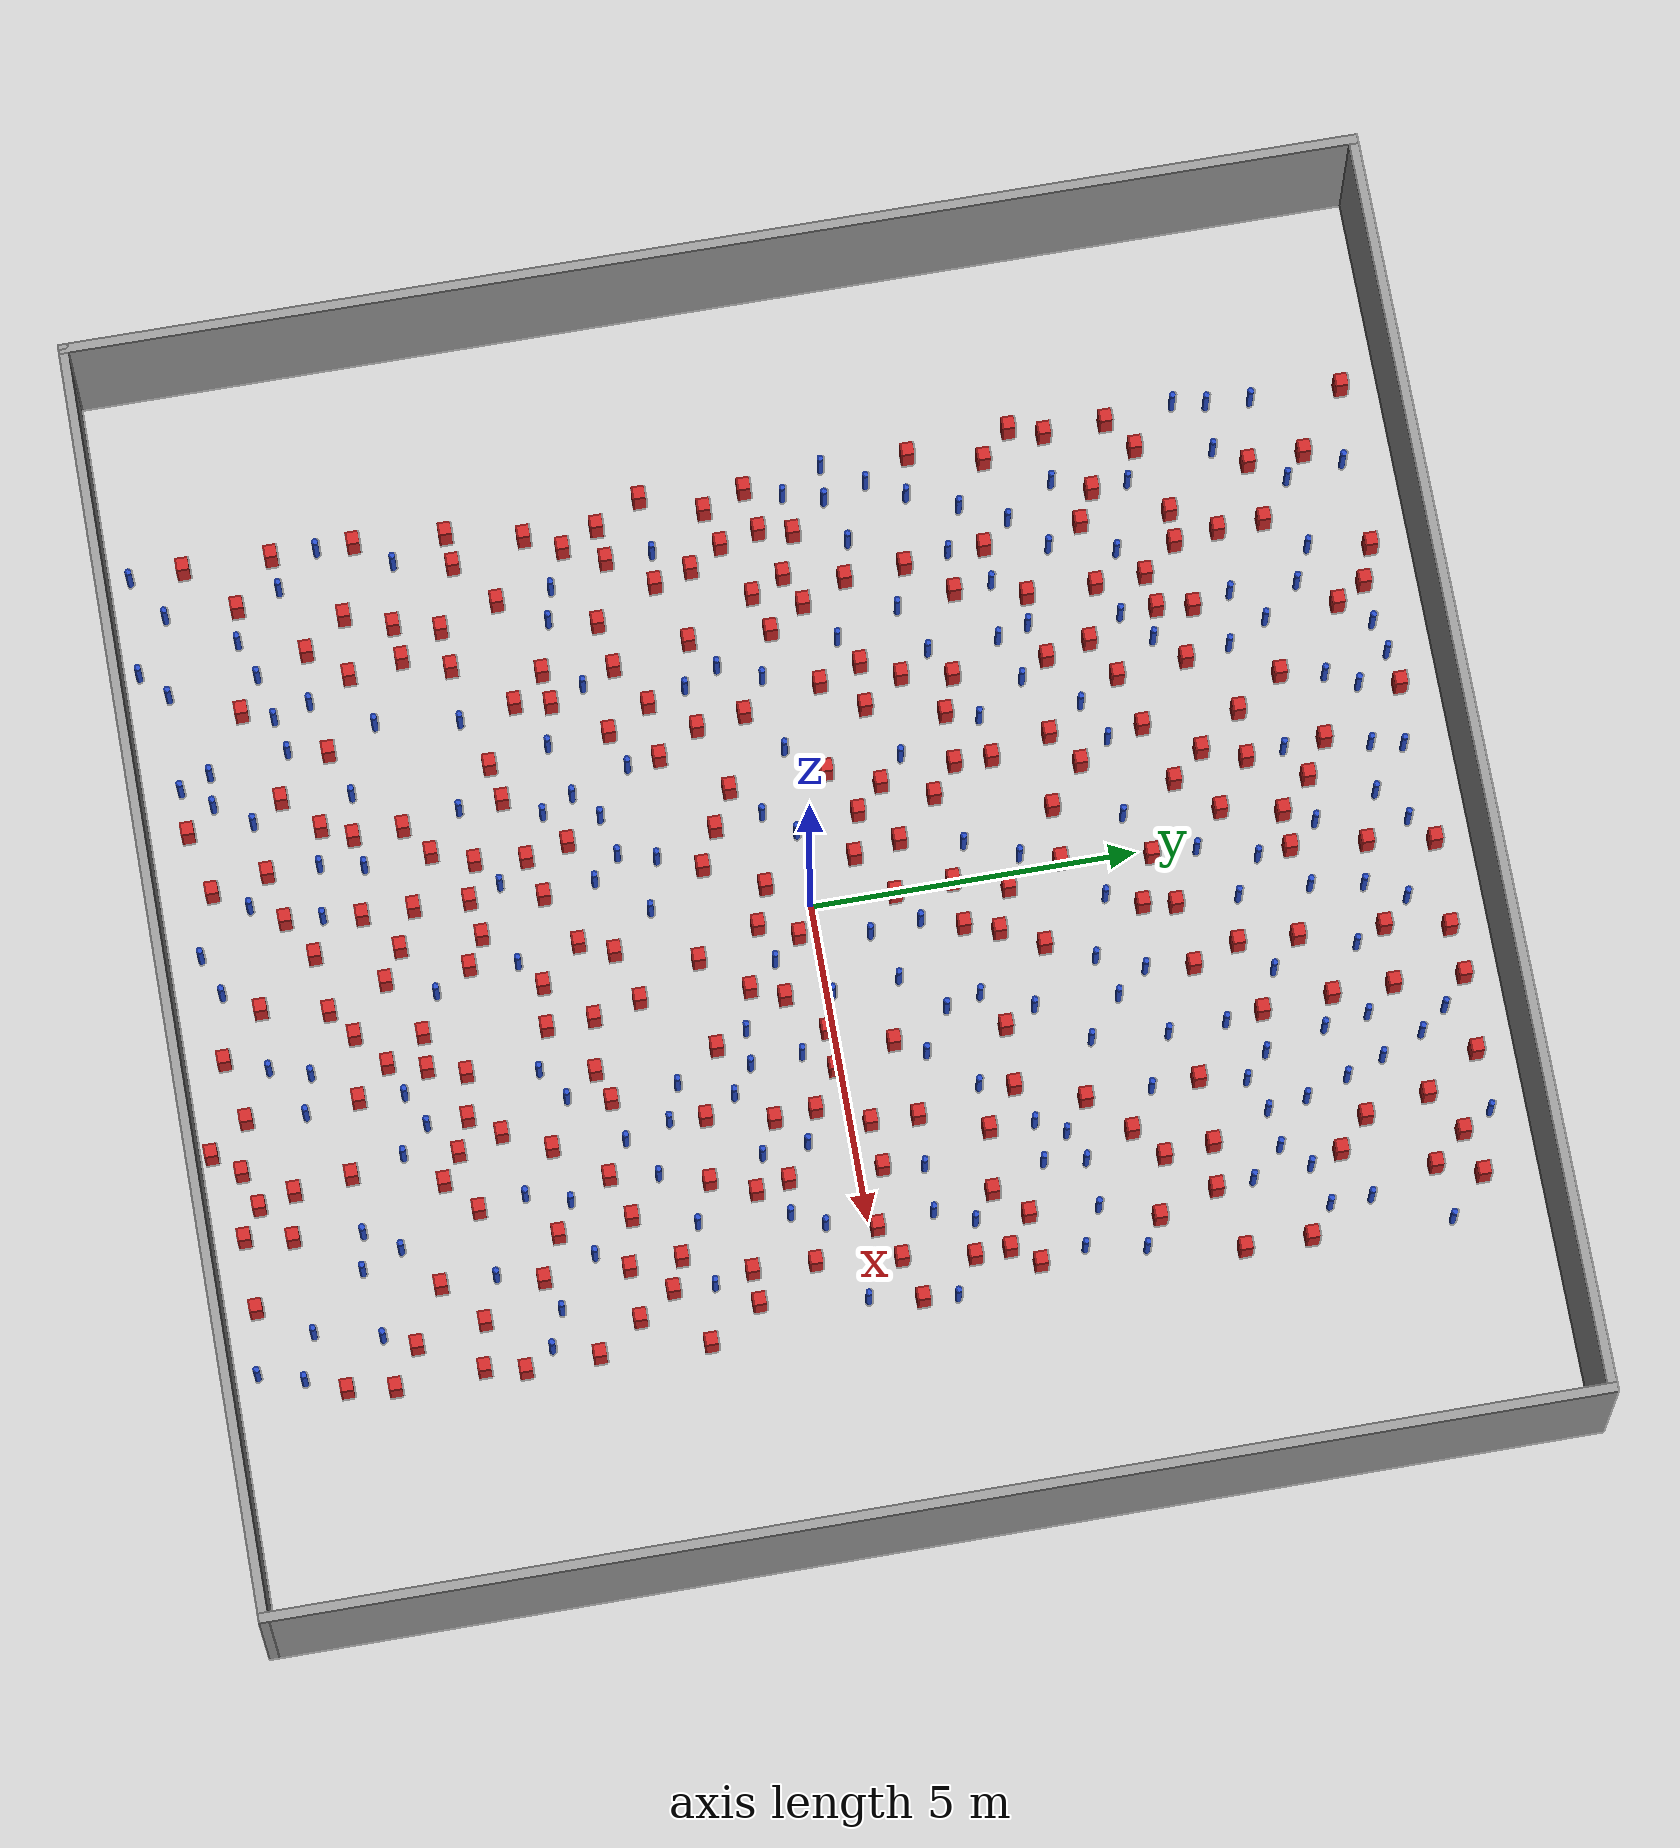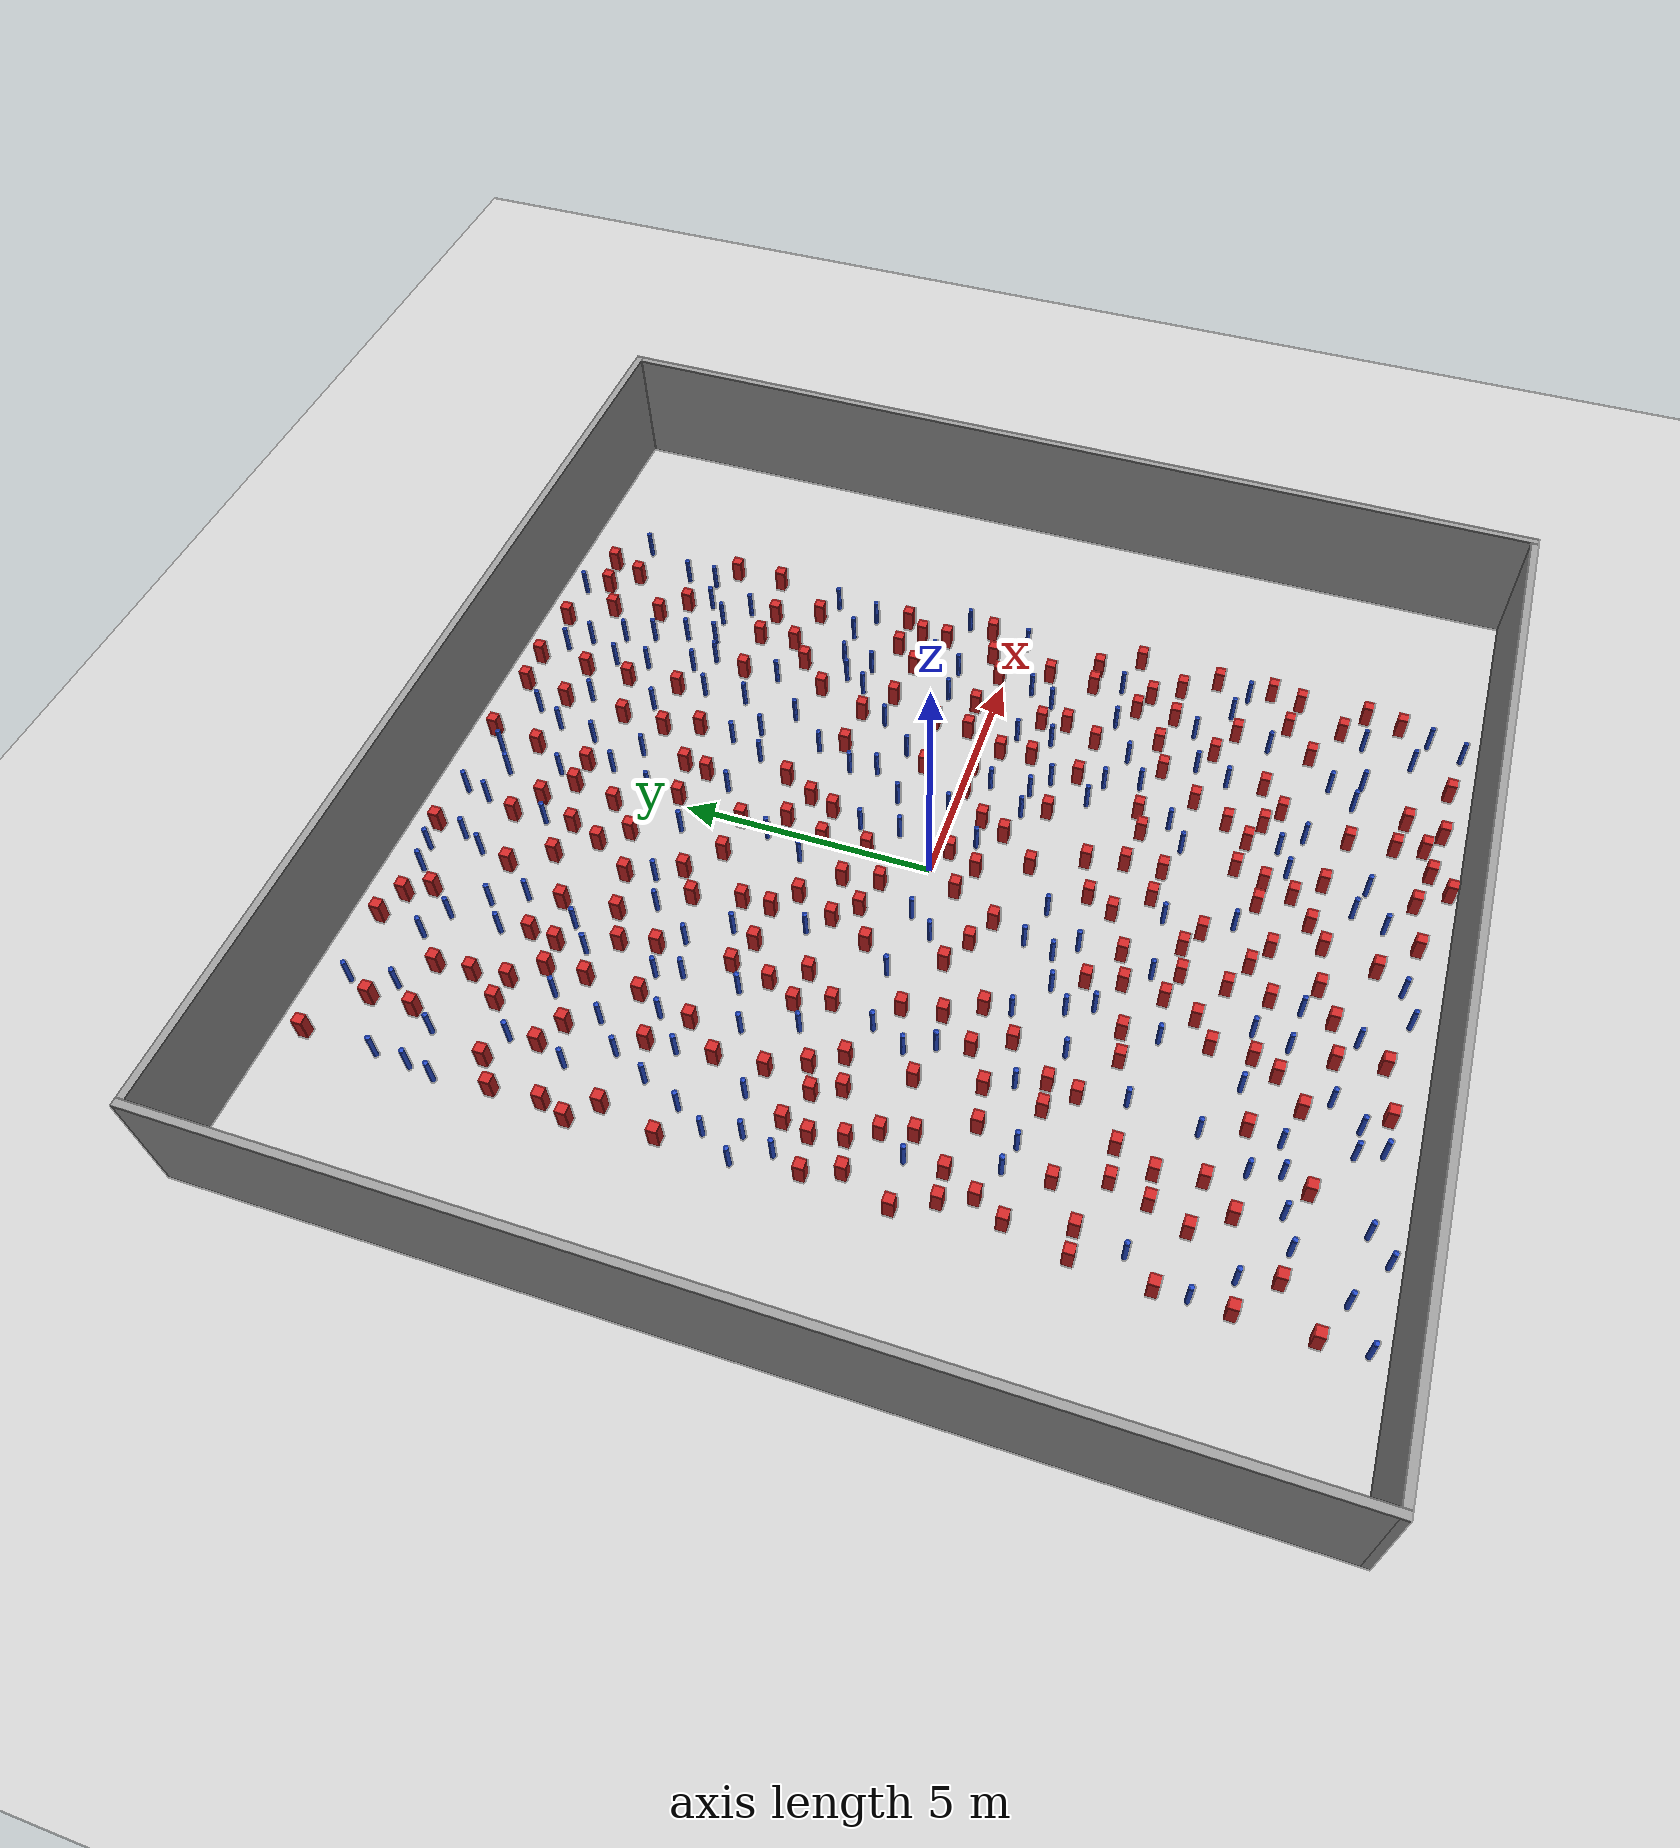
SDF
<sdf version="1.6">
 <world name="default">
  <light name="sun" type="directional">
   <pose>0 0 1000 0 -0 0</pose>
   <diffuse>0.8 0.8 0.8 1</diffuse>
   <specular>0.1 0.1 0.1 1</specular>
   <attenuation>
    <range>1000</range>
    <constant>0.9</constant>
    <linear>0.01</linear>
    <quadratic>0.001</quadratic>
   </attenuation>
   <direction>-0.5 0.5 -1</direction>
  </light>
  <model name="ground_plane">
   <static>1</static>
   <link name="link">
    <collision name="collision">
     <geometry><plane><normal>0 0 1</normal><size>100 100</size></plane></geometry>
     <surface><friction><ode><mu>100</mu><mu2>50</mu2></ode></friction></surface>
    </collision>
    <visual name="visual">
     <cast_shadows>0</cast_shadows>
     <geometry><plane><normal>0 0 1</normal><size>100 100</size></plane></geometry>
     <material>
      <ambient>1.0 1.0 1.0 1.0</ambient>
      <diffuse>0.8 0.8 0.8 1.0</diffuse>
      <specular>0.01 0.01 0.01 1.000000</specular>
     </material>
    </visual>
   </link>
  </model>
  <gravity>0 0 -9.8</gravity>
  <magnetic_field>6e-06 2.3e-05 -4.2e-05</magnetic_field>
  <atmosphere type="adiabatic"/>
  <physics name="default_physics" default="0" type="ode">
   <max_step_size>0.001</max_step_size>
   <real_time_factor>1</real_time_factor>
   <real_time_update_rate>1000</real_time_update_rate>
  </physics>
  <scene><ambient>0.4 0.4 0.4 1</ambient><background>0.7 0.7 0.7 1</background><shadows>1</shadows></scene>
  <spherical_coordinates>
   <surface_model>EARTH_WGS84</surface_model>
   <latitude_deg>0</latitude_deg>
   <longitude_deg>0</longitude_deg>
   <elevation>0</elevation>
   <heading_deg>0</heading_deg>
  </spherical_coordinates>
  <plugin name="gazebo_occupancy_map" filename="libgazebo_2Dmap_plugin.so">
   <map_resolution>0.05</map_resolution>
   <map_topic>generated_map</map_topic>
   <map_height>0.01</map_height>
   <map_size_x>50</map_size_x>
   <map_size_y>50</map_size_y>
  </plugin>
  <model name="NamedLocations">
   <static>true</static>
   <link name="DefaultStart"><pose>8.5 0 0 0 0 3.14</pose></link>
  </model>
  <model name="20x20_walls">
   <pose>0.044518 0.176112 0 0 -0 0</pose>
   <link name="Wall_1">
    <collision name="Wall_1_Collision">
     <geometry><box><size>20 0.15 2.5</size></box></geometry>
     <pose>0 0 1.25 0 -0 0</pose>
    </collision>
    <visual name="Wall_1_Visual">
     <pose>0 0 1.25 0 -0 0</pose>
     <geometry><box><size>20 0.15 2.5</size></box></geometry>
     <material>
      <script><uri>file://media/materials/scripts/gazebo.material</uri><name>Gazebo/Grey</name></script>
      <ambient>0.976471 0.992157 1 1</ambient>
     </material>
     <meta><layer>0</layer></meta>
    </visual>
    <pose>0 9.925 0 0 -0 0</pose>
   </link>
   <link name="Wall_3">
    <collision name="Wall_3_Collision">
     <geometry><box><size>20 0.15 2.5</size></box></geometry>
     <pose>0 0 1.25 0 -0 0</pose>
    </collision>
    <visual name="Wall_3_Visual">
     <pose>0 0 1.25 0 -0 0</pose>
     <geometry><box><size>20 0.15 2.5</size></box></geometry>
     <material>
      <script><uri>file://media/materials/scripts/gazebo.material</uri><name>Gazebo/Grey</name></script>
      <ambient>0.976471 0.992157 1 1</ambient>
     </material>
     <meta><layer>0</layer></meta>
    </visual>
    <pose>9.925 0 0 0 0 -1.5708</pose>
   </link>
   <link name="Wall_4">
    <collision name="Wall_4_Collision">
     <geometry><box><size>20 0.15 2.5</size></box></geometry>
     <pose>0 0 1.25 0 -0 0</pose>
    </collision>
    <visual name="Wall_4_Visual">
     <pose>0 0 1.25 0 -0 0</pose>
     <geometry><box><size>20 0.15 2.5</size></box></geometry>
     <material>
      <script><uri>file://media/materials/scripts/gazebo.material</uri><name>Gazebo/Grey</name></script>
      <ambient>0.976471 0.992157 1 1</ambient>
     </material>
     <meta><layer>0</layer></meta>
    </visual>
    <pose>0 -9.925 0 0 -0 3.14159</pose>
   </link>
   <link name="Wall_5">
    <collision name="Wall_5_Collision">
     <geometry><box><size>20 0.15 2.5</size></box></geometry>
     <pose>0 0 1.25 0 -0 0</pose>
    </collision>
    <visual name="Wall_5_Visual">
     <pose>0 0 1.25 0 -0 0</pose>
     <geometry><box><size>20 0.15 2.5</size></box></geometry>
     <material>
      <script><uri>file://media/materials/scripts/gazebo.material</uri><name>Gazebo/Grey</name></script>
      <ambient>0.976471 0.992157 1 1</ambient>
     </material>
     <meta><layer>0</layer></meta>
    </visual>
    <pose>-9.925 0 0 0 -0 1.5708</pose>
   </link>
   <static>1</static>
  </model>
  <model name="square_post_obstacle0">
   <static>true</static>
   <pose>-6.48820125278 -2.20074903678 -6.11067671241e-07 -5.50515727128e-06 -8.79689657224e-07 2.37013304536e-05</pose>
   <link name="link">
    <pose>0 0 0.25 0 -0 0</pose>
    <inertial>
     <mass>100</mass>
     <inertia>
      <ixx>0.166667</ixx>
      <ixy>0</ixy>
      <ixz>0</ixz>
      <iyy>0.166667</iyy>
      <iyz>0</iyz>
      <izz>0.166667</izz>
     </inertia>
    </inertial>
    <collision name="collision"><geometry><box><size>.2 .2 .5</size></box></geometry></collision>
    <visual name="visual">
     <geometry><box><size>.2 .2 .5</size></box></geometry>
     <material>
      <script><name>Gazebo/Red</name><uri>file://media/materials/scripts/gazebo.material</uri></script>
     </material>
    </visual>
   </link>
  </model>
  <model name="square_post_obstacle1">
   <static>true</static>
   <pose>2.530450691 -3.46873330275 -6.11067671241e-07 -5.50515727128e-06 -8.79689657224e-07 2.37013304536e-05</pose>
   <link name="link">
    <pose>0 0 0.25 0 -0 0</pose>
    <inertial>
     <mass>100</mass>
     <inertia>
      <ixx>0.166667</ixx>
      <ixy>0</ixy>
      <ixz>0</ixz>
      <iyy>0.166667</iyy>
      <iyz>0</iyz>
      <izz>0.166667</izz>
     </inertia>
    </inertial>
    <collision name="collision"><geometry><box><size>.2 .2 .5</size></box></geometry></collision>
    <visual name="visual">
     <geometry><box><size>.2 .2 .5</size></box></geometry>
     <material>
      <script><name>Gazebo/Red</name><uri>file://media/materials/scripts/gazebo.material</uri></script>
     </material>
    </visual>
   </link>
  </model>
  <model name="pole_obstacle0">
   <static>true</static>
   <pose>2.91769429393 5.82712478604 -9.47619616065e-06 5.49618799738e-07 2.3631041406e-07 -1.55090534801e-07</pose>
   <link name="link">
    <pose>0 0 0.3 0 -0 0</pose>
    <inertial>
     <mass>1</mass>
     <inertia><ixx>0.145833</ixx><ixy>0</ixy><ixz>0</ixz><iyy>0.145833</iyy><iyz>0</iyz><izz>0.125</izz></inertia>
    </inertial>
    <collision name="collision">
     <geometry><cylinder><radius>0.05</radius><length>.6</length></cylinder></geometry>
    </collision>
    <visual name="visual">
     <geometry><cylinder><radius>0.05</radius><length>.6</length></cylinder></geometry>
     <material>
      <script><name>Gazebo/Blue</name><uri>file://media/materials/scripts/gazebo.material</uri></script>
     </material>
    </visual>
   </link>
  </model>
  <model name="square_post_obstacle2">
   <static>true</static>
   <pose>0.630227751506 9.47049307353 -6.11067671241e-07 -5.50515727128e-06 -8.79689657224e-07 2.37013304536e-05</pose>
   <link name="link">
    <pose>0 0 0.25 0 -0 0</pose>
    <inertial>
     <mass>100</mass>
     <inertia>
      <ixx>0.166667</ixx>
      <ixy>0</ixy>
      <ixz>0</ixz>
      <iyy>0.166667</iyy>
      <iyz>0</iyz>
      <izz>0.166667</izz>
     </inertia>
    </inertial>
    <collision name="collision"><geometry><box><size>.2 .2 .5</size></box></geometry></collision>
    <visual name="visual">
     <geometry><box><size>.2 .2 .5</size></box></geometry>
     <material>
      <script><name>Gazebo/Red</name><uri>file://media/materials/scripts/gazebo.material</uri></script>
     </material>
    </visual>
   </link>
  </model>
  <model name="pole_obstacle1">
   <static>true</static>
   <pose>5.56627809664 -7.40692104979 -9.47619616065e-06 5.49618799737e-07 2.36310414037e-07 -1.55090534814e-07</pose>
   <link name="link">
    <pose>0 0 0.3 0 -0 0</pose>
    <inertial>
     <mass>1</mass>
     <inertia><ixx>0.145833</ixx><ixy>0</ixy><ixz>0</ixz><iyy>0.145833</iyy><iyz>0</iyz><izz>0.125</izz></inertia>
    </inertial>
    <collision name="collision">
     <geometry><cylinder><radius>0.05</radius><length>.6</length></cylinder></geometry>
    </collision>
    <visual name="visual">
     <geometry><cylinder><radius>0.05</radius><length>.6</length></cylinder></geometry>
     <material>
      <script><name>Gazebo/Blue</name><uri>file://media/materials/scripts/gazebo.material</uri></script>
     </material>
    </visual>
   </link>
  </model>
  <model name="square_post_obstacle3">
   <static>true</static>
   <pose>5.13669039034 -3.62520895391 -6.11067671241e-07 -5.50515727128e-06 -8.79689657224e-07 2.37013304536e-05</pose>
   <link name="link">
    <pose>0 0 0.25 0 -0 0</pose>
    <inertial>
     <mass>100</mass>
     <inertia>
      <ixx>0.166667</ixx>
      <ixy>0</ixy>
      <ixz>0</ixz>
      <iyy>0.166667</iyy>
      <iyz>0</iyz>
      <izz>0.166667</izz>
     </inertia>
    </inertial>
    <collision name="collision"><geometry><box><size>.2 .2 .5</size></box></geometry></collision>
    <visual name="visual">
     <geometry><box><size>.2 .2 .5</size></box></geometry>
     <material>
      <script><name>Gazebo/Red</name><uri>file://media/materials/scripts/gazebo.material</uri></script>
     </material>
    </visual>
   </link>
  </model>
  <model name="pole_obstacle2">
   <static>true</static>
   <pose>-5.81833695681 5.93957102917 -9.47619616065e-06 5.49618799737e-07 2.36310414037e-07 -1.55090534814e-07</pose>
   <link name="link">
    <pose>0 0 0.3 0 -0 0</pose>
    <inertial>
     <mass>1</mass>
     <inertia><ixx>0.145833</ixx><ixy>0</ixy><ixz>0</ixz><iyy>0.145833</iyy><iyz>0</iyz><izz>0.125</izz></inertia>
    </inertial>
    <collision name="collision">
     <geometry><cylinder><radius>0.05</radius><length>.6</length></cylinder></geometry>
    </collision>
    <visual name="visual">
     <geometry><cylinder><radius>0.05</radius><length>.6</length></cylinder></geometry>
     <material>
      <script><name>Gazebo/Blue</name><uri>file://media/materials/scripts/gazebo.material</uri></script>
     </material>
    </visual>
   </link>
  </model>
  <model name="pole_obstacle3">
   <static>true</static>
   <pose>6.40580370564 1.11894552427 -9.47619616065e-06 5.49618799738e-07 2.36310414071e-07 -1.55090534796e-07</pose>
   <link name="link">
    <pose>0 0 0.3 0 -0 0</pose>
    <inertial>
     <mass>1</mass>
     <inertia><ixx>0.145833</ixx><ixy>0</ixy><ixz>0</ixz><iyy>0.145833</iyy><iyz>0</iyz><izz>0.125</izz></inertia>
    </inertial>
    <collision name="collision">
     <geometry><cylinder><radius>0.05</radius><length>.6</length></cylinder></geometry>
    </collision>
    <visual name="visual">
     <geometry><cylinder><radius>0.05</radius><length>.6</length></cylinder></geometry>
     <material>
      <script><name>Gazebo/Blue</name><uri>file://media/materials/scripts/gazebo.material</uri></script>
     </material>
    </visual>
   </link>
  </model>
  <model name="square_post_obstacle4">
   <static>true</static>
   <pose>2.00787090122 9.43019744974 -6.11067671241e-07 -5.50515727128e-06 -8.79689657224e-07 2.37013304536e-05</pose>
   <link name="link">
    <pose>0 0 0.25 0 -0 0</pose>
    <inertial>
     <mass>100</mass>
     <inertia>
      <ixx>0.166667</ixx>
      <ixy>0</ixy>
      <ixz>0</ixz>
      <iyy>0.166667</iyy>
      <iyz>0</iyz>
      <izz>0.166667</izz>
     </inertia>
    </inertial>
    <collision name="collision"><geometry><box><size>.2 .2 .5</size></box></geometry></collision>
    <visual name="visual">
     <geometry><box><size>.2 .2 .5</size></box></geometry>
     <material>
      <script><name>Gazebo/Red</name><uri>file://media/materials/scripts/gazebo.material</uri></script>
     </material>
    </visual>
   </link>
  </model>
  <model name="square_post_obstacle5">
   <static>true</static>
   <pose>-4.30946437801 5.93188076959 -6.11067671241e-07 -5.50515727128e-06 -8.79689657224e-07 2.37013304536e-05</pose>
   <link name="link">
    <pose>0 0 0.25 0 -0 0</pose>
    <inertial>
     <mass>100</mass>
     <inertia>
      <ixx>0.166667</ixx>
      <ixy>0</ixy>
      <ixz>0</ixz>
      <iyy>0.166667</iyy>
      <iyz>0</iyz>
      <izz>0.166667</izz>
     </inertia>
    </inertial>
    <collision name="collision"><geometry><box><size>.2 .2 .5</size></box></geometry></collision>
    <visual name="visual">
     <geometry><box><size>.2 .2 .5</size></box></geometry>
     <material>
      <script><name>Gazebo/Red</name><uri>file://media/materials/scripts/gazebo.material</uri></script>
     </material>
    </visual>
   </link>
  </model>
  <model name="square_post_obstacle6">
   <static>true</static>
   <pose>0.12175120665 5.21312354501 -6.11067671241e-07 -5.50515727128e-06 -8.79689657224e-07 2.37013304536e-05</pose>
   <link name="link">
    <pose>0 0 0.25 0 -0 0</pose>
    <inertial>
     <mass>100</mass>
     <inertia>
      <ixx>0.166667</ixx>
      <ixy>0</ixy>
      <ixz>0</ixz>
      <iyy>0.166667</iyy>
      <iyz>0</iyz>
      <izz>0.166667</izz>
     </inertia>
    </inertial>
    <collision name="collision"><geometry><box><size>.2 .2 .5</size></box></geometry></collision>
    <visual name="visual">
     <geometry><box><size>.2 .2 .5</size></box></geometry>
     <material>
      <script><name>Gazebo/Red</name><uri>file://media/materials/scripts/gazebo.material</uri></script>
     </material>
    </visual>
   </link>
  </model>
  <model name="pole_obstacle4">
   <static>true</static>
   <pose>3.25930367117 7.26666605015 -9.47619616065e-06 5.49618799738e-07 2.3631041406e-07 -1.55090534801e-07</pose>
   <link name="link">
    <pose>0 0 0.3 0 -0 0</pose>
    <inertial>
     <mass>1</mass>
     <inertia><ixx>0.145833</ixx><ixy>0</ixy><ixz>0</ixz><iyy>0.145833</iyy><iyz>0</iyz><izz>0.125</izz></inertia>
    </inertial>
    <collision name="collision">
     <geometry><cylinder><radius>0.05</radius><length>.6</length></cylinder></geometry>
    </collision>
    <visual name="visual">
     <geometry><cylinder><radius>0.05</radius><length>.6</length></cylinder></geometry>
     <material>
      <script><name>Gazebo/Blue</name><uri>file://media/materials/scripts/gazebo.material</uri></script>
     </material>
    </visual>
   </link>
  </model>
  <model name="pole_obstacle5">
   <static>true</static>
   <pose>-5.44458676205 8.355744914 -9.47619616065e-06 5.49618799737e-07 2.36310414065e-07 -1.55090534796e-07</pose>
   <link name="link">
    <pose>0 0 0.3 0 -0 0</pose>
    <inertial>
     <mass>1</mass>
     <inertia><ixx>0.145833</ixx><ixy>0</ixy><ixz>0</ixz><iyy>0.145833</iyy><iyz>0</iyz><izz>0.125</izz></inertia>
    </inertial>
    <collision name="collision">
     <geometry><cylinder><radius>0.05</radius><length>.6</length></cylinder></geometry>
    </collision>
    <visual name="visual">
     <geometry><cylinder><radius>0.05</radius><length>.6</length></cylinder></geometry>
     <material>
      <script><name>Gazebo/Blue</name><uri>file://media/materials/scripts/gazebo.material</uri></script>
     </material>
    </visual>
   </link>
  </model>
  <model name="square_post_obstacle7">
   <static>true</static>
   <pose>-1.92319323468 5.44292413541 -6.11067671241e-07 -5.50515727128e-06 -8.79689657224e-07 2.37013304536e-05</pose>
   <link name="link">
    <pose>0 0 0.25 0 -0 0</pose>
    <inertial>
     <mass>100</mass>
     <inertia>
      <ixx>0.166667</ixx>
      <ixy>0</ixy>
      <ixz>0</ixz>
      <iyy>0.166667</iyy>
      <iyz>0</iyz>
      <izz>0.166667</izz>
     </inertia>
    </inertial>
    <collision name="collision"><geometry><box><size>.2 .2 .5</size></box></geometry></collision>
    <visual name="visual">
     <geometry><box><size>.2 .2 .5</size></box></geometry>
     <material>
      <script><name>Gazebo/Red</name><uri>file://media/materials/scripts/gazebo.material</uri></script>
     </material>
    </visual>
   </link>
  </model>
  <model name="square_post_obstacle8">
   <static>true</static>
   <pose>-3.33779751868 1.97403215349 -6.11067671241e-07 -5.50515727128e-06 -8.79689657224e-07 2.37013304536e-05</pose>
   <link name="link">
    <pose>0 0 0.25 0 -0 0</pose>
    <inertial>
     <mass>100</mass>
     <inertia>
      <ixx>0.166667</ixx>
      <ixy>0</ixy>
      <ixz>0</ixz>
      <iyy>0.166667</iyy>
      <iyz>0</iyz>
      <izz>0.166667</izz>
     </inertia>
    </inertial>
    <collision name="collision"><geometry><box><size>.2 .2 .5</size></box></geometry></collision>
    <visual name="visual">
     <geometry><box><size>.2 .2 .5</size></box></geometry>
     <material>
      <script><name>Gazebo/Red</name><uri>file://media/materials/scripts/gazebo.material</uri></script>
     </material>
    </visual>
   </link>
  </model>
  <model name="pole_obstacle6">
   <static>true</static>
   <pose>-6.01828911676 4.78866185865 -9.47619616065e-06 5.49618799737e-07 2.36310414037e-07 -1.55090534814e-07</pose>
   <link name="link">
    <pose>0 0 0.3 0 -0 0</pose>
    <inertial>
     <mass>1</mass>
     <inertia><ixx>0.145833</ixx><ixy>0</ixy><ixz>0</ixz><iyy>0.145833</iyy><iyz>0</iyz><izz>0.125</izz></inertia>
    </inertial>
    <collision name="collision">
     <geometry><cylinder><radius>0.05</radius><length>.6</length></cylinder></geometry>
    </collision>
    <visual name="visual">
     <geometry><cylinder><radius>0.05</radius><length>.6</length></cylinder></geometry>
     <material>
      <script><name>Gazebo/Blue</name><uri>file://media/materials/scripts/gazebo.material</uri></script>
     </material>
    </visual>
   </link>
  </model>
  <model name="pole_obstacle7">
   <static>true</static>
   <pose>-0.26180700797 8.7305991788 -9.47619616065e-06 5.49618799738e-07 2.36310414034e-07 -1.55090534817e-07</pose>
   <link name="link">
    <pose>0 0 0.3 0 -0 0</pose>
    <inertial>
     <mass>1</mass>
     <inertia><ixx>0.145833</ixx><ixy>0</ixy><ixz>0</ixz><iyy>0.145833</iyy><iyz>0</iyz><izz>0.125</izz></inertia>
    </inertial>
    <collision name="collision">
     <geometry><cylinder><radius>0.05</radius><length>.6</length></cylinder></geometry>
    </collision>
    <visual name="visual">
     <geometry><cylinder><radius>0.05</radius><length>.6</length></cylinder></geometry>
     <material>
      <script><name>Gazebo/Blue</name><uri>file://media/materials/scripts/gazebo.material</uri></script>
     </material>
    </visual>
   </link>
  </model>
  <model name="square_post_obstacle9">
   <static>true</static>
   <pose>3.55538210605 1.01613566301 -6.11067671241e-07 -5.50515727128e-06 -8.79689657224e-07 2.37013304536e-05</pose>
   <link name="link">
    <pose>0 0 0.25 0 -0 0</pose>
    <inertial>
     <mass>100</mass>
     <inertia>
      <ixx>0.166667</ixx>
      <ixy>0</ixy>
      <ixz>0</ixz>
      <iyy>0.166667</iyy>
      <iyz>0</iyz>
      <izz>0.166667</izz>
     </inertia>
    </inertial>
    <collision name="collision"><geometry><box><size>.2 .2 .5</size></box></geometry></collision>
    <visual name="visual">
     <geometry><box><size>.2 .2 .5</size></box></geometry>
     <material>
      <script><name>Gazebo/Red</name><uri>file://media/materials/scripts/gazebo.material</uri></script>
     </material>
    </visual>
   </link>
  </model>
  <model name="square_post_obstacle10">
   <static>true</static>
   <pose>-4.5397672499 3.01273756281 -6.11067671241e-07 -5.50515727128e-06 -8.79689657224e-07 2.37013304536e-05</pose>
   <link name="link">
    <pose>0 0 0.25 0 -0 0</pose>
    <inertial>
     <mass>100</mass>
     <inertia>
      <ixx>0.166667</ixx>
      <ixy>0</ixy>
      <ixz>0</ixz>
      <iyy>0.166667</iyy>
      <iyz>0</iyz>
      <izz>0.166667</izz>
     </inertia>
    </inertial>
    <collision name="collision"><geometry><box><size>.2 .2 .5</size></box></geometry></collision>
    <visual name="visual">
     <geometry><box><size>.2 .2 .5</size></box></geometry>
     <material>
      <script><name>Gazebo/Red</name><uri>file://media/materials/scripts/gazebo.material</uri></script>
     </material>
    </visual>
   </link>
  </model>
  <model name="square_post_obstacle11">
   <static>true</static>
   <pose>-0.690609439429 7.77177443221 -6.11067671241e-07 -5.50515727128e-06 -8.79689657224e-07 2.37013304536e-05</pose>
   <link name="link">
    <pose>0 0 0.25 0 -0 0</pose>
    <inertial>
     <mass>100</mass>
     <inertia>
      <ixx>0.166667</ixx>
      <ixy>0</ixy>
      <ixz>0</ixz>
      <iyy>0.166667</iyy>
      <iyz>0</iyz>
      <izz>0.166667</izz>
     </inertia>
    </inertial>
    <collision name="collision"><geometry><box><size>.2 .2 .5</size></box></geometry></collision>
    <visual name="visual">
     <geometry><box><size>.2 .2 .5</size></box></geometry>
     <material>
      <script><name>Gazebo/Red</name><uri>file://media/materials/scripts/gazebo.material</uri></script>
     </material>
    </visual>
   </link>
  </model>
  <model name="square_post_obstacle12">
   <static>true</static>
   <pose>-6.81449634374 4.81211950419 -6.11067671241e-07 -5.50515727128e-06 -8.79689657224e-07 2.37013304536e-05</pose>
   <link name="link">
    <pose>0 0 0.25 0 -0 0</pose>
    <inertial>
     <mass>100</mass>
     <inertia>
      <ixx>0.166667</ixx>
      <ixy>0</ixy>
      <ixz>0</ixz>
      <iyy>0.166667</iyy>
      <iyz>0</iyz>
      <izz>0.166667</izz>
     </inertia>
    </inertial>
    <collision name="collision"><geometry><box><size>.2 .2 .5</size></box></geometry></collision>
    <visual name="visual">
     <geometry><box><size>.2 .2 .5</size></box></geometry>
     <material>
      <script><name>Gazebo/Red</name><uri>file://media/materials/scripts/gazebo.material</uri></script>
     </material>
    </visual>
   </link>
  </model>
  <model name="square_post_obstacle13">
   <static>true</static>
   <pose>-0.3879240775 -0.623980842196 -6.11067671241e-07 -5.50515727128e-06 -8.79689657224e-07 2.37013304536e-05</pose>
   <link name="link">
    <pose>0 0 0.25 0 -0 0</pose>
    <inertial>
     <mass>100</mass>
     <inertia>
      <ixx>0.166667</ixx>
      <ixy>0</ixy>
      <ixz>0</ixz>
      <iyy>0.166667</iyy>
      <iyz>0</iyz>
      <izz>0.166667</izz>
     </inertia>
    </inertial>
    <collision name="collision"><geometry><box><size>.2 .2 .5</size></box></geometry></collision>
    <visual name="visual">
     <geometry><box><size>.2 .2 .5</size></box></geometry>
     <material>
      <script><name>Gazebo/Red</name><uri>file://media/materials/scripts/gazebo.material</uri></script>
     </material>
    </visual>
   </link>
  </model>
  <model name="pole_obstacle8">
   <static>true</static>
   <pose>3.57951586934 8.69045144701 -9.4761961606e-06 5.49618799729e-07 2.36310414e-07 -1.55090534824e-07</pose>
   <link name="link">
    <pose>0 0 0.3 0 -0 0</pose>
    <inertial>
     <mass>1</mass>
     <inertia><ixx>0.145833</ixx><ixy>0</ixy><ixz>0</ixz><iyy>0.145833</iyy><iyz>0</iyz><izz>0.125</izz></inertia>
    </inertial>
    <collision name="collision">
     <geometry><cylinder><radius>0.05</radius><length>.6</length></cylinder></geometry>
    </collision>
    <visual name="visual">
     <geometry><cylinder><radius>0.05</radius><length>.6</length></cylinder></geometry>
     <material>
      <script><name>Gazebo/Blue</name><uri>file://media/materials/scripts/gazebo.material</uri></script>
     </material>
    </visual>
   </link>
  </model>
  <model name="square_post_obstacle14">
   <static>true</static>
   <pose>-1.82244334132 2.52893783839 -6.11067671241e-07 -5.50515727128e-06 -8.79689657224e-07 2.37013304536e-05</pose>
   <link name="link">
    <pose>0 0 0.25 0 -0 0</pose>
    <inertial>
     <mass>100</mass>
     <inertia>
      <ixx>0.166667</ixx>
      <ixy>0</ixy>
      <ixz>0</ixz>
      <iyy>0.166667</iyy>
      <iyz>0</iyz>
      <izz>0.166667</izz>
     </inertia>
    </inertial>
    <collision name="collision"><geometry><box><size>.2 .2 .5</size></box></geometry></collision>
    <visual name="visual">
     <geometry><box><size>.2 .2 .5</size></box></geometry>
     <material>
      <script><name>Gazebo/Red</name><uri>file://media/materials/scripts/gazebo.material</uri></script>
     </material>
    </visual>
   </link>
  </model>
  <model name="square_post_obstacle15">
   <static>true</static>
   <pose>3.71951136214 3.53396822904 -6.11067671241e-07 -5.50515727128e-06 -8.79689657224e-07 2.37013304536e-05</pose>
   <link name="link">
    <pose>0 0 0.25 0 -0 0</pose>
    <inertial>
     <mass>100</mass>
     <inertia>
      <ixx>0.166667</ixx>
      <ixy>0</ixy>
      <ixz>0</ixz>
      <iyy>0.166667</iyy>
      <iyz>0</iyz>
      <izz>0.166667</izz>
     </inertia>
    </inertial>
    <collision name="collision"><geometry><box><size>.2 .2 .5</size></box></geometry></collision>
    <visual name="visual">
     <geometry><box><size>.2 .2 .5</size></box></geometry>
     <material>
      <script><name>Gazebo/Red</name><uri>file://media/materials/scripts/gazebo.material</uri></script>
     </material>
    </visual>
   </link>
  </model>
  <model name="square_post_obstacle16">
   <static>true</static>
   <pose>-2.2230492415 -6.63477181087 -6.11067671241e-07 -5.50515727128e-06 -8.79689657224e-07 2.37013304536e-05</pose>
   <link name="link">
    <pose>0 0 0.25 0 -0 0</pose>
    <inertial>
     <mass>100</mass>
     <inertia>
      <ixx>0.166667</ixx>
      <ixy>0</ixy>
      <ixz>0</ixz>
      <iyy>0.166667</iyy>
      <iyz>0</iyz>
      <izz>0.166667</izz>
     </inertia>
    </inertial>
    <collision name="collision"><geometry><box><size>.2 .2 .5</size></box></geometry></collision>
    <visual name="visual">
     <geometry><box><size>.2 .2 .5</size></box></geometry>
     <material>
      <script><name>Gazebo/Red</name><uri>file://media/materials/scripts/gazebo.material</uri></script>
     </material>
    </visual>
   </link>
  </model>
  <model name="pole_obstacle9">
   <static>true</static>
   <pose>3.01143764295 -2.66555143972 -9.47619616065e-06 5.49618799737e-07 2.36310414051e-07 -1.55090534807e-07</pose>
   <link name="link">
    <pose>0 0 0.3 0 -0 0</pose>
    <inertial>
     <mass>1</mass>
     <inertia><ixx>0.145833</ixx><ixy>0</ixy><ixz>0</ixz><iyy>0.145833</iyy><iyz>0</iyz><izz>0.125</izz></inertia>
    </inertial>
    <collision name="collision">
     <geometry><cylinder><radius>0.05</radius><length>.6</length></cylinder></geometry>
    </collision>
    <visual name="visual">
     <geometry><cylinder><radius>0.05</radius><length>.6</length></cylinder></geometry>
     <material>
      <script><name>Gazebo/Blue</name><uri>file://media/materials/scripts/gazebo.material</uri></script>
     </material>
    </visual>
   </link>
  </model>
  <model name="square_post_obstacle17">
   <static>true</static>
   <pose>-4.90225215587 -5.46459543071 -6.11067671241e-07 -5.50515727128e-06 -8.79689657224e-07 2.37013304536e-05</pose>
   <link name="link">
    <pose>0 0 0.25 0 -0 0</pose>
    <inertial>
     <mass>100</mass>
     <inertia>
      <ixx>0.166667</ixx>
      <ixy>0</ixy>
      <ixz>0</ixz>
      <iyy>0.166667</iyy>
      <iyz>0</iyz>
      <izz>0.166667</izz>
     </inertia>
    </inertial>
    <collision name="collision"><geometry><box><size>.2 .2 .5</size></box></geometry></collision>
    <visual name="visual">
     <geometry><box><size>.2 .2 .5</size></box></geometry>
     <material>
      <script><name>Gazebo/Red</name><uri>file://media/materials/scripts/gazebo.material</uri></script>
     </material>
    </visual>
   </link>
  </model>
  <model name="square_post_obstacle18">
   <static>true</static>
   <pose>5.49157595829 -1.83002905532 -6.11067671241e-07 -5.50515727128e-06 -8.79689657224e-07 2.37013304536e-05</pose>
   <link name="link">
    <pose>0 0 0.25 0 -0 0</pose>
    <inertial>
     <mass>100</mass>
     <inertia>
      <ixx>0.166667</ixx>
      <ixy>0</ixy>
      <ixz>0</ixz>
      <iyy>0.166667</iyy>
      <iyz>0</iyz>
      <izz>0.166667</izz>
     </inertia>
    </inertial>
    <collision name="collision"><geometry><box><size>.2 .2 .5</size></box></geometry></collision>
    <visual name="visual">
     <geometry><box><size>.2 .2 .5</size></box></geometry>
     <material>
      <script><name>Gazebo/Red</name><uri>file://media/materials/scripts/gazebo.material</uri></script>
     </material>
    </visual>
   </link>
  </model>
  <model name="pole_obstacle10">
   <static>true</static>
   <pose>3.98855867331 -4.32102343324 -9.47619616065e-06 5.49618799737e-07 2.36310414049e-07 -1.55090534808e-07</pose>
   <link name="link">
    <pose>0 0 0.3 0 -0 0</pose>
    <inertial>
     <mass>1</mass>
     <inertia><ixx>0.145833</ixx><ixy>0</ixy><ixz>0</ixz><iyy>0.145833</iyy><iyz>0</iyz><izz>0.125</izz></inertia>
    </inertial>
    <collision name="collision">
     <geometry><cylinder><radius>0.05</radius><length>.6</length></cylinder></geometry>
    </collision>
    <visual name="visual">
     <geometry><cylinder><radius>0.05</radius><length>.6</length></cylinder></geometry>
     <material>
      <script><name>Gazebo/Blue</name><uri>file://media/materials/scripts/gazebo.material</uri></script>
     </material>
    </visual>
   </link>
  </model>
  <model name="square_post_obstacle19">
   <static>true</static>
   <pose>5.09355135205 -4.90761829041 -6.11067671241e-07 -5.50515727128e-06 -8.79689657224e-07 2.37013304536e-05</pose>
   <link name="link">
    <pose>0 0 0.25 0 -0 0</pose>
    <inertial>
     <mass>100</mass>
     <inertia>
      <ixx>0.166667</ixx>
      <ixy>0</ixy>
      <ixz>0</ixz>
      <iyy>0.166667</iyy>
      <iyz>0</iyz>
      <izz>0.166667</izz>
     </inertia>
    </inertial>
    <collision name="collision"><geometry><box><size>.2 .2 .5</size></box></geometry></collision>
    <visual name="visual">
     <geometry><box><size>.2 .2 .5</size></box></geometry>
     <material>
      <script><name>Gazebo/Red</name><uri>file://media/materials/scripts/gazebo.material</uri></script>
     </material>
    </visual>
   </link>
  </model>
  <model name="pole_obstacle11">
   <static>true</static>
   <pose>-5.57443344239 9.24902005777 -9.47619616065e-06 5.49618799737e-07 2.36310414065e-07 -1.55090534796e-07</pose>
   <link name="link">
    <pose>0 0 0.3 0 -0 0</pose>
    <inertial>
     <mass>1</mass>
     <inertia><ixx>0.145833</ixx><ixy>0</ixy><ixz>0</ixz><iyy>0.145833</iyy><iyz>0</iyz><izz>0.125</izz></inertia>
    </inertial>
    <collision name="collision">
     <geometry><cylinder><radius>0.05</radius><length>.6</length></cylinder></geometry>
    </collision>
    <visual name="visual">
     <geometry><cylinder><radius>0.05</radius><length>.6</length></cylinder></geometry>
     <material>
      <script><name>Gazebo/Blue</name><uri>file://media/materials/scripts/gazebo.material</uri></script>
     </material>
    </visual>
   </link>
  </model>
  <model name="square_post_obstacle20">
   <static>true</static>
   <pose>3.11336619792 -4.46068472534 -6.11067671241e-07 -5.50515727128e-06 -8.79689657224e-07 2.37013304536e-05</pose>
   <link name="link">
    <pose>0 0 0.25 0 -0 0</pose>
    <inertial>
     <mass>100</mass>
     <inertia>
      <ixx>0.166667</ixx>
      <ixy>0</ixy>
      <ixz>0</ixz>
      <iyy>0.166667</iyy>
      <iyz>0</iyz>
      <izz>0.166667</izz>
     </inertia>
    </inertial>
    <collision name="collision"><geometry><box><size>.2 .2 .5</size></box></geometry></collision>
    <visual name="visual">
     <geometry><box><size>.2 .2 .5</size></box></geometry>
     <material>
      <script><name>Gazebo/Red</name><uri>file://media/materials/scripts/gazebo.material</uri></script>
     </material>
    </visual>
   </link>
  </model>
  <model name="pole_obstacle12">
   <static>true</static>
   <pose>0.657242234595 4.40116900106 -9.47619616065e-06 5.49618799737e-07 2.36310414065e-07 -1.55090534796e-07</pose>
   <link name="link">
    <pose>0 0 0.3 0 -0 0</pose>
    <inertial>
     <mass>1</mass>
     <inertia><ixx>0.145833</ixx><ixy>0</ixy><ixz>0</ixz><iyy>0.145833</iyy><iyz>0</iyz><izz>0.125</izz></inertia>
    </inertial>
    <collision name="collision">
     <geometry><cylinder><radius>0.05</radius><length>.6</length></cylinder></geometry>
    </collision>
    <visual name="visual">
     <geometry><cylinder><radius>0.05</radius><length>.6</length></cylinder></geometry>
     <material>
      <script><name>Gazebo/Blue</name><uri>file://media/materials/scripts/gazebo.material</uri></script>
     </material>
    </visual>
   </link>
  </model>
  <model name="square_post_obstacle21">
   <static>true</static>
   <pose>-3.89522748036 -3.89047158635 -6.11067671241e-07 -5.50515727128e-06 -8.79689657224e-07 2.37013304536e-05</pose>
   <link name="link">
    <pose>0 0 0.25 0 -0 0</pose>
    <inertial>
     <mass>100</mass>
     <inertia>
      <ixx>0.166667</ixx>
      <ixy>0</ixy>
      <ixz>0</ixz>
      <iyy>0.166667</iyy>
      <iyz>0</iyz>
      <izz>0.166667</izz>
     </inertia>
    </inertial>
    <collision name="collision"><geometry><box><size>.2 .2 .5</size></box></geometry></collision>
    <visual name="visual">
     <geometry><box><size>.2 .2 .5</size></box></geometry>
     <material>
      <script><name>Gazebo/Red</name><uri>file://media/materials/scripts/gazebo.material</uri></script>
     </material>
    </visual>
   </link>
  </model>
  <model name="pole_obstacle13">
   <static>true</static>
   <pose>0.439902832676 -5.78268501385 -9.47619616065e-06 5.49618799737e-07 2.36310414065e-07 -1.55090534796e-07</pose>
   <link name="link">
    <pose>0 0 0.3 0 -0 0</pose>
    <inertial>
     <mass>1</mass>
     <inertia><ixx>0.145833</ixx><ixy>0</ixy><ixz>0</ixz><iyy>0.145833</iyy><iyz>0</iyz><izz>0.125</izz></inertia>
    </inertial>
    <collision name="collision">
     <geometry><cylinder><radius>0.05</radius><length>.6</length></cylinder></geometry>
    </collision>
    <visual name="visual">
     <geometry><cylinder><radius>0.05</radius><length>.6</length></cylinder></geometry>
     <material>
      <script><name>Gazebo/Blue</name><uri>file://media/materials/scripts/gazebo.material</uri></script>
     </material>
    </visual>
   </link>
  </model>
  <model name="square_post_obstacle22">
   <static>true</static>
   <pose>0.462626099444 -0.256833321425 -6.11067671241e-07 -5.50515727128e-06 -8.79689657224e-07 2.37013304536e-05</pose>
   <link name="link">
    <pose>0 0 0.25 0 -0 0</pose>
    <inertial>
     <mass>100</mass>
     <inertia>
      <ixx>0.166667</ixx>
      <ixy>0</ixy>
      <ixz>0</ixz>
      <iyy>0.166667</iyy>
      <iyz>0</iyz>
      <izz>0.166667</izz>
     </inertia>
    </inertial>
    <collision name="collision"><geometry><box><size>.2 .2 .5</size></box></geometry></collision>
    <visual name="visual">
     <geometry><box><size>.2 .2 .5</size></box></geometry>
     <material>
      <script><name>Gazebo/Red</name><uri>file://media/materials/scripts/gazebo.material</uri></script>
     </material>
    </visual>
   </link>
  </model>
  <model name="pole_obstacle14">
   <static>true</static>
   <pose>-5.57467568248 -7.8820841528 -9.47619616065e-06 5.49618799737e-07 2.36310414037e-07 -1.55090534814e-07</pose>
   <link name="link">
    <pose>0 0 0.3 0 -0 0</pose>
    <inertial>
     <mass>1</mass>
     <inertia><ixx>0.145833</ixx><ixy>0</ixy><ixz>0</ixz><iyy>0.145833</iyy><iyz>0</iyz><izz>0.125</izz></inertia>
    </inertial>
    <collision name="collision">
     <geometry><cylinder><radius>0.05</radius><length>.6</length></cylinder></geometry>
    </collision>
    <visual name="visual">
     <geometry><cylinder><radius>0.05</radius><length>.6</length></cylinder></geometry>
     <material>
      <script><name>Gazebo/Blue</name><uri>file://media/materials/scripts/gazebo.material</uri></script>
     </material>
    </visual>
   </link>
  </model>
  <model name="pole_obstacle15">
   <static>true</static>
   <pose>1.45612019845 8.88032884536 -9.47619616065e-06 5.49618799737e-07 2.36310414046e-07 -1.55090534809e-07</pose>
   <link name="link">
    <pose>0 0 0.3 0 -0 0</pose>
    <inertial>
     <mass>1</mass>
     <inertia><ixx>0.145833</ixx><ixy>0</ixy><ixz>0</ixz><iyy>0.145833</iyy><iyz>0</iyz><izz>0.125</izz></inertia>
    </inertial>
    <collision name="collision">
     <geometry><cylinder><radius>0.05</radius><length>.6</length></cylinder></geometry>
    </collision>
    <visual name="visual">
     <geometry><cylinder><radius>0.05</radius><length>.6</length></cylinder></geometry>
     <material>
      <script><name>Gazebo/Blue</name><uri>file://media/materials/scripts/gazebo.material</uri></script>
     </material>
    </visual>
   </link>
  </model>
  <model name="pole_obstacle16">
   <static>true</static>
   <pose>-0.0822495026502 -8.96081779854 -9.47619616065e-06 5.49618799738e-07 2.36310414031e-07 -1.55090534818e-07</pose>
   <link name="link">
    <pose>0 0 0.3 0 -0 0</pose>
    <inertial>
     <mass>1</mass>
     <inertia><ixx>0.145833</ixx><ixy>0</ixy><ixz>0</ixz><iyy>0.145833</iyy><iyz>0</iyz><izz>0.125</izz></inertia>
    </inertial>
    <collision name="collision">
     <geometry><cylinder><radius>0.05</radius><length>.6</length></cylinder></geometry>
    </collision>
    <visual name="visual">
     <geometry><cylinder><radius>0.05</radius><length>.6</length></cylinder></geometry>
     <material>
      <script><name>Gazebo/Blue</name><uri>file://media/materials/scripts/gazebo.material</uri></script>
     </material>
    </visual>
   </link>
  </model>
  <model name="square_post_obstacle23">
   <static>true</static>
   <pose>3.52569320102 0.297685927197 -6.11067671241e-07 -5.50515727128e-06 -8.79689657224e-07 2.37013304536e-05</pose>
   <link name="link">
    <pose>0 0 0.25 0 -0 0</pose>
    <inertial>
     <mass>100</mass>
     <inertia>
      <ixx>0.166667</ixx>
      <ixy>0</ixy>
      <ixz>0</ixz>
      <iyy>0.166667</iyy>
      <iyz>0</iyz>
      <izz>0.166667</izz>
     </inertia>
    </inertial>
    <collision name="collision"><geometry><box><size>.2 .2 .5</size></box></geometry></collision>
    <visual name="visual">
     <geometry><box><size>.2 .2 .5</size></box></geometry>
     <material>
      <script><name>Gazebo/Red</name><uri>file://media/materials/scripts/gazebo.material</uri></script>
     </material>
    </visual>
   </link>
  </model>
  <model name="pole_obstacle17">
   <static>true</static>
   <pose>1.03093555033 7.47529446782 -9.47619616065e-06 5.49618799737e-07 2.36310414059e-07 -1.550905348e-07</pose>
   <link name="link">
    <pose>0 0 0.3 0 -0 0</pose>
    <inertial>
     <mass>1</mass>
     <inertia><ixx>0.145833</ixx><ixy>0</ixy><ixz>0</ixz><iyy>0.145833</iyy><iyz>0</iyz><izz>0.125</izz></inertia>
    </inertial>
    <collision name="collision">
     <geometry><cylinder><radius>0.05</radius><length>.6</length></cylinder></geometry>
    </collision>
    <visual name="visual">
     <geometry><cylinder><radius>0.05</radius><length>.6</length></cylinder></geometry>
     <material>
      <script><name>Gazebo/Blue</name><uri>file://media/materials/scripts/gazebo.material</uri></script>
     </material>
    </visual>
   </link>
  </model>
  <model name="square_post_obstacle24">
   <static>true</static>
   <pose>-0.95335000836 -5.91281050949 -6.11067671241e-07 -5.50515727128e-06 -8.79689657224e-07 2.37013304536e-05</pose>
   <link name="link">
    <pose>0 0 0.25 0 -0 0</pose>
    <inertial>
     <mass>100</mass>
     <inertia>
      <ixx>0.166667</ixx>
      <ixy>0</ixy>
      <ixz>0</ixz>
      <iyy>0.166667</iyy>
      <iyz>0</iyz>
      <izz>0.166667</izz>
     </inertia>
    </inertial>
    <collision name="collision"><geometry><box><size>.2 .2 .5</size></box></geometry></collision>
    <visual name="visual">
     <geometry><box><size>.2 .2 .5</size></box></geometry>
     <material>
      <script><name>Gazebo/Red</name><uri>file://media/materials/scripts/gazebo.material</uri></script>
     </material>
    </visual>
   </link>
  </model>
  <model name="square_post_obstacle25">
   <static>true</static>
   <pose>-0.753819855754 1.49309940718 -6.11067671241e-07 -5.50515727128e-06 -8.79689657224e-07 2.37013304536e-05</pose>
   <link name="link">
    <pose>0 0 0.25 0 -0 0</pose>
    <inertial>
     <mass>100</mass>
     <inertia>
      <ixx>0.166667</ixx>
      <ixy>0</ixy>
      <ixz>0</ixz>
      <iyy>0.166667</iyy>
      <iyz>0</iyz>
      <izz>0.166667</izz>
     </inertia>
    </inertial>
    <collision name="collision"><geometry><box><size>.2 .2 .5</size></box></geometry></collision>
    <visual name="visual">
     <geometry><box><size>.2 .2 .5</size></box></geometry>
     <material>
      <script><name>Gazebo/Red</name><uri>file://media/materials/scripts/gazebo.material</uri></script>
     </material>
    </visual>
   </link>
  </model>
  <model name="square_post_obstacle26">
   <static>true</static>
   <pose>4.23867038706 0.354089430729 -6.11067671241e-07 -5.50515727128e-06 -8.79689657224e-07 2.37013304536e-05</pose>
   <link name="link">
    <pose>0 0 0.25 0 -0 0</pose>
    <inertial>
     <mass>100</mass>
     <inertia>
      <ixx>0.166667</ixx>
      <ixy>0</ixy>
      <ixz>0</ixz>
      <iyy>0.166667</iyy>
      <iyz>0</iyz>
      <izz>0.166667</izz>
     </inertia>
    </inertial>
    <collision name="collision"><geometry><box><size>.2 .2 .5</size></box></geometry></collision>
    <visual name="visual">
     <geometry><box><size>.2 .2 .5</size></box></geometry>
     <material>
      <script><name>Gazebo/Red</name><uri>file://media/materials/scripts/gazebo.material</uri></script>
     </material>
    </visual>
   </link>
  </model>
  <model name="square_post_obstacle27">
   <static>true</static>
   <pose>2.94282083598 -5.85030339063 -6.11067671241e-07 -5.50515727128e-06 -8.79689657224e-07 2.37013304536e-05</pose>
   <link name="link">
    <pose>0 0 0.25 0 -0 0</pose>
    <inertial>
     <mass>100</mass>
     <inertia>
      <ixx>0.166667</ixx>
      <ixy>0</ixy>
      <ixz>0</ixz>
      <iyy>0.166667</iyy>
      <iyz>0</iyz>
      <izz>0.166667</izz>
     </inertia>
    </inertial>
    <collision name="collision"><geometry><box><size>.2 .2 .5</size></box></geometry></collision>
    <visual name="visual">
     <geometry><box><size>.2 .2 .5</size></box></geometry>
     <material>
      <script><name>Gazebo/Red</name><uri>file://media/materials/scripts/gazebo.material</uri></script>
     </material>
    </visual>
   </link>
  </model>
  <model name="pole_obstacle18">
   <static>true</static>
   <pose>4.64653328967 -2.50887436375 -9.47619616065e-06 5.49618799738e-07 2.36310414051e-07 -1.55090534805e-07</pose>
   <link name="link">
    <pose>0 0 0.3 0 -0 0</pose>
    <inertial>
     <mass>1</mass>
     <inertia><ixx>0.145833</ixx><ixy>0</ixy><ixz>0</ixz><iyy>0.145833</iyy><iyz>0</iyz><izz>0.125</izz></inertia>
    </inertial>
    <collision name="collision">
     <geometry><cylinder><radius>0.05</radius><length>.6</length></cylinder></geometry>
    </collision>
    <visual name="visual">
     <geometry><cylinder><radius>0.05</radius><length>.6</length></cylinder></geometry>
     <material>
      <script><name>Gazebo/Blue</name><uri>file://media/materials/scripts/gazebo.material</uri></script>
     </material>
    </visual>
   </link>
  </model>
  <model name="square_post_obstacle28">
   <static>true</static>
   <pose>3.1888105255 -0.476399686188 -6.11067671241e-07 -5.50515727128e-06 -8.79689657224e-07 2.37013304536e-05</pose>
   <link name="link">
    <pose>0 0 0.25 0 -0 0</pose>
    <inertial>
     <mass>100</mass>
     <inertia>
      <ixx>0.166667</ixx>
      <ixy>0</ixy>
      <ixz>0</ixz>
      <iyy>0.166667</iyy>
      <iyz>0</iyz>
      <izz>0.166667</izz>
     </inertia>
    </inertial>
    <collision name="collision"><geometry><box><size>.2 .2 .5</size></box></geometry></collision>
    <visual name="visual">
     <geometry><box><size>.2 .2 .5</size></box></geometry>
     <material>
      <script><name>Gazebo/Red</name><uri>file://media/materials/scripts/gazebo.material</uri></script>
     </material>
    </visual>
   </link>
  </model>
  <model name="pole_obstacle19">
   <static>true</static>
   <pose>-1.23644389583 -2.74520126491 -9.47619616065e-06 5.49618799737e-07 2.36310414062e-07 -1.55090534798e-07</pose>
   <link name="link">
    <pose>0 0 0.3 0 -0 0</pose>
    <inertial>
     <mass>1</mass>
     <inertia><ixx>0.145833</ixx><ixy>0</ixy><ixz>0</ixz><iyy>0.145833</iyy><iyz>0</iyz><izz>0.125</izz></inertia>
    </inertial>
    <collision name="collision">
     <geometry><cylinder><radius>0.05</radius><length>.6</length></cylinder></geometry>
    </collision>
    <visual name="visual">
     <geometry><cylinder><radius>0.05</radius><length>.6</length></cylinder></geometry>
     <material>
      <script><name>Gazebo/Blue</name><uri>file://media/materials/scripts/gazebo.material</uri></script>
     </material>
    </visual>
   </link>
  </model>
  <model name="square_post_obstacle29">
   <static>true</static>
   <pose>-6.77009937237 -4.49488068824 -6.11067671241e-07 -5.50515727128e-06 -8.79689657224e-07 2.37013304536e-05</pose>
   <link name="link">
    <pose>0 0 0.25 0 -0 0</pose>
    <inertial>
     <mass>100</mass>
     <inertia>
      <ixx>0.166667</ixx>
      <ixy>0</ixy>
      <ixz>0</ixz>
      <iyy>0.166667</iyy>
      <iyz>0</iyz>
      <izz>0.166667</izz>
     </inertia>
    </inertial>
    <collision name="collision"><geometry><box><size>.2 .2 .5</size></box></geometry></collision>
    <visual name="visual">
     <geometry><box><size>.2 .2 .5</size></box></geometry>
     <material>
      <script><name>Gazebo/Red</name><uri>file://media/materials/scripts/gazebo.material</uri></script>
     </material>
    </visual>
   </link>
  </model>
  <model name="square_post_obstacle30">
   <static>true</static>
   <pose>-2.98626958355 -4.42374359243 -6.11067671241e-07 -5.50515727128e-06 -8.79689657224e-07 2.37013304536e-05</pose>
   <link name="link">
    <pose>0 0 0.25 0 -0 0</pose>
    <inertial>
     <mass>100</mass>
     <inertia>
      <ixx>0.166667</ixx>
      <ixy>0</ixy>
      <ixz>0</ixz>
      <iyy>0.166667</iyy>
      <iyz>0</iyz>
      <izz>0.166667</izz>
     </inertia>
    </inertial>
    <collision name="collision"><geometry><box><size>.2 .2 .5</size></box></geometry></collision>
    <visual name="visual">
     <geometry><box><size>.2 .2 .5</size></box></geometry>
     <material>
      <script><name>Gazebo/Red</name><uri>file://media/materials/scripts/gazebo.material</uri></script>
     </material>
    </visual>
   </link>
  </model>
  <model name="pole_obstacle20">
   <static>true</static>
   <pose>1.46559739499 0.0808924018977 -9.47619616065e-06 5.49618799737e-07 2.36310414064e-07 -1.55090534797e-07</pose>
   <link name="link">
    <pose>0 0 0.3 0 -0 0</pose>
    <inertial>
     <mass>1</mass>
     <inertia><ixx>0.145833</ixx><ixy>0</ixy><ixz>0</ixz><iyy>0.145833</iyy><iyz>0</iyz><izz>0.125</izz></inertia>
    </inertial>
    <collision name="collision">
     <geometry><cylinder><radius>0.05</radius><length>.6</length></cylinder></geometry>
    </collision>
    <visual name="visual">
     <geometry><cylinder><radius>0.05</radius><length>.6</length></cylinder></geometry>
     <material>
      <script><name>Gazebo/Blue</name><uri>file://media/materials/scripts/gazebo.material</uri></script>
     </material>
    </visual>
   </link>
  </model>
  <model name="pole_obstacle21">
   <static>true</static>
   <pose>1.88008731357 4.78758069899 -9.47619616065e-06 5.49618799737e-07 2.36310414061e-07 -1.550905348e-07</pose>
   <link name="link">
    <pose>0 0 0.3 0 -0 0</pose>
    <inertial>
     <mass>1</mass>
     <inertia><ixx>0.145833</ixx><ixy>0</ixy><ixz>0</ixz><iyy>0.145833</iyy><iyz>0</iyz><izz>0.125</izz></inertia>
    </inertial>
    <collision name="collision">
     <geometry><cylinder><radius>0.05</radius><length>.6</length></cylinder></geometry>
    </collision>
    <visual name="visual">
     <geometry><cylinder><radius>0.05</radius><length>.6</length></cylinder></geometry>
     <material>
      <script><name>Gazebo/Blue</name><uri>file://media/materials/scripts/gazebo.material</uri></script>
     </material>
    </visual>
   </link>
  </model>
  <model name="square_post_obstacle31">
   <static>true</static>
   <pose>-6.47628070071 -0.537467946179 -6.11067671241e-07 -5.50515727128e-06 -8.79689657224e-07 2.37013304536e-05</pose>
   <link name="link">
    <pose>0 0 0.25 0 -0 0</pose>
    <inertial>
     <mass>100</mass>
     <inertia>
      <ixx>0.166667</ixx>
      <ixy>0</ixy>
      <ixz>0</ixz>
      <iyy>0.166667</iyy>
      <iyz>0</iyz>
      <izz>0.166667</izz>
     </inertia>
    </inertial>
    <collision name="collision"><geometry><box><size>.2 .2 .5</size></box></geometry></collision>
    <visual name="visual">
     <geometry><box><size>.2 .2 .5</size></box></geometry>
     <material>
      <script><name>Gazebo/Red</name><uri>file://media/materials/scripts/gazebo.material</uri></script>
     </material>
    </visual>
   </link>
  </model>
  <model name="pole_obstacle22">
   <static>true</static>
   <pose>2.83495884341 3.78660274356 -9.47619616065e-06 5.49618799737e-07 2.36310414051e-07 -1.55090534807e-07</pose>
   <link name="link">
    <pose>0 0 0.3 0 -0 0</pose>
    <inertial>
     <mass>1</mass>
     <inertia><ixx>0.145833</ixx><ixy>0</ixy><ixz>0</ixz><iyy>0.145833</iyy><iyz>0</iyz><izz>0.125</izz></inertia>
    </inertial>
    <collision name="collision">
     <geometry><cylinder><radius>0.05</radius><length>.6</length></cylinder></geometry>
    </collision>
    <visual name="visual">
     <geometry><cylinder><radius>0.05</radius><length>.6</length></cylinder></geometry>
     <material>
      <script><name>Gazebo/Blue</name><uri>file://media/materials/scripts/gazebo.material</uri></script>
     </material>
    </visual>
   </link>
  </model>
  <model name="pole_obstacle23">
   <static>true</static>
   <pose>-6.50298891282 0.69512425656 -9.47619616065e-06 5.49618799737e-07 2.36310414061e-07 -1.550905348e-07</pose>
   <link name="link">
    <pose>0 0 0.3 0 -0 0</pose>
    <inertial>
     <mass>1</mass>
     <inertia><ixx>0.145833</ixx><ixy>0</ixy><ixz>0</ixz><iyy>0.145833</iyy><iyz>0</iyz><izz>0.125</izz></inertia>
    </inertial>
    <collision name="collision">
     <geometry><cylinder><radius>0.05</radius><length>.6</length></cylinder></geometry>
    </collision>
    <visual name="visual">
     <geometry><cylinder><radius>0.05</radius><length>.6</length></cylinder></geometry>
     <material>
      <script><name>Gazebo/Blue</name><uri>file://media/materials/scripts/gazebo.material</uri></script>
     </material>
    </visual>
   </link>
  </model>
  <model name="pole_obstacle24">
   <static>true</static>
   <pose>5.33674350253 6.65957897446 -9.47619616065e-06 5.49618799737e-07 2.36310414037e-07 -1.55090534814e-07</pose>
   <link name="link">
    <pose>0 0 0.3 0 -0 0</pose>
    <inertial>
     <mass>1</mass>
     <inertia><ixx>0.145833</ixx><ixy>0</ixy><ixz>0</ixz><iyy>0.145833</iyy><iyz>0</iyz><izz>0.125</izz></inertia>
    </inertial>
    <collision name="collision">
     <geometry><cylinder><radius>0.05</radius><length>.6</length></cylinder></geometry>
    </collision>
    <visual name="visual">
     <geometry><cylinder><radius>0.05</radius><length>.6</length></cylinder></geometry>
     <material>
      <script><name>Gazebo/Blue</name><uri>file://media/materials/scripts/gazebo.material</uri></script>
     </material>
    </visual>
   </link>
  </model>
  <model name="pole_obstacle25">
   <static>true</static>
   <pose>-1.88073487549 -2.90103639177 -9.47619616065e-06 5.49618799737e-07 2.36310414062e-07 -1.55090534798e-07</pose>
   <link name="link">
    <pose>0 0 0.3 0 -0 0</pose>
    <inertial>
     <mass>1</mass>
     <inertia><ixx>0.145833</ixx><ixy>0</ixy><ixz>0</ixz><iyy>0.145833</iyy><iyz>0</iyz><izz>0.125</izz></inertia>
    </inertial>
    <collision name="collision">
     <geometry><cylinder><radius>0.05</radius><length>.6</length></cylinder></geometry>
    </collision>
    <visual name="visual">
     <geometry><cylinder><radius>0.05</radius><length>.6</length></cylinder></geometry>
     <material>
      <script><name>Gazebo/Blue</name><uri>file://media/materials/scripts/gazebo.material</uri></script>
     </material>
    </visual>
   </link>
  </model>
  <model name="pole_obstacle26">
   <static>true</static>
   <pose>-0.554028043169 4.89492762111 -9.47619616065e-06 5.49618799737e-07 2.36310414065e-07 -1.55090534796e-07</pose>
   <link name="link">
    <pose>0 0 0.3 0 -0 0</pose>
    <inertial>
     <mass>1</mass>
     <inertia><ixx>0.145833</ixx><ixy>0</ixy><ixz>0</ixz><iyy>0.145833</iyy><iyz>0</iyz><izz>0.125</izz></inertia>
    </inertial>
    <collision name="collision">
     <geometry><cylinder><radius>0.05</radius><length>.6</length></cylinder></geometry>
    </collision>
    <visual name="visual">
     <geometry><cylinder><radius>0.05</radius><length>.6</length></cylinder></geometry>
     <material>
      <script><name>Gazebo/Blue</name><uri>file://media/materials/scripts/gazebo.material</uri></script>
     </material>
    </visual>
   </link>
  </model>
  <model name="pole_obstacle27">
   <static>true</static>
   <pose>-0.888759996802 -3.14930213834 -9.47619616065e-06 5.49618799737e-07 2.36310414066e-07 -1.55090534797e-07</pose>
   <link name="link">
    <pose>0 0 0.3 0 -0 0</pose>
    <inertial>
     <mass>1</mass>
     <inertia><ixx>0.145833</ixx><ixy>0</ixy><ixz>0</ixz><iyy>0.145833</iyy><iyz>0</iyz><izz>0.125</izz></inertia>
    </inertial>
    <collision name="collision">
     <geometry><cylinder><radius>0.05</radius><length>.6</length></cylinder></geometry>
    </collision>
    <visual name="visual">
     <geometry><cylinder><radius>0.05</radius><length>.6</length></cylinder></geometry>
     <material>
      <script><name>Gazebo/Blue</name><uri>file://media/materials/scripts/gazebo.material</uri></script>
     </material>
    </visual>
   </link>
  </model>
  <model name="square_post_obstacle32">
   <static>true</static>
   <pose>-5.89141951244 0.744269989678 -6.11067671241e-07 -5.50515727128e-06 -8.79689657224e-07 2.37013304536e-05</pose>
   <link name="link">
    <pose>0 0 0.25 0 -0 0</pose>
    <inertial>
     <mass>100</mass>
     <inertia>
      <ixx>0.166667</ixx>
      <ixy>0</ixy>
      <ixz>0</ixz>
      <iyy>0.166667</iyy>
      <iyz>0</iyz>
      <izz>0.166667</izz>
     </inertia>
    </inertial>
    <collision name="collision"><geometry><box><size>.2 .2 .5</size></box></geometry></collision>
    <visual name="visual">
     <geometry><box><size>.2 .2 .5</size></box></geometry>
     <material>
      <script><name>Gazebo/Red</name><uri>file://media/materials/scripts/gazebo.material</uri></script>
     </material>
    </visual>
   </link>
  </model>
  <model name="square_post_obstacle33">
   <static>true</static>
   <pose>-3.42648207523 0.735322370239 -6.11067671241e-07 -5.50515727128e-06 -8.79689657224e-07 2.37013304536e-05</pose>
   <link name="link">
    <pose>0 0 0.25 0 -0 0</pose>
    <inertial>
     <mass>100</mass>
     <inertia>
      <ixx>0.166667</ixx>
      <ixy>0</ixy>
      <ixz>0</ixz>
      <iyy>0.166667</iyy>
      <iyz>0</iyz>
      <izz>0.166667</izz>
     </inertia>
    </inertial>
    <collision name="collision"><geometry><box><size>.2 .2 .5</size></box></geometry></collision>
    <visual name="visual">
     <geometry><box><size>.2 .2 .5</size></box></geometry>
     <material>
      <script><name>Gazebo/Red</name><uri>file://media/materials/scripts/gazebo.material</uri></script>
     </material>
    </visual>
   </link>
  </model>
  <model name="pole_obstacle28">
   <static>true</static>
   <pose>2.39489587303 -4.11712145658 -9.47619616065e-06 5.49618799738e-07 2.3631041406e-07 -1.55090534801e-07</pose>
   <link name="link">
    <pose>0 0 0.3 0 -0 0</pose>
    <inertial>
     <mass>1</mass>
     <inertia><ixx>0.145833</ixx><ixy>0</ixy><ixz>0</ixz><iyy>0.145833</iyy><iyz>0</iyz><izz>0.125</izz></inertia>
    </inertial>
    <collision name="collision">
     <geometry><cylinder><radius>0.05</radius><length>.6</length></cylinder></geometry>
    </collision>
    <visual name="visual">
     <geometry><cylinder><radius>0.05</radius><length>.6</length></cylinder></geometry>
     <material>
      <script><name>Gazebo/Blue</name><uri>file://media/materials/scripts/gazebo.material</uri></script>
     </material>
    </visual>
   </link>
  </model>
  <model name="pole_obstacle29">
   <static>true</static>
   <pose>-2.94104141852 9.20518685365 -9.4761961606e-06 5.49618799729e-07 2.36310414e-07 -1.55090534824e-07</pose>
   <link name="link">
    <pose>0 0 0.3 0 -0 0</pose>
    <inertial>
     <mass>1</mass>
     <inertia><ixx>0.145833</ixx><ixy>0</ixy><ixz>0</ixz><iyy>0.145833</iyy><iyz>0</iyz><izz>0.125</izz></inertia>
    </inertial>
    <collision name="collision">
     <geometry><cylinder><radius>0.05</radius><length>.6</length></cylinder></geometry>
    </collision>
    <visual name="visual">
     <geometry><cylinder><radius>0.05</radius><length>.6</length></cylinder></geometry>
     <material>
      <script><name>Gazebo/Blue</name><uri>file://media/materials/scripts/gazebo.material</uri></script>
     </material>
    </visual>
   </link>
  </model>
  <model name="square_post_obstacle34">
   <static>true</static>
   <pose>-4.63194995254 -4.75044083374 -6.11067671241e-07 -5.50515727128e-06 -8.79689657224e-07 2.37013304536e-05</pose>
   <link name="link">
    <pose>0 0 0.25 0 -0 0</pose>
    <inertial>
     <mass>100</mass>
     <inertia>
      <ixx>0.166667</ixx>
      <ixy>0</ixy>
      <ixz>0</ixz>
      <iyy>0.166667</iyy>
      <iyz>0</iyz>
      <izz>0.166667</izz>
     </inertia>
    </inertial>
    <collision name="collision"><geometry><box><size>.2 .2 .5</size></box></geometry></collision>
    <visual name="visual">
     <geometry><box><size>.2 .2 .5</size></box></geometry>
     <material>
      <script><name>Gazebo/Red</name><uri>file://media/materials/scripts/gazebo.material</uri></script>
     </material>
    </visual>
   </link>
  </model>
  <model name="pole_obstacle30">
   <static>true</static>
   <pose>2.94315081644 4.94244840659 -9.47619616065e-06 5.49618799738e-07 2.3631041406e-07 -1.55090534801e-07</pose>
   <link name="link">
    <pose>0 0 0.3 0 -0 0</pose>
    <inertial>
     <mass>1</mass>
     <inertia><ixx>0.145833</ixx><ixy>0</ixy><ixz>0</ixz><iyy>0.145833</iyy><iyz>0</iyz><izz>0.125</izz></inertia>
    </inertial>
    <collision name="collision">
     <geometry><cylinder><radius>0.05</radius><length>.6</length></cylinder></geometry>
    </collision>
    <visual name="visual">
     <geometry><cylinder><radius>0.05</radius><length>.6</length></cylinder></geometry>
     <material>
      <script><name>Gazebo/Blue</name><uri>file://media/materials/scripts/gazebo.material</uri></script>
     </material>
    </visual>
   </link>
  </model>
  <model name="pole_obstacle31">
   <static>true</static>
   <pose>-4.07116642697 1.12520285323 -9.47619616065e-06 5.49618799738e-07 2.36310414071e-07 -1.55090534796e-07</pose>
   <link name="link">
    <pose>0 0 0.3 0 -0 0</pose>
    <inertial>
     <mass>1</mass>
     <inertia><ixx>0.145833</ixx><ixy>0</ixy><ixz>0</ixz><iyy>0.145833</iyy><iyz>0</iyz><izz>0.125</izz></inertia>
    </inertial>
    <collision name="collision">
     <geometry><cylinder><radius>0.05</radius><length>.6</length></cylinder></geometry>
    </collision>
    <visual name="visual">
     <geometry><cylinder><radius>0.05</radius><length>.6</length></cylinder></geometry>
     <material>
      <script><name>Gazebo/Blue</name><uri>file://media/materials/scripts/gazebo.material</uri></script>
     </material>
    </visual>
   </link>
  </model>
  <model name="pole_obstacle32">
   <static>true</static>
   <pose>-3.79601591526 4.02080855263 -9.47619616065e-06 5.49618799738e-07 2.36310414077e-07 -1.55090534791e-07</pose>
   <link name="link">
    <pose>0 0 0.3 0 -0 0</pose>
    <inertial>
     <mass>1</mass>
     <inertia><ixx>0.145833</ixx><ixy>0</ixy><ixz>0</ixz><iyy>0.145833</iyy><iyz>0</iyz><izz>0.125</izz></inertia>
    </inertial>
    <collision name="collision">
     <geometry><cylinder><radius>0.05</radius><length>.6</length></cylinder></geometry>
    </collision>
    <visual name="visual">
     <geometry><cylinder><radius>0.05</radius><length>.6</length></cylinder></geometry>
     <material>
      <script><name>Gazebo/Blue</name><uri>file://media/materials/scripts/gazebo.material</uri></script>
     </material>
    </visual>
   </link>
  </model>
  <model name="pole_obstacle33">
   <static>true</static>
   <pose>2.36155503035 -1.31964789753 -9.47619616065e-06 5.49618799737e-07 2.36310414072e-07 -1.55090534793e-07</pose>
   <link name="link">
    <pose>0 0 0.3 0 -0 0</pose>
    <inertial>
     <mass>1</mass>
     <inertia><ixx>0.145833</ixx><ixy>0</ixy><ixz>0</ixz><iyy>0.145833</iyy><iyz>0</iyz><izz>0.125</izz></inertia>
    </inertial>
    <collision name="collision">
     <geometry><cylinder><radius>0.05</radius><length>.6</length></cylinder></geometry>
    </collision>
    <visual name="visual">
     <geometry><cylinder><radius>0.05</radius><length>.6</length></cylinder></geometry>
     <material>
      <script><name>Gazebo/Blue</name><uri>file://media/materials/scripts/gazebo.material</uri></script>
     </material>
    </visual>
   </link>
  </model>
  <model name="square_post_obstacle35">
   <static>true</static>
   <pose>5.9378352784 -3.60017342188 -6.11067671241e-07 -5.50515727128e-06 -8.79689657224e-07 2.37013304536e-05</pose>
   <link name="link">
    <pose>0 0 0.25 0 -0 0</pose>
    <inertial>
     <mass>100</mass>
     <inertia>
      <ixx>0.166667</ixx>
      <ixy>0</ixy>
      <ixz>0</ixz>
      <iyy>0.166667</iyy>
      <iyz>0</iyz>
      <izz>0.166667</izz>
     </inertia>
    </inertial>
    <collision name="collision"><geometry><box><size>.2 .2 .5</size></box></geometry></collision>
    <visual name="visual">
     <geometry><box><size>.2 .2 .5</size></box></geometry>
     <material>
      <script><name>Gazebo/Red</name><uri>file://media/materials/scripts/gazebo.material</uri></script>
     </material>
    </visual>
   </link>
  </model>
  <model name="pole_obstacle34">
   <static>true</static>
   <pose>-3.763663958 8.18637187351 -9.47619616065e-06 5.49618799738e-07 2.36310414059e-07 -1.55090534802e-07</pose>
   <link name="link">
    <pose>0 0 0.3 0 -0 0</pose>
    <inertial>
     <mass>1</mass>
     <inertia><ixx>0.145833</ixx><ixy>0</ixy><ixz>0</ixz><iyy>0.145833</iyy><iyz>0</iyz><izz>0.125</izz></inertia>
    </inertial>
    <collision name="collision">
     <geometry><cylinder><radius>0.05</radius><length>.6</length></cylinder></geometry>
    </collision>
    <visual name="visual">
     <geometry><cylinder><radius>0.05</radius><length>.6</length></cylinder></geometry>
     <material>
      <script><name>Gazebo/Blue</name><uri>file://media/materials/scripts/gazebo.material</uri></script>
     </material>
    </visual>
   </link>
  </model>
  <model name="pole_obstacle35">
   <static>true</static>
   <pose>-5.61649100675 -3.04436326011 -9.47619616065e-06 5.49618799738e-07 2.36310414051e-07 -1.55090534805e-07</pose>
   <link name="link">
    <pose>0 0 0.3 0 -0 0</pose>
    <inertial>
     <mass>1</mass>
     <inertia><ixx>0.145833</ixx><ixy>0</ixy><ixz>0</ixz><iyy>0.145833</iyy><iyz>0</iyz><izz>0.125</izz></inertia>
    </inertial>
    <collision name="collision">
     <geometry><cylinder><radius>0.05</radius><length>.6</length></cylinder></geometry>
    </collision>
    <visual name="visual">
     <geometry><cylinder><radius>0.05</radius><length>.6</length></cylinder></geometry>
     <material>
      <script><name>Gazebo/Blue</name><uri>file://media/materials/scripts/gazebo.material</uri></script>
     </material>
    </visual>
   </link>
  </model>
  <model name="pole_obstacle36">
   <static>true</static>
   <pose>-4.27256095001 -7.52233419704 -9.47619616065e-06 5.49618799737e-07 2.36310414037e-07 -1.55090534814e-07</pose>
   <link name="link">
    <pose>0 0 0.3 0 -0 0</pose>
    <inertial>
     <mass>1</mass>
     <inertia><ixx>0.145833</ixx><ixy>0</ixy><ixz>0</ixz><iyy>0.145833</iyy><iyz>0</iyz><izz>0.125</izz></inertia>
    </inertial>
    <collision name="collision">
     <geometry><cylinder><radius>0.05</radius><length>.6</length></cylinder></geometry>
    </collision>
    <visual name="visual">
     <geometry><cylinder><radius>0.05</radius><length>.6</length></cylinder></geometry>
     <material>
      <script><name>Gazebo/Blue</name><uri>file://media/materials/scripts/gazebo.material</uri></script>
     </material>
    </visual>
   </link>
  </model>
  <model name="square_post_obstacle36">
   <static>true</static>
   <pose>-3.19417511307 -2.55411420515 -6.11067671241e-07 -5.50515727128e-06 -8.79689657224e-07 2.37013304536e-05</pose>
   <link name="link">
    <pose>0 0 0.25 0 -0 0</pose>
    <inertial>
     <mass>100</mass>
     <inertia>
      <ixx>0.166667</ixx>
      <ixy>0</ixy>
      <ixz>0</ixz>
      <iyy>0.166667</iyy>
      <iyz>0</iyz>
      <izz>0.166667</izz>
     </inertia>
    </inertial>
    <collision name="collision"><geometry><box><size>.2 .2 .5</size></box></geometry></collision>
    <visual name="visual">
     <geometry><box><size>.2 .2 .5</size></box></geometry>
     <material>
      <script><name>Gazebo/Red</name><uri>file://media/materials/scripts/gazebo.material</uri></script>
     </material>
    </visual>
   </link>
  </model>
  <model name="square_post_obstacle37">
   <static>true</static>
   <pose>-1.41751599388 -1.21802448325 -6.11067671241e-07 -5.50515727128e-06 -8.79689657224e-07 2.37013304536e-05</pose>
   <link name="link">
    <pose>0 0 0.25 0 -0 0</pose>
    <inertial>
     <mass>100</mass>
     <inertia>
      <ixx>0.166667</ixx>
      <ixy>0</ixy>
      <ixz>0</ixz>
      <iyy>0.166667</iyy>
      <iyz>0</iyz>
      <izz>0.166667</izz>
     </inertia>
    </inertial>
    <collision name="collision"><geometry><box><size>.2 .2 .5</size></box></geometry></collision>
    <visual name="visual">
     <geometry><box><size>.2 .2 .5</size></box></geometry>
     <material>
      <script><name>Gazebo/Red</name><uri>file://media/materials/scripts/gazebo.material</uri></script>
     </material>
    </visual>
   </link>
  </model>
  <model name="pole_obstacle37">
   <static>true</static>
   <pose>-2.94861577744 6.98473050301 -9.47619616065e-06 5.49618799738e-07 2.3631041406e-07 -1.55090534801e-07</pose>
   <link name="link">
    <pose>0 0 0.3 0 -0 0</pose>
    <inertial>
     <mass>1</mass>
     <inertia><ixx>0.145833</ixx><ixy>0</ixy><ixz>0</ixz><iyy>0.145833</iyy><iyz>0</iyz><izz>0.125</izz></inertia>
    </inertial>
    <collision name="collision">
     <geometry><cylinder><radius>0.05</radius><length>.6</length></cylinder></geometry>
    </collision>
    <visual name="visual">
     <geometry><cylinder><radius>0.05</radius><length>.6</length></cylinder></geometry>
     <material>
      <script><name>Gazebo/Blue</name><uri>file://media/materials/scripts/gazebo.material</uri></script>
     </material>
    </visual>
   </link>
  </model>
  <model name="pole_obstacle38">
   <static>true</static>
   <pose>-3.13582424816 -3.4988041668 -9.47619616065e-06 5.49618799737e-07 2.36310414051e-07 -1.55090534807e-07</pose>
   <link name="link">
    <pose>0 0 0.3 0 -0 0</pose>
    <inertial>
     <mass>1</mass>
     <inertia><ixx>0.145833</ixx><ixy>0</ixy><ixz>0</ixz><iyy>0.145833</iyy><iyz>0</iyz><izz>0.125</izz></inertia>
    </inertial>
    <collision name="collision">
     <geometry><cylinder><radius>0.05</radius><length>.6</length></cylinder></geometry>
    </collision>
    <visual name="visual">
     <geometry><cylinder><radius>0.05</radius><length>.6</length></cylinder></geometry>
     <material>
      <script><name>Gazebo/Blue</name><uri>file://media/materials/scripts/gazebo.material</uri></script>
     </material>
    </visual>
   </link>
  </model>
  <model name="square_post_obstacle38">
   <static>true</static>
   <pose>3.03342780745 -2.11965863603 -6.11067671241e-07 -5.50515727128e-06 -8.79689657224e-07 2.37013304536e-05</pose>
   <link name="link">
    <pose>0 0 0.25 0 -0 0</pose>
    <inertial>
     <mass>100</mass>
     <inertia>
      <ixx>0.166667</ixx>
      <ixy>0</ixy>
      <ixz>0</ixz>
      <iyy>0.166667</iyy>
      <iyz>0</iyz>
      <izz>0.166667</izz>
     </inertia>
    </inertial>
    <collision name="collision"><geometry><box><size>.2 .2 .5</size></box></geometry></collision>
    <visual name="visual">
     <geometry><box><size>.2 .2 .5</size></box></geometry>
     <material>
      <script><name>Gazebo/Red</name><uri>file://media/materials/scripts/gazebo.material</uri></script>
     </material>
    </visual>
   </link>
  </model>
  <model name="square_post_obstacle39">
   <static>true</static>
   <pose>-0.97510671104 5.76018146043 -6.11067671241e-07 -5.50515727128e-06 -8.79689657224e-07 2.37013304536e-05</pose>
   <link name="link">
    <pose>0 0 0.25 0 -0 0</pose>
    <inertial>
     <mass>100</mass>
     <inertia>
      <ixx>0.166667</ixx>
      <ixy>0</ixy>
      <ixz>0</ixz>
      <iyy>0.166667</iyy>
      <iyz>0</iyz>
      <izz>0.166667</izz>
     </inertia>
    </inertial>
    <collision name="collision"><geometry><box><size>.2 .2 .5</size></box></geometry></collision>
    <visual name="visual">
     <geometry><box><size>.2 .2 .5</size></box></geometry>
     <material>
      <script><name>Gazebo/Red</name><uri>file://media/materials/scripts/gazebo.material</uri></script>
     </material>
    </visual>
   </link>
  </model>
  <model name="pole_obstacle39">
   <static>true</static>
   <pose>-6.33148483358 1.30894092357 -9.47619616065e-06 5.49618799738e-07 2.36310414071e-07 -1.55090534796e-07</pose>
   <link name="link">
    <pose>0 0 0.3 0 -0 0</pose>
    <inertial>
     <mass>1</mass>
     <inertia><ixx>0.145833</ixx><ixy>0</ixy><ixz>0</ixz><iyy>0.145833</iyy><iyz>0</iyz><izz>0.125</izz></inertia>
    </inertial>
    <collision name="collision">
     <geometry><cylinder><radius>0.05</radius><length>.6</length></cylinder></geometry>
    </collision>
    <visual name="visual">
     <geometry><cylinder><radius>0.05</radius><length>.6</length></cylinder></geometry>
     <material>
      <script><name>Gazebo/Blue</name><uri>file://media/materials/scripts/gazebo.material</uri></script>
     </material>
    </visual>
   </link>
  </model>
  <model name="pole_obstacle40">
   <static>true</static>
   <pose>-5.85839685836 3.32301820173 -9.47619616065e-06 5.49618799738e-07 2.36310414051e-07 -1.55090534805e-07</pose>
   <link name="link">
    <pose>0 0 0.3 0 -0 0</pose>
    <inertial>
     <mass>1</mass>
     <inertia><ixx>0.145833</ixx><ixy>0</ixy><ixz>0</ixz><iyy>0.145833</iyy><iyz>0</iyz><izz>0.125</izz></inertia>
    </inertial>
    <collision name="collision">
     <geometry><cylinder><radius>0.05</radius><length>.6</length></cylinder></geometry>
    </collision>
    <visual name="visual">
     <geometry><cylinder><radius>0.05</radius><length>.6</length></cylinder></geometry>
     <material>
      <script><name>Gazebo/Blue</name><uri>file://media/materials/scripts/gazebo.material</uri></script>
     </material>
    </visual>
   </link>
  </model>
  <model name="pole_obstacle41">
   <static>true</static>
   <pose>-2.07291992488 -3.75096266474 -9.47619616065e-06 5.49618799737e-07 2.36310414051e-07 -1.55090534807e-07</pose>
   <link name="link">
    <pose>0 0 0.3 0 -0 0</pose>
    <inertial>
     <mass>1</mass>
     <inertia><ixx>0.145833</ixx><ixy>0</ixy><ixz>0</ixz><iyy>0.145833</iyy><iyz>0</iyz><izz>0.125</izz></inertia>
    </inertial>
    <collision name="collision">
     <geometry><cylinder><radius>0.05</radius><length>.6</length></cylinder></geometry>
    </collision>
    <visual name="visual">
     <geometry><cylinder><radius>0.05</radius><length>.6</length></cylinder></geometry>
     <material>
      <script><name>Gazebo/Blue</name><uri>file://media/materials/scripts/gazebo.material</uri></script>
     </material>
    </visual>
   </link>
  </model>
  <model name="pole_obstacle42">
   <static>true</static>
   <pose>2.23460327548 6.68603609018 -9.47619616065e-06 5.49618799738e-07 2.3631041406e-07 -1.55090534801e-07</pose>
   <link name="link">
    <pose>0 0 0.3 0 -0 0</pose>
    <inertial>
     <mass>1</mass>
     <inertia><ixx>0.145833</ixx><ixy>0</ixy><ixz>0</ixz><iyy>0.145833</iyy><iyz>0</iyz><izz>0.125</izz></inertia>
    </inertial>
    <collision name="collision">
     <geometry><cylinder><radius>0.05</radius><length>.6</length></cylinder></geometry>
    </collision>
    <visual name="visual">
     <geometry><cylinder><radius>0.05</radius><length>.6</length></cylinder></geometry>
     <material>
      <script><name>Gazebo/Blue</name><uri>file://media/materials/scripts/gazebo.material</uri></script>
     </material>
    </visual>
   </link>
  </model>
  <model name="pole_obstacle43">
   <static>true</static>
   <pose>6.16214379933 -4.95591234419 -9.47619616065e-06 5.49618799737e-07 2.36310414037e-07 -1.55090534814e-07</pose>
   <link name="link">
    <pose>0 0 0.3 0 -0 0</pose>
    <inertial>
     <mass>1</mass>
     <inertia><ixx>0.145833</ixx><ixy>0</ixy><ixz>0</ixz><iyy>0.145833</iyy><iyz>0</iyz><izz>0.125</izz></inertia>
    </inertial>
    <collision name="collision">
     <geometry><cylinder><radius>0.05</radius><length>.6</length></cylinder></geometry>
    </collision>
    <visual name="visual">
     <geometry><cylinder><radius>0.05</radius><length>.6</length></cylinder></geometry>
     <material>
      <script><name>Gazebo/Blue</name><uri>file://media/materials/scripts/gazebo.material</uri></script>
     </material>
    </visual>
   </link>
  </model>
  <model name="square_post_obstacle40">
   <static>true</static>
   <pose>0.735723268744 2.21795602429 -6.11067671241e-07 -5.50515727128e-06 -8.79689657224e-07 2.37013304536e-05</pose>
   <link name="link">
    <pose>0 0 0.25 0 -0 0</pose>
    <inertial>
     <mass>100</mass>
     <inertia>
      <ixx>0.166667</ixx>
      <ixy>0</ixy>
      <ixz>0</ixz>
      <iyy>0.166667</iyy>
      <iyz>0</iyz>
      <izz>0.166667</izz>
     </inertia>
    </inertial>
    <collision name="collision"><geometry><box><size>.2 .2 .5</size></box></geometry></collision>
    <visual name="visual">
     <geometry><box><size>.2 .2 .5</size></box></geometry>
     <material>
      <script><name>Gazebo/Red</name><uri>file://media/materials/scripts/gazebo.material</uri></script>
     </material>
    </visual>
   </link>
  </model>
  <model name="square_post_obstacle41">
   <static>true</static>
   <pose>-1.51514881737 -4.89056977395 -6.11067671241e-07 -5.50515727128e-06 -8.79689657224e-07 2.37013304536e-05</pose>
   <link name="link">
    <pose>0 0 0.25 0 -0 0</pose>
    <inertial>
     <mass>100</mass>
     <inertia>
      <ixx>0.166667</ixx>
      <ixy>0</ixy>
      <ixz>0</ixz>
      <iyy>0.166667</iyy>
      <iyz>0</iyz>
      <izz>0.166667</izz>
     </inertia>
    </inertial>
    <collision name="collision"><geometry><box><size>.2 .2 .5</size></box></geometry></collision>
    <visual name="visual">
     <geometry><box><size>.2 .2 .5</size></box></geometry>
     <material>
      <script><name>Gazebo/Red</name><uri>file://media/materials/scripts/gazebo.material</uri></script>
     </material>
    </visual>
   </link>
  </model>
  <model name="pole_obstacle44">
   <static>true</static>
   <pose>-6.31597186964 -7.13616952807 -9.47619616065e-06 5.49618799737e-07 2.36310414037e-07 -1.55090534814e-07</pose>
   <link name="link">
    <pose>0 0 0.3 0 -0 0</pose>
    <inertial>
     <mass>1</mass>
     <inertia><ixx>0.145833</ixx><ixy>0</ixy><ixz>0</ixz><iyy>0.145833</iyy><iyz>0</iyz><izz>0.125</izz></inertia>
    </inertial>
    <collision name="collision">
     <geometry><cylinder><radius>0.05</radius><length>.6</length></cylinder></geometry>
    </collision>
    <visual name="visual">
     <geometry><cylinder><radius>0.05</radius><length>.6</length></cylinder></geometry>
     <material>
      <script><name>Gazebo/Blue</name><uri>file://media/materials/scripts/gazebo.material</uri></script>
     </material>
    </visual>
   </link>
  </model>
  <model name="pole_obstacle45">
   <static>true</static>
   <pose>1.38102999543 -7.83665164656 -9.47619616065e-06 5.49618799737e-07 2.36310414061e-07 -1.550905348e-07</pose>
   <link name="link">
    <pose>0 0 0.3 0 -0 0</pose>
    <inertial>
     <mass>1</mass>
     <inertia><ixx>0.145833</ixx><ixy>0</ixy><ixz>0</ixz><iyy>0.145833</iyy><iyz>0</iyz><izz>0.125</izz></inertia>
    </inertial>
    <collision name="collision">
     <geometry><cylinder><radius>0.05</radius><length>.6</length></cylinder></geometry>
    </collision>
    <visual name="visual">
     <geometry><cylinder><radius>0.05</radius><length>.6</length></cylinder></geometry>
     <material>
      <script><name>Gazebo/Blue</name><uri>file://media/materials/scripts/gazebo.material</uri></script>
     </material>
    </visual>
   </link>
  </model>
  <model name="square_post_obstacle42">
   <static>true</static>
   <pose>-2.23775466635 -5.87062115987 -6.11067671241e-07 -5.50515727128e-06 -8.79689657224e-07 2.37013304536e-05</pose>
   <link name="link">
    <pose>0 0 0.25 0 -0 0</pose>
    <inertial>
     <mass>100</mass>
     <inertia>
      <ixx>0.166667</ixx>
      <ixy>0</ixy>
      <ixz>0</ixz>
      <iyy>0.166667</iyy>
      <iyz>0</iyz>
      <izz>0.166667</izz>
     </inertia>
    </inertial>
    <collision name="collision"><geometry><box><size>.2 .2 .5</size></box></geometry></collision>
    <visual name="visual">
     <geometry><box><size>.2 .2 .5</size></box></geometry>
     <material>
      <script><name>Gazebo/Red</name><uri>file://media/materials/scripts/gazebo.material</uri></script>
     </material>
    </visual>
   </link>
  </model>
  <model name="square_post_obstacle43">
   <static>true</static>
   <pose>-6.86675011821 -7.1739250253 -6.11067671241e-07 -5.50515727128e-06 -8.79689657224e-07 2.37013304536e-05</pose>
   <link name="link">
    <pose>0 0 0.25 0 -0 0</pose>
    <inertial>
     <mass>100</mass>
     <inertia>
      <ixx>0.166667</ixx>
      <ixy>0</ixy>
      <ixz>0</ixz>
      <iyy>0.166667</iyy>
      <iyz>0</iyz>
      <izz>0.166667</izz>
     </inertia>
    </inertial>
    <collision name="collision"><geometry><box><size>.2 .2 .5</size></box></geometry></collision>
    <visual name="visual">
     <geometry><box><size>.2 .2 .5</size></box></geometry>
     <material>
      <script><name>Gazebo/Red</name><uri>file://media/materials/scripts/gazebo.material</uri></script>
     </material>
    </visual>
   </link>
  </model>
  <model name="square_post_obstacle44">
   <static>true</static>
   <pose>-1.14217479079 6.90516083748 -6.11067671241e-07 -5.50515727128e-06 -8.79689657224e-07 2.37013304536e-05</pose>
   <link name="link">
    <pose>0 0 0.25 0 -0 0</pose>
    <inertial>
     <mass>100</mass>
     <inertia>
      <ixx>0.166667</ixx>
      <ixy>0</ixy>
      <ixz>0</ixz>
      <iyy>0.166667</iyy>
      <iyz>0</iyz>
      <izz>0.166667</izz>
     </inertia>
    </inertial>
    <collision name="collision"><geometry><box><size>.2 .2 .5</size></box></geometry></collision>
    <visual name="visual">
     <geometry><box><size>.2 .2 .5</size></box></geometry>
     <material>
      <script><name>Gazebo/Red</name><uri>file://media/materials/scripts/gazebo.material</uri></script>
     </material>
    </visual>
   </link>
  </model>
  <model name="square_post_obstacle45">
   <static>true</static>
   <pose>5.42357465775 5.20341456652 -6.11067671241e-07 -5.50515727128e-06 -8.79689657224e-07 2.37013304536e-05</pose>
   <link name="link">
    <pose>0 0 0.25 0 -0 0</pose>
    <inertial>
     <mass>100</mass>
     <inertia>
      <ixx>0.166667</ixx>
      <ixy>0</ixy>
      <ixz>0</ixz>
      <iyy>0.166667</iyy>
      <iyz>0</iyz>
      <izz>0.166667</izz>
     </inertia>
    </inertial>
    <collision name="collision"><geometry><box><size>.2 .2 .5</size></box></geometry></collision>
    <visual name="visual">
     <geometry><box><size>.2 .2 .5</size></box></geometry>
     <material>
      <script><name>Gazebo/Red</name><uri>file://media/materials/scripts/gazebo.material</uri></script>
     </material>
    </visual>
   </link>
  </model>
  <model name="square_post_obstacle46">
   <static>true</static>
   <pose>-1.86546183177 -8.00379529042 -6.11067671241e-07 -5.50515727128e-06 -8.79689657224e-07 2.37013304536e-05</pose>
   <link name="link">
    <pose>0 0 0.25 0 -0 0</pose>
    <inertial>
     <mass>100</mass>
     <inertia>
      <ixx>0.166667</ixx>
      <ixy>0</ixy>
      <ixz>0</ixz>
      <iyy>0.166667</iyy>
      <iyz>0</iyz>
      <izz>0.166667</izz>
     </inertia>
    </inertial>
    <collision name="collision"><geometry><box><size>.2 .2 .5</size></box></geometry></collision>
    <visual name="visual">
     <geometry><box><size>.2 .2 .5</size></box></geometry>
     <material>
      <script><name>Gazebo/Red</name><uri>file://media/materials/scripts/gazebo.material</uri></script>
     </material>
    </visual>
   </link>
  </model>
  <model name="square_post_obstacle47">
   <static>true</static>
   <pose>-2.63031752527 2.53491409045 -6.11067671241e-07 -5.50515727128e-06 -8.79689657224e-07 2.37013304536e-05</pose>
   <link name="link">
    <pose>0 0 0.25 0 -0 0</pose>
    <inertial>
     <mass>100</mass>
     <inertia>
      <ixx>0.166667</ixx>
      <ixy>0</ixy>
      <ixz>0</ixz>
      <iyy>0.166667</iyy>
      <iyz>0</iyz>
      <izz>0.166667</izz>
     </inertia>
    </inertial>
    <collision name="collision"><geometry><box><size>.2 .2 .5</size></box></geometry></collision>
    <visual name="visual">
     <geometry><box><size>.2 .2 .5</size></box></geometry>
     <material>
      <script><name>Gazebo/Red</name><uri>file://media/materials/scripts/gazebo.material</uri></script>
     </material>
    </visual>
   </link>
  </model>
  <model name="square_post_obstacle48">
   <static>true</static>
   <pose>0.214995687246 -0.84424231636 -6.11067671241e-07 -5.50515727128e-06 -8.79689657224e-07 2.37013304536e-05</pose>
   <link name="link">
    <pose>0 0 0.25 0 -0 0</pose>
    <inertial>
     <mass>100</mass>
     <inertia>
      <ixx>0.166667</ixx>
      <ixy>0</ixy>
      <ixz>0</ixz>
      <iyy>0.166667</iyy>
      <iyz>0</iyz>
      <izz>0.166667</izz>
     </inertia>
    </inertial>
    <collision name="collision"><geometry><box><size>.2 .2 .5</size></box></geometry></collision>
    <visual name="visual">
     <geometry><box><size>.2 .2 .5</size></box></geometry>
     <material>
      <script><name>Gazebo/Red</name><uri>file://media/materials/scripts/gazebo.material</uri></script>
     </material>
    </visual>
   </link>
  </model>
  <model name="pole_obstacle46">
   <static>true</static>
   <pose>0.19000915505 -4.49773315218 -9.47619616065e-06 5.49618799738e-07 2.36310414064e-07 -1.55090534799e-07</pose>
   <link name="link">
    <pose>0 0 0.3 0 -0 0</pose>
    <inertial>
     <mass>1</mass>
     <inertia><ixx>0.145833</ixx><ixy>0</ixy><ixz>0</ixz><iyy>0.145833</iyy><iyz>0</iyz><izz>0.125</izz></inertia>
    </inertial>
    <collision name="collision">
     <geometry><cylinder><radius>0.05</radius><length>.6</length></cylinder></geometry>
    </collision>
    <visual name="visual">
     <geometry><cylinder><radius>0.05</radius><length>.6</length></cylinder></geometry>
     <material>
      <script><name>Gazebo/Blue</name><uri>file://media/materials/scripts/gazebo.material</uri></script>
     </material>
    </visual>
   </link>
  </model>
  <model name="pole_obstacle47">
   <static>true</static>
   <pose>3.16010513071 7.94690861666 -9.47619616065e-06 5.49618799738e-07 2.3631041406e-07 -1.55090534801e-07</pose>
   <link name="link">
    <pose>0 0 0.3 0 -0 0</pose>
    <inertial>
     <mass>1</mass>
     <inertia><ixx>0.145833</ixx><ixy>0</ixy><ixz>0</ixz><iyy>0.145833</iyy><iyz>0</iyz><izz>0.125</izz></inertia>
    </inertial>
    <collision name="collision">
     <geometry><cylinder><radius>0.05</radius><length>.6</length></cylinder></geometry>
    </collision>
    <visual name="visual">
     <geometry><cylinder><radius>0.05</radius><length>.6</length></cylinder></geometry>
     <material>
      <script><name>Gazebo/Blue</name><uri>file://media/materials/scripts/gazebo.material</uri></script>
     </material>
    </visual>
   </link>
  </model>
  <model name="pole_obstacle48">
   <static>true</static>
   <pose>2.85308433493 -6.67141594761 -9.47619616065e-06 5.49618799738e-07 2.3631041406e-07 -1.55090534801e-07</pose>
   <link name="link">
    <pose>0 0 0.3 0 -0 0</pose>
    <inertial>
     <mass>1</mass>
     <inertia><ixx>0.145833</ixx><ixy>0</ixy><ixz>0</ixz><iyy>0.145833</iyy><iyz>0</iyz><izz>0.125</izz></inertia>
    </inertial>
    <collision name="collision">
     <geometry><cylinder><radius>0.05</radius><length>.6</length></cylinder></geometry>
    </collision>
    <visual name="visual">
     <geometry><cylinder><radius>0.05</radius><length>.6</length></cylinder></geometry>
     <material>
      <script><name>Gazebo/Blue</name><uri>file://media/materials/scripts/gazebo.material</uri></script>
     </material>
    </visual>
   </link>
  </model>
  <model name="pole_obstacle49">
   <static>true</static>
   <pose>-3.25867860269 5.86727887538 -9.47619616065e-06 5.49618799738e-07 2.3631041406e-07 -1.55090534801e-07</pose>
   <link name="link">
    <pose>0 0 0.3 0 -0 0</pose>
    <inertial>
     <mass>1</mass>
     <inertia><ixx>0.145833</ixx><ixy>0</ixy><ixz>0</ixz><iyy>0.145833</iyy><iyz>0</iyz><izz>0.125</izz></inertia>
    </inertial>
    <collision name="collision">
     <geometry><cylinder><radius>0.05</radius><length>.6</length></cylinder></geometry>
    </collision>
    <visual name="visual">
     <geometry><cylinder><radius>0.05</radius><length>.6</length></cylinder></geometry>
     <material>
      <script><name>Gazebo/Blue</name><uri>file://media/materials/scripts/gazebo.material</uri></script>
     </material>
    </visual>
   </link>
  </model>
  <model name="pole_obstacle50">
   <static>true</static>
   <pose>-6.1054438863 7.32093617901 -9.47619616065e-06 5.49618799737e-07 2.36310414037e-07 -1.55090534814e-07</pose>
   <link name="link">
    <pose>0 0 0.3 0 -0 0</pose>
    <inertial>
     <mass>1</mass>
     <inertia><ixx>0.145833</ixx><ixy>0</ixy><ixz>0</ixz><iyy>0.145833</iyy><iyz>0</iyz><izz>0.125</izz></inertia>
    </inertial>
    <collision name="collision">
     <geometry><cylinder><radius>0.05</radius><length>.6</length></cylinder></geometry>
    </collision>
    <visual name="visual">
     <geometry><cylinder><radius>0.05</radius><length>.6</length></cylinder></geometry>
     <material>
      <script><name>Gazebo/Blue</name><uri>file://media/materials/scripts/gazebo.material</uri></script>
     </material>
    </visual>
   </link>
  </model>
  <model name="square_post_obstacle49">
   <static>true</static>
   <pose>-3.24506717129 4.20992008156 -6.11067671241e-07 -5.50515727128e-06 -8.79689657224e-07 2.37013304536e-05</pose>
   <link name="link">
    <pose>0 0 0.25 0 -0 0</pose>
    <inertial>
     <mass>100</mass>
     <inertia>
      <ixx>0.166667</ixx>
      <ixy>0</ixy>
      <ixz>0</ixz>
      <iyy>0.166667</iyy>
      <iyz>0</iyz>
      <izz>0.166667</izz>
     </inertia>
    </inertial>
    <collision name="collision"><geometry><box><size>.2 .2 .5</size></box></geometry></collision>
    <visual name="visual">
     <geometry><box><size>.2 .2 .5</size></box></geometry>
     <material>
      <script><name>Gazebo/Red</name><uri>file://media/materials/scripts/gazebo.material</uri></script>
     </material>
    </visual>
   </link>
  </model>
  <model name="square_post_obstacle50">
   <static>true</static>
   <pose>-2.67295161383 -1.8649905392 -6.11067671241e-07 -5.50515727128e-06 -8.79689657224e-07 2.37013304536e-05</pose>
   <link name="link">
    <pose>0 0 0.25 0 -0 0</pose>
    <inertial>
     <mass>100</mass>
     <inertia>
      <ixx>0.166667</ixx>
      <ixy>0</ixy>
      <ixz>0</ixz>
      <iyy>0.166667</iyy>
      <iyz>0</iyz>
      <izz>0.166667</izz>
     </inertia>
    </inertial>
    <collision name="collision"><geometry><box><size>.2 .2 .5</size></box></geometry></collision>
    <visual name="visual">
     <geometry><box><size>.2 .2 .5</size></box></geometry>
     <material>
      <script><name>Gazebo/Red</name><uri>file://media/materials/scripts/gazebo.material</uri></script>
     </material>
    </visual>
   </link>
  </model>
  <model name="square_post_obstacle51">
   <static>true</static>
   <pose>1.9908792539 -1.77615384395 -6.11067671241e-07 -5.50515727128e-06 -8.79689657224e-07 2.37013304536e-05</pose>
   <link name="link">
    <pose>0 0 0.25 0 -0 0</pose>
    <inertial>
     <mass>100</mass>
     <inertia>
      <ixx>0.166667</ixx>
      <ixy>0</ixy>
      <ixz>0</ixz>
      <iyy>0.166667</iyy>
      <iyz>0</iyz>
      <izz>0.166667</izz>
     </inertia>
    </inertial>
    <collision name="collision"><geometry><box><size>.2 .2 .5</size></box></geometry></collision>
    <visual name="visual">
     <geometry><box><size>.2 .2 .5</size></box></geometry>
     <material>
      <script><name>Gazebo/Red</name><uri>file://media/materials/scripts/gazebo.material</uri></script>
     </material>
    </visual>
   </link>
  </model>
  <model name="square_post_obstacle52">
   <static>true</static>
   <pose>-1.36891883287 2.13751784845 -6.11067671241e-07 -5.50515727128e-06 -8.79689657224e-07 2.37013304536e-05</pose>
   <link name="link">
    <pose>0 0 0.25 0 -0 0</pose>
    <inertial>
     <mass>100</mass>
     <inertia>
      <ixx>0.166667</ixx>
      <ixy>0</ixy>
      <ixz>0</ixz>
      <iyy>0.166667</iyy>
      <iyz>0</iyz>
      <izz>0.166667</izz>
     </inertia>
    </inertial>
    <collision name="collision"><geometry><box><size>.2 .2 .5</size></box></geometry></collision>
    <visual name="visual">
     <geometry><box><size>.2 .2 .5</size></box></geometry>
     <material>
      <script><name>Gazebo/Red</name><uri>file://media/materials/scripts/gazebo.material</uri></script>
     </material>
    </visual>
   </link>
  </model>
  <model name="square_post_obstacle53">
   <static>true</static>
   <pose>3.70412587344 5.26010590198 -6.11067671241e-07 -5.50515727128e-06 -8.79689657224e-07 2.37013304536e-05</pose>
   <link name="link">
    <pose>0 0 0.25 0 -0 0</pose>
    <inertial>
     <mass>100</mass>
     <inertia>
      <ixx>0.166667</ixx>
      <ixy>0</ixy>
      <ixz>0</ixz>
      <iyy>0.166667</iyy>
      <iyz>0</iyz>
      <izz>0.166667</izz>
     </inertia>
    </inertial>
    <collision name="collision"><geometry><box><size>.2 .2 .5</size></box></geometry></collision>
    <visual name="visual">
     <geometry><box><size>.2 .2 .5</size></box></geometry>
     <material>
      <script><name>Gazebo/Red</name><uri>file://media/materials/scripts/gazebo.material</uri></script>
     </material>
    </visual>
   </link>
  </model>
  <model name="pole_obstacle51">
   <static>true</static>
   <pose>-4.98210711811 -7.67297280239 -9.47619616065e-06 5.49618799737e-07 2.36310414037e-07 -1.55090534814e-07</pose>
   <link name="link">
    <pose>0 0 0.3 0 -0 0</pose>
    <inertial>
     <mass>1</mass>
     <inertia><ixx>0.145833</ixx><ixy>0</ixy><ixz>0</ixz><iyy>0.145833</iyy><iyz>0</iyz><izz>0.125</izz></inertia>
    </inertial>
    <collision name="collision">
     <geometry><cylinder><radius>0.05</radius><length>.6</length></cylinder></geometry>
    </collision>
    <visual name="visual">
     <geometry><cylinder><radius>0.05</radius><length>.6</length></cylinder></geometry>
     <material>
      <script><name>Gazebo/Blue</name><uri>file://media/materials/scripts/gazebo.material</uri></script>
     </material>
    </visual>
   </link>
  </model>
  <model name="square_post_obstacle54">
   <static>true</static>
   <pose>6.3778067706 -4.2810340487 -6.11067671241e-07 -5.50515727128e-06 -8.79689657224e-07 2.37013304536e-05</pose>
   <link name="link">
    <pose>0 0 0.25 0 -0 0</pose>
    <inertial>
     <mass>100</mass>
     <inertia>
      <ixx>0.166667</ixx>
      <ixy>0</ixy>
      <ixz>0</ixz>
      <iyy>0.166667</iyy>
      <iyz>0</iyz>
      <izz>0.166667</izz>
     </inertia>
    </inertial>
    <collision name="collision"><geometry><box><size>.2 .2 .5</size></box></geometry></collision>
    <visual name="visual">
     <geometry><box><size>.2 .2 .5</size></box></geometry>
     <material>
      <script><name>Gazebo/Red</name><uri>file://media/materials/scripts/gazebo.material</uri></script>
     </material>
    </visual>
   </link>
  </model>
  <model name="square_post_obstacle55">
   <static>true</static>
   <pose>4.70554564144 7.61266817189 -6.11067671241e-07 -5.50515727128e-06 -8.79689657224e-07 2.37013304536e-05</pose>
   <link name="link">
    <pose>0 0 0.25 0 -0 0</pose>
    <inertial>
     <mass>100</mass>
     <inertia>
      <ixx>0.166667</ixx>
      <ixy>0</ixy>
      <ixz>0</ixz>
      <iyy>0.166667</iyy>
      <iyz>0</iyz>
      <izz>0.166667</izz>
     </inertia>
    </inertial>
    <collision name="collision"><geometry><box><size>.2 .2 .5</size></box></geometry></collision>
    <visual name="visual">
     <geometry><box><size>.2 .2 .5</size></box></geometry>
     <material>
      <script><name>Gazebo/Red</name><uri>file://media/materials/scripts/gazebo.material</uri></script>
     </material>
    </visual>
   </link>
  </model>
  <model name="pole_obstacle52">
   <static>true</static>
   <pose>-0.716757902808 -9.18378725573 -9.47619616065e-06 5.49618799737e-07 2.36310414038e-07 -1.55090534813e-07</pose>
   <link name="link">
    <pose>0 0 0.3 0 -0 0</pose>
    <inertial>
     <mass>1</mass>
     <inertia><ixx>0.145833</ixx><ixy>0</ixy><ixz>0</ixz><iyy>0.145833</iyy><iyz>0</iyz><izz>0.125</izz></inertia>
    </inertial>
    <collision name="collision">
     <geometry><cylinder><radius>0.05</radius><length>.6</length></cylinder></geometry>
    </collision>
    <visual name="visual">
     <geometry><cylinder><radius>0.05</radius><length>.6</length></cylinder></geometry>
     <material>
      <script><name>Gazebo/Blue</name><uri>file://media/materials/scripts/gazebo.material</uri></script>
     </material>
    </visual>
   </link>
  </model>
  <model name="square_post_obstacle56">
   <static>true</static>
   <pose>-4.95606259894 -2.43331023329 -6.11067671241e-07 -5.50515727128e-06 -8.79689657224e-07 2.37013304536e-05</pose>
   <link name="link">
    <pose>0 0 0.25 0 -0 0</pose>
    <inertial>
     <mass>100</mass>
     <inertia>
      <ixx>0.166667</ixx>
      <ixy>0</ixy>
      <ixz>0</ixz>
      <iyy>0.166667</iyy>
      <iyz>0</iyz>
      <izz>0.166667</izz>
     </inertia>
    </inertial>
    <collision name="collision"><geometry><box><size>.2 .2 .5</size></box></geometry></collision>
    <visual name="visual">
     <geometry><box><size>.2 .2 .5</size></box></geometry>
     <material>
      <script><name>Gazebo/Red</name><uri>file://media/materials/scripts/gazebo.material</uri></script>
     </material>
    </visual>
   </link>
  </model>
  <model name="pole_obstacle53">
   <static>true</static>
   <pose>-5.31810497081 -9.44087777405 -9.47619616065e-06 5.49618799737e-07 2.36310414065e-07 -1.55090534796e-07</pose>
   <link name="link">
    <pose>0 0 0.3 0 -0 0</pose>
    <inertial>
     <mass>1</mass>
     <inertia><ixx>0.145833</ixx><ixy>0</ixy><ixz>0</ixz><iyy>0.145833</iyy><iyz>0</iyz><izz>0.125</izz></inertia>
    </inertial>
    <collision name="collision">
     <geometry><cylinder><radius>0.05</radius><length>.6</length></cylinder></geometry>
    </collision>
    <visual name="visual">
     <geometry><cylinder><radius>0.05</radius><length>.6</length></cylinder></geometry>
     <material>
      <script><name>Gazebo/Blue</name><uri>file://media/materials/scripts/gazebo.material</uri></script>
     </material>
    </visual>
   </link>
  </model>
  <model name="square_post_obstacle57">
   <static>true</static>
   <pose>0.442859099427 -7.41946272738 -6.11067671241e-07 -5.50515727128e-06 -8.79689657224e-07 2.37013304536e-05</pose>
   <link name="link">
    <pose>0 0 0.25 0 -0 0</pose>
    <inertial>
     <mass>100</mass>
     <inertia>
      <ixx>0.166667</ixx>
      <ixy>0</ixy>
      <ixz>0</ixz>
      <iyy>0.166667</iyy>
      <iyz>0</iyz>
      <izz>0.166667</izz>
     </inertia>
    </inertial>
    <collision name="collision"><geometry><box><size>.2 .2 .5</size></box></geometry></collision>
    <visual name="visual">
     <geometry><box><size>.2 .2 .5</size></box></geometry>
     <material>
      <script><name>Gazebo/Red</name><uri>file://media/materials/scripts/gazebo.material</uri></script>
     </material>
    </visual>
   </link>
  </model>
  <model name="pole_obstacle54">
   <static>true</static>
   <pose>3.19982292929 -3.35588220677 -9.47619616065e-06 5.49618799737e-07 2.36310414051e-07 -1.55090534807e-07</pose>
   <link name="link">
    <pose>0 0 0.3 0 -0 0</pose>
    <inertial>
     <mass>1</mass>
     <inertia><ixx>0.145833</ixx><ixy>0</ixy><ixz>0</ixz><iyy>0.145833</iyy><iyz>0</iyz><izz>0.125</izz></inertia>
    </inertial>
    <collision name="collision">
     <geometry><cylinder><radius>0.05</radius><length>.6</length></cylinder></geometry>
    </collision>
    <visual name="visual">
     <geometry><cylinder><radius>0.05</radius><length>.6</length></cylinder></geometry>
     <material>
      <script><name>Gazebo/Blue</name><uri>file://media/materials/scripts/gazebo.material</uri></script>
     </material>
    </visual>
   </link>
  </model>
  <model name="pole_obstacle55">
   <static>true</static>
   <pose>4.21173743195 3.1557542884 -9.47619616065e-06 5.49618799738e-07 2.36310414051e-07 -1.55090534805e-07</pose>
   <link name="link">
    <pose>0 0 0.3 0 -0 0</pose>
    <inertial>
     <mass>1</mass>
     <inertia><ixx>0.145833</ixx><ixy>0</ixy><ixz>0</ixz><iyy>0.145833</iyy><iyz>0</iyz><izz>0.125</izz></inertia>
    </inertial>
    <collision name="collision">
     <geometry><cylinder><radius>0.05</radius><length>.6</length></cylinder></geometry>
    </collision>
    <visual name="visual">
     <geometry><cylinder><radius>0.05</radius><length>.6</length></cylinder></geometry>
     <material>
      <script><name>Gazebo/Blue</name><uri>file://media/materials/scripts/gazebo.material</uri></script>
     </material>
    </visual>
   </link>
  </model>
  <model name="square_post_obstacle58">
   <static>true</static>
   <pose>-1.90418923898 9.42533072207 -6.11067671241e-07 -5.50515727128e-06 -8.79689657224e-07 2.37013304536e-05</pose>
   <link name="link">
    <pose>0 0 0.25 0 -0 0</pose>
    <inertial>
     <mass>100</mass>
     <inertia>
      <ixx>0.166667</ixx>
      <ixy>0</ixy>
      <ixz>0</ixz>
      <iyy>0.166667</iyy>
      <iyz>0</iyz>
      <izz>0.166667</izz>
     </inertia>
    </inertial>
    <collision name="collision"><geometry><box><size>.2 .2 .5</size></box></geometry></collision>
    <visual name="visual">
     <geometry><box><size>.2 .2 .5</size></box></geometry>
     <material>
      <script><name>Gazebo/Red</name><uri>file://media/materials/scripts/gazebo.material</uri></script>
     </material>
    </visual>
   </link>
  </model>
  <model name="square_post_obstacle59">
   <static>true</static>
   <pose>2.04488197344 -3.62995855583 -6.11067671241e-07 -5.50515727128e-06 -8.79689657224e-07 2.37013304536e-05</pose>
   <link name="link">
    <pose>0 0 0.25 0 -0 0</pose>
    <inertial>
     <mass>100</mass>
     <inertia>
      <ixx>0.166667</ixx>
      <ixy>0</ixy>
      <ixz>0</ixz>
      <iyy>0.166667</iyy>
      <iyz>0</iyz>
      <izz>0.166667</izz>
     </inertia>
    </inertial>
    <collision name="collision"><geometry><box><size>.2 .2 .5</size></box></geometry></collision>
    <visual name="visual">
     <geometry><box><size>.2 .2 .5</size></box></geometry>
     <material>
      <script><name>Gazebo/Red</name><uri>file://media/materials/scripts/gazebo.material</uri></script>
     </material>
    </visual>
   </link>
  </model>
  <model name="square_post_obstacle60">
   <static>true</static>
   <pose>1.76581448532 7.14368990136 -6.11067671241e-07 -5.50515727128e-06 -8.79689657224e-07 2.37013304536e-05</pose>
   <link name="link">
    <pose>0 0 0.25 0 -0 0</pose>
    <inertial>
     <mass>100</mass>
     <inertia>
      <ixx>0.166667</ixx>
      <ixy>0</ixy>
      <ixz>0</ixz>
      <iyy>0.166667</iyy>
      <iyz>0</iyz>
      <izz>0.166667</izz>
     </inertia>
    </inertial>
    <collision name="collision"><geometry><box><size>.2 .2 .5</size></box></geometry></collision>
    <visual name="visual">
     <geometry><box><size>.2 .2 .5</size></box></geometry>
     <material>
      <script><name>Gazebo/Red</name><uri>file://media/materials/scripts/gazebo.material</uri></script>
     </material>
    </visual>
   </link>
  </model>
  <model name="pole_obstacle56">
   <static>true</static>
   <pose>2.77775229552 -1.63848089465 -9.47619616065e-06 5.49618799737e-07 2.36310414072e-07 -1.55090534793e-07</pose>
   <link name="link">
    <pose>0 0 0.3 0 -0 0</pose>
    <inertial>
     <mass>1</mass>
     <inertia><ixx>0.145833</ixx><ixy>0</ixy><ixz>0</ixz><iyy>0.145833</iyy><iyz>0</iyz><izz>0.125</izz></inertia>
    </inertial>
    <collision name="collision">
     <geometry><cylinder><radius>0.05</radius><length>.6</length></cylinder></geometry>
    </collision>
    <visual name="visual">
     <geometry><cylinder><radius>0.05</radius><length>.6</length></cylinder></geometry>
     <material>
      <script><name>Gazebo/Blue</name><uri>file://media/materials/scripts/gazebo.material</uri></script>
     </material>
    </visual>
   </link>
  </model>
  <model name="pole_obstacle57">
   <static>true</static>
   <pose>-2.4710630331 0.0306721534229 -9.4761961606e-06 5.49618799729e-07 2.36310414005e-07 -1.55090534822e-07</pose>
   <link name="link">
    <pose>0 0 0.3 0 -0 0</pose>
    <inertial>
     <mass>1</mass>
     <inertia><ixx>0.145833</ixx><ixy>0</ixy><ixz>0</ixz><iyy>0.145833</iyy><iyz>0</iyz><izz>0.125</izz></inertia>
    </inertial>
    <collision name="collision">
     <geometry><cylinder><radius>0.05</radius><length>.6</length></cylinder></geometry>
    </collision>
    <visual name="visual">
     <geometry><cylinder><radius>0.05</radius><length>.6</length></cylinder></geometry>
     <material>
      <script><name>Gazebo/Blue</name><uri>file://media/materials/scripts/gazebo.material</uri></script>
     </material>
    </visual>
   </link>
  </model>
  <model name="square_post_obstacle61">
   <static>true</static>
   <pose>3.86990964567 -5.6933514289 -6.11067671241e-07 -5.50515727128e-06 -8.79689657224e-07 2.37013304536e-05</pose>
   <link name="link">
    <pose>0 0 0.25 0 -0 0</pose>
    <inertial>
     <mass>100</mass>
     <inertia>
      <ixx>0.166667</ixx>
      <ixy>0</ixy>
      <ixz>0</ixz>
      <iyy>0.166667</iyy>
      <iyz>0</iyz>
      <izz>0.166667</izz>
     </inertia>
    </inertial>
    <collision name="collision"><geometry><box><size>.2 .2 .5</size></box></geometry></collision>
    <visual name="visual">
     <geometry><box><size>.2 .2 .5</size></box></geometry>
     <material>
      <script><name>Gazebo/Red</name><uri>file://media/materials/scripts/gazebo.material</uri></script>
     </material>
    </visual>
   </link>
  </model>
  <model name="pole_obstacle58">
   <static>true</static>
   <pose>4.9488277029 9.46427125604 -9.47619616065e-06 5.49618799737e-07 2.36310414065e-07 -1.55090534796e-07</pose>
   <link name="link">
    <pose>0 0 0.3 0 -0 0</pose>
    <inertial>
     <mass>1</mass>
     <inertia><ixx>0.145833</ixx><ixy>0</ixy><ixz>0</ixz><iyy>0.145833</iyy><iyz>0</iyz><izz>0.125</izz></inertia>
    </inertial>
    <collision name="collision">
     <geometry><cylinder><radius>0.05</radius><length>.6</length></cylinder></geometry>
    </collision>
    <visual name="visual">
     <geometry><cylinder><radius>0.05</radius><length>.6</length></cylinder></geometry>
     <material>
      <script><name>Gazebo/Blue</name><uri>file://media/materials/scripts/gazebo.material</uri></script>
     </material>
    </visual>
   </link>
  </model>
  <model name="pole_obstacle59">
   <static>true</static>
   <pose>-3.71856970385 5.43958688973 -9.4761961606e-06 5.49618799729e-07 2.36310414006e-07 -1.55090534822e-07</pose>
   <link name="link">
    <pose>0 0 0.3 0 -0 0</pose>
    <inertial>
     <mass>1</mass>
     <inertia><ixx>0.145833</ixx><ixy>0</ixy><ixz>0</ixz><iyy>0.145833</iyy><iyz>0</iyz><izz>0.125</izz></inertia>
    </inertial>
    <collision name="collision">
     <geometry><cylinder><radius>0.05</radius><length>.6</length></cylinder></geometry>
    </collision>
    <visual name="visual">
     <geometry><cylinder><radius>0.05</radius><length>.6</length></cylinder></geometry>
     <material>
      <script><name>Gazebo/Blue</name><uri>file://media/materials/scripts/gazebo.material</uri></script>
     </material>
    </visual>
   </link>
  </model>
  <model name="pole_obstacle60">
   <static>true</static>
   <pose>4.37932805564 6.18865254401 -9.47619616065e-06 5.49618799737e-07 2.36310414037e-07 -1.55090534814e-07</pose>
   <link name="link">
    <pose>0 0 0.3 0 -0 0</pose>
    <inertial>
     <mass>1</mass>
     <inertia><ixx>0.145833</ixx><ixy>0</ixy><ixz>0</ixz><iyy>0.145833</iyy><iyz>0</iyz><izz>0.125</izz></inertia>
    </inertial>
    <collision name="collision">
     <geometry><cylinder><radius>0.05</radius><length>.6</length></cylinder></geometry>
    </collision>
    <visual name="visual">
     <geometry><cylinder><radius>0.05</radius><length>.6</length></cylinder></geometry>
     <material>
      <script><name>Gazebo/Blue</name><uri>file://media/materials/scripts/gazebo.material</uri></script>
     </material>
    </visual>
   </link>
  </model>
  <model name="square_post_obstacle62">
   <static>true</static>
   <pose>0.240696478862 -8.42893630867 -6.11067671241e-07 -5.50515727128e-06 -8.79689657224e-07 2.37013304536e-05</pose>
   <link name="link">
    <pose>0 0 0.25 0 -0 0</pose>
    <inertial>
     <mass>100</mass>
     <inertia>
      <ixx>0.166667</ixx>
      <ixy>0</ixy>
      <ixz>0</ixz>
      <iyy>0.166667</iyy>
      <iyz>0</iyz>
      <izz>0.166667</izz>
     </inertia>
    </inertial>
    <collision name="collision"><geometry><box><size>.2 .2 .5</size></box></geometry></collision>
    <visual name="visual">
     <geometry><box><size>.2 .2 .5</size></box></geometry>
     <material>
      <script><name>Gazebo/Red</name><uri>file://media/materials/scripts/gazebo.material</uri></script>
     </material>
    </visual>
   </link>
  </model>
  <model name="square_post_obstacle63">
   <static>true</static>
   <pose>1.94699125958 5.51778736493 -6.11067671241e-07 -5.50515727128e-06 -8.79689657224e-07 2.37013304536e-05</pose>
   <link name="link">
    <pose>0 0 0.25 0 -0 0</pose>
    <inertial>
     <mass>100</mass>
     <inertia>
      <ixx>0.166667</ixx>
      <ixy>0</ixy>
      <ixz>0</ixz>
      <iyy>0.166667</iyy>
      <iyz>0</iyz>
      <izz>0.166667</izz>
     </inertia>
    </inertial>
    <collision name="collision"><geometry><box><size>.2 .2 .5</size></box></geometry></collision>
    <visual name="visual">
     <geometry><box><size>.2 .2 .5</size></box></geometry>
     <material>
      <script><name>Gazebo/Red</name><uri>file://media/materials/scripts/gazebo.material</uri></script>
     </material>
    </visual>
   </link>
  </model>
  <model name="pole_obstacle61">
   <static>true</static>
   <pose>3.85793728879 8.03946962411 -9.47619616065e-06 5.49618799737e-07 2.3631041406e-07 -1.55090534799e-07</pose>
   <link name="link">
    <pose>0 0 0.3 0 -0 0</pose>
    <inertial>
     <mass>1</mass>
     <inertia><ixx>0.145833</ixx><ixy>0</ixy><ixz>0</ixz><iyy>0.145833</iyy><iyz>0</iyz><izz>0.125</izz></inertia>
    </inertial>
    <collision name="collision">
     <geometry><cylinder><radius>0.05</radius><length>.6</length></cylinder></geometry>
    </collision>
    <visual name="visual">
     <geometry><cylinder><radius>0.05</radius><length>.6</length></cylinder></geometry>
     <material>
      <script><name>Gazebo/Blue</name><uri>file://media/materials/scripts/gazebo.material</uri></script>
     </material>
    </visual>
   </link>
  </model>
  <model name="pole_obstacle62">
   <static>true</static>
   <pose>-4.89816250877 -9.0465787362 -9.47619616065e-06 5.49618799737e-07 2.36310414065e-07 -1.55090534796e-07</pose>
   <link name="link">
    <pose>0 0 0.3 0 -0 0</pose>
    <inertial>
     <mass>1</mass>
     <inertia><ixx>0.145833</ixx><ixy>0</ixy><ixz>0</ixz><iyy>0.145833</iyy><iyz>0</iyz><izz>0.125</izz></inertia>
    </inertial>
    <collision name="collision">
     <geometry><cylinder><radius>0.05</radius><length>.6</length></cylinder></geometry>
    </collision>
    <visual name="visual">
     <geometry><cylinder><radius>0.05</radius><length>.6</length></cylinder></geometry>
     <material>
      <script><name>Gazebo/Blue</name><uri>file://media/materials/scripts/gazebo.material</uri></script>
     </material>
    </visual>
   </link>
  </model>
  <model name="square_post_obstacle64">
   <static>true</static>
   <pose>-2.99067587329 -7.61975004704 -6.11067671241e-07 -5.50515727128e-06 -8.79689657224e-07 2.37013304536e-05</pose>
   <link name="link">
    <pose>0 0 0.25 0 -0 0</pose>
    <inertial>
     <mass>100</mass>
     <inertia>
      <ixx>0.166667</ixx>
      <ixy>0</ixy>
      <ixz>0</ixz>
      <iyy>0.166667</iyy>
      <iyz>0</iyz>
      <izz>0.166667</izz>
     </inertia>
    </inertial>
    <collision name="collision"><geometry><box><size>.2 .2 .5</size></box></geometry></collision>
    <visual name="visual">
     <geometry><box><size>.2 .2 .5</size></box></geometry>
     <material>
      <script><name>Gazebo/Red</name><uri>file://media/materials/scripts/gazebo.material</uri></script>
     </material>
    </visual>
   </link>
  </model>
  <model name="square_post_obstacle65">
   <static>true</static>
   <pose>-3.04452387487 -1.22096344205 -6.11067671241e-07 -5.50515727128e-06 -8.79689657224e-07 2.37013304536e-05</pose>
   <link name="link">
    <pose>0 0 0.25 0 -0 0</pose>
    <inertial>
     <mass>100</mass>
     <inertia>
      <ixx>0.166667</ixx>
      <ixy>0</ixy>
      <ixz>0</ixz>
      <iyy>0.166667</iyy>
      <iyz>0</iyz>
      <izz>0.166667</izz>
     </inertia>
    </inertial>
    <collision name="collision"><geometry><box><size>.2 .2 .5</size></box></geometry></collision>
    <visual name="visual">
     <geometry><box><size>.2 .2 .5</size></box></geometry>
     <material>
      <script><name>Gazebo/Red</name><uri>file://media/materials/scripts/gazebo.material</uri></script>
     </material>
    </visual>
   </link>
  </model>
  <model name="pole_obstacle63">
   <static>true</static>
   <pose>-6.86157214523 -9.35175950766 -9.47619616065e-06 5.49618799737e-07 2.36310414065e-07 -1.55090534796e-07</pose>
   <link name="link">
    <pose>0 0 0.3 0 -0 0</pose>
    <inertial>
     <mass>1</mass>
     <inertia><ixx>0.145833</ixx><ixy>0</ixy><ixz>0</ixz><iyy>0.145833</iyy><iyz>0</iyz><izz>0.125</izz></inertia>
    </inertial>
    <collision name="collision">
     <geometry><cylinder><radius>0.05</radius><length>.6</length></cylinder></geometry>
    </collision>
    <visual name="visual">
     <geometry><cylinder><radius>0.05</radius><length>.6</length></cylinder></geometry>
     <material>
      <script><name>Gazebo/Blue</name><uri>file://media/materials/scripts/gazebo.material</uri></script>
     </material>
    </visual>
   </link>
  </model>
  <model name="square_post_obstacle66">
   <static>true</static>
   <pose>-6.8911330682 -8.52848239405 -6.11067671241e-07 -5.50515727128e-06 -8.79689657224e-07 2.37013304536e-05</pose>
   <link name="link">
    <pose>0 0 0.25 0 -0 0</pose>
    <inertial>
     <mass>100</mass>
     <inertia>
      <ixx>0.166667</ixx>
      <ixy>0</ixy>
      <ixz>0</ixz>
      <iyy>0.166667</iyy>
      <iyz>0</iyz>
      <izz>0.166667</izz>
     </inertia>
    </inertial>
    <collision name="collision"><geometry><box><size>.2 .2 .5</size></box></geometry></collision>
    <visual name="visual">
     <geometry><box><size>.2 .2 .5</size></box></geometry>
     <material>
      <script><name>Gazebo/Red</name><uri>file://media/materials/scripts/gazebo.material</uri></script>
     </material>
    </visual>
   </link>
  </model>
  <model name="pole_obstacle64">
   <static>true</static>
   <pose>-1.08383945225 -4.56778367891 -9.47619616065e-06 5.49618799737e-07 2.36310414061e-07 -1.550905348e-07</pose>
   <link name="link">
    <pose>0 0 0.3 0 -0 0</pose>
    <inertial>
     <mass>1</mass>
     <inertia><ixx>0.145833</ixx><ixy>0</ixy><ixz>0</ixz><iyy>0.145833</iyy><iyz>0</iyz><izz>0.125</izz></inertia>
    </inertial>
    <collision name="collision">
     <geometry><cylinder><radius>0.05</radius><length>.6</length></cylinder></geometry>
    </collision>
    <visual name="visual">
     <geometry><cylinder><radius>0.05</radius><length>.6</length></cylinder></geometry>
     <material>
      <script><name>Gazebo/Blue</name><uri>file://media/materials/scripts/gazebo.material</uri></script>
     </material>
    </visual>
   </link>
  </model>
  <model name="square_post_obstacle67">
   <static>true</static>
   <pose>-2.03052002328 4.02872236646 -6.11067671241e-07 -5.50515727128e-06 -8.79689657224e-07 2.37013304536e-05</pose>
   <link name="link">
    <pose>0 0 0.25 0 -0 0</pose>
    <inertial>
     <mass>100</mass>
     <inertia>
      <ixx>0.166667</ixx>
      <ixy>0</ixy>
      <ixz>0</ixz>
      <iyy>0.166667</iyy>
      <iyz>0</iyz>
      <izz>0.166667</izz>
     </inertia>
    </inertial>
    <collision name="collision"><geometry><box><size>.2 .2 .5</size></box></geometry></collision>
    <visual name="visual">
     <geometry><box><size>.2 .2 .5</size></box></geometry>
     <material>
      <script><name>Gazebo/Red</name><uri>file://media/materials/scripts/gazebo.material</uri></script>
     </material>
    </visual>
   </link>
  </model>
  <model name="pole_obstacle65">
   <static>true</static>
   <pose>-6.81799207225 8.04129058109 -9.47619616065e-06 5.49618799737e-07 2.36310414048e-07 -1.55090534806e-07</pose>
   <link name="link">
    <pose>0 0 0.3 0 -0 0</pose>
    <inertial>
     <mass>1</mass>
     <inertia><ixx>0.145833</ixx><ixy>0</ixy><ixz>0</ixz><iyy>0.145833</iyy><iyz>0</iyz><izz>0.125</izz></inertia>
    </inertial>
    <collision name="collision">
     <geometry><cylinder><radius>0.05</radius><length>.6</length></cylinder></geometry>
    </collision>
    <visual name="visual">
     <geometry><cylinder><radius>0.05</radius><length>.6</length></cylinder></geometry>
     <material>
      <script><name>Gazebo/Blue</name><uri>file://media/materials/scripts/gazebo.material</uri></script>
     </material>
    </visual>
   </link>
  </model>
  <model name="square_post_obstacle68">
   <static>true</static>
   <pose>-4.38597800625 0.142014449869 -6.11067671241e-07 -5.50515727128e-06 -8.79689657224e-07 2.37013304536e-05</pose>
   <link name="link">
    <pose>0 0 0.25 0 -0 0</pose>
    <inertial>
     <mass>100</mass>
     <inertia>
      <ixx>0.166667</ixx>
      <ixy>0</ixy>
      <ixz>0</ixz>
      <iyy>0.166667</iyy>
      <iyz>0</iyz>
      <izz>0.166667</izz>
     </inertia>
    </inertial>
    <collision name="collision"><geometry><box><size>.2 .2 .5</size></box></geometry></collision>
    <visual name="visual">
     <geometry><box><size>.2 .2 .5</size></box></geometry>
     <material>
      <script><name>Gazebo/Red</name><uri>file://media/materials/scripts/gazebo.material</uri></script>
     </material>
    </visual>
   </link>
  </model>
  <model name="pole_obstacle66">
   <static>true</static>
   <pose>4.86580352075 -4.10169592997 -9.47619616065e-06 5.49618799737e-07 2.36310414037e-07 -1.55090534814e-07</pose>
   <link name="link">
    <pose>0 0 0.3 0 -0 0</pose>
    <inertial>
     <mass>1</mass>
     <inertia><ixx>0.145833</ixx><ixy>0</ixy><ixz>0</ixz><iyy>0.145833</iyy><iyz>0</iyz><izz>0.125</izz></inertia>
    </inertial>
    <collision name="collision">
     <geometry><cylinder><radius>0.05</radius><length>.6</length></cylinder></geometry>
    </collision>
    <visual name="visual">
     <geometry><cylinder><radius>0.05</radius><length>.6</length></cylinder></geometry>
     <material>
      <script><name>Gazebo/Blue</name><uri>file://media/materials/scripts/gazebo.material</uri></script>
     </material>
    </visual>
   </link>
  </model>
  <model name="square_post_obstacle69">
   <static>true</static>
   <pose>0.268329556664 2.98880078036 -6.11067671241e-07 -5.50515727128e-06 -8.79689657224e-07 2.37013304536e-05</pose>
   <link name="link">
    <pose>0 0 0.25 0 -0 0</pose>
    <inertial>
     <mass>100</mass>
     <inertia>
      <ixx>0.166667</ixx>
      <ixy>0</ixy>
      <ixz>0</ixz>
      <iyy>0.166667</iyy>
      <iyz>0</iyz>
      <izz>0.166667</izz>
     </inertia>
    </inertial>
    <collision name="collision"><geometry><box><size>.2 .2 .5</size></box></geometry></collision>
    <visual name="visual">
     <geometry><box><size>.2 .2 .5</size></box></geometry>
     <material>
      <script><name>Gazebo/Red</name><uri>file://media/materials/scripts/gazebo.material</uri></script>
     </material>
    </visual>
   </link>
  </model>
  <model name="square_post_obstacle70">
   <static>true</static>
   <pose>0.579308667818 -4.182951804 -6.11067671241e-07 -5.50515727128e-06 -8.79689657224e-07 2.37013304536e-05</pose>
   <link name="link">
    <pose>0 0 0.25 0 -0 0</pose>
    <inertial>
     <mass>100</mass>
     <inertia>
      <ixx>0.166667</ixx>
      <ixy>0</ixy>
      <ixz>0</ixz>
      <iyy>0.166667</iyy>
      <iyz>0</iyz>
      <izz>0.166667</izz>
     </inertia>
    </inertial>
    <collision name="collision"><geometry><box><size>.2 .2 .5</size></box></geometry></collision>
    <visual name="visual">
     <geometry><box><size>.2 .2 .5</size></box></geometry>
     <material>
      <script><name>Gazebo/Red</name><uri>file://media/materials/scripts/gazebo.material</uri></script>
     </material>
    </visual>
   </link>
  </model>
  <model name="pole_obstacle67">
   <static>true</static>
   <pose>3.77022128287 -1.37901961 -9.47619616065e-06 5.49618799737e-07 2.36310414072e-07 -1.55090534793e-07</pose>
   <link name="link">
    <pose>0 0 0.3 0 -0 0</pose>
    <inertial>
     <mass>1</mass>
     <inertia><ixx>0.145833</ixx><ixy>0</ixy><ixz>0</ixz><iyy>0.145833</iyy><iyz>0</iyz><izz>0.125</izz></inertia>
    </inertial>
    <collision name="collision">
     <geometry><cylinder><radius>0.05</radius><length>.6</length></cylinder></geometry>
    </collision>
    <visual name="visual">
     <geometry><cylinder><radius>0.05</radius><length>.6</length></cylinder></geometry>
     <material>
      <script><name>Gazebo/Blue</name><uri>file://media/materials/scripts/gazebo.material</uri></script>
     </material>
    </visual>
   </link>
  </model>
  <model name="square_post_obstacle71">
   <static>true</static>
   <pose>4.5241737676 8.5995842575 -6.11067671241e-07 -5.50515727128e-06 -8.79689657224e-07 2.37013304536e-05</pose>
   <link name="link">
    <pose>0 0 0.25 0 -0 0</pose>
    <inertial>
     <mass>100</mass>
     <inertia>
      <ixx>0.166667</ixx>
      <ixy>0</ixy>
      <ixz>0</ixz>
      <iyy>0.166667</iyy>
      <iyz>0</iyz>
      <izz>0.166667</izz>
     </inertia>
    </inertial>
    <collision name="collision"><geometry><box><size>.2 .2 .5</size></box></geometry></collision>
    <visual name="visual">
     <geometry><box><size>.2 .2 .5</size></box></geometry>
     <material>
      <script><name>Gazebo/Red</name><uri>file://media/materials/scripts/gazebo.material</uri></script>
     </material>
    </visual>
   </link>
  </model>
  <model name="pole_obstacle68">
   <static>true</static>
   <pose>-5.59704262685 1.55074622859 -9.47619616065e-06 5.49618799738e-07 2.36310414071e-07 -1.55090534796e-07</pose>
   <link name="link">
    <pose>0 0 0.3 0 -0 0</pose>
    <inertial>
     <mass>1</mass>
     <inertia><ixx>0.145833</ixx><ixy>0</ixy><ixz>0</ixz><iyy>0.145833</iyy><iyz>0</iyz><izz>0.125</izz></inertia>
    </inertial>
    <collision name="collision">
     <geometry><cylinder><radius>0.05</radius><length>.6</length></cylinder></geometry>
    </collision>
    <visual name="visual">
     <geometry><cylinder><radius>0.05</radius><length>.6</length></cylinder></geometry>
     <material>
      <script><name>Gazebo/Blue</name><uri>file://media/materials/scripts/gazebo.material</uri></script>
     </material>
    </visual>
   </link>
  </model>
  <model name="square_post_obstacle72">
   <static>true</static>
   <pose>-5.00080519896 -0.0341089767746 -6.11067671241e-07 -5.50515727128e-06 -8.79689657224e-07 2.37013304536e-05</pose>
   <link name="link">
    <pose>0 0 0.25 0 -0 0</pose>
    <inertial>
     <mass>100</mass>
     <inertia>
      <ixx>0.166667</ixx>
      <ixy>0</ixy>
      <ixz>0</ixz>
      <iyy>0.166667</iyy>
      <iyz>0</iyz>
      <izz>0.166667</izz>
     </inertia>
    </inertial>
    <collision name="collision"><geometry><box><size>.2 .2 .5</size></box></geometry></collision>
    <visual name="visual">
     <geometry><box><size>.2 .2 .5</size></box></geometry>
     <material>
      <script><name>Gazebo/Red</name><uri>file://media/materials/scripts/gazebo.material</uri></script>
     </material>
    </visual>
   </link>
  </model>
  <model name="square_post_obstacle73">
   <static>true</static>
   <pose>-6.84872192201 5.77889668165 -6.11067671241e-07 -5.50515727128e-06 -8.79689657224e-07 2.37013304536e-05</pose>
   <link name="link">
    <pose>0 0 0.25 0 -0 0</pose>
    <inertial>
     <mass>100</mass>
     <inertia>
      <ixx>0.166667</ixx>
      <ixy>0</ixy>
      <ixz>0</ixz>
      <iyy>0.166667</iyy>
      <iyz>0</iyz>
      <izz>0.166667</izz>
     </inertia>
    </inertial>
    <collision name="collision"><geometry><box><size>.2 .2 .5</size></box></geometry></collision>
    <visual name="visual">
     <geometry><box><size>.2 .2 .5</size></box></geometry>
     <material>
      <script><name>Gazebo/Red</name><uri>file://media/materials/scripts/gazebo.material</uri></script>
     </material>
    </visual>
   </link>
  </model>
  <model name="square_post_obstacle74">
   <static>true</static>
   <pose>-6.23469617299 -2.76724500619 -6.11067671241e-07 -5.50515727128e-06 -8.79689657224e-07 2.37013304536e-05</pose>
   <link name="link">
    <pose>0 0 0.25 0 -0 0</pose>
    <inertial>
     <mass>100</mass>
     <inertia>
      <ixx>0.166667</ixx>
      <ixy>0</ixy>
      <ixz>0</ixz>
      <iyy>0.166667</iyy>
      <iyz>0</iyz>
      <izz>0.166667</izz>
     </inertia>
    </inertial>
    <collision name="collision"><geometry><box><size>.2 .2 .5</size></box></geometry></collision>
    <visual name="visual">
     <geometry><box><size>.2 .2 .5</size></box></geometry>
     <material>
      <script><name>Gazebo/Red</name><uri>file://media/materials/scripts/gazebo.material</uri></script>
     </material>
    </visual>
   </link>
  </model>
  <model name="square_post_obstacle75">
   <static>true</static>
   <pose>-3.67546666853 6.55635057806 -6.11067671241e-07 -5.50515727128e-06 -8.79689657224e-07 2.37013304536e-05</pose>
   <link name="link">
    <pose>0 0 0.25 0 -0 0</pose>
    <inertial>
     <mass>100</mass>
     <inertia>
      <ixx>0.166667</ixx>
      <ixy>0</ixy>
      <ixz>0</ixz>
      <iyy>0.166667</iyy>
      <iyz>0</iyz>
      <izz>0.166667</izz>
     </inertia>
    </inertial>
    <collision name="collision"><geometry><box><size>.2 .2 .5</size></box></geometry></collision>
    <visual name="visual">
     <geometry><box><size>.2 .2 .5</size></box></geometry>
     <material>
      <script><name>Gazebo/Red</name><uri>file://media/materials/scripts/gazebo.material</uri></script>
     </material>
    </visual>
   </link>
  </model>
  <model name="pole_obstacle69">
   <static>true</static>
   <pose>1.9808595066 1.73114212857 -9.47619616065e-06 5.49618799737e-07 2.36310414028e-07 -1.5509053482e-07</pose>
   <link name="link">
    <pose>0 0 0.3 0 -0 0</pose>
    <inertial>
     <mass>1</mass>
     <inertia><ixx>0.145833</ixx><ixy>0</ixy><ixz>0</ixz><iyy>0.145833</iyy><iyz>0</iyz><izz>0.125</izz></inertia>
    </inertial>
    <collision name="collision">
     <geometry><cylinder><radius>0.05</radius><length>.6</length></cylinder></geometry>
    </collision>
    <visual name="visual">
     <geometry><cylinder><radius>0.05</radius><length>.6</length></cylinder></geometry>
     <material>
      <script><name>Gazebo/Blue</name><uri>file://media/materials/scripts/gazebo.material</uri></script>
     </material>
    </visual>
   </link>
  </model>
  <model name="pole_obstacle70">
   <static>true</static>
   <pose>5.82374251369 -9.33074052029 -9.47619616065e-06 5.49618799737e-07 2.36310414065e-07 -1.55090534796e-07</pose>
   <link name="link">
    <pose>0 0 0.3 0 -0 0</pose>
    <inertial>
     <mass>1</mass>
     <inertia><ixx>0.145833</ixx><ixy>0</ixy><ixz>0</ixz><iyy>0.145833</iyy><iyz>0</iyz><izz>0.125</izz></inertia>
    </inertial>
    <collision name="collision">
     <geometry><cylinder><radius>0.05</radius><length>.6</length></cylinder></geometry>
    </collision>
    <visual name="visual">
     <geometry><cylinder><radius>0.05</radius><length>.6</length></cylinder></geometry>
     <material>
      <script><name>Gazebo/Blue</name><uri>file://media/materials/scripts/gazebo.material</uri></script>
     </material>
    </visual>
   </link>
  </model>
  <model name="pole_obstacle71">
   <static>true</static>
   <pose>5.33723821792 -8.4129558654 -9.47619616065e-06 5.49618799737e-07 2.36310414065e-07 -1.55090534796e-07</pose>
   <link name="link">
    <pose>0 0 0.3 0 -0 0</pose>
    <inertial>
     <mass>1</mass>
     <inertia><ixx>0.145833</ixx><ixy>0</ixy><ixz>0</ixz><iyy>0.145833</iyy><iyz>0</iyz><izz>0.125</izz></inertia>
    </inertial>
    <collision name="collision">
     <geometry><cylinder><radius>0.05</radius><length>.6</length></cylinder></geometry>
    </collision>
    <visual name="visual">
     <geometry><cylinder><radius>0.05</radius><length>.6</length></cylinder></geometry>
     <material>
      <script><name>Gazebo/Blue</name><uri>file://media/materials/scripts/gazebo.material</uri></script>
     </material>
    </visual>
   </link>
  </model>
  <model name="square_post_obstacle76">
   <static>true</static>
   <pose>3.93827418173 2.02833875753 -6.11067671241e-07 -5.50515727128e-06 -8.79689657224e-07 2.37013304536e-05</pose>
   <link name="link">
    <pose>0 0 0.25 0 -0 0</pose>
    <inertial>
     <mass>100</mass>
     <inertia>
      <ixx>0.166667</ixx>
      <ixy>0</ixy>
      <ixz>0</ixz>
      <iyy>0.166667</iyy>
      <iyz>0</iyz>
      <izz>0.166667</izz>
     </inertia>
    </inertial>
    <collision name="collision"><geometry><box><size>.2 .2 .5</size></box></geometry></collision>
    <visual name="visual">
     <geometry><box><size>.2 .2 .5</size></box></geometry>
     <material>
      <script><name>Gazebo/Red</name><uri>file://media/materials/scripts/gazebo.material</uri></script>
     </material>
    </visual>
   </link>
  </model>
  <model name="pole_obstacle72">
   <static>true</static>
   <pose>2.62070857502 1.31318737938 -9.47619616065e-06 5.49618799737e-07 2.36310414072e-07 -1.55090534793e-07</pose>
   <link name="link">
    <pose>0 0 0.3 0 -0 0</pose>
    <inertial>
     <mass>1</mass>
     <inertia><ixx>0.145833</ixx><ixy>0</ixy><ixz>0</ixz><iyy>0.145833</iyy><iyz>0</iyz><izz>0.125</izz></inertia>
    </inertial>
    <collision name="collision">
     <geometry><cylinder><radius>0.05</radius><length>.6</length></cylinder></geometry>
    </collision>
    <visual name="visual">
     <geometry><cylinder><radius>0.05</radius><length>.6</length></cylinder></geometry>
     <material>
      <script><name>Gazebo/Blue</name><uri>file://media/materials/scripts/gazebo.material</uri></script>
     </material>
    </visual>
   </link>
  </model>
  <model name="pole_obstacle73">
   <static>true</static>
   <pose>-1.99590519166 8.80236627083 -9.47619616065e-06 5.49618799737e-07 2.36310414046e-07 -1.55090534809e-07</pose>
   <link name="link">
    <pose>0 0 0.3 0 -0 0</pose>
    <inertial>
     <mass>1</mass>
     <inertia><ixx>0.145833</ixx><ixy>0</ixy><ixz>0</ixz><iyy>0.145833</iyy><iyz>0</iyz><izz>0.125</izz></inertia>
    </inertial>
    <collision name="collision">
     <geometry><cylinder><radius>0.05</radius><length>.6</length></cylinder></geometry>
    </collision>
    <visual name="visual">
     <geometry><cylinder><radius>0.05</radius><length>.6</length></cylinder></geometry>
     <material>
      <script><name>Gazebo/Blue</name><uri>file://media/materials/scripts/gazebo.material</uri></script>
     </material>
    </visual>
   </link>
  </model>
  <model name="pole_obstacle74">
   <static>true</static>
   <pose>5.07295200999 0.983745637312 -9.47619616065e-06 5.49618799737e-07 2.36310414073e-07 -1.55090534792e-07</pose>
   <link name="link">
    <pose>0 0 0.3 0 -0 0</pose>
    <inertial>
     <mass>1</mass>
     <inertia><ixx>0.145833</ixx><ixy>0</ixy><ixz>0</ixz><iyy>0.145833</iyy><iyz>0</iyz><izz>0.125</izz></inertia>
    </inertial>
    <collision name="collision">
     <geometry><cylinder><radius>0.05</radius><length>.6</length></cylinder></geometry>
    </collision>
    <visual name="visual">
     <geometry><cylinder><radius>0.05</radius><length>.6</length></cylinder></geometry>
     <material>
      <script><name>Gazebo/Blue</name><uri>file://media/materials/scripts/gazebo.material</uri></script>
     </material>
    </visual>
   </link>
  </model>
  <model name="pole_obstacle75">
   <static>true</static>
   <pose>-2.86741933258 -6.55187637001 -9.47619616065e-06 5.49618799738e-07 2.3631041406e-07 -1.55090534801e-07</pose>
   <link name="link">
    <pose>0 0 0.3 0 -0 0</pose>
    <inertial>
     <mass>1</mass>
     <inertia><ixx>0.145833</ixx><ixy>0</ixy><ixz>0</ixz><iyy>0.145833</iyy><iyz>0</iyz><izz>0.125</izz></inertia>
    </inertial>
    <collision name="collision">
     <geometry><cylinder><radius>0.05</radius><length>.6</length></cylinder></geometry>
    </collision>
    <visual name="visual">
     <geometry><cylinder><radius>0.05</radius><length>.6</length></cylinder></geometry>
     <material>
      <script><name>Gazebo/Blue</name><uri>file://media/materials/scripts/gazebo.material</uri></script>
     </material>
    </visual>
   </link>
  </model>
  <model name="pole_obstacle76">
   <static>true</static>
   <pose>0.0378054243625 7.74169965246 -9.47619616065e-06 5.49618799738e-07 2.36310414062e-07 -1.550905348e-07</pose>
   <link name="link">
    <pose>0 0 0.3 0 -0 0</pose>
    <inertial>
     <mass>1</mass>
     <inertia><ixx>0.145833</ixx><ixy>0</ixy><ixz>0</ixz><iyy>0.145833</iyy><iyz>0</iyz><izz>0.125</izz></inertia>
    </inertial>
    <collision name="collision">
     <geometry><cylinder><radius>0.05</radius><length>.6</length></cylinder></geometry>
    </collision>
    <visual name="visual">
     <geometry><cylinder><radius>0.05</radius><length>.6</length></cylinder></geometry>
     <material>
      <script><name>Gazebo/Blue</name><uri>file://media/materials/scripts/gazebo.material</uri></script>
     </material>
    </visual>
   </link>
  </model>
  <model name="pole_obstacle77">
   <static>true</static>
   <pose>1.5898215497 4.08103817789 -9.47619616065e-06 5.49618799737e-07 2.36310414061e-07 -1.550905348e-07</pose>
   <link name="link">
    <pose>0 0 0.3 0 -0 0</pose>
    <inertial>
     <mass>1</mass>
     <inertia><ixx>0.145833</ixx><ixy>0</ixy><ixz>0</ixz><iyy>0.145833</iyy><iyz>0</iyz><izz>0.125</izz></inertia>
    </inertial>
    <collision name="collision">
     <geometry><cylinder><radius>0.05</radius><length>.6</length></cylinder></geometry>
    </collision>
    <visual name="visual">
     <geometry><cylinder><radius>0.05</radius><length>.6</length></cylinder></geometry>
     <material>
      <script><name>Gazebo/Blue</name><uri>file://media/materials/scripts/gazebo.material</uri></script>
     </material>
    </visual>
   </link>
  </model>
  <model name="pole_obstacle78">
   <static>true</static>
   <pose>0.627670581367 0.809541458154 -9.47619616065e-06 5.49618799737e-07 2.36310414058e-07 -1.55090534802e-07</pose>
   <link name="link">
    <pose>0 0 0.3 0 -0 0</pose>
    <inertial>
     <mass>1</mass>
     <inertia><ixx>0.145833</ixx><ixy>0</ixy><ixz>0</ixz><iyy>0.145833</iyy><iyz>0</iyz><izz>0.125</izz></inertia>
    </inertial>
    <collision name="collision">
     <geometry><cylinder><radius>0.05</radius><length>.6</length></cylinder></geometry>
    </collision>
    <visual name="visual">
     <geometry><cylinder><radius>0.05</radius><length>.6</length></cylinder></geometry>
     <material>
      <script><name>Gazebo/Blue</name><uri>file://media/materials/scripts/gazebo.material</uri></script>
     </material>
    </visual>
   </link>
  </model>
  <model name="square_post_obstacle77">
   <static>true</static>
   <pose>-0.631489387228 0.783052815088 -6.11067671241e-07 -5.50515727128e-06 -8.79689657224e-07 2.37013304536e-05</pose>
   <link name="link">
    <pose>0 0 0.25 0 -0 0</pose>
    <inertial>
     <mass>100</mass>
     <inertia>
      <ixx>0.166667</ixx>
      <ixy>0</ixy>
      <ixz>0</ixz>
      <iyy>0.166667</iyy>
      <iyz>0</iyz>
      <izz>0.166667</izz>
     </inertia>
    </inertial>
    <collision name="collision"><geometry><box><size>.2 .2 .5</size></box></geometry></collision>
    <visual name="visual">
     <geometry><box><size>.2 .2 .5</size></box></geometry>
     <material>
      <script><name>Gazebo/Red</name><uri>file://media/materials/scripts/gazebo.material</uri></script>
     </material>
    </visual>
   </link>
  </model>
  <model name="pole_obstacle79">
   <static>true</static>
   <pose>3.8079375028 -2.96117190061 -9.47619616065e-06 5.49618799737e-07 2.36310414051e-07 -1.55090534807e-07</pose>
   <link name="link">
    <pose>0 0 0.3 0 -0 0</pose>
    <inertial>
     <mass>1</mass>
     <inertia><ixx>0.145833</ixx><ixy>0</ixy><ixz>0</ixz><iyy>0.145833</iyy><iyz>0</iyz><izz>0.125</izz></inertia>
    </inertial>
    <collision name="collision">
     <geometry><cylinder><radius>0.05</radius><length>.6</length></cylinder></geometry>
    </collision>
    <visual name="visual">
     <geometry><cylinder><radius>0.05</radius><length>.6</length></cylinder></geometry>
     <material>
      <script><name>Gazebo/Blue</name><uri>file://media/materials/scripts/gazebo.material</uri></script>
     </material>
    </visual>
   </link>
  </model>
  <model name="square_post_obstacle78">
   <static>true</static>
   <pose>4.02075072889 -2.2270808271 -6.11067671241e-07 -5.50515727128e-06 -8.79689657224e-07 2.37013304536e-05</pose>
   <link name="link">
    <pose>0 0 0.25 0 -0 0</pose>
    <inertial>
     <mass>100</mass>
     <inertia>
      <ixx>0.166667</ixx>
      <ixy>0</ixy>
      <ixz>0</ixz>
      <iyy>0.166667</iyy>
      <iyz>0</iyz>
      <izz>0.166667</izz>
     </inertia>
    </inertial>
    <collision name="collision"><geometry><box><size>.2 .2 .5</size></box></geometry></collision>
    <visual name="visual">
     <geometry><box><size>.2 .2 .5</size></box></geometry>
     <material>
      <script><name>Gazebo/Red</name><uri>file://media/materials/scripts/gazebo.material</uri></script>
     </material>
    </visual>
   </link>
  </model>
  <model name="square_post_obstacle79">
   <static>true</static>
   <pose>-6.35110195523 6.15128916751 -6.11067671241e-07 -5.50515727128e-06 -8.79689657224e-07 2.37013304536e-05</pose>
   <link name="link">
    <pose>0 0 0.25 0 -0 0</pose>
    <inertial>
     <mass>100</mass>
     <inertia>
      <ixx>0.166667</ixx>
      <ixy>0</ixy>
      <ixz>0</ixz>
      <iyy>0.166667</iyy>
      <iyz>0</iyz>
      <izz>0.166667</izz>
     </inertia>
    </inertial>
    <collision name="collision"><geometry><box><size>.2 .2 .5</size></box></geometry></collision>
    <visual name="visual">
     <geometry><box><size>.2 .2 .5</size></box></geometry>
     <material>
      <script><name>Gazebo/Red</name><uri>file://media/materials/scripts/gazebo.material</uri></script>
     </material>
    </visual>
   </link>
  </model>
  <model name="pole_obstacle80">
   <static>true</static>
   <pose>5.97340619824 6.83240980367 -9.47619616065e-06 5.49618799737e-07 2.36310414037e-07 -1.55090534814e-07</pose>
   <link name="link">
    <pose>0 0 0.3 0 -0 0</pose>
    <inertial>
     <mass>1</mass>
     <inertia><ixx>0.145833</ixx><ixy>0</ixy><ixz>0</ixz><iyy>0.145833</iyy><iyz>0</iyz><izz>0.125</izz></inertia>
    </inertial>
    <collision name="collision">
     <geometry><cylinder><radius>0.05</radius><length>.6</length></cylinder></geometry>
    </collision>
    <visual name="visual">
     <geometry><cylinder><radius>0.05</radius><length>.6</length></cylinder></geometry>
     <material>
      <script><name>Gazebo/Blue</name><uri>file://media/materials/scripts/gazebo.material</uri></script>
     </material>
    </visual>
   </link>
  </model>
  <model name="pole_obstacle81">
   <static>true</static>
   <pose>-1.03234002842 8.80458537299 -9.47619616065e-06 5.49618799737e-07 2.3631041405e-07 -1.55090534806e-07</pose>
   <link name="link">
    <pose>0 0 0.3 0 -0 0</pose>
    <inertial>
     <mass>1</mass>
     <inertia><ixx>0.145833</ixx><ixy>0</ixy><ixz>0</ixz><iyy>0.145833</iyy><iyz>0</iyz><izz>0.125</izz></inertia>
    </inertial>
    <collision name="collision">
     <geometry><cylinder><radius>0.05</radius><length>.6</length></cylinder></geometry>
    </collision>
    <visual name="visual">
     <geometry><cylinder><radius>0.05</radius><length>.6</length></cylinder></geometry>
     <material>
      <script><name>Gazebo/Blue</name><uri>file://media/materials/scripts/gazebo.material</uri></script>
     </material>
    </visual>
   </link>
  </model>
  <model name="pole_obstacle82">
   <static>true</static>
   <pose>-2.23920383538 8.32822380168 -9.4761961606e-06 5.49618799729e-07 2.36310414e-07 -1.55090534824e-07</pose>
   <link name="link">
    <pose>0 0 0.3 0 -0 0</pose>
    <inertial>
     <mass>1</mass>
     <inertia><ixx>0.145833</ixx><ixy>0</ixy><ixz>0</ixz><iyy>0.145833</iyy><iyz>0</iyz><izz>0.125</izz></inertia>
    </inertial>
    <collision name="collision">
     <geometry><cylinder><radius>0.05</radius><length>.6</length></cylinder></geometry>
    </collision>
    <visual name="visual">
     <geometry><cylinder><radius>0.05</radius><length>.6</length></cylinder></geometry>
     <material>
      <script><name>Gazebo/Blue</name><uri>file://media/materials/scripts/gazebo.material</uri></script>
     </material>
    </visual>
   </link>
  </model>
  <model name="pole_obstacle83">
   <static>true</static>
   <pose>1.19721483378 -8.44556449357 -9.47619616065e-06 5.49618799737e-07 2.36310414046e-07 -1.55090534809e-07</pose>
   <link name="link">
    <pose>0 0 0.3 0 -0 0</pose>
    <inertial>
     <mass>1</mass>
     <inertia><ixx>0.145833</ixx><ixy>0</ixy><ixz>0</ixz><iyy>0.145833</iyy><iyz>0</iyz><izz>0.125</izz></inertia>
    </inertial>
    <collision name="collision">
     <geometry><cylinder><radius>0.05</radius><length>.6</length></cylinder></geometry>
    </collision>
    <visual name="visual">
     <geometry><cylinder><radius>0.05</radius><length>.6</length></cylinder></geometry>
     <material>
      <script><name>Gazebo/Blue</name><uri>file://media/materials/scripts/gazebo.material</uri></script>
     </material>
    </visual>
   </link>
  </model>
  <model name="pole_obstacle84">
   <static>true</static>
   <pose>-2.28790025968 -3.26528536389 -9.47619616065e-06 5.49618799737e-07 2.36310414051e-07 -1.55090534807e-07</pose>
   <link name="link">
    <pose>0 0 0.3 0 -0 0</pose>
    <inertial>
     <mass>1</mass>
     <inertia><ixx>0.145833</ixx><ixy>0</ixy><ixz>0</ixz><iyy>0.145833</iyy><iyz>0</iyz><izz>0.125</izz></inertia>
    </inertial>
    <collision name="collision">
     <geometry><cylinder><radius>0.05</radius><length>.6</length></cylinder></geometry>
    </collision>
    <visual name="visual">
     <geometry><cylinder><radius>0.05</radius><length>.6</length></cylinder></geometry>
     <material>
      <script><name>Gazebo/Blue</name><uri>file://media/materials/scripts/gazebo.material</uri></script>
     </material>
    </visual>
   </link>
  </model>
  <model name="pole_obstacle85">
   <static>true</static>
   <pose>-6.86442686227 7.35812549986 -9.47619616065e-06 5.49618799737e-07 2.36310414037e-07 -1.55090534814e-07</pose>
   <link name="link">
    <pose>0 0 0.3 0 -0 0</pose>
    <inertial>
     <mass>1</mass>
     <inertia><ixx>0.145833</ixx><ixy>0</ixy><ixz>0</ixz><iyy>0.145833</iyy><iyz>0</iyz><izz>0.125</izz></inertia>
    </inertial>
    <collision name="collision">
     <geometry><cylinder><radius>0.05</radius><length>.6</length></cylinder></geometry>
    </collision>
    <visual name="visual">
     <geometry><cylinder><radius>0.05</radius><length>.6</length></cylinder></geometry>
     <material>
      <script><name>Gazebo/Blue</name><uri>file://media/materials/scripts/gazebo.material</uri></script>
     </material>
    </visual>
   </link>
  </model>
  <model name="square_post_obstacle80">
   <static>true</static>
   <pose>-0.928055222309 -5.06208723331 -6.11067671241e-07 -5.50515727128e-06 -8.79689657224e-07 2.37013304536e-05</pose>
   <link name="link">
    <pose>0 0 0.25 0 -0 0</pose>
    <inertial>
     <mass>100</mass>
     <inertia>
      <ixx>0.166667</ixx>
      <ixy>0</ixy>
      <ixz>0</ixz>
      <iyy>0.166667</iyy>
      <iyz>0</iyz>
      <izz>0.166667</izz>
     </inertia>
    </inertial>
    <collision name="collision"><geometry><box><size>.2 .2 .5</size></box></geometry></collision>
    <visual name="visual">
     <geometry><box><size>.2 .2 .5</size></box></geometry>
     <material>
      <script><name>Gazebo/Red</name><uri>file://media/materials/scripts/gazebo.material</uri></script>
     </material>
    </visual>
   </link>
  </model>
  <model name="pole_obstacle86">
   <static>true</static>
   <pose>5.41553206695 3.42175717961 -9.47619616065e-06 5.49618799738e-07 2.36310414051e-07 -1.55090534805e-07</pose>
   <link name="link">
    <pose>0 0 0.3 0 -0 0</pose>
    <inertial>
     <mass>1</mass>
     <inertia><ixx>0.145833</ixx><ixy>0</ixy><ixz>0</ixz><iyy>0.145833</iyy><iyz>0</iyz><izz>0.125</izz></inertia>
    </inertial>
    <collision name="collision">
     <geometry><cylinder><radius>0.05</radius><length>.6</length></cylinder></geometry>
    </collision>
    <visual name="visual">
     <geometry><cylinder><radius>0.05</radius><length>.6</length></cylinder></geometry>
     <material>
      <script><name>Gazebo/Blue</name><uri>file://media/materials/scripts/gazebo.material</uri></script>
     </material>
    </visual>
   </link>
  </model>
  <model name="pole_obstacle87">
   <static>true</static>
   <pose>-1.84187029447 -7.20431044216 -9.47619616065e-06 5.49618799737e-07 2.36310414061e-07 -1.550905348e-07</pose>
   <link name="link">
    <pose>0 0 0.3 0 -0 0</pose>
    <inertial>
     <mass>1</mass>
     <inertia><ixx>0.145833</ixx><ixy>0</ixy><ixz>0</ixz><iyy>0.145833</iyy><iyz>0</iyz><izz>0.125</izz></inertia>
    </inertial>
    <collision name="collision">
     <geometry><cylinder><radius>0.05</radius><length>.6</length></cylinder></geometry>
    </collision>
    <visual name="visual">
     <geometry><cylinder><radius>0.05</radius><length>.6</length></cylinder></geometry>
     <material>
      <script><name>Gazebo/Blue</name><uri>file://media/materials/scripts/gazebo.material</uri></script>
     </material>
    </visual>
   </link>
  </model>
  <model name="square_post_obstacle81">
   <static>true</static>
   <pose>1.71569662238 6.22932964165 -6.11067671241e-07 -5.50515727128e-06 -8.79689657224e-07 2.37013304536e-05</pose>
   <link name="link">
    <pose>0 0 0.25 0 -0 0</pose>
    <inertial>
     <mass>100</mass>
     <inertia>
      <ixx>0.166667</ixx>
      <ixy>0</ixy>
      <ixz>0</ixz>
      <iyy>0.166667</iyy>
      <iyz>0</iyz>
      <izz>0.166667</izz>
     </inertia>
    </inertial>
    <collision name="collision"><geometry><box><size>.2 .2 .5</size></box></geometry></collision>
    <visual name="visual">
     <geometry><box><size>.2 .2 .5</size></box></geometry>
     <material>
      <script><name>Gazebo/Red</name><uri>file://media/materials/scripts/gazebo.material</uri></script>
     </material>
    </visual>
   </link>
  </model>
  <model name="pole_obstacle88">
   <static>true</static>
   <pose>-3.98856489855 -2.81797859411 -9.47619616065e-06 5.49618799738e-07 2.36310414039e-07 -1.55090534813e-07</pose>
   <link name="link">
    <pose>0 0 0.3 0 -0 0</pose>
    <inertial>
     <mass>1</mass>
     <inertia><ixx>0.145833</ixx><ixy>0</ixy><ixz>0</ixz><iyy>0.145833</iyy><iyz>0</iyz><izz>0.125</izz></inertia>
    </inertial>
    <collision name="collision">
     <geometry><cylinder><radius>0.05</radius><length>.6</length></cylinder></geometry>
    </collision>
    <visual name="visual">
     <geometry><cylinder><radius>0.05</radius><length>.6</length></cylinder></geometry>
     <material>
      <script><name>Gazebo/Blue</name><uri>file://media/materials/scripts/gazebo.material</uri></script>
     </material>
    </visual>
   </link>
  </model>
  <model name="pole_obstacle89">
   <static>true</static>
   <pose>-6.95690997227 6.84431766455 -9.47619616065e-06 5.49618799737e-07 2.36310414037e-07 -1.55090534814e-07</pose>
   <link name="link">
    <pose>0 0 0.3 0 -0 0</pose>
    <inertial>
     <mass>1</mass>
     <inertia><ixx>0.145833</ixx><ixy>0</ixy><ixz>0</ixz><iyy>0.145833</iyy><iyz>0</iyz><izz>0.125</izz></inertia>
    </inertial>
    <collision name="collision">
     <geometry><cylinder><radius>0.05</radius><length>.6</length></cylinder></geometry>
    </collision>
    <visual name="visual">
     <geometry><cylinder><radius>0.05</radius><length>.6</length></cylinder></geometry>
     <material>
      <script><name>Gazebo/Blue</name><uri>file://media/materials/scripts/gazebo.material</uri></script>
     </material>
    </visual>
   </link>
  </model>
  <model name="square_post_obstacle82">
   <static>true</static>
   <pose>5.3345197611 2.37565667691 -6.11067671241e-07 -5.50515727128e-06 -8.79689657224e-07 2.37013304536e-05</pose>
   <link name="link">
    <pose>0 0 0.25 0 -0 0</pose>
    <inertial>
     <mass>100</mass>
     <inertia>
      <ixx>0.166667</ixx>
      <ixy>0</ixy>
      <ixz>0</ixz>
      <iyy>0.166667</iyy>
      <iyz>0</iyz>
      <izz>0.166667</izz>
     </inertia>
    </inertial>
    <collision name="collision"><geometry><box><size>.2 .2 .5</size></box></geometry></collision>
    <visual name="visual">
     <geometry><box><size>.2 .2 .5</size></box></geometry>
     <material>
      <script><name>Gazebo/Red</name><uri>file://media/materials/scripts/gazebo.material</uri></script>
     </material>
    </visual>
   </link>
  </model>
  <model name="pole_obstacle90">
   <static>true</static>
   <pose>2.05214610935 7.99212235799 -9.47619616065e-06 5.49618799737e-07 2.3631041406e-07 -1.55090534802e-07</pose>
   <link name="link">
    <pose>0 0 0.3 0 -0 0</pose>
    <inertial>
     <mass>1</mass>
     <inertia><ixx>0.145833</ixx><ixy>0</ixy><ixz>0</ixz><iyy>0.145833</iyy><iyz>0</iyz><izz>0.125</izz></inertia>
    </inertial>
    <collision name="collision">
     <geometry><cylinder><radius>0.05</radius><length>.6</length></cylinder></geometry>
    </collision>
    <visual name="visual">
     <geometry><cylinder><radius>0.05</radius><length>.6</length></cylinder></geometry>
     <material>
      <script><name>Gazebo/Blue</name><uri>file://media/materials/scripts/gazebo.material</uri></script>
     </material>
    </visual>
   </link>
  </model>
  <model name="pole_obstacle91">
   <static>true</static>
   <pose>-3.93780106874 -0.762750510503 -9.47619616065e-06 5.49618799738e-07 2.36310414075e-07 -1.55090534793e-07</pose>
   <link name="link">
    <pose>0 0 0.3 0 -0 0</pose>
    <inertial>
     <mass>1</mass>
     <inertia><ixx>0.145833</ixx><ixy>0</ixy><ixz>0</ixz><iyy>0.145833</iyy><iyz>0</iyz><izz>0.125</izz></inertia>
    </inertial>
    <collision name="collision">
     <geometry><cylinder><radius>0.05</radius><length>.6</length></cylinder></geometry>
    </collision>
    <visual name="visual">
     <geometry><cylinder><radius>0.05</radius><length>.6</length></cylinder></geometry>
     <material>
      <script><name>Gazebo/Blue</name><uri>file://media/materials/scripts/gazebo.material</uri></script>
     </material>
    </visual>
   </link>
  </model>
  <model name="pole_obstacle92">
   <static>true</static>
   <pose>-1.18280922246 7.48957110311 -9.47619616065e-06 5.49618799737e-07 2.36310414061e-07 -1.550905348e-07</pose>
   <link name="link">
    <pose>0 0 0.3 0 -0 0</pose>
    <inertial>
     <mass>1</mass>
     <inertia><ixx>0.145833</ixx><ixy>0</ixy><ixz>0</ixz><iyy>0.145833</iyy><iyz>0</iyz><izz>0.125</izz></inertia>
    </inertial>
    <collision name="collision">
     <geometry><cylinder><radius>0.05</radius><length>.6</length></cylinder></geometry>
    </collision>
    <visual name="visual">
     <geometry><cylinder><radius>0.05</radius><length>.6</length></cylinder></geometry>
     <material>
      <script><name>Gazebo/Blue</name><uri>file://media/materials/scripts/gazebo.material</uri></script>
     </material>
    </visual>
   </link>
  </model>
  <model name="pole_obstacle93">
   <static>true</static>
   <pose>4.27768461021 -6.929750021 -9.47619616065e-06 5.49618799737e-07 2.36310414037e-07 -1.55090534814e-07</pose>
   <link name="link">
    <pose>0 0 0.3 0 -0 0</pose>
    <inertial>
     <mass>1</mass>
     <inertia><ixx>0.145833</ixx><ixy>0</ixy><ixz>0</ixz><iyy>0.145833</iyy><iyz>0</iyz><izz>0.125</izz></inertia>
    </inertial>
    <collision name="collision">
     <geometry><cylinder><radius>0.05</radius><length>.6</length></cylinder></geometry>
    </collision>
    <visual name="visual">
     <geometry><cylinder><radius>0.05</radius><length>.6</length></cylinder></geometry>
     <material>
      <script><name>Gazebo/Blue</name><uri>file://media/materials/scripts/gazebo.material</uri></script>
     </material>
    </visual>
   </link>
  </model>
  <model name="pole_obstacle94">
   <static>true</static>
   <pose>-1.50231332764 -0.481090543568 -9.47619616065e-06 5.49618799737e-07 2.36310414062e-07 -1.550905348e-07</pose>
   <link name="link">
    <pose>0 0 0.3 0 -0 0</pose>
    <inertial>
     <mass>1</mass>
     <inertia><ixx>0.145833</ixx><ixy>0</ixy><ixz>0</ixz><iyy>0.145833</iyy><iyz>0</iyz><izz>0.125</izz></inertia>
    </inertial>
    <collision name="collision">
     <geometry><cylinder><radius>0.05</radius><length>.6</length></cylinder></geometry>
    </collision>
    <visual name="visual">
     <geometry><cylinder><radius>0.05</radius><length>.6</length></cylinder></geometry>
     <material>
      <script><name>Gazebo/Blue</name><uri>file://media/materials/scripts/gazebo.material</uri></script>
     </material>
    </visual>
   </link>
  </model>
  <model name="square_post_obstacle83">
   <static>true</static>
   <pose>6.41569011059 -5.39757872294 -6.11067671241e-07 -5.50515727128e-06 -8.79689657224e-07 2.37013304536e-05</pose>
   <link name="link">
    <pose>0 0 0.25 0 -0 0</pose>
    <inertial>
     <mass>100</mass>
     <inertia>
      <ixx>0.166667</ixx>
      <ixy>0</ixy>
      <ixz>0</ixz>
      <iyy>0.166667</iyy>
      <iyz>0</iyz>
      <izz>0.166667</izz>
     </inertia>
    </inertial>
    <collision name="collision"><geometry><box><size>.2 .2 .5</size></box></geometry></collision>
    <visual name="visual">
     <geometry><box><size>.2 .2 .5</size></box></geometry>
     <material>
      <script><name>Gazebo/Red</name><uri>file://media/materials/scripts/gazebo.material</uri></script>
     </material>
    </visual>
   </link>
  </model>
  <model name="pole_obstacle95">
   <static>true</static>
   <pose>2.18825418097 3.03562841617 -9.47619616065e-06 5.49618799737e-07 2.36310414051e-07 -1.55090534807e-07</pose>
   <link name="link">
    <pose>0 0 0.3 0 -0 0</pose>
    <inertial>
     <mass>1</mass>
     <inertia><ixx>0.145833</ixx><ixy>0</ixy><ixz>0</ixz><iyy>0.145833</iyy><iyz>0</iyz><izz>0.125</izz></inertia>
    </inertial>
    <collision name="collision">
     <geometry><cylinder><radius>0.05</radius><length>.6</length></cylinder></geometry>
    </collision>
    <visual name="visual">
     <geometry><cylinder><radius>0.05</radius><length>.6</length></cylinder></geometry>
     <material>
      <script><name>Gazebo/Blue</name><uri>file://media/materials/scripts/gazebo.material</uri></script>
     </material>
    </visual>
   </link>
  </model>
  <model name="pole_obstacle96">
   <static>true</static>
   <pose>0.817765265633 -0.680122438797 -9.47619616065e-06 5.49618799737e-07 2.36310414058e-07 -1.55090534802e-07</pose>
   <link name="link">
    <pose>0 0 0.3 0 -0 0</pose>
    <inertial>
     <mass>1</mass>
     <inertia><ixx>0.145833</ixx><ixy>0</ixy><ixz>0</ixz><iyy>0.145833</iyy><iyz>0</iyz><izz>0.125</izz></inertia>
    </inertial>
    <collision name="collision">
     <geometry><cylinder><radius>0.05</radius><length>.6</length></cylinder></geometry>
    </collision>
    <visual name="visual">
     <geometry><cylinder><radius>0.05</radius><length>.6</length></cylinder></geometry>
     <material>
      <script><name>Gazebo/Blue</name><uri>file://media/materials/scripts/gazebo.material</uri></script>
     </material>
    </visual>
   </link>
  </model>
  <model name="square_post_obstacle84">
   <static>true</static>
   <pose>3.34300244757 2.51594749155 -6.11067671241e-07 -5.50515727128e-06 -8.79689657224e-07 2.37013304536e-05</pose>
   <link name="link">
    <pose>0 0 0.25 0 -0 0</pose>
    <inertial>
     <mass>100</mass>
     <inertia>
      <ixx>0.166667</ixx>
      <ixy>0</ixy>
      <ixz>0</ixz>
      <iyy>0.166667</iyy>
      <iyz>0</iyz>
      <izz>0.166667</izz>
     </inertia>
    </inertial>
    <collision name="collision"><geometry><box><size>.2 .2 .5</size></box></geometry></collision>
    <visual name="visual">
     <geometry><box><size>.2 .2 .5</size></box></geometry>
     <material>
      <script><name>Gazebo/Red</name><uri>file://media/materials/scripts/gazebo.material</uri></script>
     </material>
    </visual>
   </link>
  </model>
  <model name="square_post_obstacle85">
   <static>true</static>
   <pose>6.40943387097 5.45539145126 -6.11067671241e-07 -5.50515727128e-06 -8.79689657224e-07 2.37013304536e-05</pose>
   <link name="link">
    <pose>0 0 0.25 0 -0 0</pose>
    <inertial>
     <mass>100</mass>
     <inertia>
      <ixx>0.166667</ixx>
      <ixy>0</ixy>
      <ixz>0</ixz>
      <iyy>0.166667</iyy>
      <iyz>0</iyz>
      <izz>0.166667</izz>
     </inertia>
    </inertial>
    <collision name="collision"><geometry><box><size>.2 .2 .5</size></box></geometry></collision>
    <visual name="visual">
     <geometry><box><size>.2 .2 .5</size></box></geometry>
     <material>
      <script><name>Gazebo/Red</name><uri>file://media/materials/scripts/gazebo.material</uri></script>
     </material>
    </visual>
   </link>
  </model>
  <model name="square_post_obstacle86">
   <static>true</static>
   <pose>4.37162158895 -3.46478738993 -6.11067671241e-07 -5.50515727128e-06 -8.79689657224e-07 2.37013304536e-05</pose>
   <link name="link">
    <pose>0 0 0.25 0 -0 0</pose>
    <inertial>
     <mass>100</mass>
     <inertia>
      <ixx>0.166667</ixx>
      <ixy>0</ixy>
      <ixz>0</ixz>
      <iyy>0.166667</iyy>
      <iyz>0</iyz>
      <izz>0.166667</izz>
     </inertia>
    </inertial>
    <collision name="collision"><geometry><box><size>.2 .2 .5</size></box></geometry></collision>
    <visual name="visual">
     <geometry><box><size>.2 .2 .5</size></box></geometry>
     <material>
      <script><name>Gazebo/Red</name><uri>file://media/materials/scripts/gazebo.material</uri></script>
     </material>
    </visual>
   </link>
  </model>
  <model name="square_post_obstacle87">
   <static>true</static>
   <pose>-4.43873987502 -1.11701525282 -6.11067671241e-07 -5.50515727128e-06 -8.79689657224e-07 2.37013304536e-05</pose>
   <link name="link">
    <pose>0 0 0.25 0 -0 0</pose>
    <inertial>
     <mass>100</mass>
     <inertia>
      <ixx>0.166667</ixx>
      <ixy>0</ixy>
      <ixz>0</ixz>
      <iyy>0.166667</iyy>
      <iyz>0</iyz>
      <izz>0.166667</izz>
     </inertia>
    </inertial>
    <collision name="collision"><geometry><box><size>.2 .2 .5</size></box></geometry></collision>
    <visual name="visual">
     <geometry><box><size>.2 .2 .5</size></box></geometry>
     <material>
      <script><name>Gazebo/Red</name><uri>file://media/materials/scripts/gazebo.material</uri></script>
     </material>
    </visual>
   </link>
  </model>
  <model name="pole_obstacle97">
   <static>true</static>
   <pose>4.34868274485 0.977010980778 -9.47619616065e-06 5.49618799737e-07 2.36310414073e-07 -1.55090534792e-07</pose>
   <link name="link">
    <pose>0 0 0.3 0 -0 0</pose>
    <inertial>
     <mass>1</mass>
     <inertia><ixx>0.145833</ixx><ixy>0</ixy><ixz>0</ixz><iyy>0.145833</iyy><iyz>0</iyz><izz>0.125</izz></inertia>
    </inertial>
    <collision name="collision">
     <geometry><cylinder><radius>0.05</radius><length>.6</length></cylinder></geometry>
    </collision>
    <visual name="visual">
     <geometry><cylinder><radius>0.05</radius><length>.6</length></cylinder></geometry>
     <material>
      <script><name>Gazebo/Blue</name><uri>file://media/materials/scripts/gazebo.material</uri></script>
     </material>
    </visual>
   </link>
  </model>
  <model name="pole_obstacle98">
   <static>true</static>
   <pose>-6.85305529876 -6.47580880195 -9.47619616065e-06 5.49618799737e-07 2.36310414037e-07 -1.55090534814e-07</pose>
   <link name="link">
    <pose>0 0 0.3 0 -0 0</pose>
    <inertial>
     <mass>1</mass>
     <inertia><ixx>0.145833</ixx><ixy>0</ixy><ixz>0</ixz><iyy>0.145833</iyy><iyz>0</iyz><izz>0.125</izz></inertia>
    </inertial>
    <collision name="collision">
     <geometry><cylinder><radius>0.05</radius><length>.6</length></cylinder></geometry>
    </collision>
    <visual name="visual">
     <geometry><cylinder><radius>0.05</radius><length>.6</length></cylinder></geometry>
     <material>
      <script><name>Gazebo/Blue</name><uri>file://media/materials/scripts/gazebo.material</uri></script>
     </material>
    </visual>
   </link>
  </model>
  <model name="pole_obstacle99">
   <static>true</static>
   <pose>-2.06406684372 1.74582026015 -9.47619616065e-06 5.49618799737e-07 2.36310414072e-07 -1.55090534793e-07</pose>
   <link name="link">
    <pose>0 0 0.3 0 -0 0</pose>
    <inertial>
     <mass>1</mass>
     <inertia><ixx>0.145833</ixx><ixy>0</ixy><ixz>0</ixz><iyy>0.145833</iyy><iyz>0</iyz><izz>0.125</izz></inertia>
    </inertial>
    <collision name="collision">
     <geometry><cylinder><radius>0.05</radius><length>.6</length></cylinder></geometry>
    </collision>
    <visual name="visual">
     <geometry><cylinder><radius>0.05</radius><length>.6</length></cylinder></geometry>
     <material>
      <script><name>Gazebo/Blue</name><uri>file://media/materials/scripts/gazebo.material</uri></script>
     </material>
    </visual>
   </link>
  </model>
  <model name="pole_obstacle100">
   <static>true</static>
   <pose>4.29037838905 6.79646147726 -9.47619616065e-06 5.49618799737e-07 2.36310414037e-07 -1.55090534814e-07</pose>
   <link name="link">
    <pose>0 0 0.3 0 -0 0</pose>
    <inertial>
     <mass>1</mass>
     <inertia><ixx>0.145833</ixx><ixy>0</ixy><ixz>0</ixz><iyy>0.145833</iyy><iyz>0</iyz><izz>0.125</izz></inertia>
    </inertial>
    <collision name="collision">
     <geometry><cylinder><radius>0.05</radius><length>.6</length></cylinder></geometry>
    </collision>
    <visual name="visual">
     <geometry><cylinder><radius>0.05</radius><length>.6</length></cylinder></geometry>
     <material>
      <script><name>Gazebo/Blue</name><uri>file://media/materials/scripts/gazebo.material</uri></script>
     </material>
    </visual>
   </link>
  </model>
  <model name="square_post_obstacle88">
   <static>true</static>
   <pose>0.953473857642 5.42802426537 -6.11067671241e-07 -5.50515727128e-06 -8.79689657224e-07 2.37013304536e-05</pose>
   <link name="link">
    <pose>0 0 0.25 0 -0 0</pose>
    <inertial>
     <mass>100</mass>
     <inertia>
      <ixx>0.166667</ixx>
      <ixy>0</ixy>
      <ixz>0</ixz>
      <iyy>0.166667</iyy>
      <iyz>0</iyz>
      <izz>0.166667</izz>
     </inertia>
    </inertial>
    <collision name="collision"><geometry><box><size>.2 .2 .5</size></box></geometry></collision>
    <visual name="visual">
     <geometry><box><size>.2 .2 .5</size></box></geometry>
     <material>
      <script><name>Gazebo/Red</name><uri>file://media/materials/scripts/gazebo.material</uri></script>
     </material>
    </visual>
   </link>
  </model>
  <model name="pole_obstacle101">
   <static>true</static>
   <pose>-2.35795193268 -4.98842952527 -9.47619616065e-06 5.49618799738e-07 2.3631041406e-07 -1.55090534801e-07</pose>
   <link name="link">
    <pose>0 0 0.3 0 -0 0</pose>
    <inertial>
     <mass>1</mass>
     <inertia><ixx>0.145833</ixx><ixy>0</ixy><ixz>0</ixz><iyy>0.145833</iyy><iyz>0</iyz><izz>0.125</izz></inertia>
    </inertial>
    <collision name="collision">
     <geometry><cylinder><radius>0.05</radius><length>.6</length></cylinder></geometry>
    </collision>
    <visual name="visual">
     <geometry><cylinder><radius>0.05</radius><length>.6</length></cylinder></geometry>
     <material>
      <script><name>Gazebo/Blue</name><uri>file://media/materials/scripts/gazebo.material</uri></script>
     </material>
    </visual>
   </link>
  </model>
  <model name="square_post_obstacle89">
   <static>true</static>
   <pose>-4.32651753134 -3.39674720753 -6.11067671241e-07 -5.50515727128e-06 -8.79689657224e-07 2.37013304536e-05</pose>
   <link name="link">
    <pose>0 0 0.25 0 -0 0</pose>
    <inertial>
     <mass>100</mass>
     <inertia>
      <ixx>0.166667</ixx>
      <ixy>0</ixy>
      <ixz>0</ixz>
      <iyy>0.166667</iyy>
      <iyz>0</iyz>
      <izz>0.166667</izz>
     </inertia>
    </inertial>
    <collision name="collision"><geometry><box><size>.2 .2 .5</size></box></geometry></collision>
    <visual name="visual">
     <geometry><box><size>.2 .2 .5</size></box></geometry>
     <material>
      <script><name>Gazebo/Red</name><uri>file://media/materials/scripts/gazebo.material</uri></script>
     </material>
    </visual>
   </link>
  </model>
  <model name="square_post_obstacle90">
   <static>true</static>
   <pose>-1.9890168716 -0.902845365833 -6.11067671241e-07 -5.50515727128e-06 -8.79689657224e-07 2.37013304536e-05</pose>
   <link name="link">
    <pose>0 0 0.25 0 -0 0</pose>
    <inertial>
     <mass>100</mass>
     <inertia>
      <ixx>0.166667</ixx>
      <ixy>0</ixy>
      <ixz>0</ixz>
      <iyy>0.166667</iyy>
      <iyz>0</iyz>
      <izz>0.166667</izz>
     </inertia>
    </inertial>
    <collision name="collision"><geometry><box><size>.2 .2 .5</size></box></geometry></collision>
    <visual name="visual">
     <geometry><box><size>.2 .2 .5</size></box></geometry>
     <material>
      <script><name>Gazebo/Red</name><uri>file://media/materials/scripts/gazebo.material</uri></script>
     </material>
    </visual>
   </link>
  </model>
  <model name="pole_obstacle102">
   <static>true</static>
   <pose>1.00460475208 6.37848918765 -9.47619616065e-06 5.49618799737e-07 2.36310414059e-07 -1.550905348e-07</pose>
   <link name="link">
    <pose>0 0 0.3 0 -0 0</pose>
    <inertial>
     <mass>1</mass>
     <inertia><ixx>0.145833</ixx><ixy>0</ixy><ixz>0</ixz><iyy>0.145833</iyy><iyz>0</iyz><izz>0.125</izz></inertia>
    </inertial>
    <collision name="collision">
     <geometry><cylinder><radius>0.05</radius><length>.6</length></cylinder></geometry>
    </collision>
    <visual name="visual">
     <geometry><cylinder><radius>0.05</radius><length>.6</length></cylinder></geometry>
     <material>
      <script><name>Gazebo/Blue</name><uri>file://media/materials/scripts/gazebo.material</uri></script>
     </material>
    </visual>
   </link>
  </model>
  <model name="square_post_obstacle91">
   <static>true</static>
   <pose>0.486032766431 8.4466835165 -6.11067671241e-07 -5.50515727128e-06 -8.79689657224e-07 2.37013304536e-05</pose>
   <link name="link">
    <pose>0 0 0.25 0 -0 0</pose>
    <inertial>
     <mass>100</mass>
     <inertia>
      <ixx>0.166667</ixx>
      <ixy>0</ixy>
      <ixz>0</ixz>
      <iyy>0.166667</iyy>
      <iyz>0</iyz>
      <izz>0.166667</izz>
     </inertia>
    </inertial>
    <collision name="collision"><geometry><box><size>.2 .2 .5</size></box></geometry></collision>
    <visual name="visual">
     <geometry><box><size>.2 .2 .5</size></box></geometry>
     <material>
      <script><name>Gazebo/Red</name><uri>file://media/materials/scripts/gazebo.material</uri></script>
     </material>
    </visual>
   </link>
  </model>
  <model name="pole_obstacle103">
   <static>true</static>
   <pose>6.49758450915 8.59253667656 -9.47619616065e-06 5.49618799737e-07 2.36310414065e-07 -1.55090534796e-07</pose>
   <link name="link">
    <pose>0 0 0.3 0 -0 0</pose>
    <inertial>
     <mass>1</mass>
     <inertia><ixx>0.145833</ixx><ixy>0</ixy><ixz>0</ixz><iyy>0.145833</iyy><iyz>0</iyz><izz>0.125</izz></inertia>
    </inertial>
    <collision name="collision">
     <geometry><cylinder><radius>0.05</radius><length>.6</length></cylinder></geometry>
    </collision>
    <visual name="visual">
     <geometry><cylinder><radius>0.05</radius><length>.6</length></cylinder></geometry>
     <material>
      <script><name>Gazebo/Blue</name><uri>file://media/materials/scripts/gazebo.material</uri></script>
     </material>
    </visual>
   </link>
  </model>
  <model name="pole_obstacle104">
   <static>true</static>
   <pose>-3.71507855934 -7.40340525966 -9.4761961606e-06 5.49618799729e-07 2.36310414006e-07 -1.55090534822e-07</pose>
   <link name="link">
    <pose>0 0 0.3 0 -0 0</pose>
    <inertial>
     <mass>1</mass>
     <inertia><ixx>0.145833</ixx><ixy>0</ixy><ixz>0</ixz><iyy>0.145833</iyy><iyz>0</iyz><izz>0.125</izz></inertia>
    </inertial>
    <collision name="collision">
     <geometry><cylinder><radius>0.05</radius><length>.6</length></cylinder></geometry>
    </collision>
    <visual name="visual">
     <geometry><cylinder><radius>0.05</radius><length>.6</length></cylinder></geometry>
     <material>
      <script><name>Gazebo/Blue</name><uri>file://media/materials/scripts/gazebo.material</uri></script>
     </material>
    </visual>
   </link>
  </model>
  <model name="square_post_obstacle92">
   <static>true</static>
   <pose>-0.407981882254 6.36074857831 -6.11067671241e-07 -5.50515727128e-06 -8.79689657224e-07 2.37013304536e-05</pose>
   <link name="link">
    <pose>0 0 0.25 0 -0 0</pose>
    <inertial>
     <mass>100</mass>
     <inertia>
      <ixx>0.166667</ixx>
      <ixy>0</ixy>
      <ixz>0</ixz>
      <iyy>0.166667</iyy>
      <iyz>0</iyz>
      <izz>0.166667</izz>
     </inertia>
    </inertial>
    <collision name="collision"><geometry><box><size>.2 .2 .5</size></box></geometry></collision>
    <visual name="visual">
     <geometry><box><size>.2 .2 .5</size></box></geometry>
     <material>
      <script><name>Gazebo/Red</name><uri>file://media/materials/scripts/gazebo.material</uri></script>
     </material>
    </visual>
   </link>
  </model>
  <model name="square_post_obstacle93">
   <static>true</static>
   <pose>3.12840448905 -8.36266401416 -6.11067671241e-07 -5.50515727128e-06 -8.79689657224e-07 2.37013304536e-05</pose>
   <link name="link">
    <pose>0 0 0.25 0 -0 0</pose>
    <inertial>
     <mass>100</mass>
     <inertia>
      <ixx>0.166667</ixx>
      <ixy>0</ixy>
      <ixz>0</ixz>
      <iyy>0.166667</iyy>
      <iyz>0</iyz>
      <izz>0.166667</izz>
     </inertia>
    </inertial>
    <collision name="collision"><geometry><box><size>.2 .2 .5</size></box></geometry></collision>
    <visual name="visual">
     <geometry><box><size>.2 .2 .5</size></box></geometry>
     <material>
      <script><name>Gazebo/Red</name><uri>file://media/materials/scripts/gazebo.material</uri></script>
     </material>
    </visual>
   </link>
  </model>
  <model name="pole_obstacle105">
   <static>true</static>
   <pose>3.70730179866 -0.684407752804 -9.47619616065e-06 5.49618799738e-07 2.36310414075e-07 -1.55090534793e-07</pose>
   <link name="link">
    <pose>0 0 0.3 0 -0 0</pose>
    <inertial>
     <mass>1</mass>
     <inertia><ixx>0.145833</ixx><ixy>0</ixy><ixz>0</ixz><iyy>0.145833</iyy><iyz>0</iyz><izz>0.125</izz></inertia>
    </inertial>
    <collision name="collision">
     <geometry><cylinder><radius>0.05</radius><length>.6</length></cylinder></geometry>
    </collision>
    <visual name="visual">
     <geometry><cylinder><radius>0.05</radius><length>.6</length></cylinder></geometry>
     <material>
      <script><name>Gazebo/Blue</name><uri>file://media/materials/scripts/gazebo.material</uri></script>
     </material>
    </visual>
   </link>
  </model>
  <model name="pole_obstacle106">
   <static>true</static>
   <pose>3.94224176989 -7.45162938686 -9.47619616065e-06 5.49618799738e-07 2.3631041406e-07 -1.55090534801e-07</pose>
   <link name="link">
    <pose>0 0 0.3 0 -0 0</pose>
    <inertial>
     <mass>1</mass>
     <inertia><ixx>0.145833</ixx><ixy>0</ixy><ixz>0</ixz><iyy>0.145833</iyy><iyz>0</iyz><izz>0.125</izz></inertia>
    </inertial>
    <collision name="collision">
     <geometry><cylinder><radius>0.05</radius><length>.6</length></cylinder></geometry>
    </collision>
    <visual name="visual">
     <geometry><cylinder><radius>0.05</radius><length>.6</length></cylinder></geometry>
     <material>
      <script><name>Gazebo/Blue</name><uri>file://media/materials/scripts/gazebo.material</uri></script>
     </material>
    </visual>
   </link>
  </model>
  <model name="square_post_obstacle94">
   <static>true</static>
   <pose>-0.0245551724282 3.83456139236 -6.11067671241e-07 -5.50515727128e-06 -8.79689657224e-07 2.37013304536e-05</pose>
   <link name="link">
    <pose>0 0 0.25 0 -0 0</pose>
    <inertial>
     <mass>100</mass>
     <inertia>
      <ixx>0.166667</ixx>
      <ixy>0</ixy>
      <ixz>0</ixz>
      <iyy>0.166667</iyy>
      <iyz>0</iyz>
      <izz>0.166667</izz>
     </inertia>
    </inertial>
    <collision name="collision"><geometry><box><size>.2 .2 .5</size></box></geometry></collision>
    <visual name="visual">
     <geometry><box><size>.2 .2 .5</size></box></geometry>
     <material>
      <script><name>Gazebo/Red</name><uri>file://media/materials/scripts/gazebo.material</uri></script>
     </material>
    </visual>
   </link>
  </model>
  <model name="pole_obstacle107">
   <static>true</static>
   <pose>3.78141471582 -4.97444473484 -9.47619616065e-06 5.49618799738e-07 2.3631041406e-07 -1.55090534801e-07</pose>
   <link name="link">
    <pose>0 0 0.3 0 -0 0</pose>
    <inertial>
     <mass>1</mass>
     <inertia><ixx>0.145833</ixx><ixy>0</ixy><ixz>0</ixz><iyy>0.145833</iyy><iyz>0</iyz><izz>0.125</izz></inertia>
    </inertial>
    <collision name="collision">
     <geometry><cylinder><radius>0.05</radius><length>.6</length></cylinder></geometry>
    </collision>
    <visual name="visual">
     <geometry><cylinder><radius>0.05</radius><length>.6</length></cylinder></geometry>
     <material>
      <script><name>Gazebo/Blue</name><uri>file://media/materials/scripts/gazebo.material</uri></script>
     </material>
    </visual>
   </link>
  </model>
  <model name="square_post_obstacle95">
   <static>true</static>
   <pose>-5.29317241911 5.10569635922 -6.11067671241e-07 -5.50515727128e-06 -8.79689657224e-07 2.37013304536e-05</pose>
   <link name="link">
    <pose>0 0 0.25 0 -0 0</pose>
    <inertial>
     <mass>100</mass>
     <inertia>
      <ixx>0.166667</ixx>
      <ixy>0</ixy>
      <ixz>0</ixz>
      <iyy>0.166667</iyy>
      <iyz>0</iyz>
      <izz>0.166667</izz>
     </inertia>
    </inertial>
    <collision name="collision"><geometry><box><size>.2 .2 .5</size></box></geometry></collision>
    <visual name="visual">
     <geometry><box><size>.2 .2 .5</size></box></geometry>
     <material>
      <script><name>Gazebo/Red</name><uri>file://media/materials/scripts/gazebo.material</uri></script>
     </material>
    </visual>
   </link>
  </model>
  <model name="pole_obstacle108">
   <static>true</static>
   <pose>0.160354904789 5.894334355 -9.47619616065e-06 5.49618799737e-07 2.36310414061e-07 -1.55090534801e-07</pose>
   <link name="link">
    <pose>0 0 0.3 0 -0 0</pose>
    <inertial>
     <mass>1</mass>
     <inertia><ixx>0.145833</ixx><ixy>0</ixy><ixz>0</ixz><iyy>0.145833</iyy><iyz>0</iyz><izz>0.125</izz></inertia>
    </inertial>
    <collision name="collision">
     <geometry><cylinder><radius>0.05</radius><length>.6</length></cylinder></geometry>
    </collision>
    <visual name="visual">
     <geometry><cylinder><radius>0.05</radius><length>.6</length></cylinder></geometry>
     <material>
      <script><name>Gazebo/Blue</name><uri>file://media/materials/scripts/gazebo.material</uri></script>
     </material>
    </visual>
   </link>
  </model>
  <model name="square_post_obstacle96">
   <static>true</static>
   <pose>-6.83653183019 -1.48233624763 -6.11067671241e-07 -5.50515727128e-06 -8.79689657224e-07 2.37013304536e-05</pose>
   <link name="link">
    <pose>0 0 0.25 0 -0 0</pose>
    <inertial>
     <mass>100</mass>
     <inertia>
      <ixx>0.166667</ixx>
      <ixy>0</ixy>
      <ixz>0</ixz>
      <iyy>0.166667</iyy>
      <iyz>0</iyz>
      <izz>0.166667</izz>
     </inertia>
    </inertial>
    <collision name="collision"><geometry><box><size>.2 .2 .5</size></box></geometry></collision>
    <visual name="visual">
     <geometry><box><size>.2 .2 .5</size></box></geometry>
     <material>
      <script><name>Gazebo/Red</name><uri>file://media/materials/scripts/gazebo.material</uri></script>
     </material>
    </visual>
   </link>
  </model>
  <model name="pole_obstacle109">
   <static>true</static>
   <pose>1.81429087922 -1.29407775832 -9.47619616065e-06 5.49618799737e-07 2.36310414065e-07 -1.55090534798e-07</pose>
   <link name="link">
    <pose>0 0 0.3 0 -0 0</pose>
    <inertial>
     <mass>1</mass>
     <inertia><ixx>0.145833</ixx><ixy>0</ixy><ixz>0</ixz><iyy>0.145833</iyy><iyz>0</iyz><izz>0.125</izz></inertia>
    </inertial>
    <collision name="collision">
     <geometry><cylinder><radius>0.05</radius><length>.6</length></cylinder></geometry>
    </collision>
    <visual name="visual">
     <geometry><cylinder><radius>0.05</radius><length>.6</length></cylinder></geometry>
     <material>
      <script><name>Gazebo/Blue</name><uri>file://media/materials/scripts/gazebo.material</uri></script>
     </material>
    </visual>
   </link>
  </model>
  <model name="square_post_obstacle97">
   <static>true</static>
   <pose>2.35522278714 -9.49866197872 -6.11067671241e-07 -5.50515727128e-06 -8.79689657224e-07 2.37013304536e-05</pose>
   <link name="link">
    <pose>0 0 0.25 0 -0 0</pose>
    <inertial>
     <mass>100</mass>
     <inertia>
      <ixx>0.166667</ixx>
      <ixy>0</ixy>
      <ixz>0</ixz>
      <iyy>0.166667</iyy>
      <iyz>0</iyz>
      <izz>0.166667</izz>
     </inertia>
    </inertial>
    <collision name="collision"><geometry><box><size>.2 .2 .5</size></box></geometry></collision>
    <visual name="visual">
     <geometry><box><size>.2 .2 .5</size></box></geometry>
     <material>
      <script><name>Gazebo/Red</name><uri>file://media/materials/scripts/gazebo.material</uri></script>
     </material>
    </visual>
   </link>
  </model>
  <model name="square_post_obstacle98">
   <static>true</static>
   <pose>-6.51953422701 -3.32281983982 -6.11067671241e-07 -5.50515727128e-06 -8.79689657224e-07 2.37013304536e-05</pose>
   <link name="link">
    <pose>0 0 0.25 0 -0 0</pose>
    <inertial>
     <mass>100</mass>
     <inertia>
      <ixx>0.166667</ixx>
      <ixy>0</ixy>
      <ixz>0</ixz>
      <iyy>0.166667</iyy>
      <iyz>0</iyz>
      <izz>0.166667</izz>
     </inertia>
    </inertial>
    <collision name="collision"><geometry><box><size>.2 .2 .5</size></box></geometry></collision>
    <visual name="visual">
     <geometry><box><size>.2 .2 .5</size></box></geometry>
     <material>
      <script><name>Gazebo/Red</name><uri>file://media/materials/scripts/gazebo.material</uri></script>
     </material>
    </visual>
   </link>
  </model>
  <model name="pole_obstacle110">
   <static>true</static>
   <pose>0.562469756048 1.58860979636 -9.47619616065e-06 5.49618799738e-07 2.36310414061e-07 -1.55090534801e-07</pose>
   <link name="link">
    <pose>0 0 0.3 0 -0 0</pose>
    <inertial>
     <mass>1</mass>
     <inertia><ixx>0.145833</ixx><ixy>0</ixy><ixz>0</ixz><iyy>0.145833</iyy><iyz>0</iyz><izz>0.125</izz></inertia>
    </inertial>
    <collision name="collision">
     <geometry><cylinder><radius>0.05</radius><length>.6</length></cylinder></geometry>
    </collision>
    <visual name="visual">
     <geometry><cylinder><radius>0.05</radius><length>.6</length></cylinder></geometry>
     <material>
      <script><name>Gazebo/Blue</name><uri>file://media/materials/scripts/gazebo.material</uri></script>
     </material>
    </visual>
   </link>
  </model>
  <model name="pole_obstacle111">
   <static>true</static>
   <pose>6.22150066063 -0.200314498505 -9.47619616065e-06 5.49618799737e-07 2.36310414066e-07 -1.55090534799e-07</pose>
   <link name="link">
    <pose>0 0 0.3 0 -0 0</pose>
    <inertial>
     <mass>1</mass>
     <inertia><ixx>0.145833</ixx><ixy>0</ixy><ixz>0</ixz><iyy>0.145833</iyy><iyz>0</iyz><izz>0.125</izz></inertia>
    </inertial>
    <collision name="collision">
     <geometry><cylinder><radius>0.05</radius><length>.6</length></cylinder></geometry>
    </collision>
    <visual name="visual">
     <geometry><cylinder><radius>0.05</radius><length>.6</length></cylinder></geometry>
     <material>
      <script><name>Gazebo/Blue</name><uri>file://media/materials/scripts/gazebo.material</uri></script>
     </material>
    </visual>
   </link>
  </model>
  <model name="pole_obstacle112">
   <static>true</static>
   <pose>-0.292958102647 -2.39415916698 -9.47619616065e-06 5.49618799738e-07 2.36310414071e-07 -1.55090534795e-07</pose>
   <link name="link">
    <pose>0 0 0.3 0 -0 0</pose>
    <inertial>
     <mass>1</mass>
     <inertia><ixx>0.145833</ixx><ixy>0</ixy><ixz>0</ixz><iyy>0.145833</iyy><iyz>0</iyz><izz>0.125</izz></inertia>
    </inertial>
    <collision name="collision">
     <geometry><cylinder><radius>0.05</radius><length>.6</length></cylinder></geometry>
    </collision>
    <visual name="visual">
     <geometry><cylinder><radius>0.05</radius><length>.6</length></cylinder></geometry>
     <material>
      <script><name>Gazebo/Blue</name><uri>file://media/materials/scripts/gazebo.material</uri></script>
     </material>
    </visual>
   </link>
  </model>
  <model name="square_post_obstacle99">
   <static>true</static>
   <pose>-1.91256514736 6.92668962869 -6.11067671241e-07 -5.50515727128e-06 -8.79689657224e-07 2.37013304536e-05</pose>
   <link name="link">
    <pose>0 0 0.25 0 -0 0</pose>
    <inertial>
     <mass>100</mass>
     <inertia>
      <ixx>0.166667</ixx>
      <ixy>0</ixy>
      <ixz>0</ixz>
      <iyy>0.166667</iyy>
      <iyz>0</iyz>
      <izz>0.166667</izz>
     </inertia>
    </inertial>
    <collision name="collision"><geometry><box><size>.2 .2 .5</size></box></geometry></collision>
    <visual name="visual">
     <geometry><box><size>.2 .2 .5</size></box></geometry>
     <material>
      <script><name>Gazebo/Red</name><uri>file://media/materials/scripts/gazebo.material</uri></script>
     </material>
    </visual>
   </link>
  </model>
  <model name="pole_obstacle113">
   <static>true</static>
   <pose>2.23481605324 4.3113399485 -9.47619616065e-06 5.49618799738e-07 2.3631041406e-07 -1.55090534801e-07</pose>
   <link name="link">
    <pose>0 0 0.3 0 -0 0</pose>
    <inertial>
     <mass>1</mass>
     <inertia><ixx>0.145833</ixx><ixy>0</ixy><ixz>0</ixz><iyy>0.145833</iyy><iyz>0</iyz><izz>0.125</izz></inertia>
    </inertial>
    <collision name="collision">
     <geometry><cylinder><radius>0.05</radius><length>.6</length></cylinder></geometry>
    </collision>
    <visual name="visual">
     <geometry><cylinder><radius>0.05</radius><length>.6</length></cylinder></geometry>
     <material>
      <script><name>Gazebo/Blue</name><uri>file://media/materials/scripts/gazebo.material</uri></script>
     </material>
    </visual>
   </link>
  </model>
  <model name="square_post_obstacle100">
   <static>true</static>
   <pose>2.75791952113 7.47696360584 -6.11067671241e-07 -5.50515727128e-06 -8.79689657224e-07 2.37013304536e-05</pose>
   <link name="link">
    <pose>0 0 0.25 0 -0 0</pose>
    <inertial>
     <mass>100</mass>
     <inertia>
      <ixx>0.166667</ixx>
      <ixy>0</ixy>
      <ixz>0</ixz>
      <iyy>0.166667</iyy>
      <iyz>0</iyz>
      <izz>0.166667</izz>
     </inertia>
    </inertial>
    <collision name="collision"><geometry><box><size>.2 .2 .5</size></box></geometry></collision>
    <visual name="visual">
     <geometry><box><size>.2 .2 .5</size></box></geometry>
     <material>
      <script><name>Gazebo/Red</name><uri>file://media/materials/scripts/gazebo.material</uri></script>
     </material>
    </visual>
   </link>
  </model>
  <model name="square_post_obstacle101">
   <static>true</static>
   <pose>-1.3012705276 0.956762348289 -6.11067671241e-07 -5.50515727128e-06 -8.79689657224e-07 2.37013304536e-05</pose>
   <link name="link">
    <pose>0 0 0.25 0 -0 0</pose>
    <inertial>
     <mass>100</mass>
     <inertia>
      <ixx>0.166667</ixx>
      <ixy>0</ixy>
      <ixz>0</ixz>
      <iyy>0.166667</iyy>
      <iyz>0</iyz>
      <izz>0.166667</izz>
     </inertia>
    </inertial>
    <collision name="collision"><geometry><box><size>.2 .2 .5</size></box></geometry></collision>
    <visual name="visual">
     <geometry><box><size>.2 .2 .5</size></box></geometry>
     <material>
      <script><name>Gazebo/Red</name><uri>file://media/materials/scripts/gazebo.material</uri></script>
     </material>
    </visual>
   </link>
  </model>
  <model name="pole_obstacle114">
   <static>true</static>
   <pose>-4.3118623763 8.45672680437 -9.47619616065e-06 5.49618799737e-07 2.36310414065e-07 -1.55090534796e-07</pose>
   <link name="link">
    <pose>0 0 0.3 0 -0 0</pose>
    <inertial>
     <mass>1</mass>
     <inertia><ixx>0.145833</ixx><ixy>0</ixy><ixz>0</ixz><iyy>0.145833</iyy><iyz>0</iyz><izz>0.125</izz></inertia>
    </inertial>
    <collision name="collision">
     <geometry><cylinder><radius>0.05</radius><length>.6</length></cylinder></geometry>
    </collision>
    <visual name="visual">
     <geometry><cylinder><radius>0.05</radius><length>.6</length></cylinder></geometry>
     <material>
      <script><name>Gazebo/Blue</name><uri>file://media/materials/scripts/gazebo.material</uri></script>
     </material>
    </visual>
   </link>
  </model>
  <model name="pole_obstacle115">
   <static>true</static>
   <pose>-1.36881035912 -8.34465276369 -9.47619616065e-06 5.49618799737e-07 2.36310414046e-07 -1.55090534809e-07</pose>
   <link name="link">
    <pose>0 0 0.3 0 -0 0</pose>
    <inertial>
     <mass>1</mass>
     <inertia><ixx>0.145833</ixx><ixy>0</ixy><ixz>0</ixz><iyy>0.145833</iyy><iyz>0</iyz><izz>0.125</izz></inertia>
    </inertial>
    <collision name="collision">
     <geometry><cylinder><radius>0.05</radius><length>.6</length></cylinder></geometry>
    </collision>
    <visual name="visual">
     <geometry><cylinder><radius>0.05</radius><length>.6</length></cylinder></geometry>
     <material>
      <script><name>Gazebo/Blue</name><uri>file://media/materials/scripts/gazebo.material</uri></script>
     </material>
    </visual>
   </link>
  </model>
  <model name="square_post_obstacle102">
   <static>true</static>
   <pose>2.75223802533 8.41889317793 -6.11067671241e-07 -5.50515727128e-06 -8.79689657224e-07 2.37013304536e-05</pose>
   <link name="link">
    <pose>0 0 0.25 0 -0 0</pose>
    <inertial>
     <mass>100</mass>
     <inertia>
      <ixx>0.166667</ixx>
      <ixy>0</ixy>
      <ixz>0</ixz>
      <iyy>0.166667</iyy>
      <iyz>0</iyz>
      <izz>0.166667</izz>
     </inertia>
    </inertial>
    <collision name="collision"><geometry><box><size>.2 .2 .5</size></box></geometry></collision>
    <visual name="visual">
     <geometry><box><size>.2 .2 .5</size></box></geometry>
     <material>
      <script><name>Gazebo/Red</name><uri>file://media/materials/scripts/gazebo.material</uri></script>
     </material>
    </visual>
   </link>
  </model>
  <model name="pole_obstacle116">
   <static>true</static>
   <pose>-3.66398527971 3.53734802346 -9.47619616065e-06 5.49618799737e-07 2.36310414067e-07 -1.55090534797e-07</pose>
   <link name="link">
    <pose>0 0 0.3 0 -0 0</pose>
    <inertial>
     <mass>1</mass>
     <inertia><ixx>0.145833</ixx><ixy>0</ixy><ixz>0</ixz><iyy>0.145833</iyy><iyz>0</iyz><izz>0.125</izz></inertia>
    </inertial>
    <collision name="collision">
     <geometry><cylinder><radius>0.05</radius><length>.6</length></cylinder></geometry>
    </collision>
    <visual name="visual">
     <geometry><cylinder><radius>0.05</radius><length>.6</length></cylinder></geometry>
     <material>
      <script><name>Gazebo/Blue</name><uri>file://media/materials/scripts/gazebo.material</uri></script>
     </material>
    </visual>
   </link>
  </model>
  <model name="pole_obstacle117">
   <static>true</static>
   <pose>5.96323165575 7.458587711 -9.47619616065e-06 5.49618799737e-07 2.36310414037e-07 -1.55090534814e-07</pose>
   <link name="link">
    <pose>0 0 0.3 0 -0 0</pose>
    <inertial>
     <mass>1</mass>
     <inertia><ixx>0.145833</ixx><ixy>0</ixy><ixz>0</ixz><iyy>0.145833</iyy><iyz>0</iyz><izz>0.125</izz></inertia>
    </inertial>
    <collision name="collision">
     <geometry><cylinder><radius>0.05</radius><length>.6</length></cylinder></geometry>
    </collision>
    <visual name="visual">
     <geometry><cylinder><radius>0.05</radius><length>.6</length></cylinder></geometry>
     <material>
      <script><name>Gazebo/Blue</name><uri>file://media/materials/scripts/gazebo.material</uri></script>
     </material>
    </visual>
   </link>
  </model>
  <model name="pole_obstacle118">
   <static>true</static>
   <pose>-0.533381064138 2.44212809892 -9.47619616065e-06 5.49618799737e-07 2.36310414065e-07 -1.55090534797e-07</pose>
   <link name="link">
    <pose>0 0 0.3 0 -0 0</pose>
    <inertial>
     <mass>1</mass>
     <inertia><ixx>0.145833</ixx><ixy>0</ixy><ixz>0</ixz><iyy>0.145833</iyy><iyz>0</iyz><izz>0.125</izz></inertia>
    </inertial>
    <collision name="collision">
     <geometry><cylinder><radius>0.05</radius><length>.6</length></cylinder></geometry>
    </collision>
    <visual name="visual">
     <geometry><cylinder><radius>0.05</radius><length>.6</length></cylinder></geometry>
     <material>
      <script><name>Gazebo/Blue</name><uri>file://media/materials/scripts/gazebo.material</uri></script>
     </material>
    </visual>
   </link>
  </model>
  <model name="square_post_obstacle103">
   <static>true</static>
   <pose>-2.40951182703 -4.32344139351 -6.11067671241e-07 -5.50515727128e-06 -8.79689657224e-07 2.37013304536e-05</pose>
   <link name="link">
    <pose>0 0 0.25 0 -0 0</pose>
    <inertial>
     <mass>100</mass>
     <inertia>
      <ixx>0.166667</ixx>
      <ixy>0</ixy>
      <ixz>0</ixz>
      <iyy>0.166667</iyy>
      <iyz>0</iyz>
      <izz>0.166667</izz>
     </inertia>
    </inertial>
    <collision name="collision"><geometry><box><size>.2 .2 .5</size></box></geometry></collision>
    <visual name="visual">
     <geometry><box><size>.2 .2 .5</size></box></geometry>
     <material>
      <script><name>Gazebo/Red</name><uri>file://media/materials/scripts/gazebo.material</uri></script>
     </material>
    </visual>
   </link>
  </model>
  <model name="square_post_obstacle104">
   <static>true</static>
   <pose>-2.76906793275 5.21367266199 -6.11067671241e-07 -5.50515727128e-06 -8.79689657224e-07 2.37013304536e-05</pose>
   <link name="link">
    <pose>0 0 0.25 0 -0 0</pose>
    <inertial>
     <mass>100</mass>
     <inertia>
      <ixx>0.166667</ixx>
      <ixy>0</ixy>
      <ixz>0</ixz>
      <iyy>0.166667</iyy>
      <iyz>0</iyz>
      <izz>0.166667</izz>
     </inertia>
    </inertial>
    <collision name="collision"><geometry><box><size>.2 .2 .5</size></box></geometry></collision>
    <visual name="visual">
     <geometry><box><size>.2 .2 .5</size></box></geometry>
     <material>
      <script><name>Gazebo/Red</name><uri>file://media/materials/scripts/gazebo.material</uri></script>
     </material>
    </visual>
   </link>
  </model>
  <model name="square_post_obstacle105">
   <static>true</static>
   <pose>-0.204549080265 7.28830263991 -6.11067671241e-07 -5.50515727128e-06 -8.79689657224e-07 2.37013304536e-05</pose>
   <link name="link">
    <pose>0 0 0.25 0 -0 0</pose>
    <inertial>
     <mass>100</mass>
     <inertia>
      <ixx>0.166667</ixx>
      <ixy>0</ixy>
      <ixz>0</ixz>
      <iyy>0.166667</iyy>
      <iyz>0</iyz>
      <izz>0.166667</izz>
     </inertia>
    </inertial>
    <collision name="collision"><geometry><box><size>.2 .2 .5</size></box></geometry></collision>
    <visual name="visual">
     <geometry><box><size>.2 .2 .5</size></box></geometry>
     <material>
      <script><name>Gazebo/Red</name><uri>file://media/materials/scripts/gazebo.material</uri></script>
     </material>
    </visual>
   </link>
  </model>
  <model name="square_post_obstacle106">
   <static>true</static>
   <pose>0.590769651061 -1.81125327864 -6.11067671241e-07 -5.50515727128e-06 -8.79689657224e-07 2.37013304536e-05</pose>
   <link name="link">
    <pose>0 0 0.25 0 -0 0</pose>
    <inertial>
     <mass>100</mass>
     <inertia>
      <ixx>0.166667</ixx>
      <ixy>0</ixy>
      <ixz>0</ixz>
      <iyy>0.166667</iyy>
      <iyz>0</iyz>
      <izz>0.166667</izz>
     </inertia>
    </inertial>
    <collision name="collision"><geometry><box><size>.2 .2 .5</size></box></geometry></collision>
    <visual name="visual">
     <geometry><box><size>.2 .2 .5</size></box></geometry>
     <material>
      <script><name>Gazebo/Red</name><uri>file://media/materials/scripts/gazebo.material</uri></script>
     </material>
    </visual>
   </link>
  </model>
  <model name="square_post_obstacle107">
   <static>true</static>
   <pose>4.92158257431 -6.43737209554 -6.11067671241e-07 -5.50515727128e-06 -8.79689657224e-07 2.37013304536e-05</pose>
   <link name="link">
    <pose>0 0 0.25 0 -0 0</pose>
    <inertial>
     <mass>100</mass>
     <inertia>
      <ixx>0.166667</ixx>
      <ixy>0</ixy>
      <ixz>0</ixz>
      <iyy>0.166667</iyy>
      <iyz>0</iyz>
      <izz>0.166667</izz>
     </inertia>
    </inertial>
    <collision name="collision"><geometry><box><size>.2 .2 .5</size></box></geometry></collision>
    <visual name="visual">
     <geometry><box><size>.2 .2 .5</size></box></geometry>
     <material>
      <script><name>Gazebo/Red</name><uri>file://media/materials/scripts/gazebo.material</uri></script>
     </material>
    </visual>
   </link>
  </model>
  <model name="pole_obstacle119">
   <static>true</static>
   <pose>-1.71108850357 -6.53974833264 -9.47619616065e-06 5.49618799737e-07 2.36310414061e-07 -1.550905348e-07</pose>
   <link name="link">
    <pose>0 0 0.3 0 -0 0</pose>
    <inertial>
     <mass>1</mass>
     <inertia><ixx>0.145833</ixx><ixy>0</ixy><ixz>0</ixz><iyy>0.145833</iyy><iyz>0</iyz><izz>0.125</izz></inertia>
    </inertial>
    <collision name="collision">
     <geometry><cylinder><radius>0.05</radius><length>.6</length></cylinder></geometry>
    </collision>
    <visual name="visual">
     <geometry><cylinder><radius>0.05</radius><length>.6</length></cylinder></geometry>
     <material>
      <script><name>Gazebo/Blue</name><uri>file://media/materials/scripts/gazebo.material</uri></script>
     </material>
    </visual>
   </link>
  </model>
  <model name="square_post_obstacle108">
   <static>true</static>
   <pose>-6.26179330007 -4.46168018331 -6.11067671241e-07 -5.50515727128e-06 -8.79689657224e-07 2.37013304536e-05</pose>
   <link name="link">
    <pose>0 0 0.25 0 -0 0</pose>
    <inertial>
     <mass>100</mass>
     <inertia>
      <ixx>0.166667</ixx>
      <ixy>0</ixy>
      <ixz>0</ixz>
      <iyy>0.166667</iyy>
      <iyz>0</iyz>
      <izz>0.166667</izz>
     </inertia>
    </inertial>
    <collision name="collision"><geometry><box><size>.2 .2 .5</size></box></geometry></collision>
    <visual name="visual">
     <geometry><box><size>.2 .2 .5</size></box></geometry>
     <material>
      <script><name>Gazebo/Red</name><uri>file://media/materials/scripts/gazebo.material</uri></script>
     </material>
    </visual>
   </link>
  </model>
  <model name="square_post_obstacle109">
   <static>true</static>
   <pose>-0.844565556834 -1.50904205589 -6.11067671241e-07 -5.50515727128e-06 -8.79689657224e-07 2.37013304536e-05</pose>
   <link name="link">
    <pose>0 0 0.25 0 -0 0</pose>
    <inertial>
     <mass>100</mass>
     <inertia>
      <ixx>0.166667</ixx>
      <ixy>0</ixy>
      <ixz>0</ixz>
      <iyy>0.166667</iyy>
      <iyz>0</iyz>
      <izz>0.166667</izz>
     </inertia>
    </inertial>
    <collision name="collision"><geometry><box><size>.2 .2 .5</size></box></geometry></collision>
    <visual name="visual">
     <geometry><box><size>.2 .2 .5</size></box></geometry>
     <material>
      <script><name>Gazebo/Red</name><uri>file://media/materials/scripts/gazebo.material</uri></script>
     </material>
    </visual>
   </link>
  </model>
  <model name="square_post_obstacle110">
   <static>true</static>
   <pose>-0.340177048944 -4.96784500817 -6.11067671241e-07 -5.50515727128e-06 -8.79689657224e-07 2.37013304536e-05</pose>
   <link name="link">
    <pose>0 0 0.25 0 -0 0</pose>
    <inertial>
     <mass>100</mass>
     <inertia>
      <ixx>0.166667</ixx>
      <ixy>0</ixy>
      <ixz>0</ixz>
      <iyy>0.166667</iyy>
      <iyz>0</iyz>
      <izz>0.166667</izz>
     </inertia>
    </inertial>
    <collision name="collision"><geometry><box><size>.2 .2 .5</size></box></geometry></collision>
    <visual name="visual">
     <geometry><box><size>.2 .2 .5</size></box></geometry>
     <material>
      <script><name>Gazebo/Red</name><uri>file://media/materials/scripts/gazebo.material</uri></script>
     </material>
    </visual>
   </link>
  </model>
  <model name="square_post_obstacle111">
   <static>true</static>
   <pose>-0.87724760103 3.86657979295 -6.11067671241e-07 -5.50515727128e-06 -8.79689657224e-07 2.37013304536e-05</pose>
   <link name="link">
    <pose>0 0 0.25 0 -0 0</pose>
    <inertial>
     <mass>100</mass>
     <inertia>
      <ixx>0.166667</ixx>
      <ixy>0</ixy>
      <ixz>0</ixz>
      <iyy>0.166667</iyy>
      <iyz>0</iyz>
      <izz>0.166667</izz>
     </inertia>
    </inertial>
    <collision name="collision"><geometry><box><size>.2 .2 .5</size></box></geometry></collision>
    <visual name="visual">
     <geometry><box><size>.2 .2 .5</size></box></geometry>
     <material>
      <script><name>Gazebo/Red</name><uri>file://media/materials/scripts/gazebo.material</uri></script>
     </material>
    </visual>
   </link>
  </model>
  <model name="pole_obstacle120">
   <static>true</static>
   <pose>-6.49158779333 1.98344707007 -9.47619616065e-06 5.49618799737e-07 2.36310414075e-07 -1.55090534793e-07</pose>
   <link name="link">
    <pose>0 0 0.3 0 -0 0</pose>
    <inertial>
     <mass>1</mass>
     <inertia><ixx>0.145833</ixx><ixy>0</ixy><ixz>0</ixz><iyy>0.145833</iyy><iyz>0</iyz><izz>0.125</izz></inertia>
    </inertial>
    <collision name="collision">
     <geometry><cylinder><radius>0.05</radius><length>.6</length></cylinder></geometry>
    </collision>
    <visual name="visual">
     <geometry><cylinder><radius>0.05</radius><length>.6</length></cylinder></geometry>
     <material>
      <script><name>Gazebo/Blue</name><uri>file://media/materials/scripts/gazebo.material</uri></script>
     </material>
    </visual>
   </link>
  </model>
  <model name="square_post_obstacle112">
   <static>true</static>
   <pose>-1.70279008593 -8.86875234258 -6.11067671241e-07 -5.50515727128e-06 -8.79689657224e-07 2.37013304536e-05</pose>
   <link name="link">
    <pose>0 0 0.25 0 -0 0</pose>
    <inertial>
     <mass>100</mass>
     <inertia>
      <ixx>0.166667</ixx>
      <ixy>0</ixy>
      <ixz>0</ixz>
      <iyy>0.166667</iyy>
      <iyz>0</iyz>
      <izz>0.166667</izz>
     </inertia>
    </inertial>
    <collision name="collision"><geometry><box><size>.2 .2 .5</size></box></geometry></collision>
    <visual name="visual">
     <geometry><box><size>.2 .2 .5</size></box></geometry>
     <material>
      <script><name>Gazebo/Red</name><uri>file://media/materials/scripts/gazebo.material</uri></script>
     </material>
    </visual>
   </link>
  </model>
  <model name="pole_obstacle121">
   <static>true</static>
   <pose>6.16025132692 4.0187862755 -9.47619616065e-06 5.49618799738e-07 2.36310414038e-07 -1.55090534813e-07</pose>
   <link name="link">
    <pose>0 0 0.3 0 -0 0</pose>
    <inertial>
     <mass>1</mass>
     <inertia><ixx>0.145833</ixx><ixy>0</ixy><ixz>0</ixz><iyy>0.145833</iyy><iyz>0</iyz><izz>0.125</izz></inertia>
    </inertial>
    <collision name="collision">
     <geometry><cylinder><radius>0.05</radius><length>.6</length></cylinder></geometry>
    </collision>
    <visual name="visual">
     <geometry><cylinder><radius>0.05</radius><length>.6</length></cylinder></geometry>
     <material>
      <script><name>Gazebo/Blue</name><uri>file://media/materials/scripts/gazebo.material</uri></script>
     </material>
    </visual>
   </link>
  </model>
  <model name="pole_obstacle122">
   <static>true</static>
   <pose>5.31365486598 1.57367265441 -9.47619616065e-06 5.49618799738e-07 2.36310414071e-07 -1.55090534796e-07</pose>
   <link name="link">
    <pose>0 0 0.3 0 -0 0</pose>
    <inertial>
     <mass>1</mass>
     <inertia><ixx>0.145833</ixx><ixy>0</ixy><ixz>0</ixz><iyy>0.145833</iyy><iyz>0</iyz><izz>0.125</izz></inertia>
    </inertial>
    <collision name="collision">
     <geometry><cylinder><radius>0.05</radius><length>.6</length></cylinder></geometry>
    </collision>
    <visual name="visual">
     <geometry><cylinder><radius>0.05</radius><length>.6</length></cylinder></geometry>
     <material>
      <script><name>Gazebo/Blue</name><uri>file://media/materials/scripts/gazebo.material</uri></script>
     </material>
    </visual>
   </link>
  </model>
  <model name="pole_obstacle123">
   <static>true</static>
   <pose>-3.74601824736 -4.7493476603 -9.4761961606e-06 5.49618799729e-07 2.36310414006e-07 -1.55090534822e-07</pose>
   <link name="link">
    <pose>0 0 0.3 0 -0 0</pose>
    <inertial>
     <mass>1</mass>
     <inertia><ixx>0.145833</ixx><ixy>0</ixy><ixz>0</ixz><iyy>0.145833</iyy><iyz>0</iyz><izz>0.125</izz></inertia>
    </inertial>
    <collision name="collision">
     <geometry><cylinder><radius>0.05</radius><length>.6</length></cylinder></geometry>
    </collision>
    <visual name="visual">
     <geometry><cylinder><radius>0.05</radius><length>.6</length></cylinder></geometry>
     <material>
      <script><name>Gazebo/Blue</name><uri>file://media/materials/scripts/gazebo.material</uri></script>
     </material>
    </visual>
   </link>
  </model>
  <model name="pole_obstacle124">
   <static>true</static>
   <pose>-3.6532623483 2.44949249792 -9.47619616065e-06 5.49618799737e-07 2.36310414067e-07 -1.55090534797e-07</pose>
   <link name="link">
    <pose>0 0 0.3 0 -0 0</pose>
    <inertial>
     <mass>1</mass>
     <inertia><ixx>0.145833</ixx><ixy>0</ixy><ixz>0</ixz><iyy>0.145833</iyy><iyz>0</iyz><izz>0.125</izz></inertia>
    </inertial>
    <collision name="collision">
     <geometry><cylinder><radius>0.05</radius><length>.6</length></cylinder></geometry>
    </collision>
    <visual name="visual">
     <geometry><cylinder><radius>0.05</radius><length>.6</length></cylinder></geometry>
     <material>
      <script><name>Gazebo/Blue</name><uri>file://media/materials/scripts/gazebo.material</uri></script>
     </material>
    </visual>
   </link>
  </model>
  <model name="pole_obstacle125">
   <static>true</static>
   <pose>4.06832492618 7.45514464207 -9.47619616065e-06 5.49618799737e-07 2.36310414037e-07 -1.55090534814e-07</pose>
   <link name="link">
    <pose>0 0 0.3 0 -0 0</pose>
    <inertial>
     <mass>1</mass>
     <inertia><ixx>0.145833</ixx><ixy>0</ixy><ixz>0</ixz><iyy>0.145833</iyy><iyz>0</iyz><izz>0.125</izz></inertia>
    </inertial>
    <collision name="collision">
     <geometry><cylinder><radius>0.05</radius><length>.6</length></cylinder></geometry>
    </collision>
    <visual name="visual">
     <geometry><cylinder><radius>0.05</radius><length>.6</length></cylinder></geometry>
     <material>
      <script><name>Gazebo/Blue</name><uri>file://media/materials/scripts/gazebo.material</uri></script>
     </material>
    </visual>
   </link>
  </model>
  <model name="pole_obstacle126">
   <static>true</static>
   <pose>-3.04883813845 -8.64249954073 -9.47619616065e-06 5.49618799738e-07 2.36310414059e-07 -1.55090534802e-07</pose>
   <link name="link">
    <pose>0 0 0.3 0 -0 0</pose>
    <inertial>
     <mass>1</mass>
     <inertia><ixx>0.145833</ixx><ixy>0</ixy><ixz>0</ixz><iyy>0.145833</iyy><iyz>0</iyz><izz>0.125</izz></inertia>
    </inertial>
    <collision name="collision">
     <geometry><cylinder><radius>0.05</radius><length>.6</length></cylinder></geometry>
    </collision>
    <visual name="visual">
     <geometry><cylinder><radius>0.05</radius><length>.6</length></cylinder></geometry>
     <material>
      <script><name>Gazebo/Blue</name><uri>file://media/materials/scripts/gazebo.material</uri></script>
     </material>
    </visual>
   </link>
  </model>
  <model name="pole_obstacle127">
   <static>true</static>
   <pose>-4.56987626431 3.59485742047 -9.47619616065e-06 5.49618799738e-07 2.36310414051e-07 -1.55090534805e-07</pose>
   <link name="link">
    <pose>0 0 0.3 0 -0 0</pose>
    <inertial>
     <mass>1</mass>
     <inertia><ixx>0.145833</ixx><ixy>0</ixy><ixz>0</ixz><iyy>0.145833</iyy><iyz>0</iyz><izz>0.125</izz></inertia>
    </inertial>
    <collision name="collision">
     <geometry><cylinder><radius>0.05</radius><length>.6</length></cylinder></geometry>
    </collision>
    <visual name="visual">
     <geometry><cylinder><radius>0.05</radius><length>.6</length></cylinder></geometry>
     <material>
      <script><name>Gazebo/Blue</name><uri>file://media/materials/scripts/gazebo.material</uri></script>
     </material>
    </visual>
   </link>
  </model>
  <model name="square_post_obstacle113">
   <static>true</static>
   <pose>-4.46403770929 -7.99922189745 -6.11067671241e-07 -5.50515727128e-06 -8.79689657224e-07 2.37013304536e-05</pose>
   <link name="link">
    <pose>0 0 0.25 0 -0 0</pose>
    <inertial>
     <mass>100</mass>
     <inertia>
      <ixx>0.166667</ixx>
      <ixy>0</ixy>
      <ixz>0</ixz>
      <iyy>0.166667</iyy>
      <iyz>0</iyz>
      <izz>0.166667</izz>
     </inertia>
    </inertial>
    <collision name="collision"><geometry><box><size>.2 .2 .5</size></box></geometry></collision>
    <visual name="visual">
     <geometry><box><size>.2 .2 .5</size></box></geometry>
     <material>
      <script><name>Gazebo/Red</name><uri>file://media/materials/scripts/gazebo.material</uri></script>
     </material>
    </visual>
   </link>
  </model>
  <model name="pole_obstacle128">
   <static>true</static>
   <pose>-6.16374826604 -8.90899686043 -9.47619616065e-06 5.49618799737e-07 2.36310414065e-07 -1.55090534796e-07</pose>
   <link name="link">
    <pose>0 0 0.3 0 -0 0</pose>
    <inertial>
     <mass>1</mass>
     <inertia><ixx>0.145833</ixx><ixy>0</ixy><ixz>0</ixz><iyy>0.145833</iyy><iyz>0</iyz><izz>0.125</izz></inertia>
    </inertial>
    <collision name="collision">
     <geometry><cylinder><radius>0.05</radius><length>.6</length></cylinder></geometry>
    </collision>
    <visual name="visual">
     <geometry><cylinder><radius>0.05</radius><length>.6</length></cylinder></geometry>
     <material>
      <script><name>Gazebo/Blue</name><uri>file://media/materials/scripts/gazebo.material</uri></script>
     </material>
    </visual>
   </link>
  </model>
  <model name="pole_obstacle129">
   <static>true</static>
   <pose>-2.42056036611 4.58614837384 -9.47619616065e-06 5.49618799738e-07 2.3631041406e-07 -1.55090534801e-07</pose>
   <link name="link">
    <pose>0 0 0.3 0 -0 0</pose>
    <inertial>
     <mass>1</mass>
     <inertia><ixx>0.145833</ixx><ixy>0</ixy><ixz>0</ixz><iyy>0.145833</iyy><iyz>0</iyz><izz>0.125</izz></inertia>
    </inertial>
    <collision name="collision">
     <geometry><cylinder><radius>0.05</radius><length>.6</length></cylinder></geometry>
    </collision>
    <visual name="visual">
     <geometry><cylinder><radius>0.05</radius><length>.6</length></cylinder></geometry>
     <material>
      <script><name>Gazebo/Blue</name><uri>file://media/materials/scripts/gazebo.material</uri></script>
     </material>
    </visual>
   </link>
  </model>
  <model name="square_post_obstacle114">
   <static>true</static>
   <pose>-2.69320470251 -9.08783876317 -6.11067671241e-07 -5.50515727128e-06 -8.79689657224e-07 2.37013304536e-05</pose>
   <link name="link">
    <pose>0 0 0.25 0 -0 0</pose>
    <inertial>
     <mass>100</mass>
     <inertia>
      <ixx>0.166667</ixx>
      <ixy>0</ixy>
      <ixz>0</ixz>
      <iyy>0.166667</iyy>
      <iyz>0</iyz>
      <izz>0.166667</izz>
     </inertia>
    </inertial>
    <collision name="collision"><geometry><box><size>.2 .2 .5</size></box></geometry></collision>
    <visual name="visual">
     <geometry><box><size>.2 .2 .5</size></box></geometry>
     <material>
      <script><name>Gazebo/Red</name><uri>file://media/materials/scripts/gazebo.material</uri></script>
     </material>
    </visual>
   </link>
  </model>
  <model name="pole_obstacle130">
   <static>true</static>
   <pose>-1.12676761049 -0.0129343785094 -9.47619616065e-06 5.49618799737e-07 2.36310414061e-07 -1.55090534798e-07</pose>
   <link name="link">
    <pose>0 0 0.3 0 -0 0</pose>
    <inertial>
     <mass>1</mass>
     <inertia><ixx>0.145833</ixx><ixy>0</ixy><ixz>0</ixz><iyy>0.145833</iyy><iyz>0</iyz><izz>0.125</izz></inertia>
    </inertial>
    <collision name="collision">
     <geometry><cylinder><radius>0.05</radius><length>.6</length></cylinder></geometry>
    </collision>
    <visual name="visual">
     <geometry><cylinder><radius>0.05</radius><length>.6</length></cylinder></geometry>
     <material>
      <script><name>Gazebo/Blue</name><uri>file://media/materials/scripts/gazebo.material</uri></script>
     </material>
    </visual>
   </link>
  </model>
  <model name="pole_obstacle131">
   <static>true</static>
   <pose>3.96403284781 2.71536105877 -9.47619616065e-06 5.49618799737e-07 2.36310414035e-07 -1.55090534817e-07</pose>
   <link name="link">
    <pose>0 0 0.3 0 -0 0</pose>
    <inertial>
     <mass>1</mass>
     <inertia><ixx>0.145833</ixx><ixy>0</ixy><ixz>0</ixz><iyy>0.145833</iyy><iyz>0</iyz><izz>0.125</izz></inertia>
    </inertial>
    <collision name="collision">
     <geometry><cylinder><radius>0.05</radius><length>.6</length></cylinder></geometry>
    </collision>
    <visual name="visual">
     <geometry><cylinder><radius>0.05</radius><length>.6</length></cylinder></geometry>
     <material>
      <script><name>Gazebo/Blue</name><uri>file://media/materials/scripts/gazebo.material</uri></script>
     </material>
    </visual>
   </link>
  </model>
  <model name="pole_obstacle132">
   <static>true</static>
   <pose>-4.40729199947 2.10904945063 -9.47619616065e-06 5.49618799738e-07 2.36310414051e-07 -1.55090534805e-07</pose>
   <link name="link">
    <pose>0 0 0.3 0 -0 0</pose>
    <inertial>
     <mass>1</mass>
     <inertia><ixx>0.145833</ixx><ixy>0</ixy><ixz>0</ixz><iyy>0.145833</iyy><iyz>0</iyz><izz>0.125</izz></inertia>
    </inertial>
    <collision name="collision">
     <geometry><cylinder><radius>0.05</radius><length>.6</length></cylinder></geometry>
    </collision>
    <visual name="visual">
     <geometry><cylinder><radius>0.05</radius><length>.6</length></cylinder></geometry>
     <material>
      <script><name>Gazebo/Blue</name><uri>file://media/materials/scripts/gazebo.material</uri></script>
     </material>
    </visual>
   </link>
  </model>
  <model name="pole_obstacle133">
   <static>true</static>
   <pose>5.61044562742 -4.72520480115 -9.47619616065e-06 5.49618799737e-07 2.36310414037e-07 -1.55090534814e-07</pose>
   <link name="link">
    <pose>0 0 0.3 0 -0 0</pose>
    <inertial>
     <mass>1</mass>
     <inertia><ixx>0.145833</ixx><ixy>0</ixy><ixz>0</ixz><iyy>0.145833</iyy><iyz>0</iyz><izz>0.125</izz></inertia>
    </inertial>
    <collision name="collision">
     <geometry><cylinder><radius>0.05</radius><length>.6</length></cylinder></geometry>
    </collision>
    <visual name="visual">
     <geometry><cylinder><radius>0.05</radius><length>.6</length></cylinder></geometry>
     <material>
      <script><name>Gazebo/Blue</name><uri>file://media/materials/scripts/gazebo.material</uri></script>
     </material>
    </visual>
   </link>
  </model>
  <model name="square_post_obstacle115">
   <static>true</static>
   <pose>3.26064909502 -8.91699776608 -6.11067671241e-07 -5.50515727128e-06 -8.79689657224e-07 2.37013304536e-05</pose>
   <link name="link">
    <pose>0 0 0.25 0 -0 0</pose>
    <inertial>
     <mass>100</mass>
     <inertia>
      <ixx>0.166667</ixx>
      <ixy>0</ixy>
      <ixz>0</ixz>
      <iyy>0.166667</iyy>
      <iyz>0</iyz>
      <izz>0.166667</izz>
     </inertia>
    </inertial>
    <collision name="collision"><geometry><box><size>.2 .2 .5</size></box></geometry></collision>
    <visual name="visual">
     <geometry><box><size>.2 .2 .5</size></box></geometry>
     <material>
      <script><name>Gazebo/Red</name><uri>file://media/materials/scripts/gazebo.material</uri></script>
     </material>
    </visual>
   </link>
  </model>
  <model name="pole_obstacle134">
   <static>true</static>
   <pose>3.48693687885 6.32661480105 -9.47619616065e-06 5.49618799738e-07 2.3631041406e-07 -1.55090534801e-07</pose>
   <link name="link">
    <pose>0 0 0.3 0 -0 0</pose>
    <inertial>
     <mass>1</mass>
     <inertia><ixx>0.145833</ixx><ixy>0</ixy><ixz>0</ixz><iyy>0.145833</iyy><iyz>0</iyz><izz>0.125</izz></inertia>
    </inertial>
    <collision name="collision">
     <geometry><cylinder><radius>0.05</radius><length>.6</length></cylinder></geometry>
    </collision>
    <visual name="visual">
     <geometry><cylinder><radius>0.05</radius><length>.6</length></cylinder></geometry>
     <material>
      <script><name>Gazebo/Blue</name><uri>file://media/materials/scripts/gazebo.material</uri></script>
     </material>
    </visual>
   </link>
  </model>
  <model name="pole_obstacle135">
   <static>true</static>
   <pose>-6.86725875306 1.34475974427 -9.47619616065e-06 5.49618799738e-07 2.36310414071e-07 -1.55090534796e-07</pose>
   <link name="link">
    <pose>0 0 0.3 0 -0 0</pose>
    <inertial>
     <mass>1</mass>
     <inertia><ixx>0.145833</ixx><ixy>0</ixy><ixz>0</ixz><iyy>0.145833</iyy><iyz>0</iyz><izz>0.125</izz></inertia>
    </inertial>
    <collision name="collision">
     <geometry><cylinder><radius>0.05</radius><length>.6</length></cylinder></geometry>
    </collision>
    <visual name="visual">
     <geometry><cylinder><radius>0.05</radius><length>.6</length></cylinder></geometry>
     <material>
      <script><name>Gazebo/Blue</name><uri>file://media/materials/scripts/gazebo.material</uri></script>
     </material>
    </visual>
   </link>
  </model>
  <model name="square_post_obstacle116">
   <static>true</static>
   <pose>-5.88261466952 -0.380844978129 -6.11067671241e-07 -5.50515727128e-06 -8.79689657224e-07 2.37013304536e-05</pose>
   <link name="link">
    <pose>0 0 0.25 0 -0 0</pose>
    <inertial>
     <mass>100</mass>
     <inertia>
      <ixx>0.166667</ixx>
      <ixy>0</ixy>
      <ixz>0</ixz>
      <iyy>0.166667</iyy>
      <iyz>0</iyz>
      <izz>0.166667</izz>
     </inertia>
    </inertial>
    <collision name="collision"><geometry><box><size>.2 .2 .5</size></box></geometry></collision>
    <visual name="visual">
     <geometry><box><size>.2 .2 .5</size></box></geometry>
     <material>
      <script><name>Gazebo/Red</name><uri>file://media/materials/scripts/gazebo.material</uri></script>
     </material>
    </visual>
   </link>
  </model>
  <model name="square_post_obstacle117">
   <static>true</static>
   <pose>-4.27019305868 5.15765999209 -6.11067671241e-07 -5.50515727128e-06 -8.79689657224e-07 2.37013304536e-05</pose>
   <link name="link">
    <pose>0 0 0.25 0 -0 0</pose>
    <inertial>
     <mass>100</mass>
     <inertia>
      <ixx>0.166667</ixx>
      <ixy>0</ixy>
      <ixz>0</ixz>
      <iyy>0.166667</iyy>
      <iyz>0</iyz>
      <izz>0.166667</izz>
     </inertia>
    </inertial>
    <collision name="collision"><geometry><box><size>.2 .2 .5</size></box></geometry></collision>
    <visual name="visual">
     <geometry><box><size>.2 .2 .5</size></box></geometry>
     <material>
      <script><name>Gazebo/Red</name><uri>file://media/materials/scripts/gazebo.material</uri></script>
     </material>
    </visual>
   </link>
  </model>
  <model name="pole_obstacle136">
   <static>true</static>
   <pose>-3.65192369453 -0.109692642439 -9.47619616065e-06 5.49618799737e-07 2.36310414066e-07 -1.55090534798e-07</pose>
   <link name="link">
    <pose>0 0 0.3 0 -0 0</pose>
    <inertial>
     <mass>1</mass>
     <inertia><ixx>0.145833</ixx><ixy>0</ixy><ixz>0</ixz><iyy>0.145833</iyy><iyz>0</iyz><izz>0.125</izz></inertia>
    </inertial>
    <collision name="collision">
     <geometry><cylinder><radius>0.05</radius><length>.6</length></cylinder></geometry>
    </collision>
    <visual name="visual">
     <geometry><cylinder><radius>0.05</radius><length>.6</length></cylinder></geometry>
     <material>
      <script><name>Gazebo/Blue</name><uri>file://media/materials/scripts/gazebo.material</uri></script>
     </material>
    </visual>
   </link>
  </model>
  <model name="square_post_obstacle118">
   <static>true</static>
   <pose>-1.69367767173 1.37091161448 -6.11067671241e-07 -5.50515727128e-06 -8.79689657224e-07 2.37013304536e-05</pose>
   <link name="link">
    <pose>0 0 0.25 0 -0 0</pose>
    <inertial>
     <mass>100</mass>
     <inertia>
      <ixx>0.166667</ixx>
      <ixy>0</ixy>
      <ixz>0</ixz>
      <iyy>0.166667</iyy>
      <iyz>0</iyz>
      <izz>0.166667</izz>
     </inertia>
    </inertial>
    <collision name="collision"><geometry><box><size>.2 .2 .5</size></box></geometry></collision>
    <visual name="visual">
     <geometry><box><size>.2 .2 .5</size></box></geometry>
     <material>
      <script><name>Gazebo/Red</name><uri>file://media/materials/scripts/gazebo.material</uri></script>
     </material>
    </visual>
   </link>
  </model>
  <model name="pole_obstacle137">
   <static>true</static>
   <pose>4.50637492349 -7.54519051765 -9.47619616065e-06 5.49618799737e-07 2.36310414037e-07 -1.55090534814e-07</pose>
   <link name="link">
    <pose>0 0 0.3 0 -0 0</pose>
    <inertial>
     <mass>1</mass>
     <inertia><ixx>0.145833</ixx><ixy>0</ixy><ixz>0</ixz><iyy>0.145833</iyy><iyz>0</iyz><izz>0.125</izz></inertia>
    </inertial>
    <collision name="collision">
     <geometry><cylinder><radius>0.05</radius><length>.6</length></cylinder></geometry>
    </collision>
    <visual name="visual">
     <geometry><cylinder><radius>0.05</radius><length>.6</length></cylinder></geometry>
     <material>
      <script><name>Gazebo/Blue</name><uri>file://media/materials/scripts/gazebo.material</uri></script>
     </material>
    </visual>
   </link>
  </model>
  <model name="pole_obstacle138">
   <static>true</static>
   <pose>-5.1072143845 -3.16765516859 -9.47619616065e-06 5.49618799738e-07 2.36310414051e-07 -1.55090534805e-07</pose>
   <link name="link">
    <pose>0 0 0.3 0 -0 0</pose>
    <inertial>
     <mass>1</mass>
     <inertia><ixx>0.145833</ixx><ixy>0</ixy><ixz>0</ixz><iyy>0.145833</iyy><iyz>0</iyz><izz>0.125</izz></inertia>
    </inertial>
    <collision name="collision">
     <geometry><cylinder><radius>0.05</radius><length>.6</length></cylinder></geometry>
    </collision>
    <visual name="visual">
     <geometry><cylinder><radius>0.05</radius><length>.6</length></cylinder></geometry>
     <material>
      <script><name>Gazebo/Blue</name><uri>file://media/materials/scripts/gazebo.material</uri></script>
     </material>
    </visual>
   </link>
  </model>
  <model name="square_post_obstacle119">
   <static>true</static>
   <pose>5.58362540392 -5.87826458118 -6.11067671241e-07 -5.50515727128e-06 -8.79689657224e-07 2.37013304536e-05</pose>
   <link name="link">
    <pose>0 0 0.25 0 -0 0</pose>
    <inertial>
     <mass>100</mass>
     <inertia>
      <ixx>0.166667</ixx>
      <ixy>0</ixy>
      <ixz>0</ixz>
      <iyy>0.166667</iyy>
      <iyz>0</iyz>
      <izz>0.166667</izz>
     </inertia>
    </inertial>
    <collision name="collision"><geometry><box><size>.2 .2 .5</size></box></geometry></collision>
    <visual name="visual">
     <geometry><box><size>.2 .2 .5</size></box></geometry>
     <material>
      <script><name>Gazebo/Red</name><uri>file://media/materials/scripts/gazebo.material</uri></script>
     </material>
    </visual>
   </link>
  </model>
  <model name="square_post_obstacle120">
   <static>true</static>
   <pose>-5.93403807919 -2.14603742365 -6.11067671241e-07 -5.50515727128e-06 -8.79689657224e-07 2.37013304536e-05</pose>
   <link name="link">
    <pose>0 0 0.25 0 -0 0</pose>
    <inertial>
     <mass>100</mass>
     <inertia>
      <ixx>0.166667</ixx>
      <ixy>0</ixy>
      <ixz>0</ixz>
      <iyy>0.166667</iyy>
      <iyz>0</iyz>
      <izz>0.166667</izz>
     </inertia>
    </inertial>
    <collision name="collision"><geometry><box><size>.2 .2 .5</size></box></geometry></collision>
    <visual name="visual">
     <geometry><box><size>.2 .2 .5</size></box></geometry>
     <material>
      <script><name>Gazebo/Red</name><uri>file://media/materials/scripts/gazebo.material</uri></script>
     </material>
    </visual>
   </link>
  </model>
  <model name="square_post_obstacle121">
   <static>true</static>
   <pose>2.35432972787 0.859238940003 -6.11067671241e-07 -5.50515727128e-06 -8.79689657224e-07 2.37013304536e-05</pose>
   <link name="link">
    <pose>0 0 0.25 0 -0 0</pose>
    <inertial>
     <mass>100</mass>
     <inertia>
      <ixx>0.166667</ixx>
      <ixy>0</ixy>
      <ixz>0</ixz>
      <iyy>0.166667</iyy>
      <iyz>0</iyz>
      <izz>0.166667</izz>
     </inertia>
    </inertial>
    <collision name="collision"><geometry><box><size>.2 .2 .5</size></box></geometry></collision>
    <visual name="visual">
     <geometry><box><size>.2 .2 .5</size></box></geometry>
     <material>
      <script><name>Gazebo/Red</name><uri>file://media/materials/scripts/gazebo.material</uri></script>
     </material>
    </visual>
   </link>
  </model>
  <model name="square_post_obstacle122">
   <static>true</static>
   <pose>1.03014435743 -6.08361916989 -6.11067671241e-07 -5.50515727128e-06 -8.79689657224e-07 2.37013304536e-05</pose>
   <link name="link">
    <pose>0 0 0.25 0 -0 0</pose>
    <inertial>
     <mass>100</mass>
     <inertia>
      <ixx>0.166667</ixx>
      <ixy>0</ixy>
      <ixz>0</ixz>
      <iyy>0.166667</iyy>
      <iyz>0</iyz>
      <izz>0.166667</izz>
     </inertia>
    </inertial>
    <collision name="collision"><geometry><box><size>.2 .2 .5</size></box></geometry></collision>
    <visual name="visual">
     <geometry><box><size>.2 .2 .5</size></box></geometry>
     <material>
      <script><name>Gazebo/Red</name><uri>file://media/materials/scripts/gazebo.material</uri></script>
     </material>
    </visual>
   </link>
  </model>
  <model name="pole_obstacle139">
   <static>true</static>
   <pose>-3.92748852948 -6.03209004079 -9.47619616065e-06 5.49618799738e-07 2.3631041406e-07 -1.55090534801e-07</pose>
   <link name="link">
    <pose>0 0 0.3 0 -0 0</pose>
    <inertial>
     <mass>1</mass>
     <inertia><ixx>0.145833</ixx><ixy>0</ixy><ixz>0</ixz><iyy>0.145833</iyy><iyz>0</iyz><izz>0.125</izz></inertia>
    </inertial>
    <collision name="collision">
     <geometry><cylinder><radius>0.05</radius><length>.6</length></cylinder></geometry>
    </collision>
    <visual name="visual">
     <geometry><cylinder><radius>0.05</radius><length>.6</length></cylinder></geometry>
     <material>
      <script><name>Gazebo/Blue</name><uri>file://media/materials/scripts/gazebo.material</uri></script>
     </material>
    </visual>
   </link>
  </model>
  <model name="square_post_obstacle123">
   <static>true</static>
   <pose>3.36249173021 -6.13725128052 -6.11067671241e-07 -5.50515727128e-06 -8.79689657224e-07 2.37013304536e-05</pose>
   <link name="link">
    <pose>0 0 0.25 0 -0 0</pose>
    <inertial>
     <mass>100</mass>
     <inertia>
      <ixx>0.166667</ixx>
      <ixy>0</ixy>
      <ixz>0</ixz>
      <iyy>0.166667</iyy>
      <iyz>0</iyz>
      <izz>0.166667</izz>
     </inertia>
    </inertial>
    <collision name="collision"><geometry><box><size>.2 .2 .5</size></box></geometry></collision>
    <visual name="visual">
     <geometry><box><size>.2 .2 .5</size></box></geometry>
     <material>
      <script><name>Gazebo/Red</name><uri>file://media/materials/scripts/gazebo.material</uri></script>
     </material>
    </visual>
   </link>
  </model>
  <model name="square_post_obstacle124">
   <static>true</static>
   <pose>-4.85682069097 7.8738312947 -6.11067671241e-07 -5.50515727128e-06 -8.79689657224e-07 2.37013304536e-05</pose>
   <link name="link">
    <pose>0 0 0.25 0 -0 0</pose>
    <inertial>
     <mass>100</mass>
     <inertia>
      <ixx>0.166667</ixx>
      <ixy>0</ixy>
      <ixz>0</ixz>
      <iyy>0.166667</iyy>
      <iyz>0</iyz>
      <izz>0.166667</izz>
     </inertia>
    </inertial>
    <collision name="collision"><geometry><box><size>.2 .2 .5</size></box></geometry></collision>
    <visual name="visual">
     <geometry><box><size>.2 .2 .5</size></box></geometry>
     <material>
      <script><name>Gazebo/Red</name><uri>file://media/materials/scripts/gazebo.material</uri></script>
     </material>
    </visual>
   </link>
  </model>
  <model name="square_post_obstacle125">
   <static>true</static>
   <pose>1.74412008128 -5.53983077641 -6.11067671241e-07 -5.50515727128e-06 -8.79689657224e-07 2.37013304536e-05</pose>
   <link name="link">
    <pose>0 0 0.25 0 -0 0</pose>
    <inertial>
     <mass>100</mass>
     <inertia>
      <ixx>0.166667</ixx>
      <ixy>0</ixy>
      <ixz>0</ixz>
      <iyy>0.166667</iyy>
      <iyz>0</iyz>
      <izz>0.166667</izz>
     </inertia>
    </inertial>
    <collision name="collision"><geometry><box><size>.2 .2 .5</size></box></geometry></collision>
    <visual name="visual">
     <geometry><box><size>.2 .2 .5</size></box></geometry>
     <material>
      <script><name>Gazebo/Red</name><uri>file://media/materials/scripts/gazebo.material</uri></script>
     </material>
    </visual>
   </link>
  </model>
  <model name="pole_obstacle140">
   <static>true</static>
   <pose>1.90972837933 -4.4588079517 -9.47619616065e-06 5.49618799737e-07 2.36310414061e-07 -1.550905348e-07</pose>
   <link name="link">
    <pose>0 0 0.3 0 -0 0</pose>
    <inertial>
     <mass>1</mass>
     <inertia><ixx>0.145833</ixx><ixy>0</ixy><ixz>0</ixz><iyy>0.145833</iyy><iyz>0</iyz><izz>0.125</izz></inertia>
    </inertial>
    <collision name="collision">
     <geometry><cylinder><radius>0.05</radius><length>.6</length></cylinder></geometry>
    </collision>
    <visual name="visual">
     <geometry><cylinder><radius>0.05</radius><length>.6</length></cylinder></geometry>
     <material>
      <script><name>Gazebo/Blue</name><uri>file://media/materials/scripts/gazebo.material</uri></script>
     </material>
    </visual>
   </link>
  </model>
  <model name="pole_obstacle141">
   <static>true</static>
   <pose>5.39700931592 5.77411427118 -9.47619616065e-06 5.49618799737e-07 2.36310414037e-07 -1.55090534814e-07</pose>
   <link name="link">
    <pose>0 0 0.3 0 -0 0</pose>
    <inertial>
     <mass>1</mass>
     <inertia><ixx>0.145833</ixx><ixy>0</ixy><ixz>0</ixz><iyy>0.145833</iyy><iyz>0</iyz><izz>0.125</izz></inertia>
    </inertial>
    <collision name="collision">
     <geometry><cylinder><radius>0.05</radius><length>.6</length></cylinder></geometry>
    </collision>
    <visual name="visual">
     <geometry><cylinder><radius>0.05</radius><length>.6</length></cylinder></geometry>
     <material>
      <script><name>Gazebo/Blue</name><uri>file://media/materials/scripts/gazebo.material</uri></script>
     </material>
    </visual>
   </link>
  </model>
  <model name="square_post_obstacle126">
   <static>true</static>
   <pose>-5.23751672144 0.476788350861 -6.11067671241e-07 -5.50515727128e-06 -8.79689657224e-07 2.37013304536e-05</pose>
   <link name="link">
    <pose>0 0 0.25 0 -0 0</pose>
    <inertial>
     <mass>100</mass>
     <inertia>
      <ixx>0.166667</ixx>
      <ixy>0</ixy>
      <ixz>0</ixz>
      <iyy>0.166667</iyy>
      <iyz>0</iyz>
      <izz>0.166667</izz>
     </inertia>
    </inertial>
    <collision name="collision"><geometry><box><size>.2 .2 .5</size></box></geometry></collision>
    <visual name="visual">
     <geometry><box><size>.2 .2 .5</size></box></geometry>
     <material>
      <script><name>Gazebo/Red</name><uri>file://media/materials/scripts/gazebo.material</uri></script>
     </material>
    </visual>
   </link>
  </model>
  <model name="square_post_obstacle127">
   <static>true</static>
   <pose>-0.961150119242 -6.69767677082 -6.11067671241e-07 -5.50515727128e-06 -8.79689657224e-07 2.37013304536e-05</pose>
   <link name="link">
    <pose>0 0 0.25 0 -0 0</pose>
    <inertial>
     <mass>100</mass>
     <inertia>
      <ixx>0.166667</ixx>
      <ixy>0</ixy>
      <ixz>0</ixz>
      <iyy>0.166667</iyy>
      <iyz>0</iyz>
      <izz>0.166667</izz>
     </inertia>
    </inertial>
    <collision name="collision"><geometry><box><size>.2 .2 .5</size></box></geometry></collision>
    <visual name="visual">
     <geometry><box><size>.2 .2 .5</size></box></geometry>
     <material>
      <script><name>Gazebo/Red</name><uri>file://media/materials/scripts/gazebo.material</uri></script>
     </material>
    </visual>
   </link>
  </model>
  <model name="square_post_obstacle128">
   <static>true</static>
   <pose>5.58193976574 -3.04170342644 -6.11067671241e-07 -5.50515727128e-06 -8.79689657224e-07 2.37013304536e-05</pose>
   <link name="link">
    <pose>0 0 0.25 0 -0 0</pose>
    <inertial>
     <mass>100</mass>
     <inertia>
      <ixx>0.166667</ixx>
      <ixy>0</ixy>
      <ixz>0</ixz>
      <iyy>0.166667</iyy>
      <iyz>0</iyz>
      <izz>0.166667</izz>
     </inertia>
    </inertial>
    <collision name="collision"><geometry><box><size>.2 .2 .5</size></box></geometry></collision>
    <visual name="visual">
     <geometry><box><size>.2 .2 .5</size></box></geometry>
     <material>
      <script><name>Gazebo/Red</name><uri>file://media/materials/scripts/gazebo.material</uri></script>
     </material>
    </visual>
   </link>
  </model>
  <model name="square_post_obstacle129">
   <static>true</static>
   <pose>5.87883953138 9.16925761026 -6.11067671241e-07 -5.50515727128e-06 -8.79689657224e-07 2.37013304536e-05</pose>
   <link name="link">
    <pose>0 0 0.25 0 -0 0</pose>
    <inertial>
     <mass>100</mass>
     <inertia>
      <ixx>0.166667</ixx>
      <ixy>0</ixy>
      <ixz>0</ixz>
      <iyy>0.166667</iyy>
      <iyz>0</iyz>
      <izz>0.166667</izz>
     </inertia>
    </inertial>
    <collision name="collision"><geometry><box><size>.2 .2 .5</size></box></geometry></collision>
    <visual name="visual">
     <geometry><box><size>.2 .2 .5</size></box></geometry>
     <material>
      <script><name>Gazebo/Red</name><uri>file://media/materials/scripts/gazebo.material</uri></script>
     </material>
    </visual>
   </link>
  </model>
  <model name="pole_obstacle142">
   <static>true</static>
   <pose>-3.26492832697 7.60374540366 -9.47619616065e-06 5.49618799738e-07 2.3631041406e-07 -1.55090534801e-07</pose>
   <link name="link">
    <pose>0 0 0.3 0 -0 0</pose>
    <inertial>
     <mass>1</mass>
     <inertia><ixx>0.145833</ixx><ixy>0</ixy><ixz>0</ixz><iyy>0.145833</iyy><iyz>0</iyz><izz>0.125</izz></inertia>
    </inertial>
    <collision name="collision">
     <geometry><cylinder><radius>0.05</radius><length>.6</length></cylinder></geometry>
    </collision>
    <visual name="visual">
     <geometry><cylinder><radius>0.05</radius><length>.6</length></cylinder></geometry>
     <material>
      <script><name>Gazebo/Blue</name><uri>file://media/materials/scripts/gazebo.material</uri></script>
     </material>
    </visual>
   </link>
  </model>
  <model name="square_post_obstacle130">
   <static>true</static>
   <pose>-4.21965351702 -2.31151368041 -6.11067671241e-07 -5.50515727128e-06 -8.79689657224e-07 2.37013304536e-05</pose>
   <link name="link">
    <pose>0 0 0.25 0 -0 0</pose>
    <inertial>
     <mass>100</mass>
     <inertia>
      <ixx>0.166667</ixx>
      <ixy>0</ixy>
      <ixz>0</ixz>
      <iyy>0.166667</iyy>
      <iyz>0</iyz>
      <izz>0.166667</izz>
     </inertia>
    </inertial>
    <collision name="collision"><geometry><box><size>.2 .2 .5</size></box></geometry></collision>
    <visual name="visual">
     <geometry><box><size>.2 .2 .5</size></box></geometry>
     <material>
      <script><name>Gazebo/Red</name><uri>file://media/materials/scripts/gazebo.material</uri></script>
     </material>
    </visual>
   </link>
  </model>
  <model name="square_post_obstacle131">
   <static>true</static>
   <pose>3.83515359694 -8.49034299269 -6.11067671241e-07 -5.50515727128e-06 -8.79689657224e-07 2.37013304536e-05</pose>
   <link name="link">
    <pose>0 0 0.25 0 -0 0</pose>
    <inertial>
     <mass>100</mass>
     <inertia>
      <ixx>0.166667</ixx>
      <ixy>0</ixy>
      <ixz>0</ixz>
      <iyy>0.166667</iyy>
      <iyz>0</iyz>
      <izz>0.166667</izz>
     </inertia>
    </inertial>
    <collision name="collision"><geometry><box><size>.2 .2 .5</size></box></geometry></collision>
    <visual name="visual">
     <geometry><box><size>.2 .2 .5</size></box></geometry>
     <material>
      <script><name>Gazebo/Red</name><uri>file://media/materials/scripts/gazebo.material</uri></script>
     </material>
    </visual>
   </link>
  </model>
  <model name="square_post_obstacle132">
   <static>true</static>
   <pose>-3.14338987007 -0.475171186427 -6.11067671241e-07 -5.50515727128e-06 -8.79689657224e-07 2.37013304536e-05</pose>
   <link name="link">
    <pose>0 0 0.25 0 -0 0</pose>
    <inertial>
     <mass>100</mass>
     <inertia>
      <ixx>0.166667</ixx>
      <ixy>0</ixy>
      <ixz>0</ixz>
      <iyy>0.166667</iyy>
      <iyz>0</iyz>
      <izz>0.166667</izz>
     </inertia>
    </inertial>
    <collision name="collision"><geometry><box><size>.2 .2 .5</size></box></geometry></collision>
    <visual name="visual">
     <geometry><box><size>.2 .2 .5</size></box></geometry>
     <material>
      <script><name>Gazebo/Red</name><uri>file://media/materials/scripts/gazebo.material</uri></script>
     </material>
    </visual>
   </link>
  </model>
  <model name="pole_obstacle143">
   <static>true</static>
   <pose>5.99277311206 3.11308428605 -9.47619616065e-06 5.49618799738e-07 2.36310414051e-07 -1.55090534805e-07</pose>
   <link name="link">
    <pose>0 0 0.3 0 -0 0</pose>
    <inertial>
     <mass>1</mass>
     <inertia><ixx>0.145833</ixx><ixy>0</ixy><ixz>0</ixz><iyy>0.145833</iyy><iyz>0</iyz><izz>0.125</izz></inertia>
    </inertial>
    <collision name="collision">
     <geometry><cylinder><radius>0.05</radius><length>.6</length></cylinder></geometry>
    </collision>
    <visual name="visual">
     <geometry><cylinder><radius>0.05</radius><length>.6</length></cylinder></geometry>
     <material>
      <script><name>Gazebo/Blue</name><uri>file://media/materials/scripts/gazebo.material</uri></script>
     </material>
    </visual>
   </link>
  </model>
  <model name="square_post_obstacle133">
   <static>true</static>
   <pose>-0.359669252862 -6.21211655384 -6.11067671241e-07 -5.50515727128e-06 -8.79689657224e-07 2.37013304536e-05</pose>
   <link name="link">
    <pose>0 0 0.25 0 -0 0</pose>
    <inertial>
     <mass>100</mass>
     <inertia>
      <ixx>0.166667</ixx>
      <ixy>0</ixy>
      <ixz>0</ixz>
      <iyy>0.166667</iyy>
      <iyz>0</iyz>
      <izz>0.166667</izz>
     </inertia>
    </inertial>
    <collision name="collision"><geometry><box><size>.2 .2 .5</size></box></geometry></collision>
    <visual name="visual">
     <geometry><box><size>.2 .2 .5</size></box></geometry>
     <material>
      <script><name>Gazebo/Red</name><uri>file://media/materials/scripts/gazebo.material</uri></script>
     </material>
    </visual>
   </link>
  </model>
  <model name="pole_obstacle144">
   <static>true</static>
   <pose>-1.02795737822 -7.28111659343 -9.47619616065e-06 5.49618799737e-07 2.36310414062e-07 -1.55090534799e-07</pose>
   <link name="link">
    <pose>0 0 0.3 0 -0 0</pose>
    <inertial>
     <mass>1</mass>
     <inertia><ixx>0.145833</ixx><ixy>0</ixy><ixz>0</ixz><iyy>0.145833</iyy><iyz>0</iyz><izz>0.125</izz></inertia>
    </inertial>
    <collision name="collision">
     <geometry><cylinder><radius>0.05</radius><length>.6</length></cylinder></geometry>
    </collision>
    <visual name="visual">
     <geometry><cylinder><radius>0.05</radius><length>.6</length></cylinder></geometry>
     <material>
      <script><name>Gazebo/Blue</name><uri>file://media/materials/scripts/gazebo.material</uri></script>
     </material>
    </visual>
   </link>
  </model>
  <model name="square_post_obstacle134">
   <static>true</static>
   <pose>2.60720940173 -0.0781172429536 -6.11067671241e-07 -5.50515727128e-06 -8.79689657224e-07 2.37013304536e-05</pose>
   <link name="link">
    <pose>0 0 0.25 0 -0 0</pose>
    <inertial>
     <mass>100</mass>
     <inertia>
      <ixx>0.166667</ixx>
      <ixy>0</ixy>
      <ixz>0</ixz>
      <iyy>0.166667</iyy>
      <iyz>0</iyz>
      <izz>0.166667</izz>
     </inertia>
    </inertial>
    <collision name="collision"><geometry><box><size>.2 .2 .5</size></box></geometry></collision>
    <visual name="visual">
     <geometry><box><size>.2 .2 .5</size></box></geometry>
     <material>
      <script><name>Gazebo/Red</name><uri>file://media/materials/scripts/gazebo.material</uri></script>
     </material>
    </visual>
   </link>
  </model>
  <model name="square_post_obstacle135">
   <static>true</static>
   <pose>0.8789119352 -7.10312186682 -6.11067671241e-07 -5.50515727128e-06 -8.79689657224e-07 2.37013304536e-05</pose>
   <link name="link">
    <pose>0 0 0.25 0 -0 0</pose>
    <inertial>
     <mass>100</mass>
     <inertia>
      <ixx>0.166667</ixx>
      <ixy>0</ixy>
      <ixz>0</ixz>
      <iyy>0.166667</iyy>
      <iyz>0</iyz>
      <izz>0.166667</izz>
     </inertia>
    </inertial>
    <collision name="collision"><geometry><box><size>.2 .2 .5</size></box></geometry></collision>
    <visual name="visual">
     <geometry><box><size>.2 .2 .5</size></box></geometry>
     <material>
      <script><name>Gazebo/Red</name><uri>file://media/materials/scripts/gazebo.material</uri></script>
     </material>
    </visual>
   </link>
  </model>
  <model name="pole_obstacle145">
   <static>true</static>
   <pose>3.73943568499 4.53620728928 -9.47619616065e-06 5.49618799738e-07 2.3631041406e-07 -1.55090534801e-07</pose>
   <link name="link">
    <pose>0 0 0.3 0 -0 0</pose>
    <inertial>
     <mass>1</mass>
     <inertia><ixx>0.145833</ixx><ixy>0</ixy><ixz>0</ixz><iyy>0.145833</iyy><iyz>0</iyz><izz>0.125</izz></inertia>
    </inertial>
    <collision name="collision">
     <geometry><cylinder><radius>0.05</radius><length>.6</length></cylinder></geometry>
    </collision>
    <visual name="visual">
     <geometry><cylinder><radius>0.05</radius><length>.6</length></cylinder></geometry>
     <material>
      <script><name>Gazebo/Blue</name><uri>file://media/materials/scripts/gazebo.material</uri></script>
     </material>
    </visual>
   </link>
  </model>
  <model name="square_post_obstacle136">
   <static>true</static>
   <pose>-1.81677196748 3.09966837451 -6.11067671241e-07 -5.50515727128e-06 -8.79689657224e-07 2.37013304536e-05</pose>
   <link name="link">
    <pose>0 0 0.25 0 -0 0</pose>
    <inertial>
     <mass>100</mass>
     <inertia>
      <ixx>0.166667</ixx>
      <ixy>0</ixy>
      <ixz>0</ixz>
      <iyy>0.166667</iyy>
      <iyz>0</iyz>
      <izz>0.166667</izz>
     </inertia>
    </inertial>
    <collision name="collision"><geometry><box><size>.2 .2 .5</size></box></geometry></collision>
    <visual name="visual">
     <geometry><box><size>.2 .2 .5</size></box></geometry>
     <material>
      <script><name>Gazebo/Red</name><uri>file://media/materials/scripts/gazebo.material</uri></script>
     </material>
    </visual>
   </link>
  </model>
  <model name="pole_obstacle146">
   <static>true</static>
   <pose>4.59119838336 2.73745709856 -9.47619616065e-06 5.49618799738e-07 2.36310414051e-07 -1.55090534805e-07</pose>
   <link name="link">
    <pose>0 0 0.3 0 -0 0</pose>
    <inertial>
     <mass>1</mass>
     <inertia><ixx>0.145833</ixx><ixy>0</ixy><ixz>0</ixz><iyy>0.145833</iyy><iyz>0</iyz><izz>0.125</izz></inertia>
    </inertial>
    <collision name="collision">
     <geometry><cylinder><radius>0.05</radius><length>.6</length></cylinder></geometry>
    </collision>
    <visual name="visual">
     <geometry><cylinder><radius>0.05</radius><length>.6</length></cylinder></geometry>
     <material>
      <script><name>Gazebo/Blue</name><uri>file://media/materials/scripts/gazebo.material</uri></script>
     </material>
    </visual>
   </link>
  </model>
  <model name="pole_obstacle147">
   <static>true</static>
   <pose>-2.60201528976 -2.36241978643 -9.47619616065e-06 5.49618799737e-07 2.36310414051e-07 -1.55090534807e-07</pose>
   <link name="link">
    <pose>0 0 0.3 0 -0 0</pose>
    <inertial>
     <mass>1</mass>
     <inertia><ixx>0.145833</ixx><ixy>0</ixy><ixz>0</ixz><iyy>0.145833</iyy><iyz>0</iyz><izz>0.125</izz></inertia>
    </inertial>
    <collision name="collision">
     <geometry><cylinder><radius>0.05</radius><length>.6</length></cylinder></geometry>
    </collision>
    <visual name="visual">
     <geometry><cylinder><radius>0.05</radius><length>.6</length></cylinder></geometry>
     <material>
      <script><name>Gazebo/Blue</name><uri>file://media/materials/scripts/gazebo.material</uri></script>
     </material>
    </visual>
   </link>
  </model>
  <model name="pole_obstacle148">
   <static>true</static>
   <pose>1.92679843569 -6.50304114384 -9.47619616065e-06 5.49618799737e-07 2.36310414061e-07 -1.550905348e-07</pose>
   <link name="link">
    <pose>0 0 0.3 0 -0 0</pose>
    <inertial>
     <mass>1</mass>
     <inertia><ixx>0.145833</ixx><ixy>0</ixy><ixz>0</ixz><iyy>0.145833</iyy><iyz>0</iyz><izz>0.125</izz></inertia>
    </inertial>
    <collision name="collision">
     <geometry><cylinder><radius>0.05</radius><length>.6</length></cylinder></geometry>
    </collision>
    <visual name="visual">
     <geometry><cylinder><radius>0.05</radius><length>.6</length></cylinder></geometry>
     <material>
      <script><name>Gazebo/Blue</name><uri>file://media/materials/scripts/gazebo.material</uri></script>
     </material>
    </visual>
   </link>
  </model>
  <model name="square_post_obstacle137">
   <static>true</static>
   <pose>-1.49686863105 4.41279165944 -6.11067671241e-07 -5.50515727128e-06 -8.79689657224e-07 2.37013304536e-05</pose>
   <link name="link">
    <pose>0 0 0.25 0 -0 0</pose>
    <inertial>
     <mass>100</mass>
     <inertia>
      <ixx>0.166667</ixx>
      <ixy>0</ixy>
      <ixz>0</ixz>
      <iyy>0.166667</iyy>
      <iyz>0</iyz>
      <izz>0.166667</izz>
     </inertia>
    </inertial>
    <collision name="collision"><geometry><box><size>.2 .2 .5</size></box></geometry></collision>
    <visual name="visual">
     <geometry><box><size>.2 .2 .5</size></box></geometry>
     <material>
      <script><name>Gazebo/Red</name><uri>file://media/materials/scripts/gazebo.material</uri></script>
     </material>
    </visual>
   </link>
  </model>
  <model name="square_post_obstacle138">
   <static>true</static>
   <pose>-5.58095019297 -0.891708904031 -6.11067671241e-07 -5.50515727128e-06 -8.79689657224e-07 2.37013304536e-05</pose>
   <link name="link">
    <pose>0 0 0.25 0 -0 0</pose>
    <inertial>
     <mass>100</mass>
     <inertia>
      <ixx>0.166667</ixx>
      <ixy>0</ixy>
      <ixz>0</ixz>
      <iyy>0.166667</iyy>
      <iyz>0</iyz>
      <izz>0.166667</izz>
     </inertia>
    </inertial>
    <collision name="collision"><geometry><box><size>.2 .2 .5</size></box></geometry></collision>
    <visual name="visual">
     <geometry><box><size>.2 .2 .5</size></box></geometry>
     <material>
      <script><name>Gazebo/Red</name><uri>file://media/materials/scripts/gazebo.material</uri></script>
     </material>
    </visual>
   </link>
  </model>
  <model name="square_post_obstacle139">
   <static>true</static>
   <pose>2.76067890928 -5.17001833083 -6.11067671241e-07 -5.50515727128e-06 -8.79689657224e-07 2.37013304536e-05</pose>
   <link name="link">
    <pose>0 0 0.25 0 -0 0</pose>
    <inertial>
     <mass>100</mass>
     <inertia>
      <ixx>0.166667</ixx>
      <ixy>0</ixy>
      <ixz>0</ixz>
      <iyy>0.166667</iyy>
      <iyz>0</iyz>
      <izz>0.166667</izz>
     </inertia>
    </inertial>
    <collision name="collision"><geometry><box><size>.2 .2 .5</size></box></geometry></collision>
    <visual name="visual">
     <geometry><box><size>.2 .2 .5</size></box></geometry>
     <material>
      <script><name>Gazebo/Red</name><uri>file://media/materials/scripts/gazebo.material</uri></script>
     </material>
    </visual>
   </link>
  </model>
  <model name="square_post_obstacle140">
   <static>true</static>
   <pose>1.22052828877 -3.51317445098 -6.11067671241e-07 -5.50515727128e-06 -8.79689657224e-07 2.37013304536e-05</pose>
   <link name="link">
    <pose>0 0 0.25 0 -0 0</pose>
    <inertial>
     <mass>100</mass>
     <inertia>
      <ixx>0.166667</ixx>
      <ixy>0</ixy>
      <ixz>0</ixz>
      <iyy>0.166667</iyy>
      <iyz>0</iyz>
      <izz>0.166667</izz>
     </inertia>
    </inertial>
    <collision name="collision"><geometry><box><size>.2 .2 .5</size></box></geometry></collision>
    <visual name="visual">
     <geometry><box><size>.2 .2 .5</size></box></geometry>
     <material>
      <script><name>Gazebo/Red</name><uri>file://media/materials/scripts/gazebo.material</uri></script>
     </material>
    </visual>
   </link>
  </model>
  <model name="pole_obstacle149">
   <static>true</static>
   <pose>-3.3793518923 -9.0912758051 -9.47619616065e-06 5.49618799738e-07 2.36310414059e-07 -1.55090534802e-07</pose>
   <link name="link">
    <pose>0 0 0.3 0 -0 0</pose>
    <inertial>
     <mass>1</mass>
     <inertia><ixx>0.145833</ixx><ixy>0</ixy><ixz>0</ixz><iyy>0.145833</iyy><iyz>0</iyz><izz>0.125</izz></inertia>
    </inertial>
    <collision name="collision">
     <geometry><cylinder><radius>0.05</radius><length>.6</length></cylinder></geometry>
    </collision>
    <visual name="visual">
     <geometry><cylinder><radius>0.05</radius><length>.6</length></cylinder></geometry>
     <material>
      <script><name>Gazebo/Blue</name><uri>file://media/materials/scripts/gazebo.material</uri></script>
     </material>
    </visual>
   </link>
  </model>
  <model name="pole_obstacle150">
   <static>true</static>
   <pose>-0.189831140969 3.2367947029 -9.47619616065e-06 5.49618799738e-07 2.36310414068e-07 -1.55090534794e-07</pose>
   <link name="link">
    <pose>0 0 0.3 0 -0 0</pose>
    <inertial>
     <mass>1</mass>
     <inertia><ixx>0.145833</ixx><ixy>0</ixy><ixz>0</ixz><iyy>0.145833</iyy><iyz>0</iyz><izz>0.125</izz></inertia>
    </inertial>
    <collision name="collision">
     <geometry><cylinder><radius>0.05</radius><length>.6</length></cylinder></geometry>
    </collision>
    <visual name="visual">
     <geometry><cylinder><radius>0.05</radius><length>.6</length></cylinder></geometry>
     <material>
      <script><name>Gazebo/Blue</name><uri>file://media/materials/scripts/gazebo.material</uri></script>
     </material>
    </visual>
   </link>
  </model>
  <model name="pole_obstacle151">
   <static>true</static>
   <pose>-4.9922645357 4.55771888611 -9.47619616065e-06 5.49618799737e-07 2.36310414037e-07 -1.55090534814e-07</pose>
   <link name="link">
    <pose>0 0 0.3 0 -0 0</pose>
    <inertial>
     <mass>1</mass>
     <inertia><ixx>0.145833</ixx><ixy>0</ixy><ixz>0</ixz><iyy>0.145833</iyy><iyz>0</iyz><izz>0.125</izz></inertia>
    </inertial>
    <collision name="collision">
     <geometry><cylinder><radius>0.05</radius><length>.6</length></cylinder></geometry>
    </collision>
    <visual name="visual">
     <geometry><cylinder><radius>0.05</radius><length>.6</length></cylinder></geometry>
     <material>
      <script><name>Gazebo/Blue</name><uri>file://media/materials/scripts/gazebo.material</uri></script>
     </material>
    </visual>
   </link>
  </model>
  <model name="square_post_obstacle141">
   <static>true</static>
   <pose>-5.457838157 -5.51071916369 -6.11067671241e-07 -5.50515727128e-06 -8.79689657224e-07 2.37013304536e-05</pose>
   <link name="link">
    <pose>0 0 0.25 0 -0 0</pose>
    <inertial>
     <mass>100</mass>
     <inertia>
      <ixx>0.166667</ixx>
      <ixy>0</ixy>
      <ixz>0</ixz>
      <iyy>0.166667</iyy>
      <iyz>0</iyz>
      <izz>0.166667</izz>
     </inertia>
    </inertial>
    <collision name="collision"><geometry><box><size>.2 .2 .5</size></box></geometry></collision>
    <visual name="visual">
     <geometry><box><size>.2 .2 .5</size></box></geometry>
     <material>
      <script><name>Gazebo/Red</name><uri>file://media/materials/scripts/gazebo.material</uri></script>
     </material>
    </visual>
   </link>
  </model>
  <model name="pole_obstacle152">
   <static>true</static>
   <pose>2.47266639411 -2.45084469625 -9.47619616065e-06 5.49618799737e-07 2.36310414051e-07 -1.55090534807e-07</pose>
   <link name="link">
    <pose>0 0 0.3 0 -0 0</pose>
    <inertial>
     <mass>1</mass>
     <inertia><ixx>0.145833</ixx><ixy>0</ixy><ixz>0</ixz><iyy>0.145833</iyy><iyz>0</iyz><izz>0.125</izz></inertia>
    </inertial>
    <collision name="collision">
     <geometry><cylinder><radius>0.05</radius><length>.6</length></cylinder></geometry>
    </collision>
    <visual name="visual">
     <geometry><cylinder><radius>0.05</radius><length>.6</length></cylinder></geometry>
     <material>
      <script><name>Gazebo/Blue</name><uri>file://media/materials/scripts/gazebo.material</uri></script>
     </material>
    </visual>
   </link>
  </model>
  <model name="pole_obstacle153">
   <static>true</static>
   <pose>-6.43679518351 -5.35290013318 -9.47619616065e-06 5.49618799737e-07 2.36310414037e-07 -1.55090534814e-07</pose>
   <link name="link">
    <pose>0 0 0.3 0 -0 0</pose>
    <inertial>
     <mass>1</mass>
     <inertia><ixx>0.145833</ixx><ixy>0</ixy><ixz>0</ixz><iyy>0.145833</iyy><iyz>0</iyz><izz>0.125</izz></inertia>
    </inertial>
    <collision name="collision">
     <geometry><cylinder><radius>0.05</radius><length>.6</length></cylinder></geometry>
    </collision>
    <visual name="visual">
     <geometry><cylinder><radius>0.05</radius><length>.6</length></cylinder></geometry>
     <material>
      <script><name>Gazebo/Blue</name><uri>file://media/materials/scripts/gazebo.material</uri></script>
     </material>
    </visual>
   </link>
  </model>
  <model name="square_post_obstacle142">
   <static>true</static>
   <pose>-2.0263265988 0.591311791044 -6.11067671241e-07 -5.50515727128e-06 -8.79689657224e-07 2.37013304536e-05</pose>
   <link name="link">
    <pose>0 0 0.25 0 -0 0</pose>
    <inertial>
     <mass>100</mass>
     <inertia>
      <ixx>0.166667</ixx>
      <ixy>0</ixy>
      <ixz>0</ixz>
      <iyy>0.166667</iyy>
      <iyz>0</iyz>
      <izz>0.166667</izz>
     </inertia>
    </inertial>
    <collision name="collision"><geometry><box><size>.2 .2 .5</size></box></geometry></collision>
    <visual name="visual">
     <geometry><box><size>.2 .2 .5</size></box></geometry>
     <material>
      <script><name>Gazebo/Red</name><uri>file://media/materials/scripts/gazebo.material</uri></script>
     </material>
    </visual>
   </link>
  </model>
  <model name="square_post_obstacle143">
   <static>true</static>
   <pose>1.24422720786 3.36394928118 -6.11067671241e-07 -5.50515727128e-06 -8.79689657224e-07 2.37013304536e-05</pose>
   <link name="link">
    <pose>0 0 0.25 0 -0 0</pose>
    <inertial>
     <mass>100</mass>
     <inertia>
      <ixx>0.166667</ixx>
      <ixy>0</ixy>
      <ixz>0</ixz>
      <iyy>0.166667</iyy>
      <iyz>0</iyz>
      <izz>0.166667</izz>
     </inertia>
    </inertial>
    <collision name="collision"><geometry><box><size>.2 .2 .5</size></box></geometry></collision>
    <visual name="visual">
     <geometry><box><size>.2 .2 .5</size></box></geometry>
     <material>
      <script><name>Gazebo/Red</name><uri>file://media/materials/scripts/gazebo.material</uri></script>
     </material>
    </visual>
   </link>
  </model>
  <model name="pole_obstacle154">
   <static>true</static>
   <pose>1.14614121621 8.28104286329 -9.47619616065e-06 5.49618799737e-07 2.36310414046e-07 -1.55090534809e-07</pose>
   <link name="link">
    <pose>0 0 0.3 0 -0 0</pose>
    <inertial>
     <mass>1</mass>
     <inertia><ixx>0.145833</ixx><ixy>0</ixy><ixz>0</ixz><iyy>0.145833</iyy><iyz>0</iyz><izz>0.125</izz></inertia>
    </inertial>
    <collision name="collision">
     <geometry><cylinder><radius>0.05</radius><length>.6</length></cylinder></geometry>
    </collision>
    <visual name="visual">
     <geometry><cylinder><radius>0.05</radius><length>.6</length></cylinder></geometry>
     <material>
      <script><name>Gazebo/Blue</name><uri>file://media/materials/scripts/gazebo.material</uri></script>
     </material>
    </visual>
   </link>
  </model>
  <model name="square_post_obstacle144">
   <static>true</static>
   <pose>4.81986850343 -9.2004147966 -6.11067671241e-07 -5.50515727128e-06 -8.79689657224e-07 2.37013304536e-05</pose>
   <link name="link">
    <pose>0 0 0.25 0 -0 0</pose>
    <inertial>
     <mass>100</mass>
     <inertia>
      <ixx>0.166667</ixx>
      <ixy>0</ixy>
      <ixz>0</ixz>
      <iyy>0.166667</iyy>
      <iyz>0</iyz>
      <izz>0.166667</izz>
     </inertia>
    </inertial>
    <collision name="collision"><geometry><box><size>.2 .2 .5</size></box></geometry></collision>
    <visual name="visual">
     <geometry><box><size>.2 .2 .5</size></box></geometry>
     <material>
      <script><name>Gazebo/Red</name><uri>file://media/materials/scripts/gazebo.material</uri></script>
     </material>
    </visual>
   </link>
  </model>
  <model name="pole_obstacle155">
   <static>true</static>
   <pose>-2.43321248155 9.33133249633 -9.4761961606e-06 5.49618799729e-07 2.36310414e-07 -1.55090534824e-07</pose>
   <link name="link">
    <pose>0 0 0.3 0 -0 0</pose>
    <inertial>
     <mass>1</mass>
     <inertia><ixx>0.145833</ixx><ixy>0</ixy><ixz>0</ixz><iyy>0.145833</iyy><iyz>0</iyz><izz>0.125</izz></inertia>
    </inertial>
    <collision name="collision">
     <geometry><cylinder><radius>0.05</radius><length>.6</length></cylinder></geometry>
    </collision>
    <visual name="visual">
     <geometry><cylinder><radius>0.05</radius><length>.6</length></cylinder></geometry>
     <material>
      <script><name>Gazebo/Blue</name><uri>file://media/materials/scripts/gazebo.material</uri></script>
     </material>
    </visual>
   </link>
  </model>
  <model name="square_post_obstacle145">
   <static>true</static>
   <pose>-5.83713753527 8.68588297781 -6.11067671241e-07 -5.50515727128e-06 -8.79689657224e-07 2.37013304536e-05</pose>
   <link name="link">
    <pose>0 0 0.25 0 -0 0</pose>
    <inertial>
     <mass>100</mass>
     <inertia>
      <ixx>0.166667</ixx>
      <ixy>0</ixy>
      <ixz>0</ixz>
      <iyy>0.166667</iyy>
      <iyz>0</iyz>
      <izz>0.166667</izz>
     </inertia>
    </inertial>
    <collision name="collision"><geometry><box><size>.2 .2 .5</size></box></geometry></collision>
    <visual name="visual">
     <geometry><box><size>.2 .2 .5</size></box></geometry>
     <material>
      <script><name>Gazebo/Red</name><uri>file://media/materials/scripts/gazebo.material</uri></script>
     </material>
    </visual>
   </link>
  </model>
  <model name="square_post_obstacle146">
   <static>true</static>
   <pose>0.254950482168 -3.04113927188 -6.11067671241e-07 -5.50515727128e-06 -8.79689657224e-07 2.37013304536e-05</pose>
   <link name="link">
    <pose>0 0 0.25 0 -0 0</pose>
    <inertial>
     <mass>100</mass>
     <inertia>
      <ixx>0.166667</ixx>
      <ixy>0</ixy>
      <ixz>0</ixz>
      <iyy>0.166667</iyy>
      <iyz>0</iyz>
      <izz>0.166667</izz>
     </inertia>
    </inertial>
    <collision name="collision"><geometry><box><size>.2 .2 .5</size></box></geometry></collision>
    <visual name="visual">
     <geometry><box><size>.2 .2 .5</size></box></geometry>
     <material>
      <script><name>Gazebo/Red</name><uri>file://media/materials/scripts/gazebo.material</uri></script>
     </material>
    </visual>
   </link>
  </model>
  <model name="pole_obstacle156">
   <static>true</static>
   <pose>5.62671210483 -2.41471300182 -9.47619616065e-06 5.49618799738e-07 2.36310414051e-07 -1.55090534805e-07</pose>
   <link name="link">
    <pose>0 0 0.3 0 -0 0</pose>
    <inertial>
     <mass>1</mass>
     <inertia><ixx>0.145833</ixx><ixy>0</ixy><ixz>0</ixz><iyy>0.145833</iyy><iyz>0</iyz><izz>0.125</izz></inertia>
    </inertial>
    <collision name="collision">
     <geometry><cylinder><radius>0.05</radius><length>.6</length></cylinder></geometry>
    </collision>
    <visual name="visual">
     <geometry><cylinder><radius>0.05</radius><length>.6</length></cylinder></geometry>
     <material>
      <script><name>Gazebo/Blue</name><uri>file://media/materials/scripts/gazebo.material</uri></script>
     </material>
    </visual>
   </link>
  </model>
  <model name="square_post_obstacle147">
   <static>true</static>
   <pose>5.62960980049 8.49838711589 -6.11067671241e-07 -5.50515727128e-06 -8.79689657224e-07 2.37013304536e-05</pose>
   <link name="link">
    <pose>0 0 0.25 0 -0 0</pose>
    <inertial>
     <mass>100</mass>
     <inertia>
      <ixx>0.166667</ixx>
      <ixy>0</ixy>
      <ixz>0</ixz>
      <iyy>0.166667</iyy>
      <iyz>0</iyz>
      <izz>0.166667</izz>
     </inertia>
    </inertial>
    <collision name="collision"><geometry><box><size>.2 .2 .5</size></box></geometry></collision>
    <visual name="visual">
     <geometry><box><size>.2 .2 .5</size></box></geometry>
     <material>
      <script><name>Gazebo/Red</name><uri>file://media/materials/scripts/gazebo.material</uri></script>
     </material>
    </visual>
   </link>
  </model>
  <model name="square_post_obstacle148">
   <static>true</static>
   <pose>0.0250843038498 2.17689002819 -6.11067671241e-07 -5.50515727128e-06 -8.79689657224e-07 2.37013304536e-05</pose>
   <link name="link">
    <pose>0 0 0.25 0 -0 0</pose>
    <inertial>
     <mass>100</mass>
     <inertia>
      <ixx>0.166667</ixx>
      <ixy>0</ixy>
      <ixz>0</ixz>
      <iyy>0.166667</iyy>
      <iyz>0</iyz>
      <izz>0.166667</izz>
     </inertia>
    </inertial>
    <collision name="collision"><geometry><box><size>.2 .2 .5</size></box></geometry></collision>
    <visual name="visual">
     <geometry><box><size>.2 .2 .5</size></box></geometry>
     <material>
      <script><name>Gazebo/Red</name><uri>file://media/materials/scripts/gazebo.material</uri></script>
     </material>
    </visual>
   </link>
  </model>
  <model name="square_post_obstacle149">
   <static>true</static>
   <pose>-5.08300298079 2.33871254276 -6.11067671241e-07 -5.50515727128e-06 -8.79689657224e-07 2.37013304536e-05</pose>
   <link name="link">
    <pose>0 0 0.25 0 -0 0</pose>
    <inertial>
     <mass>100</mass>
     <inertia>
      <ixx>0.166667</ixx>
      <ixy>0</ixy>
      <ixz>0</ixz>
      <iyy>0.166667</iyy>
      <iyz>0</iyz>
      <izz>0.166667</izz>
     </inertia>
    </inertial>
    <collision name="collision"><geometry><box><size>.2 .2 .5</size></box></geometry></collision>
    <visual name="visual">
     <geometry><box><size>.2 .2 .5</size></box></geometry>
     <material>
      <script><name>Gazebo/Red</name><uri>file://media/materials/scripts/gazebo.material</uri></script>
     </material>
    </visual>
   </link>
  </model>
  <model name="square_post_obstacle150">
   <static>true</static>
   <pose>-5.55786061047 -3.89389987365 -6.11067671241e-07 -5.50515727128e-06 -8.79689657224e-07 2.37013304536e-05</pose>
   <link name="link">
    <pose>0 0 0.25 0 -0 0</pose>
    <inertial>
     <mass>100</mass>
     <inertia>
      <ixx>0.166667</ixx>
      <ixy>0</ixy>
      <ixz>0</ixz>
      <iyy>0.166667</iyy>
      <iyz>0</iyz>
      <izz>0.166667</izz>
     </inertia>
    </inertial>
    <collision name="collision"><geometry><box><size>.2 .2 .5</size></box></geometry></collision>
    <visual name="visual">
     <geometry><box><size>.2 .2 .5</size></box></geometry>
     <material>
      <script><name>Gazebo/Red</name><uri>file://media/materials/scripts/gazebo.material</uri></script>
     </material>
    </visual>
   </link>
  </model>
  <model name="square_post_obstacle151">
   <static>true</static>
   <pose>6.0041639893 -1.81676614644 -6.11067671241e-07 -5.50515727128e-06 -8.79689657224e-07 2.37013304536e-05</pose>
   <link name="link">
    <pose>0 0 0.25 0 -0 0</pose>
    <inertial>
     <mass>100</mass>
     <inertia>
      <ixx>0.166667</ixx>
      <ixy>0</ixy>
      <ixz>0</ixz>
      <iyy>0.166667</iyy>
      <iyz>0</iyz>
      <izz>0.166667</izz>
     </inertia>
    </inertial>
    <collision name="collision"><geometry><box><size>.2 .2 .5</size></box></geometry></collision>
    <visual name="visual">
     <geometry><box><size>.2 .2 .5</size></box></geometry>
     <material>
      <script><name>Gazebo/Red</name><uri>file://media/materials/scripts/gazebo.material</uri></script>
     </material>
    </visual>
   </link>
  </model>
  <model name="pole_obstacle157">
   <static>true</static>
   <pose>4.7485403112 -1.12218845521 -9.47619616065e-06 5.49618799738e-07 2.36310414071e-07 -1.55090534796e-07</pose>
   <link name="link">
    <pose>0 0 0.3 0 -0 0</pose>
    <inertial>
     <mass>1</mass>
     <inertia><ixx>0.145833</ixx><ixy>0</ixy><ixz>0</ixz><iyy>0.145833</iyy><iyz>0</iyz><izz>0.125</izz></inertia>
    </inertial>
    <collision name="collision">
     <geometry><cylinder><radius>0.05</radius><length>.6</length></cylinder></geometry>
    </collision>
    <visual name="visual">
     <geometry><cylinder><radius>0.05</radius><length>.6</length></cylinder></geometry>
     <material>
      <script><name>Gazebo/Blue</name><uri>file://media/materials/scripts/gazebo.material</uri></script>
     </material>
    </visual>
   </link>
  </model>
  <model name="pole_obstacle158">
   <static>true</static>
   <pose>-5.93395742077 -1.42767980239 -9.47619616065e-06 5.49618799738e-07 2.36310414071e-07 -1.55090534796e-07</pose>
   <link name="link">
    <pose>0 0 0.3 0 -0 0</pose>
    <inertial>
     <mass>1</mass>
     <inertia><ixx>0.145833</ixx><ixy>0</ixy><ixz>0</ixz><iyy>0.145833</iyy><iyz>0</iyz><izz>0.125</izz></inertia>
    </inertial>
    <collision name="collision">
     <geometry><cylinder><radius>0.05</radius><length>.6</length></cylinder></geometry>
    </collision>
    <visual name="visual">
     <geometry><cylinder><radius>0.05</radius><length>.6</length></cylinder></geometry>
     <material>
      <script><name>Gazebo/Blue</name><uri>file://media/materials/scripts/gazebo.material</uri></script>
     </material>
    </visual>
   </link>
  </model>
  <model name="pole_obstacle159">
   <static>true</static>
   <pose>-1.79480919675 4.88940038034 -9.47619616065e-06 5.49618799737e-07 2.36310414061e-07 -1.550905348e-07</pose>
   <link name="link">
    <pose>0 0 0.3 0 -0 0</pose>
    <inertial>
     <mass>1</mass>
     <inertia><ixx>0.145833</ixx><ixy>0</ixy><ixz>0</ixz><iyy>0.145833</iyy><iyz>0</iyz><izz>0.125</izz></inertia>
    </inertial>
    <collision name="collision">
     <geometry><cylinder><radius>0.05</radius><length>.6</length></cylinder></geometry>
    </collision>
    <visual name="visual">
     <geometry><cylinder><radius>0.05</radius><length>.6</length></cylinder></geometry>
     <material>
      <script><name>Gazebo/Blue</name><uri>file://media/materials/scripts/gazebo.material</uri></script>
     </material>
    </visual>
   </link>
  </model>
  <model name="square_post_obstacle152">
   <static>true</static>
   <pose>3.71461707021 -9.20730704973 -6.11067671241e-07 -5.50515727128e-06 -8.79689657224e-07 2.37013304536e-05</pose>
   <link name="link">
    <pose>0 0 0.25 0 -0 0</pose>
    <inertial>
     <mass>100</mass>
     <inertia>
      <ixx>0.166667</ixx>
      <ixy>0</ixy>
      <ixz>0</ixz>
      <iyy>0.166667</iyy>
      <iyz>0</iyz>
      <izz>0.166667</izz>
     </inertia>
    </inertial>
    <collision name="collision"><geometry><box><size>.2 .2 .5</size></box></geometry></collision>
    <visual name="visual">
     <geometry><box><size>.2 .2 .5</size></box></geometry>
     <material>
      <script><name>Gazebo/Red</name><uri>file://media/materials/scripts/gazebo.material</uri></script>
     </material>
    </visual>
   </link>
  </model>
  <model name="square_post_obstacle153">
   <static>true</static>
   <pose>3.01973210206 -7.48353499313 -6.11067671241e-07 -5.50515727128e-06 -8.79689657224e-07 2.37013304536e-05</pose>
   <link name="link">
    <pose>0 0 0.25 0 -0 0</pose>
    <inertial>
     <mass>100</mass>
     <inertia>
      <ixx>0.166667</ixx>
      <ixy>0</ixy>
      <ixz>0</ixz>
      <iyy>0.166667</iyy>
      <iyz>0</iyz>
      <izz>0.166667</izz>
     </inertia>
    </inertial>
    <collision name="collision"><geometry><box><size>.2 .2 .5</size></box></geometry></collision>
    <visual name="visual">
     <geometry><box><size>.2 .2 .5</size></box></geometry>
     <material>
      <script><name>Gazebo/Red</name><uri>file://media/materials/scripts/gazebo.material</uri></script>
     </material>
    </visual>
   </link>
  </model>
  <model name="pole_obstacle160">
   <static>true</static>
   <pose>3.2529697426 1.99626283243 -9.47619616065e-06 5.49618799737e-07 2.36310414056e-07 -1.55090534804e-07</pose>
   <link name="link">
    <pose>0 0 0.3 0 -0 0</pose>
    <inertial>
     <mass>1</mass>
     <inertia><ixx>0.145833</ixx><ixy>0</ixy><ixz>0</ixz><iyy>0.145833</iyy><iyz>0</iyz><izz>0.125</izz></inertia>
    </inertial>
    <collision name="collision">
     <geometry><cylinder><radius>0.05</radius><length>.6</length></cylinder></geometry>
    </collision>
    <visual name="visual">
     <geometry><cylinder><radius>0.05</radius><length>.6</length></cylinder></geometry>
     <material>
      <script><name>Gazebo/Blue</name><uri>file://media/materials/scripts/gazebo.material</uri></script>
     </material>
    </visual>
   </link>
  </model>
  <model name="pole_obstacle161">
   <static>true</static>
   <pose>0.433171166263 6.78472551144 -9.47619616065e-06 5.49618799737e-07 2.36310414065e-07 -1.55090534796e-07</pose>
   <link name="link">
    <pose>0 0 0.3 0 -0 0</pose>
    <inertial>
     <mass>1</mass>
     <inertia><ixx>0.145833</ixx><ixy>0</ixy><ixz>0</ixz><iyy>0.145833</iyy><iyz>0</iyz><izz>0.125</izz></inertia>
    </inertial>
    <collision name="collision">
     <geometry><cylinder><radius>0.05</radius><length>.6</length></cylinder></geometry>
    </collision>
    <visual name="visual">
     <geometry><cylinder><radius>0.05</radius><length>.6</length></cylinder></geometry>
     <material>
      <script><name>Gazebo/Blue</name><uri>file://media/materials/scripts/gazebo.material</uri></script>
     </material>
    </visual>
   </link>
  </model>
  <model name="pole_obstacle162">
   <static>true</static>
   <pose>4.93815359858 -5.59829019831 -9.47619616065e-06 5.49618799737e-07 2.36310414037e-07 -1.55090534814e-07</pose>
   <link name="link">
    <pose>0 0 0.3 0 -0 0</pose>
    <inertial>
     <mass>1</mass>
     <inertia><ixx>0.145833</ixx><ixy>0</ixy><ixz>0</ixz><iyy>0.145833</iyy><iyz>0</iyz><izz>0.125</izz></inertia>
    </inertial>
    <collision name="collision">
     <geometry><cylinder><radius>0.05</radius><length>.6</length></cylinder></geometry>
    </collision>
    <visual name="visual">
     <geometry><cylinder><radius>0.05</radius><length>.6</length></cylinder></geometry>
     <material>
      <script><name>Gazebo/Blue</name><uri>file://media/materials/scripts/gazebo.material</uri></script>
     </material>
    </visual>
   </link>
  </model>
  <model name="square_post_obstacle154">
   <static>true</static>
   <pose>-3.63839162663 1.393853797 -6.11067671241e-07 -5.50515727128e-06 -8.79689657224e-07 2.37013304536e-05</pose>
   <link name="link">
    <pose>0 0 0.25 0 -0 0</pose>
    <inertial>
     <mass>100</mass>
     <inertia>
      <ixx>0.166667</ixx>
      <ixy>0</ixy>
      <ixz>0</ixz>
      <iyy>0.166667</iyy>
      <iyz>0</iyz>
      <izz>0.166667</izz>
     </inertia>
    </inertial>
    <collision name="collision"><geometry><box><size>.2 .2 .5</size></box></geometry></collision>
    <visual name="visual">
     <geometry><box><size>.2 .2 .5</size></box></geometry>
     <material>
      <script><name>Gazebo/Red</name><uri>file://media/materials/scripts/gazebo.material</uri></script>
     </material>
    </visual>
   </link>
  </model>
  <model name="pole_obstacle163">
   <static>true</static>
   <pose>3.86327140313 5.96629418907 -9.47619616065e-06 5.49618799738e-07 2.3631041406e-07 -1.55090534801e-07</pose>
   <link name="link">
    <pose>0 0 0.3 0 -0 0</pose>
    <inertial>
     <mass>1</mass>
     <inertia><ixx>0.145833</ixx><ixy>0</ixy><ixz>0</ixz><iyy>0.145833</iyy><iyz>0</iyz><izz>0.125</izz></inertia>
    </inertial>
    <collision name="collision">
     <geometry><cylinder><radius>0.05</radius><length>.6</length></cylinder></geometry>
    </collision>
    <visual name="visual">
     <geometry><cylinder><radius>0.05</radius><length>.6</length></cylinder></geometry>
     <material>
      <script><name>Gazebo/Blue</name><uri>file://media/materials/scripts/gazebo.material</uri></script>
     </material>
    </visual>
   </link>
  </model>
  <model name="square_post_obstacle155">
   <static>true</static>
   <pose>-6.79887623607 9.45100425614 -6.11067671241e-07 -5.50515727128e-06 -8.79689657224e-07 2.37013304536e-05</pose>
   <link name="link">
    <pose>0 0 0.25 0 -0 0</pose>
    <inertial>
     <mass>100</mass>
     <inertia>
      <ixx>0.166667</ixx>
      <ixy>0</ixy>
      <ixz>0</ixz>
      <iyy>0.166667</iyy>
      <iyz>0</iyz>
      <izz>0.166667</izz>
     </inertia>
    </inertial>
    <collision name="collision"><geometry><box><size>.2 .2 .5</size></box></geometry></collision>
    <visual name="visual">
     <geometry><box><size>.2 .2 .5</size></box></geometry>
     <material>
      <script><name>Gazebo/Red</name><uri>file://media/materials/scripts/gazebo.material</uri></script>
     </material>
    </visual>
   </link>
  </model>
  <model name="square_post_obstacle156">
   <static>true</static>
   <pose>-3.34515012967 8.73984222616 -6.11067671241e-07 -5.50515727128e-06 -8.79689657224e-07 2.37013304536e-05</pose>
   <link name="link">
    <pose>0 0 0.25 0 -0 0</pose>
    <inertial>
     <mass>100</mass>
     <inertia>
      <ixx>0.166667</ixx>
      <ixy>0</ixy>
      <ixz>0</ixz>
      <iyy>0.166667</iyy>
      <iyz>0</iyz>
      <izz>0.166667</izz>
     </inertia>
    </inertial>
    <collision name="collision"><geometry><box><size>.2 .2 .5</size></box></geometry></collision>
    <visual name="visual">
     <geometry><box><size>.2 .2 .5</size></box></geometry>
     <material>
      <script><name>Gazebo/Red</name><uri>file://media/materials/scripts/gazebo.material</uri></script>
     </material>
    </visual>
   </link>
  </model>
  <model name="square_post_obstacle157">
   <static>true</static>
   <pose>4.79609090478 4.53364795757 -6.11067671241e-07 -5.50515727128e-06 -8.79689657224e-07 2.37013304536e-05</pose>
   <link name="link">
    <pose>0 0 0.25 0 -0 0</pose>
    <inertial>
     <mass>100</mass>
     <inertia>
      <ixx>0.166667</ixx>
      <ixy>0</ixy>
      <ixz>0</ixz>
      <iyy>0.166667</iyy>
      <iyz>0</iyz>
      <izz>0.166667</izz>
     </inertia>
    </inertial>
    <collision name="collision"><geometry><box><size>.2 .2 .5</size></box></geometry></collision>
    <visual name="visual">
     <geometry><box><size>.2 .2 .5</size></box></geometry>
     <material>
      <script><name>Gazebo/Red</name><uri>file://media/materials/scripts/gazebo.material</uri></script>
     </material>
    </visual>
   </link>
  </model>
  <model name="pole_obstacle164">
   <static>true</static>
   <pose>1.98056831466 -8.0061862308 -9.47619616065e-06 5.49618799737e-07 2.3631041404e-07 -1.55090534813e-07</pose>
   <link name="link">
    <pose>0 0 0.3 0 -0 0</pose>
    <inertial>
     <mass>1</mass>
     <inertia><ixx>0.145833</ixx><ixy>0</ixy><ixz>0</ixz><iyy>0.145833</iyy><iyz>0</iyz><izz>0.125</izz></inertia>
    </inertial>
    <collision name="collision">
     <geometry><cylinder><radius>0.05</radius><length>.6</length></cylinder></geometry>
    </collision>
    <visual name="visual">
     <geometry><cylinder><radius>0.05</radius><length>.6</length></cylinder></geometry>
     <material>
      <script><name>Gazebo/Blue</name><uri>file://media/materials/scripts/gazebo.material</uri></script>
     </material>
    </visual>
   </link>
  </model>
  <model name="pole_obstacle165">
   <static>true</static>
   <pose>-4.74267724619 5.56910457579 -9.47619616065e-06 5.49618799737e-07 2.36310414037e-07 -1.55090534814e-07</pose>
   <link name="link">
    <pose>0 0 0.3 0 -0 0</pose>
    <inertial>
     <mass>1</mass>
     <inertia><ixx>0.145833</ixx><ixy>0</ixy><ixz>0</ixz><iyy>0.145833</iyy><iyz>0</iyz><izz>0.125</izz></inertia>
    </inertial>
    <collision name="collision">
     <geometry><cylinder><radius>0.05</radius><length>.6</length></cylinder></geometry>
    </collision>
    <visual name="visual">
     <geometry><cylinder><radius>0.05</radius><length>.6</length></cylinder></geometry>
     <material>
      <script><name>Gazebo/Blue</name><uri>file://media/materials/scripts/gazebo.material</uri></script>
     </material>
    </visual>
   </link>
  </model>
  <model name="pole_obstacle166">
   <static>true</static>
   <pose>-5.17080530269 3.030909377 -9.47619616065e-06 5.49618799738e-07 2.36310414051e-07 -1.55090534805e-07</pose>
   <link name="link">
    <pose>0 0 0.3 0 -0 0</pose>
    <inertial>
     <mass>1</mass>
     <inertia><ixx>0.145833</ixx><ixy>0</ixy><ixz>0</ixz><iyy>0.145833</iyy><iyz>0</iyz><izz>0.125</izz></inertia>
    </inertial>
    <collision name="collision">
     <geometry><cylinder><radius>0.05</radius><length>.6</length></cylinder></geometry>
    </collision>
    <visual name="visual">
     <geometry><cylinder><radius>0.05</radius><length>.6</length></cylinder></geometry>
     <material>
      <script><name>Gazebo/Blue</name><uri>file://media/materials/scripts/gazebo.material</uri></script>
     </material>
    </visual>
   </link>
  </model>
  <model name="square_post_obstacle158">
   <static>true</static>
   <pose>1.24601541618 -4.23775887523 -6.11067671241e-07 -5.50515727128e-06 -8.79689657224e-07 2.37013304536e-05</pose>
   <link name="link">
    <pose>0 0 0.25 0 -0 0</pose>
    <inertial>
     <mass>100</mass>
     <inertia>
      <ixx>0.166667</ixx>
      <ixy>0</ixy>
      <ixz>0</ixz>
      <iyy>0.166667</iyy>
      <iyz>0</iyz>
      <izz>0.166667</izz>
     </inertia>
    </inertial>
    <collision name="collision"><geometry><box><size>.2 .2 .5</size></box></geometry></collision>
    <visual name="visual">
     <geometry><box><size>.2 .2 .5</size></box></geometry>
     <material>
      <script><name>Gazebo/Red</name><uri>file://media/materials/scripts/gazebo.material</uri></script>
     </material>
    </visual>
   </link>
  </model>
  <model name="square_post_obstacle159">
   <static>true</static>
   <pose>0.941899313238 -9.0907162115 -6.11067671241e-07 -5.50515727128e-06 -8.79689657224e-07 2.37013304536e-05</pose>
   <link name="link">
    <pose>0 0 0.25 0 -0 0</pose>
    <inertial>
     <mass>100</mass>
     <inertia>
      <ixx>0.166667</ixx>
      <ixy>0</ixy>
      <ixz>0</ixz>
      <iyy>0.166667</iyy>
      <iyz>0</iyz>
      <izz>0.166667</izz>
     </inertia>
    </inertial>
    <collision name="collision"><geometry><box><size>.2 .2 .5</size></box></geometry></collision>
    <visual name="visual">
     <geometry><box><size>.2 .2 .5</size></box></geometry>
     <material>
      <script><name>Gazebo/Red</name><uri>file://media/materials/scripts/gazebo.material</uri></script>
     </material>
    </visual>
   </link>
  </model>
  <model name="pole_obstacle167">
   <static>true</static>
   <pose>-3.78420378303 7.14942266933 -9.47619616065e-06 5.49618799738e-07 2.3631041406e-07 -1.55090534801e-07</pose>
   <link name="link">
    <pose>0 0 0.3 0 -0 0</pose>
    <inertial>
     <mass>1</mass>
     <inertia><ixx>0.145833</ixx><ixy>0</ixy><ixz>0</ixz><iyy>0.145833</iyy><iyz>0</iyz><izz>0.125</izz></inertia>
    </inertial>
    <collision name="collision">
     <geometry><cylinder><radius>0.05</radius><length>.6</length></cylinder></geometry>
    </collision>
    <visual name="visual">
     <geometry><cylinder><radius>0.05</radius><length>.6</length></cylinder></geometry>
     <material>
      <script><name>Gazebo/Blue</name><uri>file://media/materials/scripts/gazebo.material</uri></script>
     </material>
    </visual>
   </link>
  </model>
  <model name="square_post_obstacle160">
   <static>true</static>
   <pose>6.25529259501 -8.0561748064 -6.11067671241e-07 -5.50515727128e-06 -8.79689657224e-07 2.37013304536e-05</pose>
   <link name="link">
    <pose>0 0 0.25 0 -0 0</pose>
    <inertial>
     <mass>100</mass>
     <inertia>
      <ixx>0.166667</ixx>
      <ixy>0</ixy>
      <ixz>0</ixz>
      <iyy>0.166667</iyy>
      <iyz>0</iyz>
      <izz>0.166667</izz>
     </inertia>
    </inertial>
    <collision name="collision"><geometry><box><size>.2 .2 .5</size></box></geometry></collision>
    <visual name="visual">
     <geometry><box><size>.2 .2 .5</size></box></geometry>
     <material>
      <script><name>Gazebo/Red</name><uri>file://media/materials/scripts/gazebo.material</uri></script>
     </material>
    </visual>
   </link>
  </model>
  <model name="pole_obstacle168">
   <static>true</static>
   <pose>-1.0855458445 -2.16811030326 -9.47619616065e-06 5.49618799737e-07 2.36310414062e-07 -1.55090534798e-07</pose>
   <link name="link">
    <pose>0 0 0.3 0 -0 0</pose>
    <inertial>
     <mass>1</mass>
     <inertia><ixx>0.145833</ixx><ixy>0</ixy><ixz>0</ixz><iyy>0.145833</iyy><iyz>0</iyz><izz>0.125</izz></inertia>
    </inertial>
    <collision name="collision">
     <geometry><cylinder><radius>0.05</radius><length>.6</length></cylinder></geometry>
    </collision>
    <visual name="visual">
     <geometry><cylinder><radius>0.05</radius><length>.6</length></cylinder></geometry>
     <material>
      <script><name>Gazebo/Blue</name><uri>file://media/materials/scripts/gazebo.material</uri></script>
     </material>
    </visual>
   </link>
  </model>
  <model name="pole_obstacle169">
   <static>true</static>
   <pose>-0.932241594514 9.29612527255 -9.47619616065e-06 5.49618799737e-07 2.36310414038e-07 -1.55090534813e-07</pose>
   <link name="link">
    <pose>0 0 0.3 0 -0 0</pose>
    <inertial>
     <mass>1</mass>
     <inertia><ixx>0.145833</ixx><ixy>0</ixy><ixz>0</ixz><iyy>0.145833</iyy><iyz>0</iyz><izz>0.125</izz></inertia>
    </inertial>
    <collision name="collision">
     <geometry><cylinder><radius>0.05</radius><length>.6</length></cylinder></geometry>
    </collision>
    <visual name="visual">
     <geometry><cylinder><radius>0.05</radius><length>.6</length></cylinder></geometry>
     <material>
      <script><name>Gazebo/Blue</name><uri>file://media/materials/scripts/gazebo.material</uri></script>
     </material>
    </visual>
   </link>
  </model>
  <model name="pole_obstacle170">
   <static>true</static>
   <pose>2.32034469067 -0.529623512524 -9.47619616065e-06 5.49618799737e-07 2.36310414075e-07 -1.55090534792e-07</pose>
   <link name="link">
    <pose>0 0 0.3 0 -0 0</pose>
    <inertial>
     <mass>1</mass>
     <inertia><ixx>0.145833</ixx><ixy>0</ixy><ixz>0</ixz><iyy>0.145833</iyy><iyz>0</iyz><izz>0.125</izz></inertia>
    </inertial>
    <collision name="collision">
     <geometry><cylinder><radius>0.05</radius><length>.6</length></cylinder></geometry>
    </collision>
    <visual name="visual">
     <geometry><cylinder><radius>0.05</radius><length>.6</length></cylinder></geometry>
     <material>
      <script><name>Gazebo/Blue</name><uri>file://media/materials/scripts/gazebo.material</uri></script>
     </material>
    </visual>
   </link>
  </model>
  <model name="square_post_obstacle161">
   <static>true</static>
   <pose>1.05527607468 -2.78813897819 -6.11067671241e-07 -5.50515727128e-06 -8.79689657224e-07 2.37013304536e-05</pose>
   <link name="link">
    <pose>0 0 0.25 0 -0 0</pose>
    <inertial>
     <mass>100</mass>
     <inertia>
      <ixx>0.166667</ixx>
      <ixy>0</ixy>
      <ixz>0</ixz>
      <iyy>0.166667</iyy>
      <iyz>0</iyz>
      <izz>0.166667</izz>
     </inertia>
    </inertial>
    <collision name="collision"><geometry><box><size>.2 .2 .5</size></box></geometry></collision>
    <visual name="visual">
     <geometry><box><size>.2 .2 .5</size></box></geometry>
     <material>
      <script><name>Gazebo/Red</name><uri>file://media/materials/scripts/gazebo.material</uri></script>
     </material>
    </visual>
   </link>
  </model>
  <model name="pole_obstacle171">
   <static>true</static>
   <pose>-4.42557298578 -6.95689863395 -9.47619616065e-06 5.49618799737e-07 2.36310414037e-07 -1.55090534814e-07</pose>
   <link name="link">
    <pose>0 0 0.3 0 -0 0</pose>
    <inertial>
     <mass>1</mass>
     <inertia><ixx>0.145833</ixx><ixy>0</ixy><ixz>0</ixz><iyy>0.145833</iyy><iyz>0</iyz><izz>0.125</izz></inertia>
    </inertial>
    <collision name="collision">
     <geometry><cylinder><radius>0.05</radius><length>.6</length></cylinder></geometry>
    </collision>
    <visual name="visual">
     <geometry><cylinder><radius>0.05</radius><length>.6</length></cylinder></geometry>
     <material>
      <script><name>Gazebo/Blue</name><uri>file://media/materials/scripts/gazebo.material</uri></script>
     </material>
    </visual>
   </link>
  </model>
  <model name="square_post_obstacle162">
   <static>true</static>
   <pose>6.29224133202 -6.00081765569 -6.11067671241e-07 -5.50515727128e-06 -8.79689657224e-07 2.37013304536e-05</pose>
   <link name="link">
    <pose>0 0 0.25 0 -0 0</pose>
    <inertial>
     <mass>100</mass>
     <inertia>
      <ixx>0.166667</ixx>
      <ixy>0</ixy>
      <ixz>0</ixz>
      <iyy>0.166667</iyy>
      <iyz>0</iyz>
      <izz>0.166667</izz>
     </inertia>
    </inertial>
    <collision name="collision"><geometry><box><size>.2 .2 .5</size></box></geometry></collision>
    <visual name="visual">
     <geometry><box><size>.2 .2 .5</size></box></geometry>
     <material>
      <script><name>Gazebo/Red</name><uri>file://media/materials/scripts/gazebo.material</uri></script>
     </material>
    </visual>
   </link>
  </model>
  <model name="pole_obstacle172">
   <static>true</static>
   <pose>4.96875565711 6.26033100886 -9.47619616065e-06 5.49618799737e-07 2.36310414037e-07 -1.55090534814e-07</pose>
   <link name="link">
    <pose>0 0 0.3 0 -0 0</pose>
    <inertial>
     <mass>1</mass>
     <inertia><ixx>0.145833</ixx><ixy>0</ixy><ixz>0</ixz><iyy>0.145833</iyy><iyz>0</iyz><izz>0.125</izz></inertia>
    </inertial>
    <collision name="collision">
     <geometry><cylinder><radius>0.05</radius><length>.6</length></cylinder></geometry>
    </collision>
    <visual name="visual">
     <geometry><cylinder><radius>0.05</radius><length>.6</length></cylinder></geometry>
     <material>
      <script><name>Gazebo/Blue</name><uri>file://media/materials/scripts/gazebo.material</uri></script>
     </material>
    </visual>
   </link>
  </model>
  <model name="square_post_obstacle163">
   <static>true</static>
   <pose>5.83250815881 1.4746276174 -6.11067671241e-07 -5.50515727128e-06 -8.79689657224e-07 2.37013304536e-05</pose>
   <link name="link">
    <pose>0 0 0.25 0 -0 0</pose>
    <inertial>
     <mass>100</mass>
     <inertia>
      <ixx>0.166667</ixx>
      <ixy>0</ixy>
      <ixz>0</ixz>
      <iyy>0.166667</iyy>
      <iyz>0</iyz>
      <izz>0.166667</izz>
     </inertia>
    </inertial>
    <collision name="collision"><geometry><box><size>.2 .2 .5</size></box></geometry></collision>
    <visual name="visual">
     <geometry><box><size>.2 .2 .5</size></box></geometry>
     <material>
      <script><name>Gazebo/Red</name><uri>file://media/materials/scripts/gazebo.material</uri></script>
     </material>
    </visual>
   </link>
  </model>
  <model name="pole_obstacle173">
   <static>true</static>
   <pose>0.238152550114 9.13464970465 -9.47619616065e-06 5.49618799738e-07 2.36310414036e-07 -1.55090534814e-07</pose>
   <link name="link">
    <pose>0 0 0.3 0 -0 0</pose>
    <inertial>
     <mass>1</mass>
     <inertia><ixx>0.145833</ixx><ixy>0</ixy><ixz>0</ixz><iyy>0.145833</iyy><iyz>0</iyz><izz>0.125</izz></inertia>
    </inertial>
    <collision name="collision">
     <geometry><cylinder><radius>0.05</radius><length>.6</length></cylinder></geometry>
    </collision>
    <visual name="visual">
     <geometry><cylinder><radius>0.05</radius><length>.6</length></cylinder></geometry>
     <material>
      <script><name>Gazebo/Blue</name><uri>file://media/materials/scripts/gazebo.material</uri></script>
     </material>
    </visual>
   </link>
  </model>
  <model name="pole_obstacle174">
   <static>true</static>
   <pose>-3.55512335118 -8.62062983736 -9.4761961606e-06 5.49618799729e-07 2.36310414e-07 -1.55090534824e-07</pose>
   <link name="link">
    <pose>0 0 0.3 0 -0 0</pose>
    <inertial>
     <mass>1</mass>
     <inertia><ixx>0.145833</ixx><ixy>0</ixy><ixz>0</ixz><iyy>0.145833</iyy><iyz>0</iyz><izz>0.125</izz></inertia>
    </inertial>
    <collision name="collision">
     <geometry><cylinder><radius>0.05</radius><length>.6</length></cylinder></geometry>
    </collision>
    <visual name="visual">
     <geometry><cylinder><radius>0.05</radius><length>.6</length></cylinder></geometry>
     <material>
      <script><name>Gazebo/Blue</name><uri>file://media/materials/scripts/gazebo.material</uri></script>
     </material>
    </visual>
   </link>
  </model>
  <model name="square_post_obstacle164">
   <static>true</static>
   <pose>-1.43207824687 -4.11161131151 -6.11067671241e-07 -5.50515727128e-06 -8.79689657224e-07 2.37013304536e-05</pose>
   <link name="link">
    <pose>0 0 0.25 0 -0 0</pose>
    <inertial>
     <mass>100</mass>
     <inertia>
      <ixx>0.166667</ixx>
      <ixy>0</ixy>
      <ixz>0</ixz>
      <iyy>0.166667</iyy>
      <iyz>0</iyz>
      <izz>0.166667</izz>
     </inertia>
    </inertial>
    <collision name="collision"><geometry><box><size>.2 .2 .5</size></box></geometry></collision>
    <visual name="visual">
     <geometry><box><size>.2 .2 .5</size></box></geometry>
     <material>
      <script><name>Gazebo/Red</name><uri>file://media/materials/scripts/gazebo.material</uri></script>
     </material>
    </visual>
   </link>
  </model>
  <model name="pole_obstacle175">
   <static>true</static>
   <pose>2.45092951318 -6.24901173779 -9.47619616065e-06 5.49618799738e-07 2.3631041406e-07 -1.55090534801e-07</pose>
   <link name="link">
    <pose>0 0 0.3 0 -0 0</pose>
    <inertial>
     <mass>1</mass>
     <inertia><ixx>0.145833</ixx><ixy>0</ixy><ixz>0</ixz><iyy>0.145833</iyy><iyz>0</iyz><izz>0.125</izz></inertia>
    </inertial>
    <collision name="collision">
     <geometry><cylinder><radius>0.05</radius><length>.6</length></cylinder></geometry>
    </collision>
    <visual name="visual">
     <geometry><cylinder><radius>0.05</radius><length>.6</length></cylinder></geometry>
     <material>
      <script><name>Gazebo/Blue</name><uri>file://media/materials/scripts/gazebo.material</uri></script>
     </material>
    </visual>
   </link>
  </model>
  <model name="pole_obstacle176">
   <static>true</static>
   <pose>1.40275080122 1.10718735346 -9.47619616065e-06 5.49618799737e-07 2.36310414065e-07 -1.55090534798e-07</pose>
   <link name="link">
    <pose>0 0 0.3 0 -0 0</pose>
    <inertial>
     <mass>1</mass>
     <inertia><ixx>0.145833</ixx><ixy>0</ixy><ixz>0</ixz><iyy>0.145833</iyy><iyz>0</iyz><izz>0.125</izz></inertia>
    </inertial>
    <collision name="collision">
     <geometry><cylinder><radius>0.05</radius><length>.6</length></cylinder></geometry>
    </collision>
    <visual name="visual">
     <geometry><cylinder><radius>0.05</radius><length>.6</length></cylinder></geometry>
     <material>
      <script><name>Gazebo/Blue</name><uri>file://media/materials/scripts/gazebo.material</uri></script>
     </material>
    </visual>
   </link>
  </model>
  <model name="square_post_obstacle165">
   <static>true</static>
   <pose>1.87284721592 -7.19403317662 -6.11067671241e-07 -5.50515727128e-06 -8.79689657224e-07 2.37013304536e-05</pose>
   <link name="link">
    <pose>0 0 0.25 0 -0 0</pose>
    <inertial>
     <mass>100</mass>
     <inertia>
      <ixx>0.166667</ixx>
      <ixy>0</ixy>
      <ixz>0</ixz>
      <iyy>0.166667</iyy>
      <iyz>0</iyz>
      <izz>0.166667</izz>
     </inertia>
    </inertial>
    <collision name="collision"><geometry><box><size>.2 .2 .5</size></box></geometry></collision>
    <visual name="visual">
     <geometry><box><size>.2 .2 .5</size></box></geometry>
     <material>
      <script><name>Gazebo/Red</name><uri>file://media/materials/scripts/gazebo.material</uri></script>
     </material>
    </visual>
   </link>
  </model>
  <model name="pole_obstacle177">
   <static>true</static>
   <pose>4.67641214926 3.37076409259 -9.47619616065e-06 5.49618799738e-07 2.36310414051e-07 -1.55090534805e-07</pose>
   <link name="link">
    <pose>0 0 0.3 0 -0 0</pose>
    <inertial>
     <mass>1</mass>
     <inertia><ixx>0.145833</ixx><ixy>0</ixy><ixz>0</ixz><iyy>0.145833</iyy><iyz>0</iyz><izz>0.125</izz></inertia>
    </inertial>
    <collision name="collision">
     <geometry><cylinder><radius>0.05</radius><length>.6</length></cylinder></geometry>
    </collision>
    <visual name="visual">
     <geometry><cylinder><radius>0.05</radius><length>.6</length></cylinder></geometry>
     <material>
      <script><name>Gazebo/Blue</name><uri>file://media/materials/scripts/gazebo.material</uri></script>
     </material>
    </visual>
   </link>
  </model>
  <model name="square_post_obstacle166">
   <static>true</static>
   <pose>-2.86461788168 6.30049960394 -6.11067671241e-07 -5.50515727128e-06 -8.79689657224e-07 2.37013304536e-05</pose>
   <link name="link">
    <pose>0 0 0.25 0 -0 0</pose>
    <inertial>
     <mass>100</mass>
     <inertia>
      <ixx>0.166667</ixx>
      <ixy>0</ixy>
      <ixz>0</ixz>
      <iyy>0.166667</iyy>
      <iyz>0</iyz>
      <izz>0.166667</izz>
     </inertia>
    </inertial>
    <collision name="collision"><geometry><box><size>.2 .2 .5</size></box></geometry></collision>
    <visual name="visual">
     <geometry><box><size>.2 .2 .5</size></box></geometry>
     <material>
      <script><name>Gazebo/Red</name><uri>file://media/materials/scripts/gazebo.material</uri></script>
     </material>
    </visual>
   </link>
  </model>
  <model name="square_post_obstacle167">
   <static>true</static>
   <pose>-5.24558795393 6.48726975369 -6.11067671241e-07 -5.50515727128e-06 -8.79689657224e-07 2.37013304536e-05</pose>
   <link name="link">
    <pose>0 0 0.25 0 -0 0</pose>
    <inertial>
     <mass>100</mass>
     <inertia>
      <ixx>0.166667</ixx>
      <ixy>0</ixy>
      <ixz>0</ixz>
      <iyy>0.166667</iyy>
      <iyz>0</iyz>
      <izz>0.166667</izz>
     </inertia>
    </inertial>
    <collision name="collision"><geometry><box><size>.2 .2 .5</size></box></geometry></collision>
    <visual name="visual">
     <geometry><box><size>.2 .2 .5</size></box></geometry>
     <material>
      <script><name>Gazebo/Red</name><uri>file://media/materials/scripts/gazebo.material</uri></script>
     </material>
    </visual>
   </link>
  </model>
  <model name="square_post_obstacle168">
   <static>true</static>
   <pose>-5.17295363668 3.58960219869 -6.11067671241e-07 -5.50515727128e-06 -8.79689657224e-07 2.37013304536e-05</pose>
   <link name="link">
    <pose>0 0 0.25 0 -0 0</pose>
    <inertial>
     <mass>100</mass>
     <inertia>
      <ixx>0.166667</ixx>
      <ixy>0</ixy>
      <ixz>0</ixz>
      <iyy>0.166667</iyy>
      <iyz>0</iyz>
      <izz>0.166667</izz>
     </inertia>
    </inertial>
    <collision name="collision"><geometry><box><size>.2 .2 .5</size></box></geometry></collision>
    <visual name="visual">
     <geometry><box><size>.2 .2 .5</size></box></geometry>
     <material>
      <script><name>Gazebo/Red</name><uri>file://media/materials/scripts/gazebo.material</uri></script>
     </material>
    </visual>
   </link>
  </model>
  <model name="pole_obstacle178">
   <static>true</static>
   <pose>-2.46294521044 3.02827346476 -9.47619616065e-06 5.49618799737e-07 2.36310414051e-07 -1.55090534807e-07</pose>
   <link name="link">
    <pose>0 0 0.3 0 -0 0</pose>
    <inertial>
     <mass>1</mass>
     <inertia><ixx>0.145833</ixx><ixy>0</ixy><ixz>0</ixz><iyy>0.145833</iyy><iyz>0</iyz><izz>0.125</izz></inertia>
    </inertial>
    <collision name="collision">
     <geometry><cylinder><radius>0.05</radius><length>.6</length></cylinder></geometry>
    </collision>
    <visual name="visual">
     <geometry><cylinder><radius>0.05</radius><length>.6</length></cylinder></geometry>
     <material>
      <script><name>Gazebo/Blue</name><uri>file://media/materials/scripts/gazebo.material</uri></script>
     </material>
    </visual>
   </link>
  </model>
  <model name="square_post_obstacle169">
   <static>true</static>
   <pose>-3.61221181222 -6.79611235907 -6.11067671241e-07 -5.50515727128e-06 -8.79689657224e-07 2.37013304536e-05</pose>
   <link name="link">
    <pose>0 0 0.25 0 -0 0</pose>
    <inertial>
     <mass>100</mass>
     <inertia>
      <ixx>0.166667</ixx>
      <ixy>0</ixy>
      <ixz>0</ixz>
      <iyy>0.166667</iyy>
      <iyz>0</iyz>
      <izz>0.166667</izz>
     </inertia>
    </inertial>
    <collision name="collision"><geometry><box><size>.2 .2 .5</size></box></geometry></collision>
    <visual name="visual">
     <geometry><box><size>.2 .2 .5</size></box></geometry>
     <material>
      <script><name>Gazebo/Red</name><uri>file://media/materials/scripts/gazebo.material</uri></script>
     </material>
    </visual>
   </link>
  </model>
  <model name="pole_obstacle179">
   <static>true</static>
   <pose>1.8567749019 2.26457654373 -9.47619616065e-06 5.49618799737e-07 2.36310414062e-07 -1.55090534798e-07</pose>
   <link name="link">
    <pose>0 0 0.3 0 -0 0</pose>
    <inertial>
     <mass>1</mass>
     <inertia><ixx>0.145833</ixx><ixy>0</ixy><ixz>0</ixz><iyy>0.145833</iyy><iyz>0</iyz><izz>0.125</izz></inertia>
    </inertial>
    <collision name="collision">
     <geometry><cylinder><radius>0.05</radius><length>.6</length></cylinder></geometry>
    </collision>
    <visual name="visual">
     <geometry><cylinder><radius>0.05</radius><length>.6</length></cylinder></geometry>
     <material>
      <script><name>Gazebo/Blue</name><uri>file://media/materials/scripts/gazebo.material</uri></script>
     </material>
    </visual>
   </link>
  </model>
  <model name="pole_obstacle180">
   <static>true</static>
   <pose>-6.17787962967 2.5598085128 -9.47619616065e-06 5.49618799738e-07 2.36310414051e-07 -1.55090534805e-07</pose>
   <link name="link">
    <pose>0 0 0.3 0 -0 0</pose>
    <inertial>
     <mass>1</mass>
     <inertia><ixx>0.145833</ixx><ixy>0</ixy><ixz>0</ixz><iyy>0.145833</iyy><iyz>0</iyz><izz>0.125</izz></inertia>
    </inertial>
    <collision name="collision">
     <geometry><cylinder><radius>0.05</radius><length>.6</length></cylinder></geometry>
    </collision>
    <visual name="visual">
     <geometry><cylinder><radius>0.05</radius><length>.6</length></cylinder></geometry>
     <material>
      <script><name>Gazebo/Blue</name><uri>file://media/materials/scripts/gazebo.material</uri></script>
     </material>
    </visual>
   </link>
  </model>
  <model name="pole_obstacle181">
   <static>true</static>
   <pose>-2.6754930522 -8.08662140374 -9.4761961606e-06 5.49618799729e-07 2.36310414e-07 -1.55090534824e-07</pose>
   <link name="link">
    <pose>0 0 0.3 0 -0 0</pose>
    <inertial>
     <mass>1</mass>
     <inertia><ixx>0.145833</ixx><ixy>0</ixy><ixz>0</ixz><iyy>0.145833</iyy><iyz>0</iyz><izz>0.125</izz></inertia>
    </inertial>
    <collision name="collision">
     <geometry><cylinder><radius>0.05</radius><length>.6</length></cylinder></geometry>
    </collision>
    <visual name="visual">
     <geometry><cylinder><radius>0.05</radius><length>.6</length></cylinder></geometry>
     <material>
      <script><name>Gazebo/Blue</name><uri>file://media/materials/scripts/gazebo.material</uri></script>
     </material>
    </visual>
   </link>
  </model>
  <model name="square_post_obstacle170">
   <static>true</static>
   <pose>0.106460302727 -5.23072752772 -6.11067671241e-07 -5.50515727128e-06 -8.79689657224e-07 2.37013304536e-05</pose>
   <link name="link">
    <pose>0 0 0.25 0 -0 0</pose>
    <inertial>
     <mass>100</mass>
     <inertia>
      <ixx>0.166667</ixx>
      <ixy>0</ixy>
      <ixz>0</ixz>
      <iyy>0.166667</iyy>
      <iyz>0</iyz>
      <izz>0.166667</izz>
     </inertia>
    </inertial>
    <collision name="collision"><geometry><box><size>.2 .2 .5</size></box></geometry></collision>
    <visual name="visual">
     <geometry><box><size>.2 .2 .5</size></box></geometry>
     <material>
      <script><name>Gazebo/Red</name><uri>file://media/materials/scripts/gazebo.material</uri></script>
     </material>
    </visual>
   </link>
  </model>
  <model name="pole_obstacle182">
   <static>true</static>
   <pose>6.02696393065 -8.65422142103 -9.47619616065e-06 5.49618799737e-07 2.36310414065e-07 -1.55090534796e-07</pose>
   <link name="link">
    <pose>0 0 0.3 0 -0 0</pose>
    <inertial>
     <mass>1</mass>
     <inertia><ixx>0.145833</ixx><ixy>0</ixy><ixz>0</ixz><iyy>0.145833</iyy><iyz>0</iyz><izz>0.125</izz></inertia>
    </inertial>
    <collision name="collision">
     <geometry><cylinder><radius>0.05</radius><length>.6</length></cylinder></geometry>
    </collision>
    <visual name="visual">
     <geometry><cylinder><radius>0.05</radius><length>.6</length></cylinder></geometry>
     <material>
      <script><name>Gazebo/Blue</name><uri>file://media/materials/scripts/gazebo.material</uri></script>
     </material>
    </visual>
   </link>
  </model>
  <model name="square_post_obstacle171">
   <static>true</static>
   <pose>5.67195359651 0.39494755215 -6.11067671241e-07 -5.50515727128e-06 -8.79689657224e-07 2.37013304536e-05</pose>
   <link name="link">
    <pose>0 0 0.25 0 -0 0</pose>
    <inertial>
     <mass>100</mass>
     <inertia>
      <ixx>0.166667</ixx>
      <ixy>0</ixy>
      <ixz>0</ixz>
      <iyy>0.166667</iyy>
      <iyz>0</iyz>
      <izz>0.166667</izz>
     </inertia>
    </inertial>
    <collision name="collision"><geometry><box><size>.2 .2 .5</size></box></geometry></collision>
    <visual name="visual">
     <geometry><box><size>.2 .2 .5</size></box></geometry>
     <material>
      <script><name>Gazebo/Red</name><uri>file://media/materials/scripts/gazebo.material</uri></script>
     </material>
    </visual>
   </link>
  </model>
  <model name="pole_obstacle183">
   <static>true</static>
   <pose>-3.69168057824 -1.29663712965 -9.47619616065e-06 5.49618799737e-07 2.36310414072e-07 -1.55090534793e-07</pose>
   <link name="link">
    <pose>0 0 0.3 0 -0 0</pose>
    <inertial>
     <mass>1</mass>
     <inertia><ixx>0.145833</ixx><ixy>0</ixy><ixz>0</ixz><iyy>0.145833</iyy><iyz>0</iyz><izz>0.125</izz></inertia>
    </inertial>
    <collision name="collision">
     <geometry><cylinder><radius>0.05</radius><length>.6</length></cylinder></geometry>
    </collision>
    <visual name="visual">
     <geometry><cylinder><radius>0.05</radius><length>.6</length></cylinder></geometry>
     <material>
      <script><name>Gazebo/Blue</name><uri>file://media/materials/scripts/gazebo.material</uri></script>
     </material>
    </visual>
   </link>
  </model>
  <model name="square_post_obstacle172">
   <static>true</static>
   <pose>-4.73045721946 0.701272640059 -6.11067671241e-07 -5.50515727128e-06 -8.79689657224e-07 2.37013304536e-05</pose>
   <link name="link">
    <pose>0 0 0.25 0 -0 0</pose>
    <inertial>
     <mass>100</mass>
     <inertia>
      <ixx>0.166667</ixx>
      <ixy>0</ixy>
      <ixz>0</ixz>
      <iyy>0.166667</iyy>
      <iyz>0</iyz>
      <izz>0.166667</izz>
     </inertia>
    </inertial>
    <collision name="collision"><geometry><box><size>.2 .2 .5</size></box></geometry></collision>
    <visual name="visual">
     <geometry><box><size>.2 .2 .5</size></box></geometry>
     <material>
      <script><name>Gazebo/Red</name><uri>file://media/materials/scripts/gazebo.material</uri></script>
     </material>
    </visual>
   </link>
  </model>
  <model name="pole_obstacle184">
   <static>true</static>
   <pose>3.25100917883 9.10603028824 -9.4761961606e-06 5.49618799729e-07 2.36310414e-07 -1.55090534824e-07</pose>
   <link name="link">
    <pose>0 0 0.3 0 -0 0</pose>
    <inertial>
     <mass>1</mass>
     <inertia><ixx>0.145833</ixx><ixy>0</ixy><ixz>0</ixz><iyy>0.145833</iyy><iyz>0</iyz><izz>0.125</izz></inertia>
    </inertial>
    <collision name="collision">
     <geometry><cylinder><radius>0.05</radius><length>.6</length></cylinder></geometry>
    </collision>
    <visual name="visual">
     <geometry><cylinder><radius>0.05</radius><length>.6</length></cylinder></geometry>
     <material>
      <script><name>Gazebo/Blue</name><uri>file://media/materials/scripts/gazebo.material</uri></script>
     </material>
    </visual>
   </link>
  </model>
  <model name="pole_obstacle185">
   <static>true</static>
   <pose>-2.96359272521 3.77841419765 -9.47619616065e-06 5.49618799737e-07 2.36310414051e-07 -1.55090534807e-07</pose>
   <link name="link">
    <pose>0 0 0.3 0 -0 0</pose>
    <inertial>
     <mass>1</mass>
     <inertia><ixx>0.145833</ixx><ixy>0</ixy><ixz>0</ixz><iyy>0.145833</iyy><iyz>0</iyz><izz>0.125</izz></inertia>
    </inertial>
    <collision name="collision">
     <geometry><cylinder><radius>0.05</radius><length>.6</length></cylinder></geometry>
    </collision>
    <visual name="visual">
     <geometry><cylinder><radius>0.05</radius><length>.6</length></cylinder></geometry>
     <material>
      <script><name>Gazebo/Blue</name><uri>file://media/materials/scripts/gazebo.material</uri></script>
     </material>
    </visual>
   </link>
  </model>
  <model name="pole_obstacle186">
   <static>true</static>
   <pose>-5.52074060477 4.0213385382 -9.47619616065e-06 5.49618799738e-07 2.36310414038e-07 -1.55090534813e-07</pose>
   <link name="link">
    <pose>0 0 0.3 0 -0 0</pose>
    <inertial>
     <mass>1</mass>
     <inertia><ixx>0.145833</ixx><ixy>0</ixy><ixz>0</ixz><iyy>0.145833</iyy><iyz>0</iyz><izz>0.125</izz></inertia>
    </inertial>
    <collision name="collision">
     <geometry><cylinder><radius>0.05</radius><length>.6</length></cylinder></geometry>
    </collision>
    <visual name="visual">
     <geometry><cylinder><radius>0.05</radius><length>.6</length></cylinder></geometry>
     <material>
      <script><name>Gazebo/Blue</name><uri>file://media/materials/scripts/gazebo.material</uri></script>
     </material>
    </visual>
   </link>
  </model>
  <model name="pole_obstacle187">
   <static>true</static>
   <pose>4.99220451292 -0.633951440354 -9.47619616065e-06 5.49618799737e-07 2.36310414061e-07 -1.550905348e-07</pose>
   <link name="link">
    <pose>0 0 0.3 0 -0 0</pose>
    <inertial>
     <mass>1</mass>
     <inertia><ixx>0.145833</ixx><ixy>0</ixy><ixz>0</ixz><iyy>0.145833</iyy><iyz>0</iyz><izz>0.125</izz></inertia>
    </inertial>
    <collision name="collision">
     <geometry><cylinder><radius>0.05</radius><length>.6</length></cylinder></geometry>
    </collision>
    <visual name="visual">
     <geometry><cylinder><radius>0.05</radius><length>.6</length></cylinder></geometry>
     <material>
      <script><name>Gazebo/Blue</name><uri>file://media/materials/scripts/gazebo.material</uri></script>
     </material>
    </visual>
   </link>
  </model>
  <model name="square_post_obstacle173">
   <static>true</static>
   <pose>-3.54566572693 -1.88934465096 -6.11067671241e-07 -5.50515727128e-06 -8.79689657224e-07 2.37013304536e-05</pose>
   <link name="link">
    <pose>0 0 0.25 0 -0 0</pose>
    <inertial>
     <mass>100</mass>
     <inertia>
      <ixx>0.166667</ixx>
      <ixy>0</ixy>
      <ixz>0</ixz>
      <iyy>0.166667</iyy>
      <iyz>0</iyz>
      <izz>0.166667</izz>
     </inertia>
    </inertial>
    <collision name="collision"><geometry><box><size>.2 .2 .5</size></box></geometry></collision>
    <visual name="visual">
     <geometry><box><size>.2 .2 .5</size></box></geometry>
     <material>
      <script><name>Gazebo/Red</name><uri>file://media/materials/scripts/gazebo.material</uri></script>
     </material>
    </visual>
   </link>
  </model>
  <model name="square_post_obstacle174">
   <static>true</static>
   <pose>4.32296348351 4.13064296187 -6.11067671241e-07 -5.50515727128e-06 -8.79689657224e-07 2.37013304536e-05</pose>
   <link name="link">
    <pose>0 0 0.25 0 -0 0</pose>
    <inertial>
     <mass>100</mass>
     <inertia>
      <ixx>0.166667</ixx>
      <ixy>0</ixy>
      <ixz>0</ixz>
      <iyy>0.166667</iyy>
      <iyz>0</iyz>
      <izz>0.166667</izz>
     </inertia>
    </inertial>
    <collision name="collision"><geometry><box><size>.2 .2 .5</size></box></geometry></collision>
    <visual name="visual">
     <geometry><box><size>.2 .2 .5</size></box></geometry>
     <material>
      <script><name>Gazebo/Red</name><uri>file://media/materials/scripts/gazebo.material</uri></script>
     </material>
    </visual>
   </link>
  </model>
  <model name="square_post_obstacle175">
   <static>true</static>
   <pose>4.8938167536 1.90419557198 -6.11067671241e-07 -5.50515727128e-06 -8.79689657224e-07 2.37013304536e-05</pose>
   <link name="link">
    <pose>0 0 0.25 0 -0 0</pose>
    <inertial>
     <mass>100</mass>
     <inertia>
      <ixx>0.166667</ixx>
      <ixy>0</ixy>
      <ixz>0</ixz>
      <iyy>0.166667</iyy>
      <iyz>0</iyz>
      <izz>0.166667</izz>
     </inertia>
    </inertial>
    <collision name="collision"><geometry><box><size>.2 .2 .5</size></box></geometry></collision>
    <visual name="visual">
     <geometry><box><size>.2 .2 .5</size></box></geometry>
     <material>
      <script><name>Gazebo/Red</name><uri>file://media/materials/scripts/gazebo.material</uri></script>
     </material>
    </visual>
   </link>
  </model>
  <model name="square_post_obstacle176">
   <static>true</static>
   <pose>3.2434331373 -1.11058273007 -6.11067671241e-07 -5.50515727128e-06 -8.79689657224e-07 2.37013304536e-05</pose>
   <link name="link">
    <pose>0 0 0.25 0 -0 0</pose>
    <inertial>
     <mass>100</mass>
     <inertia>
      <ixx>0.166667</ixx>
      <ixy>0</ixy>
      <ixz>0</ixz>
      <iyy>0.166667</iyy>
      <iyz>0</iyz>
      <izz>0.166667</izz>
     </inertia>
    </inertial>
    <collision name="collision"><geometry><box><size>.2 .2 .5</size></box></geometry></collision>
    <visual name="visual">
     <geometry><box><size>.2 .2 .5</size></box></geometry>
     <material>
      <script><name>Gazebo/Red</name><uri>file://media/materials/scripts/gazebo.material</uri></script>
     </material>
    </visual>
   </link>
  </model>
  <model name="square_post_obstacle177">
   <static>true</static>
   <pose>-6.8631339822 -5.90480389748 -6.11067671241e-07 -5.50515727128e-06 -8.79689657224e-07 2.37013304536e-05</pose>
   <link name="link">
    <pose>0 0 0.25 0 -0 0</pose>
    <inertial>
     <mass>100</mass>
     <inertia>
      <ixx>0.166667</ixx>
      <ixy>0</ixy>
      <ixz>0</ixz>
      <iyy>0.166667</iyy>
      <iyz>0</iyz>
      <izz>0.166667</izz>
     </inertia>
    </inertial>
    <collision name="collision"><geometry><box><size>.2 .2 .5</size></box></geometry></collision>
    <visual name="visual">
     <geometry><box><size>.2 .2 .5</size></box></geometry>
     <material>
      <script><name>Gazebo/Red</name><uri>file://media/materials/scripts/gazebo.material</uri></script>
     </material>
    </visual>
   </link>
  </model>
  <model name="square_post_obstacle178">
   <static>true</static>
   <pose>5.18610064263 9.00974233647 -6.11067671241e-07 -5.50515727128e-06 -8.79689657224e-07 2.37013304536e-05</pose>
   <link name="link">
    <pose>0 0 0.25 0 -0 0</pose>
    <inertial>
     <mass>100</mass>
     <inertia>
      <ixx>0.166667</ixx>
      <ixy>0</ixy>
      <ixz>0</ixz>
      <iyy>0.166667</iyy>
      <iyz>0</iyz>
      <izz>0.166667</izz>
     </inertia>
    </inertial>
    <collision name="collision"><geometry><box><size>.2 .2 .5</size></box></geometry></collision>
    <visual name="visual">
     <geometry><box><size>.2 .2 .5</size></box></geometry>
     <material>
      <script><name>Gazebo/Red</name><uri>file://media/materials/scripts/gazebo.material</uri></script>
     </material>
    </visual>
   </link>
  </model>
  <model name="square_post_obstacle179">
   <static>true</static>
   <pose>6.48542112934 -2.62446747956 -6.11067671241e-07 -5.50515727128e-06 -8.79689657224e-07 2.37013304536e-05</pose>
   <link name="link">
    <pose>0 0 0.25 0 -0 0</pose>
    <inertial>
     <mass>100</mass>
     <inertia>
      <ixx>0.166667</ixx>
      <ixy>0</ixy>
      <ixz>0</ixz>
      <iyy>0.166667</iyy>
      <iyz>0</iyz>
      <izz>0.166667</izz>
     </inertia>
    </inertial>
    <collision name="collision"><geometry><box><size>.2 .2 .5</size></box></geometry></collision>
    <visual name="visual">
     <geometry><box><size>.2 .2 .5</size></box></geometry>
     <material>
      <script><name>Gazebo/Red</name><uri>file://media/materials/scripts/gazebo.material</uri></script>
     </material>
    </visual>
   </link>
  </model>
  <model name="square_post_obstacle180">
   <static>true</static>
   <pose>-3.39782377233 4.89852904873 -6.11067671241e-07 -5.50515727128e-06 -8.79689657224e-07 2.37013304536e-05</pose>
   <link name="link">
    <pose>0 0 0.25 0 -0 0</pose>
    <inertial>
     <mass>100</mass>
     <inertia>
      <ixx>0.166667</ixx>
      <ixy>0</ixy>
      <ixz>0</ixz>
      <iyy>0.166667</iyy>
      <iyz>0</iyz>
      <izz>0.166667</izz>
     </inertia>
    </inertial>
    <collision name="collision"><geometry><box><size>.2 .2 .5</size></box></geometry></collision>
    <visual name="visual">
     <geometry><box><size>.2 .2 .5</size></box></geometry>
     <material>
      <script><name>Gazebo/Red</name><uri>file://media/materials/scripts/gazebo.material</uri></script>
     </material>
    </visual>
   </link>
  </model>
  <model name="square_post_obstacle181">
   <static>true</static>
   <pose>-6.555039109 3.82801300998 -6.11067671241e-07 -5.50515727128e-06 -8.79689657224e-07 2.37013304536e-05</pose>
   <link name="link">
    <pose>0 0 0.25 0 -0 0</pose>
    <inertial>
     <mass>100</mass>
     <inertia>
      <ixx>0.166667</ixx>
      <ixy>0</ixy>
      <ixz>0</ixz>
      <iyy>0.166667</iyy>
      <iyz>0</iyz>
      <izz>0.166667</izz>
     </inertia>
    </inertial>
    <collision name="collision"><geometry><box><size>.2 .2 .5</size></box></geometry></collision>
    <visual name="visual">
     <geometry><box><size>.2 .2 .5</size></box></geometry>
     <material>
      <script><name>Gazebo/Red</name><uri>file://media/materials/scripts/gazebo.material</uri></script>
     </material>
    </visual>
   </link>
  </model>
  <model name="square_post_obstacle182">
   <static>true</static>
   <pose>5.14494103005 0.115193792667 -6.11067671241e-07 -5.50515727128e-06 -8.79689657224e-07 2.37013304536e-05</pose>
   <link name="link">
    <pose>0 0 0.25 0 -0 0</pose>
    <inertial>
     <mass>100</mass>
     <inertia>
      <ixx>0.166667</ixx>
      <ixy>0</ixy>
      <ixz>0</ixz>
      <iyy>0.166667</iyy>
      <iyz>0</iyz>
      <izz>0.166667</izz>
     </inertia>
    </inertial>
    <collision name="collision"><geometry><box><size>.2 .2 .5</size></box></geometry></collision>
    <visual name="visual">
     <geometry><box><size>.2 .2 .5</size></box></geometry>
     <material>
      <script><name>Gazebo/Red</name><uri>file://media/materials/scripts/gazebo.material</uri></script>
     </material>
    </visual>
   </link>
  </model>
  <model name="square_post_obstacle183">
   <static>true</static>
   <pose>-1.57244580705 -3.45618919127 -6.11067671241e-07 -5.50515727128e-06 -8.79689657224e-07 2.37013304536e-05</pose>
   <link name="link">
    <pose>0 0 0.25 0 -0 0</pose>
    <inertial>
     <mass>100</mass>
     <inertia>
      <ixx>0.166667</ixx>
      <ixy>0</ixy>
      <ixz>0</ixz>
      <iyy>0.166667</iyy>
      <iyz>0</iyz>
      <izz>0.166667</izz>
     </inertia>
    </inertial>
    <collision name="collision"><geometry><box><size>.2 .2 .5</size></box></geometry></collision>
    <visual name="visual">
     <geometry><box><size>.2 .2 .5</size></box></geometry>
     <material>
      <script><name>Gazebo/Red</name><uri>file://media/materials/scripts/gazebo.material</uri></script>
     </material>
    </visual>
   </link>
  </model>
  <model name="square_post_obstacle184">
   <static>true</static>
   <pose>5.71168871673 4.29500230123 -6.11067671241e-07 -5.50515727128e-06 -8.79689657224e-07 2.37013304536e-05</pose>
   <link name="link">
    <pose>0 0 0.25 0 -0 0</pose>
    <inertial>
     <mass>100</mass>
     <inertia>
      <ixx>0.166667</ixx>
      <ixy>0</ixy>
      <ixz>0</ixz>
      <iyy>0.166667</iyy>
      <iyz>0</iyz>
      <izz>0.166667</izz>
     </inertia>
    </inertial>
    <collision name="collision"><geometry><box><size>.2 .2 .5</size></box></geometry></collision>
    <visual name="visual">
     <geometry><box><size>.2 .2 .5</size></box></geometry>
     <material>
      <script><name>Gazebo/Red</name><uri>file://media/materials/scripts/gazebo.material</uri></script>
     </material>
    </visual>
   </link>
  </model>
  <model name="square_post_obstacle185">
   <static>true</static>
   <pose>2.4074792309 2.556051401 -6.11067671241e-07 -5.50515727128e-06 -8.79689657224e-07 2.37013304536e-05</pose>
   <link name="link">
    <pose>0 0 0.25 0 -0 0</pose>
    <inertial>
     <mass>100</mass>
     <inertia>
      <ixx>0.166667</ixx>
      <ixy>0</ixy>
      <ixz>0</ixz>
      <iyy>0.166667</iyy>
      <iyz>0</iyz>
      <izz>0.166667</izz>
     </inertia>
    </inertial>
    <collision name="collision"><geometry><box><size>.2 .2 .5</size></box></geometry></collision>
    <visual name="visual">
     <geometry><box><size>.2 .2 .5</size></box></geometry>
     <material>
      <script><name>Gazebo/Red</name><uri>file://media/materials/scripts/gazebo.material</uri></script>
     </material>
    </visual>
   </link>
  </model>
  <model name="square_post_obstacle186">
   <static>true</static>
   <pose>2.78785255773 9.49328284033 -6.11067671241e-07 -5.50515727128e-06 -8.79689657224e-07 2.37013304536e-05</pose>
   <link name="link">
    <pose>0 0 0.25 0 -0 0</pose>
    <inertial>
     <mass>100</mass>
     <inertia>
      <ixx>0.166667</ixx>
      <ixy>0</ixy>
      <ixz>0</ixz>
      <iyy>0.166667</iyy>
      <iyz>0</iyz>
      <izz>0.166667</izz>
     </inertia>
    </inertial>
    <collision name="collision"><geometry><box><size>.2 .2 .5</size></box></geometry></collision>
    <visual name="visual">
     <geometry><box><size>.2 .2 .5</size></box></geometry>
     <material>
      <script><name>Gazebo/Red</name><uri>file://media/materials/scripts/gazebo.material</uri></script>
     </material>
    </visual>
   </link>
  </model>
  <model name="square_post_obstacle187">
   <static>true</static>
   <pose>5.17518726413 7.14502943877 -6.11067671241e-07 -5.50515727128e-06 -8.79689657224e-07 2.37013304536e-05</pose>
   <link name="link">
    <pose>0 0 0.25 0 -0 0</pose>
    <inertial>
     <mass>100</mass>
     <inertia>
      <ixx>0.166667</ixx>
      <ixy>0</ixy>
      <ixz>0</ixz>
      <iyy>0.166667</iyy>
      <iyz>0</iyz>
      <izz>0.166667</izz>
     </inertia>
    </inertial>
    <collision name="collision"><geometry><box><size>.2 .2 .5</size></box></geometry></collision>
    <visual name="visual">
     <geometry><box><size>.2 .2 .5</size></box></geometry>
     <material>
      <script><name>Gazebo/Red</name><uri>file://media/materials/scripts/gazebo.material</uri></script>
     </material>
    </visual>
   </link>
  </model>
  <model name="square_post_obstacle188">
   <static>true</static>
   <pose>-6.70399772381 0.122506166336 -6.11067671241e-07 -5.50515727128e-06 -8.79689657224e-07 2.37013304536e-05</pose>
   <link name="link">
    <pose>0 0 0.25 0 -0 0</pose>
    <inertial>
     <mass>100</mass>
     <inertia>
      <ixx>0.166667</ixx>
      <ixy>0</ixy>
      <ixz>0</ixz>
      <iyy>0.166667</iyy>
      <iyz>0</iyz>
      <izz>0.166667</izz>
     </inertia>
    </inertial>
    <collision name="collision"><geometry><box><size>.2 .2 .5</size></box></geometry></collision>
    <visual name="visual">
     <geometry><box><size>.2 .2 .5</size></box></geometry>
     <material>
      <script><name>Gazebo/Red</name><uri>file://media/materials/scripts/gazebo.material</uri></script>
     </material>
    </visual>
   </link>
  </model>
  <model name="square_post_obstacle189">
   <static>true</static>
   <pose>3.99132967739 9.43975391694 -6.11067671241e-07 -5.50515727128e-06 -8.79689657224e-07 2.37013304536e-05</pose>
   <link name="link">
    <pose>0 0 0.25 0 -0 0</pose>
    <inertial>
     <mass>100</mass>
     <inertia>
      <ixx>0.166667</ixx>
      <ixy>0</ixy>
      <ixz>0</ixz>
      <iyy>0.166667</iyy>
      <iyz>0</iyz>
      <izz>0.166667</izz>
     </inertia>
    </inertial>
    <collision name="collision"><geometry><box><size>.2 .2 .5</size></box></geometry></collision>
    <visual name="visual">
     <geometry><box><size>.2 .2 .5</size></box></geometry>
     <material>
      <script><name>Gazebo/Red</name><uri>file://media/materials/scripts/gazebo.material</uri></script>
     </material>
    </visual>
   </link>
  </model>
  <model name="square_post_obstacle190">
   <static>true</static>
   <pose>5.80818743185 2.00981176945 -6.11067671241e-07 -5.50515727128e-06 -8.79689657224e-07 2.37013304536e-05</pose>
   <link name="link">
    <pose>0 0 0.25 0 -0 0</pose>
    <inertial>
     <mass>100</mass>
     <inertia>
      <ixx>0.166667</ixx>
      <ixy>0</ixy>
      <ixz>0</ixz>
      <iyy>0.166667</iyy>
      <iyz>0</iyz>
      <izz>0.166667</izz>
     </inertia>
    </inertial>
    <collision name="collision"><geometry><box><size>.2 .2 .5</size></box></geometry></collision>
    <visual name="visual">
     <geometry><box><size>.2 .2 .5</size></box></geometry>
     <material>
      <script><name>Gazebo/Red</name><uri>file://media/materials/scripts/gazebo.material</uri></script>
     </material>
    </visual>
   </link>
  </model>
  <model name="square_post_obstacle191">
   <static>true</static>
   <pose>4.29982428226 -1.56616913559 -6.11067671241e-07 -5.50515727128e-06 -8.79689657224e-07 2.37013304536e-05</pose>
   <link name="link">
    <pose>0 0 0.25 0 -0 0</pose>
    <inertial>
     <mass>100</mass>
     <inertia>
      <ixx>0.166667</ixx>
      <ixy>0</ixy>
      <ixz>0</ixz>
      <iyy>0.166667</iyy>
      <iyz>0</iyz>
      <izz>0.166667</izz>
     </inertia>
    </inertial>
    <collision name="collision"><geometry><box><size>.2 .2 .5</size></box></geometry></collision>
    <visual name="visual">
     <geometry><box><size>.2 .2 .5</size></box></geometry>
     <material>
      <script><name>Gazebo/Red</name><uri>file://media/materials/scripts/gazebo.material</uri></script>
     </material>
    </visual>
   </link>
  </model>
  <model name="square_post_obstacle192">
   <static>true</static>
   <pose>-6.13343306386 -7.80875177688 -6.11067671241e-07 -5.50515727128e-06 -8.79689657224e-07 2.37013304536e-05</pose>
   <link name="link">
    <pose>0 0 0.25 0 -0 0</pose>
    <inertial>
     <mass>100</mass>
     <inertia>
      <ixx>0.166667</ixx>
      <ixy>0</ixy>
      <ixz>0</ixz>
      <iyy>0.166667</iyy>
      <iyz>0</iyz>
      <izz>0.166667</izz>
     </inertia>
    </inertial>
    <collision name="collision"><geometry><box><size>.2 .2 .5</size></box></geometry></collision>
    <visual name="visual">
     <geometry><box><size>.2 .2 .5</size></box></geometry>
     <material>
      <script><name>Gazebo/Red</name><uri>file://media/materials/scripts/gazebo.material</uri></script>
     </material>
    </visual>
   </link>
  </model>
  <model name="square_post_obstacle193">
   <static>true</static>
   <pose>1.38212316453 -0.628554670417 -6.11067671241e-07 -5.50515727128e-06 -8.79689657224e-07 2.37013304536e-05</pose>
   <link name="link">
    <pose>0 0 0.25 0 -0 0</pose>
    <inertial>
     <mass>100</mass>
     <inertia>
      <ixx>0.166667</ixx>
      <ixy>0</ixy>
      <ixz>0</ixz>
      <iyy>0.166667</iyy>
      <iyz>0</iyz>
      <izz>0.166667</izz>
     </inertia>
    </inertial>
    <collision name="collision"><geometry><box><size>.2 .2 .5</size></box></geometry></collision>
    <visual name="visual">
     <geometry><box><size>.2 .2 .5</size></box></geometry>
     <material>
      <script><name>Gazebo/Red</name><uri>file://media/materials/scripts/gazebo.material</uri></script>
     </material>
    </visual>
   </link>
  </model>
  <model name="square_post_obstacle194">
   <static>true</static>
   <pose>-5.72888059804 -6.22758886662 -6.11067671241e-07 -5.50515727128e-06 -8.79689657224e-07 2.37013304536e-05</pose>
   <link name="link">
    <pose>0 0 0.25 0 -0 0</pose>
    <inertial>
     <mass>100</mass>
     <inertia>
      <ixx>0.166667</ixx>
      <ixy>0</ixy>
      <ixz>0</ixz>
      <iyy>0.166667</iyy>
      <iyz>0</iyz>
      <izz>0.166667</izz>
     </inertia>
    </inertial>
    <collision name="collision"><geometry><box><size>.2 .2 .5</size></box></geometry></collision>
    <visual name="visual">
     <geometry><box><size>.2 .2 .5</size></box></geometry>
     <material>
      <script><name>Gazebo/Red</name><uri>file://media/materials/scripts/gazebo.material</uri></script>
     </material>
    </visual>
   </link>
  </model>
  <model name="square_post_obstacle195">
   <static>true</static>
   <pose>1.82882908648 8.45768314291 -6.11067671241e-07 -5.50515727128e-06 -8.79689657224e-07 2.37013304536e-05</pose>
   <link name="link">
    <pose>0 0 0.25 0 -0 0</pose>
    <inertial>
     <mass>100</mass>
     <inertia>
      <ixx>0.166667</ixx>
      <ixy>0</ixy>
      <ixz>0</ixz>
      <iyy>0.166667</iyy>
      <iyz>0</iyz>
      <izz>0.166667</izz>
     </inertia>
    </inertial>
    <collision name="collision"><geometry><box><size>.2 .2 .5</size></box></geometry></collision>
    <visual name="visual">
     <geometry><box><size>.2 .2 .5</size></box></geometry>
     <material>
      <script><name>Gazebo/Red</name><uri>file://media/materials/scripts/gazebo.material</uri></script>
     </material>
    </visual>
   </link>
  </model>
  <model name="square_post_obstacle196">
   <static>true</static>
   <pose>-4.17899489575 9.40808967728 -6.11067671241e-07 -5.50515727128e-06 -8.79689657224e-07 2.37013304536e-05</pose>
   <link name="link">
    <pose>0 0 0.25 0 -0 0</pose>
    <inertial>
     <mass>100</mass>
     <inertia>
      <ixx>0.166667</ixx>
      <ixy>0</ixy>
      <ixz>0</ixz>
      <iyy>0.166667</iyy>
      <iyz>0</iyz>
      <izz>0.166667</izz>
     </inertia>
    </inertial>
    <collision name="collision"><geometry><box><size>.2 .2 .5</size></box></geometry></collision>
    <visual name="visual">
     <geometry><box><size>.2 .2 .5</size></box></geometry>
     <material>
      <script><name>Gazebo/Red</name><uri>file://media/materials/scripts/gazebo.material</uri></script>
     </material>
    </visual>
   </link>
  </model>
  <model name="square_post_obstacle197">
   <static>true</static>
   <pose>0.871903877292 4.93263803057 -6.11067671241e-07 -5.50515727128e-06 -8.79689657224e-07 2.37013304536e-05</pose>
   <link name="link">
    <pose>0 0 0.25 0 -0 0</pose>
    <inertial>
     <mass>100</mass>
     <inertia>
      <ixx>0.166667</ixx>
      <ixy>0</ixy>
      <ixz>0</ixz>
      <iyy>0.166667</iyy>
      <iyz>0</iyz>
      <izz>0.166667</izz>
     </inertia>
    </inertial>
    <collision name="collision"><geometry><box><size>.2 .2 .5</size></box></geometry></collision>
    <visual name="visual">
     <geometry><box><size>.2 .2 .5</size></box></geometry>
     <material>
      <script><name>Gazebo/Red</name><uri>file://media/materials/scripts/gazebo.material</uri></script>
     </material>
    </visual>
   </link>
  </model>
  <model name="square_post_obstacle198">
   <static>true</static>
   <pose>-0.467286514871 -7.49745713013 -6.11067671241e-07 -5.50515727128e-06 -8.79689657224e-07 2.37013304536e-05</pose>
   <link name="link">
    <pose>0 0 0.25 0 -0 0</pose>
    <inertial>
     <mass>100</mass>
     <inertia>
      <ixx>0.166667</ixx>
      <ixy>0</ixy>
      <ixz>0</ixz>
      <iyy>0.166667</iyy>
      <iyz>0</iyz>
      <izz>0.166667</izz>
     </inertia>
    </inertial>
    <collision name="collision"><geometry><box><size>.2 .2 .5</size></box></geometry></collision>
    <visual name="visual">
     <geometry><box><size>.2 .2 .5</size></box></geometry>
     <material>
      <script><name>Gazebo/Red</name><uri>file://media/materials/scripts/gazebo.material</uri></script>
     </material>
    </visual>
   </link>
  </model>
  <model name="square_post_obstacle199">
   <static>true</static>
   <pose>-4.77223192518 -6.29771159046 -6.11067671241e-07 -5.50515727128e-06 -8.79689657224e-07 2.37013304536e-05</pose>
   <link name="link">
    <pose>0 0 0.25 0 -0 0</pose>
    <inertial>
     <mass>100</mass>
     <inertia>
      <ixx>0.166667</ixx>
      <ixy>0</ixy>
      <ixz>0</ixz>
      <iyy>0.166667</iyy>
      <iyz>0</iyz>
      <izz>0.166667</izz>
     </inertia>
    </inertial>
    <collision name="collision"><geometry><box><size>.2 .2 .5</size></box></geometry></collision>
    <visual name="visual">
     <geometry><box><size>.2 .2 .5</size></box></geometry>
     <material>
      <script><name>Gazebo/Red</name><uri>file://media/materials/scripts/gazebo.material</uri></script>
     </material>
    </visual>
   </link>
  </model>
  <model name="square_post_obstacle200">
   <static>true</static>
   <pose>-5.02765932952 1.40029362594 -6.11067671241e-07 -5.50515727128e-06 -8.79689657224e-07 2.37013304536e-05</pose>
   <link name="link">
    <pose>0 0 0.25 0 -0 0</pose>
    <inertial>
     <mass>100</mass>
     <inertia>
      <ixx>0.166667</ixx>
      <ixy>0</ixy>
      <ixz>0</ixz>
      <iyy>0.166667</iyy>
      <iyz>0</iyz>
      <izz>0.166667</izz>
     </inertia>
    </inertial>
    <collision name="collision"><geometry><box><size>.2 .2 .5</size></box></geometry></collision>
    <visual name="visual">
     <geometry><box><size>.2 .2 .5</size></box></geometry>
     <material>
      <script><name>Gazebo/Red</name><uri>file://media/materials/scripts/gazebo.material</uri></script>
     </material>
    </visual>
   </link>
  </model>
  <model name="square_post_obstacle201">
   <static>true</static>
   <pose>1.90349210032 -8.90396026634 -6.11067671241e-07 -5.50515727128e-06 -8.79689657224e-07 2.37013304536e-05</pose>
   <link name="link">
    <pose>0 0 0.25 0 -0 0</pose>
    <inertial>
     <mass>100</mass>
     <inertia>
      <ixx>0.166667</ixx>
      <ixy>0</ixy>
      <ixz>0</ixz>
      <iyy>0.166667</iyy>
      <iyz>0</iyz>
      <izz>0.166667</izz>
     </inertia>
    </inertial>
    <collision name="collision"><geometry><box><size>.2 .2 .5</size></box></geometry></collision>
    <visual name="visual">
     <geometry><box><size>.2 .2 .5</size></box></geometry>
     <material>
      <script><name>Gazebo/Red</name><uri>file://media/materials/scripts/gazebo.material</uri></script>
     </material>
    </visual>
   </link>
  </model>
  <model name="square_post_obstacle202">
   <static>true</static>
   <pose>-1.38700132787 6.25152972323 -6.11067671241e-07 -5.50515727128e-06 -8.79689657224e-07 2.37013304536e-05</pose>
   <link name="link">
    <pose>0 0 0.25 0 -0 0</pose>
    <inertial>
     <mass>100</mass>
     <inertia>
      <ixx>0.166667</ixx>
      <ixy>0</ixy>
      <ixz>0</ixz>
      <iyy>0.166667</iyy>
      <iyz>0</iyz>
      <izz>0.166667</izz>
     </inertia>
    </inertial>
    <collision name="collision"><geometry><box><size>.2 .2 .5</size></box></geometry></collision>
    <visual name="visual">
     <geometry><box><size>.2 .2 .5</size></box></geometry>
     <material>
      <script><name>Gazebo/Red</name><uri>file://media/materials/scripts/gazebo.material</uri></script>
     </material>
    </visual>
   </link>
  </model>
  <model name="square_post_obstacle203">
   <static>true</static>
   <pose>-2.44678563607 -7.09488312791 -6.11067671241e-07 -5.50515727128e-06 -8.79689657224e-07 2.37013304536e-05</pose>
   <link name="link">
    <pose>0 0 0.25 0 -0 0</pose>
    <inertial>
     <mass>100</mass>
     <inertia>
      <ixx>0.166667</ixx>
      <ixy>0</ixy>
      <ixz>0</ixz>
      <iyy>0.166667</iyy>
      <iyz>0</iyz>
      <izz>0.166667</izz>
     </inertia>
    </inertial>
    <collision name="collision"><geometry><box><size>.2 .2 .5</size></box></geometry></collision>
    <visual name="visual">
     <geometry><box><size>.2 .2 .5</size></box></geometry>
     <material>
      <script><name>Gazebo/Red</name><uri>file://media/materials/scripts/gazebo.material</uri></script>
     </material>
    </visual>
   </link>
  </model>
  <model name="square_post_obstacle204">
   <static>true</static>
   <pose>-5.79486128075 5.37624011826 -6.11067671241e-07 -5.50515727128e-06 -8.79689657224e-07 2.37013304536e-05</pose>
   <link name="link">
    <pose>0 0 0.25 0 -0 0</pose>
    <inertial>
     <mass>100</mass>
     <inertia>
      <ixx>0.166667</ixx>
      <ixy>0</ixy>
      <ixz>0</ixz>
      <iyy>0.166667</iyy>
      <iyz>0</iyz>
      <izz>0.166667</izz>
     </inertia>
    </inertial>
    <collision name="collision"><geometry><box><size>.2 .2 .5</size></box></geometry></collision>
    <visual name="visual">
     <geometry><box><size>.2 .2 .5</size></box></geometry>
     <material>
      <script><name>Gazebo/Red</name><uri>file://media/materials/scripts/gazebo.material</uri></script>
     </material>
    </visual>
   </link>
  </model>
  <model name="square_post_obstacle205">
   <static>true</static>
   <pose>6.34343150543 0.596612627994 -6.11067671241e-07 -5.50515727128e-06 -8.79689657224e-07 2.37013304536e-05</pose>
   <link name="link">
    <pose>0 0 0.25 0 -0 0</pose>
    <inertial>
     <mass>100</mass>
     <inertia>
      <ixx>0.166667</ixx>
      <ixy>0</ixy>
      <ixz>0</ixz>
      <iyy>0.166667</iyy>
      <iyz>0</iyz>
      <izz>0.166667</izz>
     </inertia>
    </inertial>
    <collision name="collision"><geometry><box><size>.2 .2 .5</size></box></geometry></collision>
    <visual name="visual">
     <geometry><box><size>.2 .2 .5</size></box></geometry>
     <material>
      <script><name>Gazebo/Red</name><uri>file://media/materials/scripts/gazebo.material</uri></script>
     </material>
    </visual>
   </link>
  </model>
  <model name="square_post_obstacle206">
   <static>true</static>
   <pose>-1.2439306476 8.12925816726 -6.11067671241e-07 -5.50515727128e-06 -8.79689657224e-07 2.37013304536e-05</pose>
   <link name="link">
    <pose>0 0 0.25 0 -0 0</pose>
    <inertial>
     <mass>100</mass>
     <inertia>
      <ixx>0.166667</ixx>
      <ixy>0</ixy>
      <ixz>0</ixz>
      <iyy>0.166667</iyy>
      <iyz>0</iyz>
      <izz>0.166667</izz>
     </inertia>
    </inertial>
    <collision name="collision"><geometry><box><size>.2 .2 .5</size></box></geometry></collision>
    <visual name="visual">
     <geometry><box><size>.2 .2 .5</size></box></geometry>
     <material>
      <script><name>Gazebo/Red</name><uri>file://media/materials/scripts/gazebo.material</uri></script>
     </material>
    </visual>
   </link>
  </model>
  <model name="square_post_obstacle207">
   <static>true</static>
   <pose>0.120919679393 -6.5079319038 -6.11067671241e-07 -5.50515727128e-06 -8.79689657224e-07 2.37013304536e-05</pose>
   <link name="link">
    <pose>0 0 0.25 0 -0 0</pose>
    <inertial>
     <mass>100</mass>
     <inertia>
      <ixx>0.166667</ixx>
      <ixy>0</ixy>
      <ixz>0</ixz>
      <iyy>0.166667</iyy>
      <iyz>0</iyz>
      <izz>0.166667</izz>
     </inertia>
    </inertial>
    <collision name="collision"><geometry><box><size>.2 .2 .5</size></box></geometry></collision>
    <visual name="visual">
     <geometry><box><size>.2 .2 .5</size></box></geometry>
     <material>
      <script><name>Gazebo/Red</name><uri>file://media/materials/scripts/gazebo.material</uri></script>
     </material>
    </visual>
   </link>
  </model>
  <model name="square_post_obstacle208">
   <static>true</static>
   <pose>-3.20818400593 2.74845335783 -6.11067671241e-07 -5.50515727128e-06 -8.79689657224e-07 2.37013304536e-05</pose>
   <link name="link">
    <pose>0 0 0.25 0 -0 0</pose>
    <inertial>
     <mass>100</mass>
     <inertia>
      <ixx>0.166667</ixx>
      <ixy>0</ixy>
      <ixz>0</ixz>
      <iyy>0.166667</iyy>
      <iyz>0</iyz>
      <izz>0.166667</izz>
     </inertia>
    </inertial>
    <collision name="collision"><geometry><box><size>.2 .2 .5</size></box></geometry></collision>
    <visual name="visual">
     <geometry><box><size>.2 .2 .5</size></box></geometry>
     <material>
      <script><name>Gazebo/Red</name><uri>file://media/materials/scripts/gazebo.material</uri></script>
     </material>
    </visual>
   </link>
  </model>
  <model name="square_post_obstacle209">
   <static>true</static>
   <pose>2.69628138507 -9.09110284638 -6.11067671241e-07 -5.50515727128e-06 -8.79689657224e-07 2.37013304536e-05</pose>
   <link name="link">
    <pose>0 0 0.25 0 -0 0</pose>
    <inertial>
     <mass>100</mass>
     <inertia>
      <ixx>0.166667</ixx>
      <ixy>0</ixy>
      <ixz>0</ixz>
      <iyy>0.166667</iyy>
      <iyz>0</iyz>
      <izz>0.166667</izz>
     </inertia>
    </inertial>
    <collision name="collision"><geometry><box><size>.2 .2 .5</size></box></geometry></collision>
    <visual name="visual">
     <geometry><box><size>.2 .2 .5</size></box></geometry>
     <material>
      <script><name>Gazebo/Red</name><uri>file://media/materials/scripts/gazebo.material</uri></script>
     </material>
    </visual>
   </link>
  </model>
  <model name="square_post_obstacle210">
   <static>true</static>
   <pose>-1.08871129429 -7.8520651021 -6.11067671241e-07 -5.50515727128e-06 -8.79689657224e-07 2.37013304536e-05</pose>
   <link name="link">
    <pose>0 0 0.25 0 -0 0</pose>
    <inertial>
     <mass>100</mass>
     <inertia>
      <ixx>0.166667</ixx>
      <ixy>0</ixy>
      <ixz>0</ixz>
      <iyy>0.166667</iyy>
      <iyz>0</iyz>
      <izz>0.166667</izz>
     </inertia>
    </inertial>
    <collision name="collision"><geometry><box><size>.2 .2 .5</size></box></geometry></collision>
    <visual name="visual">
     <geometry><box><size>.2 .2 .5</size></box></geometry>
     <material>
      <script><name>Gazebo/Red</name><uri>file://media/materials/scripts/gazebo.material</uri></script>
     </material>
    </visual>
   </link>
  </model>
  <model name="square_post_obstacle211">
   <static>true</static>
   <pose>6.40520350605 6.46656762203 -6.11067671241e-07 -5.50515727128e-06 -8.79689657224e-07 2.37013304536e-05</pose>
   <link name="link">
    <pose>0 0 0.25 0 -0 0</pose>
    <inertial>
     <mass>100</mass>
     <inertia>
      <ixx>0.166667</ixx>
      <ixy>0</ixy>
      <ixz>0</ixz>
      <iyy>0.166667</iyy>
      <iyz>0</iyz>
      <izz>0.166667</izz>
     </inertia>
    </inertial>
    <collision name="collision"><geometry><box><size>.2 .2 .5</size></box></geometry></collision>
    <visual name="visual">
     <geometry><box><size>.2 .2 .5</size></box></geometry>
     <material>
      <script><name>Gazebo/Red</name><uri>file://media/materials/scripts/gazebo.material</uri></script>
     </material>
    </visual>
   </link>
  </model>
  <model name="square_post_obstacle212">
   <static>true</static>
   <pose>-3.60636728639 9.19938006888 -6.11067671241e-07 -5.50515727128e-06 -8.79689657224e-07 2.37013304536e-05</pose>
   <link name="link">
    <pose>0 0 0.25 0 -0 0</pose>
    <inertial>
     <mass>100</mass>
     <inertia>
      <ixx>0.166667</ixx>
      <ixy>0</ixy>
      <ixz>0</ixz>
      <iyy>0.166667</iyy>
      <iyz>0</iyz>
      <izz>0.166667</izz>
     </inertia>
    </inertial>
    <collision name="collision"><geometry><box><size>.2 .2 .5</size></box></geometry></collision>
    <visual name="visual">
     <geometry><box><size>.2 .2 .5</size></box></geometry>
     <material>
      <script><name>Gazebo/Red</name><uri>file://media/materials/scripts/gazebo.material</uri></script>
     </material>
    </visual>
   </link>
  </model>
  <model name="square_post_obstacle213">
   <static>true</static>
   <pose>-2.38889726321 7.65849498335 -6.11067671241e-07 -5.50515727128e-06 -8.79689657224e-07 2.37013304536e-05</pose>
   <link name="link">
    <pose>0 0 0.25 0 -0 0</pose>
    <inertial>
     <mass>100</mass>
     <inertia>
      <ixx>0.166667</ixx>
      <ixy>0</ixy>
      <ixz>0</ixz>
      <iyy>0.166667</iyy>
      <iyz>0</iyz>
      <izz>0.166667</izz>
     </inertia>
    </inertial>
    <collision name="collision"><geometry><box><size>.2 .2 .5</size></box></geometry></collision>
    <visual name="visual">
     <geometry><box><size>.2 .2 .5</size></box></geometry>
     <material>
      <script><name>Gazebo/Red</name><uri>file://media/materials/scripts/gazebo.material</uri></script>
     </material>
    </visual>
   </link>
  </model>
  <model name="square_post_obstacle214">
   <static>true</static>
   <pose>1.56939474711 -6.11003903499 -6.11067671241e-07 -5.50515727128e-06 -8.79689657224e-07 2.37013304536e-05</pose>
   <link name="link">
    <pose>0 0 0.25 0 -0 0</pose>
    <inertial>
     <mass>100</mass>
     <inertia>
      <ixx>0.166667</ixx>
      <ixy>0</ixy>
      <ixz>0</ixz>
      <iyy>0.166667</iyy>
      <iyz>0</iyz>
      <izz>0.166667</izz>
     </inertia>
    </inertial>
    <collision name="collision"><geometry><box><size>.2 .2 .5</size></box></geometry></collision>
    <visual name="visual">
     <geometry><box><size>.2 .2 .5</size></box></geometry>
     <material>
      <script><name>Gazebo/Red</name><uri>file://media/materials/scripts/gazebo.material</uri></script>
     </material>
    </visual>
   </link>
  </model>
  <model name="square_post_obstacle215">
   <static>true</static>
   <pose>6.35839084128 -7.3460611288 -6.11067671241e-07 -5.50515727128e-06 -8.79689657224e-07 2.37013304536e-05</pose>
   <link name="link">
    <pose>0 0 0.25 0 -0 0</pose>
    <inertial>
     <mass>100</mass>
     <inertia>
      <ixx>0.166667</ixx>
      <ixy>0</ixy>
      <ixz>0</ixz>
      <iyy>0.166667</iyy>
      <iyz>0</iyz>
      <izz>0.166667</izz>
     </inertia>
    </inertial>
    <collision name="collision"><geometry><box><size>.2 .2 .5</size></box></geometry></collision>
    <visual name="visual">
     <geometry><box><size>.2 .2 .5</size></box></geometry>
     <material>
      <script><name>Gazebo/Red</name><uri>file://media/materials/scripts/gazebo.material</uri></script>
     </material>
    </visual>
   </link>
  </model>
  <model name="square_post_obstacle216">
   <static>true</static>
   <pose>1.17049249368 -1.12701332599 -6.11067671241e-07 -5.50515727128e-06 -8.79689657224e-07 2.37013304536e-05</pose>
   <link name="link">
    <pose>0 0 0.25 0 -0 0</pose>
    <inertial>
     <mass>100</mass>
     <inertia>
      <ixx>0.166667</ixx>
      <ixy>0</ixy>
      <ixz>0</ixz>
      <iyy>0.166667</iyy>
      <iyz>0</iyz>
      <izz>0.166667</izz>
     </inertia>
    </inertial>
    <collision name="collision"><geometry><box><size>.2 .2 .5</size></box></geometry></collision>
    <visual name="visual">
     <geometry><box><size>.2 .2 .5</size></box></geometry>
     <material>
      <script><name>Gazebo/Red</name><uri>file://media/materials/scripts/gazebo.material</uri></script>
     </material>
    </visual>
   </link>
  </model>
  <model name="square_post_obstacle217">
   <static>true</static>
   <pose>5.77226690361 -6.93378656097 -6.11067671241e-07 -5.50515727128e-06 -8.79689657224e-07 2.37013304536e-05</pose>
   <link name="link">
    <pose>0 0 0.25 0 -0 0</pose>
    <inertial>
     <mass>100</mass>
     <inertia>
      <ixx>0.166667</ixx>
      <ixy>0</ixy>
      <ixz>0</ixz>
      <iyy>0.166667</iyy>
      <iyz>0</iyz>
      <izz>0.166667</izz>
     </inertia>
    </inertial>
    <collision name="collision"><geometry><box><size>.2 .2 .5</size></box></geometry></collision>
    <visual name="visual">
     <geometry><box><size>.2 .2 .5</size></box></geometry>
     <material>
      <script><name>Gazebo/Red</name><uri>file://media/materials/scripts/gazebo.material</uri></script>
     </material>
    </visual>
   </link>
  </model>
  <model name="square_post_obstacle218">
   <static>true</static>
   <pose>-6.8291600498 2.69031997688 -6.11067671241e-07 -5.50515727128e-06 -8.79689657224e-07 2.37013304536e-05</pose>
   <link name="link">
    <pose>0 0 0.25 0 -0 0</pose>
    <inertial>
     <mass>100</mass>
     <inertia>
      <ixx>0.166667</ixx>
      <ixy>0</ixy>
      <ixz>0</ixz>
      <iyy>0.166667</iyy>
      <iyz>0</iyz>
      <izz>0.166667</izz>
     </inertia>
    </inertial>
    <collision name="collision"><geometry><box><size>.2 .2 .5</size></box></geometry></collision>
    <visual name="visual">
     <geometry><box><size>.2 .2 .5</size></box></geometry>
     <material>
      <script><name>Gazebo/Red</name><uri>file://media/materials/scripts/gazebo.material</uri></script>
     </material>
    </visual>
   </link>
  </model>
  <model name="square_post_obstacle219">
   <static>true</static>
   <pose>-3.8031100498 -3.34450002312 -6.11067671241e-07 -5.50515727128e-06 -8.79689657224e-07 2.37013304536e-05</pose>
   <link name="link">
    <pose>0 0 0.25 0 -0 0</pose>
    <inertial>
     <mass>100</mass>
     <inertia>
      <ixx>0.166667</ixx>
      <ixy>0</ixy>
      <ixz>0</ixz>
      <iyy>0.166667</iyy>
      <iyz>0</iyz>
      <izz>0.166667</izz>
     </inertia>
    </inertial>
    <collision name="collision"><geometry><box><size>.2 .2 .5</size></box></geometry></collision>
    <visual name="visual">
     <geometry><box><size>.2 .2 .5</size></box></geometry>
     <material>
      <script><name>Gazebo/Red</name><uri>file://media/materials/scripts/gazebo.material</uri></script>
     </material>
    </visual>
   </link>
  </model>
  <model name="square_post_obstacle220">
   <static>true</static>
   <pose>-5.2572600498 -6.87886002312 -6.11067671241e-07 -5.50515727128e-06 -8.79689657224e-07 2.37013304536e-05</pose>
   <link name="link">
    <pose>0 0 0.25 0 -0 0</pose>
    <inertial>
     <mass>100</mass>
     <inertia>
      <ixx>0.166667</ixx>
      <ixy>0</ixy>
      <ixz>0</ixz>
      <iyy>0.166667</iyy>
      <iyz>0</iyz>
      <izz>0.166667</izz>
     </inertia>
    </inertial>
    <collision name="collision"><geometry><box><size>.2 .2 .5</size></box></geometry></collision>
    <visual name="visual">
     <geometry><box><size>.2 .2 .5</size></box></geometry>
     <material>
      <script><name>Gazebo/Red</name><uri>file://media/materials/scripts/gazebo.material</uri></script>
     </material>
    </visual>
   </link>
  </model>
  <model name="square_post_obstacle221">
   <static>true</static>
   <pose>-4.2911300498 4.09570997688 -6.11067671241e-07 -5.50515727128e-06 -8.79689657224e-07 2.37013304536e-05</pose>
   <link name="link">
    <pose>0 0 0.25 0 -0 0</pose>
    <inertial>
     <mass>100</mass>
     <inertia>
      <ixx>0.166667</ixx>
      <ixy>0</ixy>
      <ixz>0</ixz>
      <iyy>0.166667</iyy>
      <iyz>0</iyz>
      <izz>0.166667</izz>
     </inertia>
    </inertial>
    <collision name="collision"><geometry><box><size>.2 .2 .5</size></box></geometry></collision>
    <visual name="visual">
     <geometry><box><size>.2 .2 .5</size></box></geometry>
     <material>
      <script><name>Gazebo/Red</name><uri>file://media/materials/scripts/gazebo.material</uri></script>
     </material>
    </visual>
   </link>
  </model>
  <model name="square_post_obstacle222">
   <static>true</static>
   <pose>3.6920199502 -3.69260002312 -6.11067671241e-07 -5.50515727128e-06 -8.79689657224e-07 2.37013304536e-05</pose>
   <link name="link">
    <pose>0 0 0.25 0 -0 0</pose>
    <inertial>
     <mass>100</mass>
     <inertia>
      <ixx>0.166667</ixx>
      <ixy>0</ixy>
      <ixz>0</ixz>
      <iyy>0.166667</iyy>
      <iyz>0</iyz>
      <izz>0.166667</izz>
     </inertia>
    </inertial>
    <collision name="collision"><geometry><box><size>.2 .2 .5</size></box></geometry></collision>
    <visual name="visual">
     <geometry><box><size>.2 .2 .5</size></box></geometry>
     <material>
      <script><name>Gazebo/Red</name><uri>file://media/materials/scripts/gazebo.material</uri></script>
     </material>
    </visual>
   </link>
  </model>
  <model name="square_post_obstacle223">
   <static>true</static>
   <pose>0.0227139502031 -3.55221002312 -6.11067671241e-07 -5.50515727128e-06 -8.79689657224e-07 2.37013304536e-05</pose>
   <link name="link">
    <pose>0 0 0.25 0 -0 0</pose>
    <inertial>
     <mass>100</mass>
     <inertia>
      <ixx>0.166667</ixx>
      <ixy>0</ixy>
      <ixz>0</ixz>
      <iyy>0.166667</iyy>
      <iyz>0</iyz>
      <izz>0.166667</izz>
     </inertia>
    </inertial>
    <collision name="collision"><geometry><box><size>.2 .2 .5</size></box></geometry></collision>
    <visual name="visual">
     <geometry><box><size>.2 .2 .5</size></box></geometry>
     <material>
      <script><name>Gazebo/Red</name><uri>file://media/materials/scripts/gazebo.material</uri></script>
     </material>
    </visual>
   </link>
  </model>
  <model name="square_post_obstacle224">
   <static>true</static>
   <pose>5.5256699502 -0.882607023122 -6.11067671241e-07 -5.50515727128e-06 -8.79689657224e-07 2.37013304536e-05</pose>
   <link name="link">
    <pose>0 0 0.25 0 -0 0</pose>
    <inertial>
     <mass>100</mass>
     <inertia>
      <ixx>0.166667</ixx>
      <ixy>0</ixy>
      <ixz>0</ixz>
      <iyy>0.166667</iyy>
      <iyz>0</iyz>
      <izz>0.166667</izz>
     </inertia>
    </inertial>
    <collision name="collision"><geometry><box><size>.2 .2 .5</size></box></geometry></collision>
    <visual name="visual">
     <geometry><box><size>.2 .2 .5</size></box></geometry>
     <material>
      <script><name>Gazebo/Red</name><uri>file://media/materials/scripts/gazebo.material</uri></script>
     </material>
    </visual>
   </link>
  </model>
  <model name="square_post_obstacle225">
   <static>true</static>
   <pose>2.8331399502 6.39602997688 -6.11067671241e-07 -5.50515727128e-06 -8.79689657224e-07 2.37013304536e-05</pose>
   <link name="link">
    <pose>0 0 0.25 0 -0 0</pose>
    <inertial>
     <mass>100</mass>
     <inertia>
      <ixx>0.166667</ixx>
      <ixy>0</ixy>
      <ixz>0</ixz>
      <iyy>0.166667</iyy>
      <iyz>0</iyz>
      <izz>0.166667</izz>
     </inertia>
    </inertial>
    <collision name="collision"><geometry><box><size>.2 .2 .5</size></box></geometry></collision>
    <visual name="visual">
     <geometry><box><size>.2 .2 .5</size></box></geometry>
     <material>
      <script><name>Gazebo/Red</name><uri>file://media/materials/scripts/gazebo.material</uri></script>
     </material>
    </visual>
   </link>
  </model>
  <model name="square_post_obstacle226">
   <static>true</static>
   <pose>-6.9851700498 4.29002997688 -6.11067671241e-07 -5.50515727128e-06 -8.79689657224e-07 2.37013304536e-05</pose>
   <link name="link">
    <pose>0 0 0.25 0 -0 0</pose>
    <inertial>
     <mass>100</mass>
     <inertia>
      <ixx>0.166667</ixx>
      <ixy>0</ixy>
      <ixz>0</ixz>
      <iyy>0.166667</iyy>
      <iyz>0</iyz>
      <izz>0.166667</izz>
     </inertia>
    </inertial>
    <collision name="collision"><geometry><box><size>.2 .2 .5</size></box></geometry></collision>
    <visual name="visual">
     <geometry><box><size>.2 .2 .5</size></box></geometry>
     <material>
      <script><name>Gazebo/Red</name><uri>file://media/materials/scripts/gazebo.material</uri></script>
     </material>
    </visual>
   </link>
  </model>
  <model name="square_post_obstacle227">
   <static>true</static>
   <pose>-5.8162100498 7.81578997688 -6.11067671241e-07 -5.50515727128e-06 -8.79689657224e-07 2.37013304536e-05</pose>
   <link name="link">
    <pose>0 0 0.25 0 -0 0</pose>
    <inertial>
     <mass>100</mass>
     <inertia>
      <ixx>0.166667</ixx>
      <ixy>0</ixy>
      <ixz>0</ixz>
      <iyy>0.166667</iyy>
      <iyz>0</iyz>
      <izz>0.166667</izz>
     </inertia>
    </inertial>
    <collision name="collision"><geometry><box><size>.2 .2 .5</size></box></geometry></collision>
    <visual name="visual">
     <geometry><box><size>.2 .2 .5</size></box></geometry>
     <material>
      <script><name>Gazebo/Red</name><uri>file://media/materials/scripts/gazebo.material</uri></script>
     </material>
    </visual>
   </link>
  </model>
  <model name="square_post_obstacle228">
   <static>true</static>
   <pose>1.4091899502 -6.68400002312 -6.11067671241e-07 -5.50515727128e-06 -8.79689657224e-07 2.37013304536e-05</pose>
   <link name="link">
    <pose>0 0 0.25 0 -0 0</pose>
    <inertial>
     <mass>100</mass>
     <inertia>
      <ixx>0.166667</ixx>
      <ixy>0</ixy>
      <ixz>0</ixz>
      <iyy>0.166667</iyy>
      <iyz>0</iyz>
      <izz>0.166667</izz>
     </inertia>
    </inertial>
    <collision name="collision"><geometry><box><size>.2 .2 .5</size></box></geometry></collision>
    <visual name="visual">
     <geometry><box><size>.2 .2 .5</size></box></geometry>
     <material>
      <script><name>Gazebo/Red</name><uri>file://media/materials/scripts/gazebo.material</uri></script>
     </material>
    </visual>
   </link>
  </model>
  <model name="square_post_obstacle229">
   <static>true</static>
   <pose>4.4448599502 -4.58475002312 -6.11067671241e-07 -5.50515727128e-06 -8.79689657224e-07 2.37013304536e-05</pose>
   <link name="link">
    <pose>0 0 0.25 0 -0 0</pose>
    <inertial>
     <mass>100</mass>
     <inertia>
      <ixx>0.166667</ixx>
      <ixy>0</ixy>
      <ixz>0</ixz>
      <iyy>0.166667</iyy>
      <iyz>0</iyz>
      <izz>0.166667</izz>
     </inertia>
    </inertial>
    <collision name="collision"><geometry><box><size>.2 .2 .5</size></box></geometry></collision>
    <visual name="visual">
     <geometry><box><size>.2 .2 .5</size></box></geometry>
     <material>
      <script><name>Gazebo/Red</name><uri>file://media/materials/scripts/gazebo.material</uri></script>
     </material>
    </visual>
   </link>
  </model>
  <model name="square_post_obstacle230">
   <static>true</static>
   <pose>-3.7538300498 6.00344997688 -6.11067671241e-07 -5.50515727128e-06 -8.79689657224e-07 2.37013304536e-05</pose>
   <link name="link">
    <pose>0 0 0.25 0 -0 0</pose>
    <inertial>
     <mass>100</mass>
     <inertia>
      <ixx>0.166667</ixx>
      <ixy>0</ixy>
      <ixz>0</ixz>
      <iyy>0.166667</iyy>
      <iyz>0</iyz>
      <izz>0.166667</izz>
     </inertia>
    </inertial>
    <collision name="collision"><geometry><box><size>.2 .2 .5</size></box></geometry></collision>
    <visual name="visual">
     <geometry><box><size>.2 .2 .5</size></box></geometry>
     <material>
      <script><name>Gazebo/Red</name><uri>file://media/materials/scripts/gazebo.material</uri></script>
     </material>
    </visual>
   </link>
  </model>
  <model name="square_post_obstacle231">
   <static>true</static>
   <pose>-2.9447200498 1.35539997688 -6.11067671241e-07 -5.50515727128e-06 -8.79689657224e-07 2.37013304536e-05</pose>
   <link name="link">
    <pose>0 0 0.25 0 -0 0</pose>
    <inertial>
     <mass>100</mass>
     <inertia>
      <ixx>0.166667</ixx>
      <ixy>0</ixy>
      <ixz>0</ixz>
      <iyy>0.166667</iyy>
      <iyz>0</iyz>
      <izz>0.166667</izz>
     </inertia>
    </inertial>
    <collision name="collision"><geometry><box><size>.2 .2 .5</size></box></geometry></collision>
    <visual name="visual">
     <geometry><box><size>.2 .2 .5</size></box></geometry>
     <material>
      <script><name>Gazebo/Red</name><uri>file://media/materials/scripts/gazebo.material</uri></script>
     </material>
    </visual>
   </link>
  </model>
  <model name="square_post_obstacle232">
   <static>true</static>
   <pose>5.1105899502 -2.83520002312 -6.11067671241e-07 -5.50515727128e-06 -8.79689657224e-07 2.37013304536e-05</pose>
   <link name="link">
    <pose>0 0 0.25 0 -0 0</pose>
    <inertial>
     <mass>100</mass>
     <inertia>
      <ixx>0.166667</ixx>
      <ixy>0</ixy>
      <ixz>0</ixz>
      <iyy>0.166667</iyy>
      <iyz>0</iyz>
      <izz>0.166667</izz>
     </inertia>
    </inertial>
    <collision name="collision"><geometry><box><size>.2 .2 .5</size></box></geometry></collision>
    <visual name="visual">
     <geometry><box><size>.2 .2 .5</size></box></geometry>
     <material>
      <script><name>Gazebo/Red</name><uri>file://media/materials/scripts/gazebo.material</uri></script>
     </material>
    </visual>
   </link>
  </model>
  <model name="square_post_obstacle233">
   <static>true</static>
   <pose>4.7314799502 5.28666997688 -6.11067671241e-07 -5.50515727128e-06 -8.79689657224e-07 2.37013304536e-05</pose>
   <link name="link">
    <pose>0 0 0.25 0 -0 0</pose>
    <inertial>
     <mass>100</mass>
     <inertia>
      <ixx>0.166667</ixx>
      <ixy>0</ixy>
      <ixz>0</ixz>
      <iyy>0.166667</iyy>
      <iyz>0</iyz>
      <izz>0.166667</izz>
     </inertia>
    </inertial>
    <collision name="collision"><geometry><box><size>.2 .2 .5</size></box></geometry></collision>
    <visual name="visual">
     <geometry><box><size>.2 .2 .5</size></box></geometry>
     <material>
      <script><name>Gazebo/Red</name><uri>file://media/materials/scripts/gazebo.material</uri></script>
     </material>
    </visual>
   </link>
  </model>
  <model name="square_post_obstacle234">
   <static>true</static>
   <pose>4.2038999502 -1.05946002312 -6.11067671241e-07 -5.50515727128e-06 -8.79689657224e-07 2.37013304536e-05</pose>
   <link name="link">
    <pose>0 0 0.25 0 -0 0</pose>
    <inertial>
     <mass>100</mass>
     <inertia>
      <ixx>0.166667</ixx>
      <ixy>0</ixy>
      <ixz>0</ixz>
      <iyy>0.166667</iyy>
      <iyz>0</iyz>
      <izz>0.166667</izz>
     </inertia>
    </inertial>
    <collision name="collision"><geometry><box><size>.2 .2 .5</size></box></geometry></collision>
    <visual name="visual">
     <geometry><box><size>.2 .2 .5</size></box></geometry>
     <material>
      <script><name>Gazebo/Red</name><uri>file://media/materials/scripts/gazebo.material</uri></script>
     </material>
    </visual>
   </link>
  </model>
  <model name="square_post_obstacle235">
   <static>true</static>
   <pose>-6.0178600498 0.232982976878 -6.11067671241e-07 -5.50515727128e-06 -8.79689657224e-07 2.37013304536e-05</pose>
   <link name="link">
    <pose>0 0 0.25 0 -0 0</pose>
    <inertial>
     <mass>100</mass>
     <inertia>
      <ixx>0.166667</ixx>
      <ixy>0</ixy>
      <ixz>0</ixz>
      <iyy>0.166667</iyy>
      <iyz>0</iyz>
      <izz>0.166667</izz>
     </inertia>
    </inertial>
    <collision name="collision"><geometry><box><size>.2 .2 .5</size></box></geometry></collision>
    <visual name="visual">
     <geometry><box><size>.2 .2 .5</size></box></geometry>
     <material>
      <script><name>Gazebo/Red</name><uri>file://media/materials/scripts/gazebo.material</uri></script>
     </material>
    </visual>
   </link>
  </model>
  <model name="square_post_obstacle236">
   <static>true</static>
   <pose>0.368422950203 7.29287997688 -6.11067671241e-07 -5.50515727128e-06 -8.79689657224e-07 2.37013304536e-05</pose>
   <link name="link">
    <pose>0 0 0.25 0 -0 0</pose>
    <inertial>
     <mass>100</mass>
     <inertia>
      <ixx>0.166667</ixx>
      <ixy>0</ixy>
      <ixz>0</ixz>
      <iyy>0.166667</iyy>
      <iyz>0</iyz>
      <izz>0.166667</izz>
     </inertia>
    </inertial>
    <collision name="collision"><geometry><box><size>.2 .2 .5</size></box></geometry></collision>
    <visual name="visual">
     <geometry><box><size>.2 .2 .5</size></box></geometry>
     <material>
      <script><name>Gazebo/Red</name><uri>file://media/materials/scripts/gazebo.material</uri></script>
     </material>
    </visual>
   </link>
  </model>
  <model name="square_post_obstacle237">
   <static>true</static>
   <pose>-5.2721700498 -4.80511002312 -6.11067671241e-07 -5.50515727128e-06 -8.79689657224e-07 2.37013304536e-05</pose>
   <link name="link">
    <pose>0 0 0.25 0 -0 0</pose>
    <inertial>
     <mass>100</mass>
     <inertia>
      <ixx>0.166667</ixx>
      <ixy>0</ixy>
      <ixz>0</ixz>
      <iyy>0.166667</iyy>
      <iyz>0</iyz>
      <izz>0.166667</izz>
     </inertia>
    </inertial>
    <collision name="collision"><geometry><box><size>.2 .2 .5</size></box></geometry></collision>
    <visual name="visual">
     <geometry><box><size>.2 .2 .5</size></box></geometry>
     <material>
      <script><name>Gazebo/Red</name><uri>file://media/materials/scripts/gazebo.material</uri></script>
     </material>
    </visual>
   </link>
  </model>
  <model name="square_post_obstacle238">
   <static>true</static>
   <pose>2.0047299502 -0.0911730231221 -6.11067671241e-07 -5.50515727128e-06 -8.79689657224e-07 2.37013304536e-05</pose>
   <link name="link">
    <pose>0 0 0.25 0 -0 0</pose>
    <inertial>
     <mass>100</mass>
     <inertia>
      <ixx>0.166667</ixx>
      <ixy>0</ixy>
      <ixz>0</ixz>
      <iyy>0.166667</iyy>
      <iyz>0</iyz>
      <izz>0.166667</izz>
     </inertia>
    </inertial>
    <collision name="collision"><geometry><box><size>.2 .2 .5</size></box></geometry></collision>
    <visual name="visual">
     <geometry><box><size>.2 .2 .5</size></box></geometry>
     <material>
      <script><name>Gazebo/Red</name><uri>file://media/materials/scripts/gazebo.material</uri></script>
     </material>
    </visual>
   </link>
  </model>
  <model name="square_post_obstacle239">
   <static>true</static>
   <pose>-4.8246800498 7.15533997688 -6.11067671241e-07 -5.50515727128e-06 -8.79689657224e-07 2.37013304536e-05</pose>
   <link name="link">
    <pose>0 0 0.25 0 -0 0</pose>
    <inertial>
     <mass>100</mass>
     <inertia>
      <ixx>0.166667</ixx>
      <ixy>0</ixy>
      <ixz>0</ixz>
      <iyy>0.166667</iyy>
      <iyz>0</iyz>
      <izz>0.166667</izz>
     </inertia>
    </inertial>
    <collision name="collision"><geometry><box><size>.2 .2 .5</size></box></geometry></collision>
    <visual name="visual">
     <geometry><box><size>.2 .2 .5</size></box></geometry>
     <material>
      <script><name>Gazebo/Red</name><uri>file://media/materials/scripts/gazebo.material</uri></script>
     </material>
    </visual>
   </link>
  </model>
  <model name="square_post_obstacle240">
   <static>true</static>
   <pose>-5.4321200498 -1.46951002312 -6.11067671241e-07 -5.50515727128e-06 -8.79689657224e-07 2.37013304536e-05</pose>
   <link name="link">
    <pose>0 0 0.25 0 -0 0</pose>
    <inertial>
     <mass>100</mass>
     <inertia>
      <ixx>0.166667</ixx>
      <ixy>0</ixy>
      <ixz>0</ixz>
      <iyy>0.166667</iyy>
      <iyz>0</iyz>
      <izz>0.166667</izz>
     </inertia>
    </inertial>
    <collision name="collision"><geometry><box><size>.2 .2 .5</size></box></geometry></collision>
    <visual name="visual">
     <geometry><box><size>.2 .2 .5</size></box></geometry>
     <material>
      <script><name>Gazebo/Red</name><uri>file://media/materials/scripts/gazebo.material</uri></script>
     </material>
    </visual>
   </link>
  </model>
  <model name="square_post_obstacle241">
   <static>true</static>
   <pose>0.0673669502031 1.28512997688 -6.11067671241e-07 -5.50515727128e-06 -8.79689657224e-07 2.37013304536e-05</pose>
   <link name="link">
    <pose>0 0 0.25 0 -0 0</pose>
    <inertial>
     <mass>100</mass>
     <inertia>
      <ixx>0.166667</ixx>
      <ixy>0</ixy>
      <ixz>0</ixz>
      <iyy>0.166667</iyy>
      <iyz>0</iyz>
      <izz>0.166667</izz>
     </inertia>
    </inertial>
    <collision name="collision"><geometry><box><size>.2 .2 .5</size></box></geometry></collision>
    <visual name="visual">
     <geometry><box><size>.2 .2 .5</size></box></geometry>
     <material>
      <script><name>Gazebo/Red</name><uri>file://media/materials/scripts/gazebo.material</uri></script>
     </material>
    </visual>
   </link>
  </model>
  <model name="square_post_obstacle242">
   <static>true</static>
   <pose>6.1070899502 2.41682997688 -6.11067671241e-07 -5.50515727128e-06 -8.79689657224e-07 2.37013304536e-05</pose>
   <link name="link">
    <pose>0 0 0.25 0 -0 0</pose>
    <inertial>
     <mass>100</mass>
     <inertia>
      <ixx>0.166667</ixx>
      <ixy>0</ixy>
      <ixz>0</ixz>
      <iyy>0.166667</iyy>
      <iyz>0</iyz>
      <izz>0.166667</izz>
     </inertia>
    </inertial>
    <collision name="collision"><geometry><box><size>.2 .2 .5</size></box></geometry></collision>
    <visual name="visual">
     <geometry><box><size>.2 .2 .5</size></box></geometry>
     <material>
      <script><name>Gazebo/Red</name><uri>file://media/materials/scripts/gazebo.material</uri></script>
     </material>
    </visual>
   </link>
  </model>
  <model name="square_post_obstacle243">
   <static>true</static>
   <pose>2.4324699502 -5.63001002312 -6.11067671241e-07 -5.50515727128e-06 -8.79689657224e-07 2.37013304536e-05</pose>
   <link name="link">
    <pose>0 0 0.25 0 -0 0</pose>
    <inertial>
     <mass>100</mass>
     <inertia>
      <ixx>0.166667</ixx>
      <ixy>0</ixy>
      <ixz>0</ixz>
      <iyy>0.166667</iyy>
      <iyz>0</iyz>
      <izz>0.166667</izz>
     </inertia>
    </inertial>
    <collision name="collision"><geometry><box><size>.2 .2 .5</size></box></geometry></collision>
    <visual name="visual">
     <geometry><box><size>.2 .2 .5</size></box></geometry>
     <material>
      <script><name>Gazebo/Red</name><uri>file://media/materials/scripts/gazebo.material</uri></script>
     </material>
    </visual>
   </link>
  </model>
  <model name="square_post_obstacle244">
   <static>true</static>
   <pose>-0.804181049797 -3.94592002312 -6.11067671241e-07 -5.50515727128e-06 -8.79689657224e-07 2.37013304536e-05</pose>
   <link name="link">
    <pose>0 0 0.25 0 -0 0</pose>
    <inertial>
     <mass>100</mass>
     <inertia>
      <ixx>0.166667</ixx>
      <ixy>0</ixy>
      <ixz>0</ixz>
      <iyy>0.166667</iyy>
      <iyz>0</iyz>
      <izz>0.166667</izz>
     </inertia>
    </inertial>
    <collision name="collision"><geometry><box><size>.2 .2 .5</size></box></geometry></collision>
    <visual name="visual">
     <geometry><box><size>.2 .2 .5</size></box></geometry>
     <material>
      <script><name>Gazebo/Red</name><uri>file://media/materials/scripts/gazebo.material</uri></script>
     </material>
    </visual>
   </link>
  </model>
  <model name="square_post_obstacle245">
   <static>true</static>
   <pose>-1.7593000498 -5.51930002312 -6.11067671241e-07 -5.50515727128e-06 -8.79689657224e-07 2.37013304536e-05</pose>
   <link name="link">
    <pose>0 0 0.25 0 -0 0</pose>
    <inertial>
     <mass>100</mass>
     <inertia>
      <ixx>0.166667</ixx>
      <ixy>0</ixy>
      <ixz>0</ixz>
      <iyy>0.166667</iyy>
      <iyz>0</iyz>
      <izz>0.166667</izz>
     </inertia>
    </inertial>
    <collision name="collision"><geometry><box><size>.2 .2 .5</size></box></geometry></collision>
    <visual name="visual">
     <geometry><box><size>.2 .2 .5</size></box></geometry>
     <material>
      <script><name>Gazebo/Red</name><uri>file://media/materials/scripts/gazebo.material</uri></script>
     </material>
    </visual>
   </link>
  </model>
  <model name="square_post_obstacle246">
   <static>true</static>
   <pose>0.907884950203 2.73140997688 -6.11067671241e-07 -5.50515727128e-06 -8.79689657224e-07 2.37013304536e-05</pose>
   <link name="link">
    <pose>0 0 0.25 0 -0 0</pose>
    <inertial>
     <mass>100</mass>
     <inertia>
      <ixx>0.166667</ixx>
      <ixy>0</ixy>
      <ixz>0</ixz>
      <iyy>0.166667</iyy>
      <iyz>0</iyz>
      <izz>0.166667</izz>
     </inertia>
    </inertial>
    <collision name="collision"><geometry><box><size>.2 .2 .5</size></box></geometry></collision>
    <visual name="visual">
     <geometry><box><size>.2 .2 .5</size></box></geometry>
     <material>
      <script><name>Gazebo/Red</name><uri>file://media/materials/scripts/gazebo.material</uri></script>
     </material>
    </visual>
   </link>
  </model>
  <model name="square_post_obstacle247">
   <static>true</static>
   <pose>-4.7382500498 6.47016997688 -6.11067671241e-07 -5.50515727128e-06 -8.79689657224e-07 2.37013304536e-05</pose>
   <link name="link">
    <pose>0 0 0.25 0 -0 0</pose>
    <inertial>
     <mass>100</mass>
     <inertia>
      <ixx>0.166667</ixx>
      <ixy>0</ixy>
      <ixz>0</ixz>
      <iyy>0.166667</iyy>
      <iyz>0</iyz>
      <izz>0.166667</izz>
     </inertia>
    </inertial>
    <collision name="collision"><geometry><box><size>.2 .2 .5</size></box></geometry></collision>
    <visual name="visual">
     <geometry><box><size>.2 .2 .5</size></box></geometry>
     <material>
      <script><name>Gazebo/Red</name><uri>file://media/materials/scripts/gazebo.material</uri></script>
     </material>
    </visual>
   </link>
  </model>
 </world>
</sdf>
